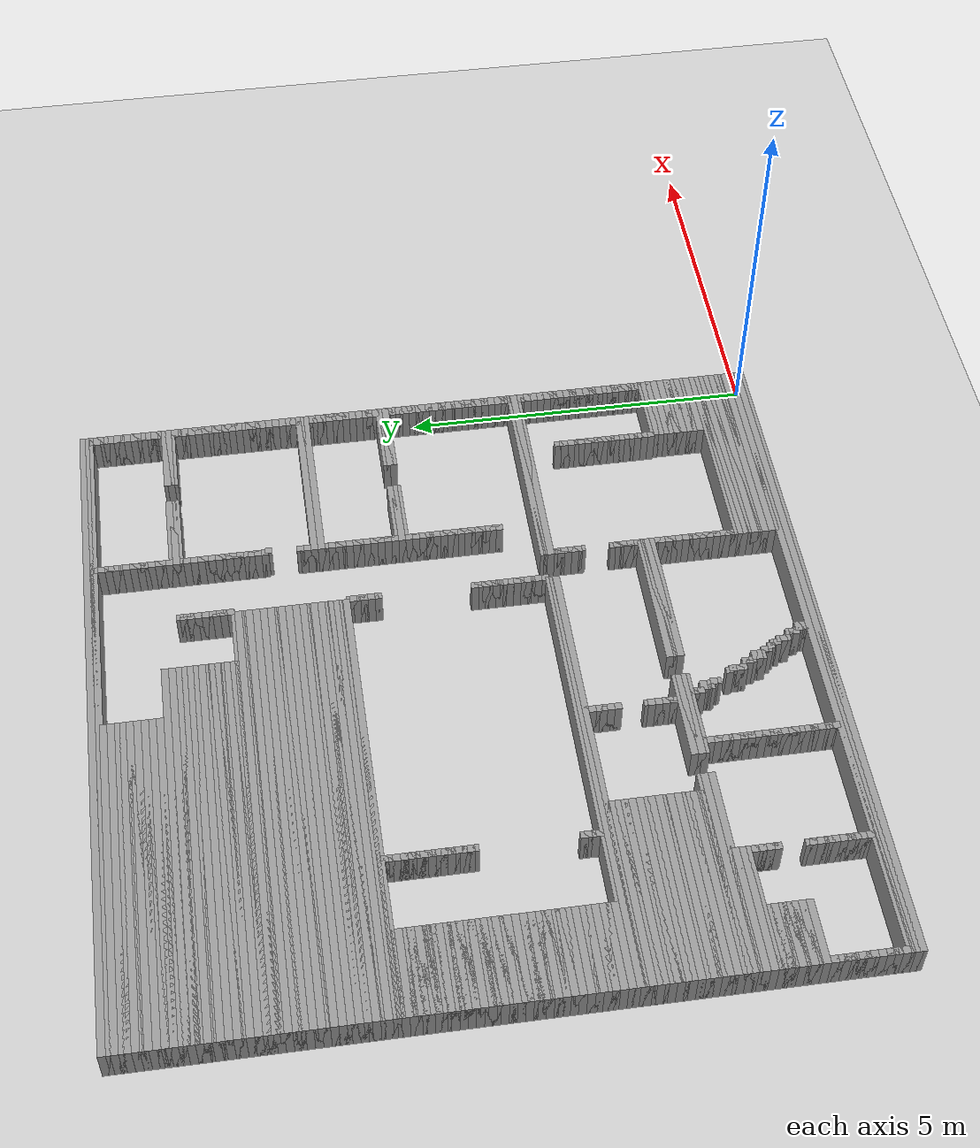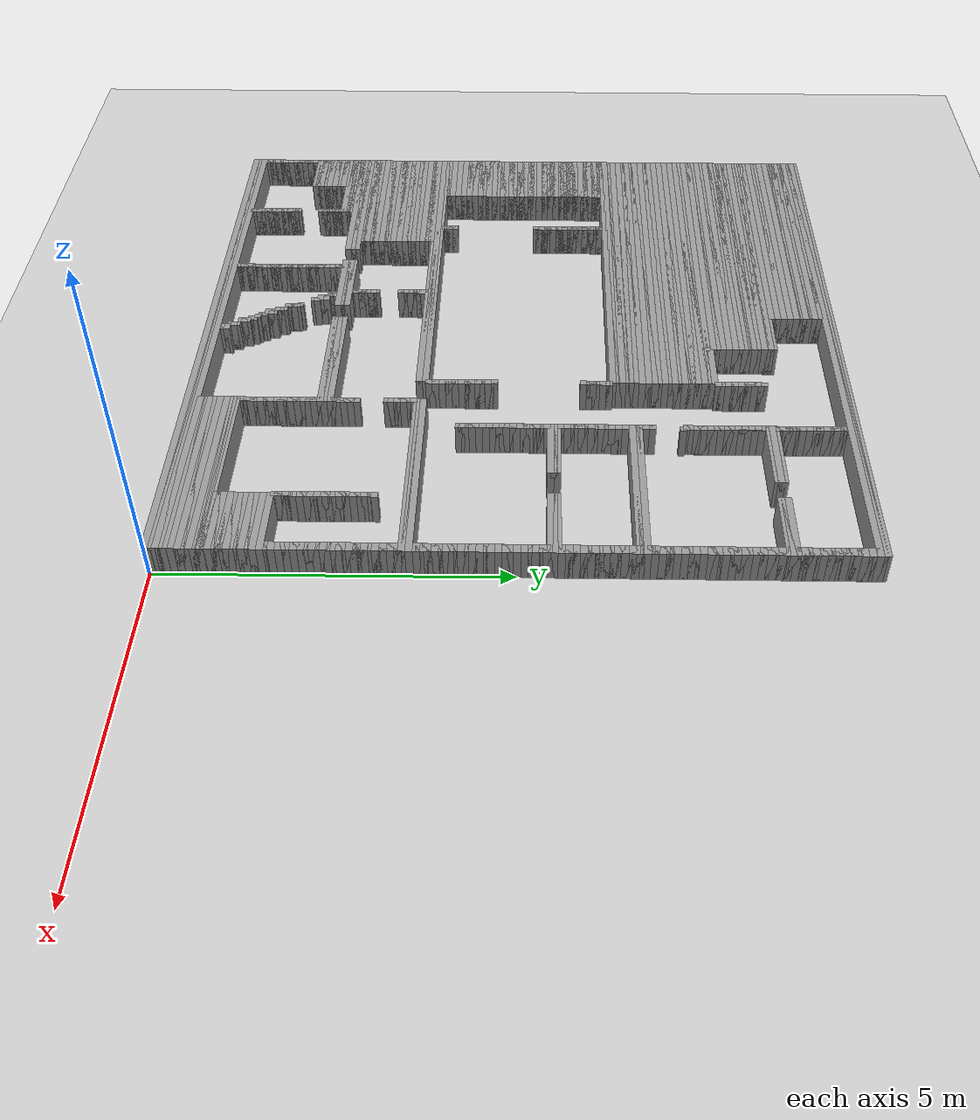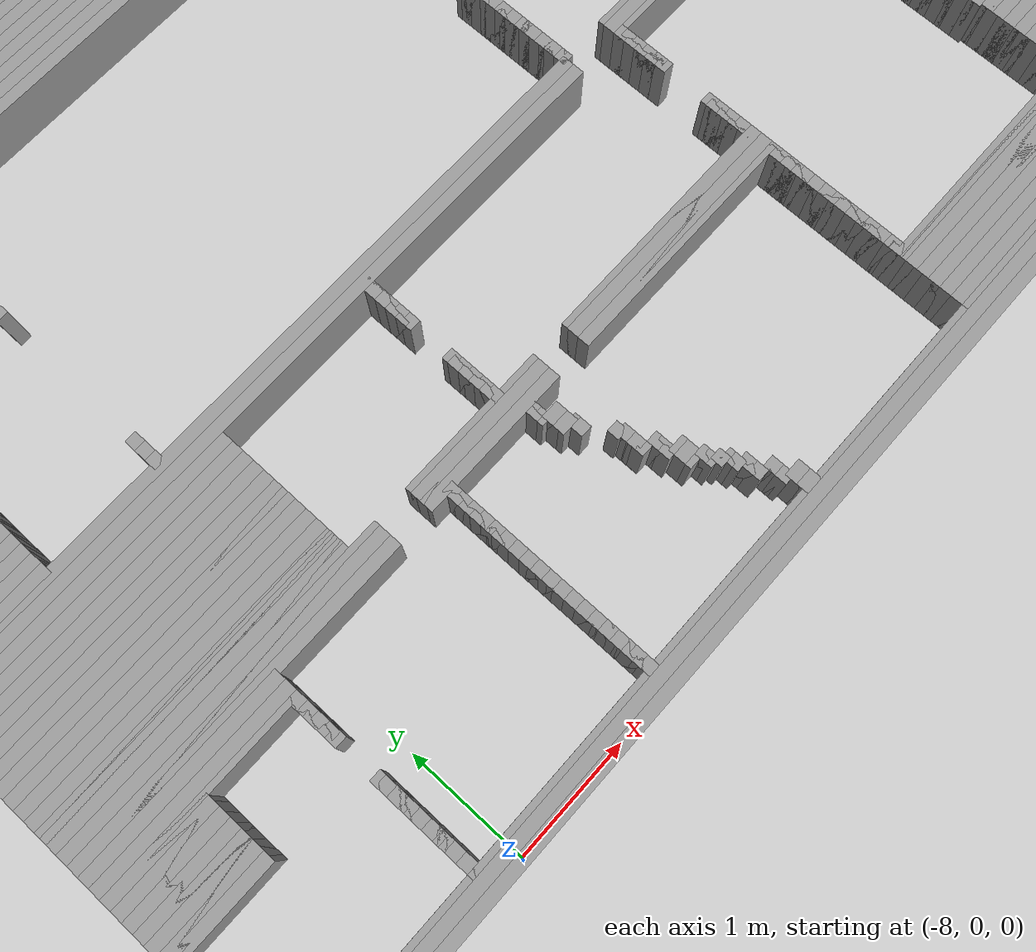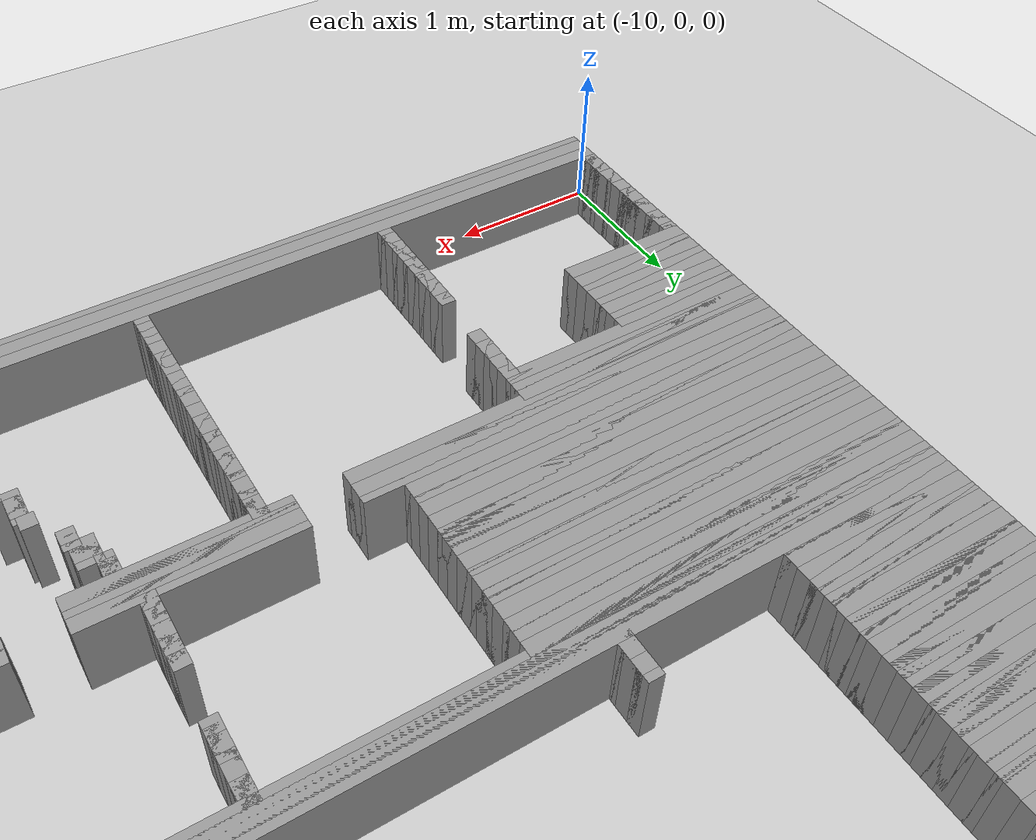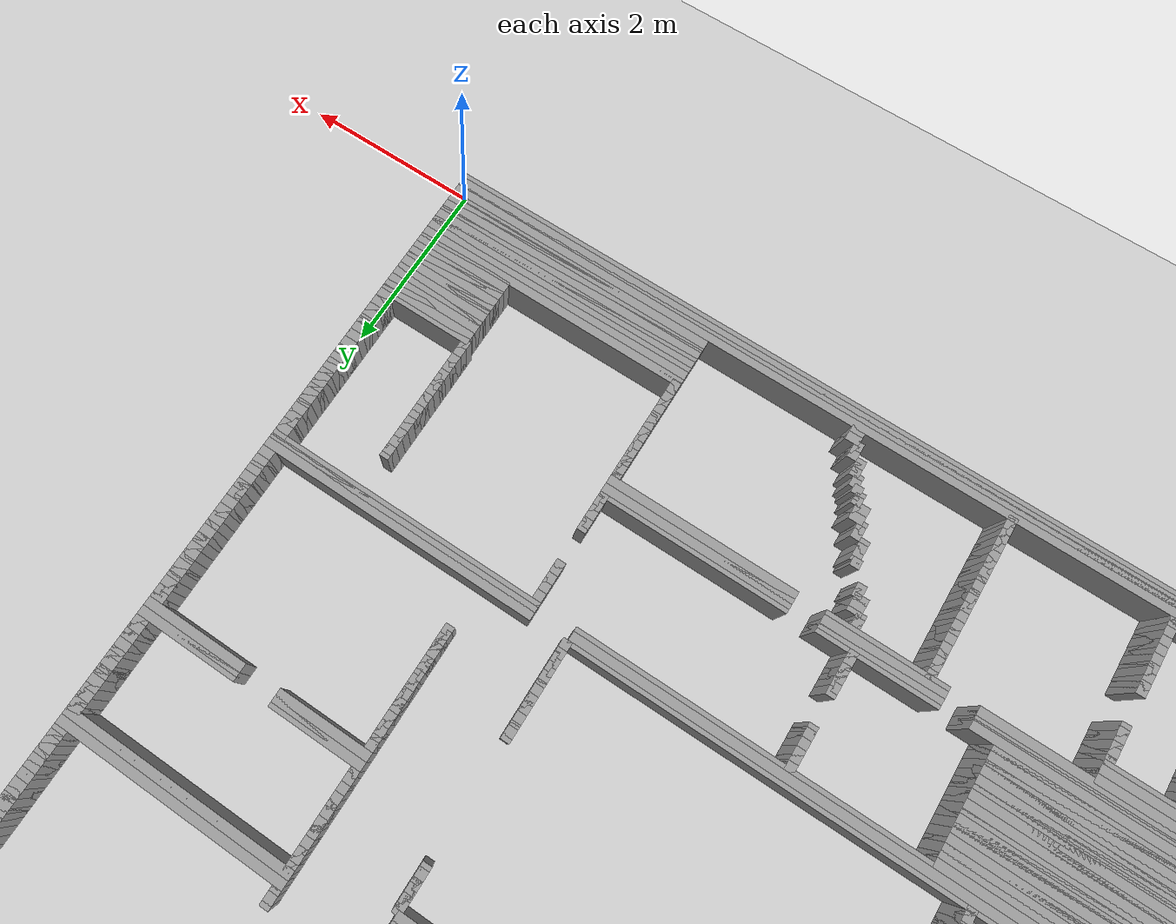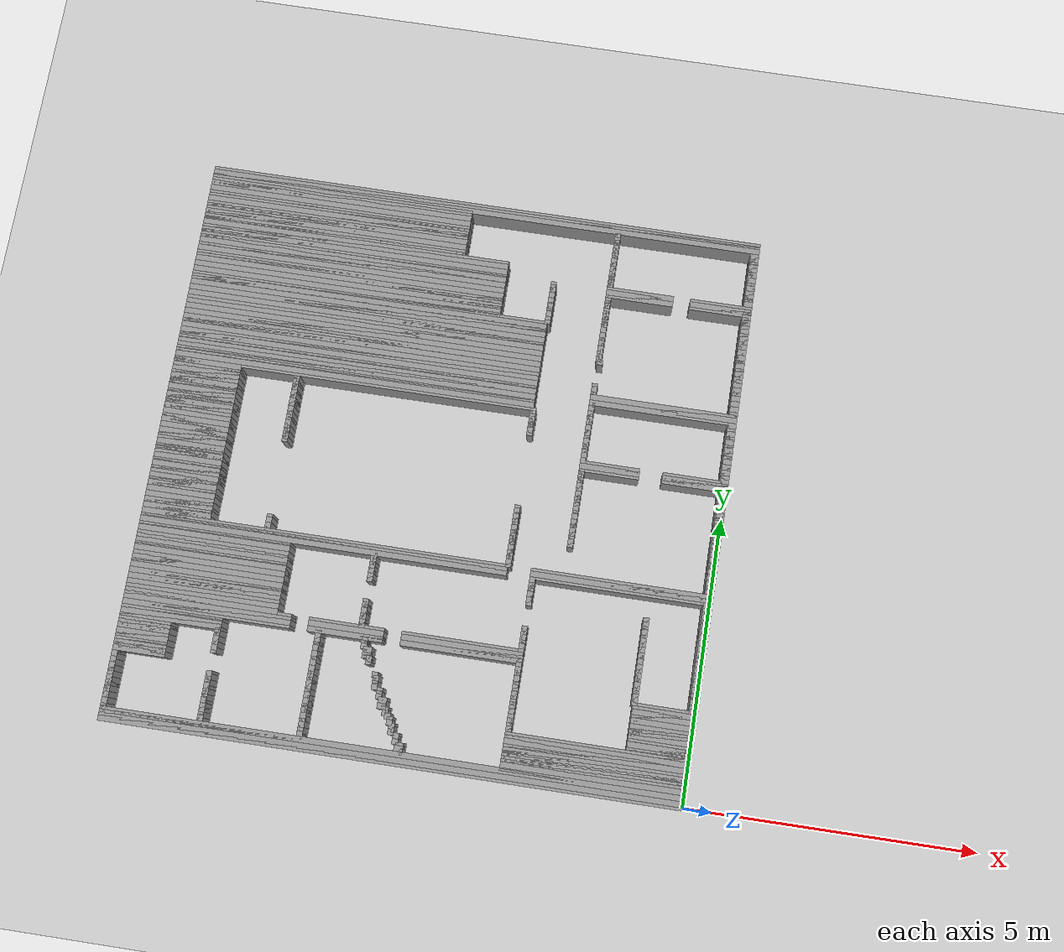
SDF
<?xml version='1.0' encoding='UTF-8'?>
<sdf version="1.6"><world name="GridMap"><include><uri>model://sun</uri></include><include><uri>model://ground_plane</uri></include><physics type="ode"><real_time_update_rate>1000.0</real_time_update_rate><max_step_size>0.001</max_step_size><real_time_factor>1</real_time_factor><ode><solver><type>quick</type><iters>150</iters><precon_iters>0</precon_iters><sor>1.4</sor><use_dynamic_moi_rescaling>1</use_dynamic_moi_rescaling></solver><constraints><cfm>0.00001</cfm><erp>0.2</erp><contact_max_correcting_vel>2000.000000</contact_max_correcting_vel><contact_surface_layer>0.01000</contact_surface_layer></constraints></ode></physics><model name="GridMap"><pose frame="">0 0 0 0 -0 0</pose><link name="Wall_(99.5,0.0)"><collision name="Wall_(99.5,0.0)_Collision"><geometry><box><size>9.950000000000001 0.1 0.5</size></box></geometry><pose frame="">-4.9750000000000005 0.0 0.25 0 -0 0</pose></collision><inertial><mass>0.5</mass><pose>0 0.01 0 0 0 0</pose><inertia><ixx>0.004</ixx><ixy>0.001</ixy><ixz>0</ixz><iyy>0.006</iyy><iyz>0</iyz><izz>0.007</izz></inertia></inertial><visual name="Wall_(99.5,0.0)_Visual"><geometry><box><size>9.950000000000001 0.1 0.5</size></box></geometry><pose frame="">-4.9750000000000005 0.0 0.25 0 -0 0</pose><material><script><uri>file://media/materials/scripts/gazebo.material</uri><name>Gazebo/Grey</name></script><ambient>1 1 1 1</ambient></material><meta><layer>0</layer></meta></visual><pose frame="">0 0 0 0 -0 0</pose></link><link name="Wall_(99.5,1.0)"><collision name="Wall_(99.5,1.0)_Collision"><geometry><box><size>9.950000000000001 0.1 0.5</size></box></geometry><pose frame="">-4.9750000000000005 0.05 0.25 0 -0 0</pose></collision><inertial><mass>0.5</mass><pose>0 0.01 0 0 0 0</pose><inertia><ixx>0.004</ixx><ixy>0.001</ixy><ixz>0</ixz><iyy>0.006</iyy><iyz>0</iyz><izz>0.007</izz></inertia></inertial><visual name="Wall_(99.5,1.0)_Visual"><geometry><box><size>9.950000000000001 0.1 0.5</size></box></geometry><pose frame="">-4.9750000000000005 0.05 0.25 0 -0 0</pose><material><script><uri>file://media/materials/scripts/gazebo.material</uri><name>Gazebo/Grey</name></script><ambient>1 1 1 1</ambient></material><meta><layer>0</layer></meta></visual><pose frame="">0 0 0 0 -0 0</pose></link><link name="Wall_(99.5,2.0)"><collision name="Wall_(99.5,2.0)_Collision"><geometry><box><size>9.950000000000001 0.1 0.5</size></box></geometry><pose frame="">-4.9750000000000005 0.1 0.25 0 -0 0</pose></collision><inertial><mass>0.5</mass><pose>0 0.01 0 0 0 0</pose><inertia><ixx>0.004</ixx><ixy>0.001</ixy><ixz>0</ixz><iyy>0.006</iyy><iyz>0</iyz><izz>0.007</izz></inertia></inertial><visual name="Wall_(99.5,2.0)_Visual"><geometry><box><size>9.950000000000001 0.1 0.5</size></box></geometry><pose frame="">-4.9750000000000005 0.1 0.25 0 -0 0</pose><material><script><uri>file://media/materials/scripts/gazebo.material</uri><name>Gazebo/Grey</name></script><ambient>1 1 1 1</ambient></material><meta><layer>0</layer></meta></visual><pose frame="">0 0 0 0 -0 0</pose></link><link name="Wall_(99.5,3.0)"><collision name="Wall_(99.5,3.0)_Collision"><geometry><box><size>9.950000000000001 0.1 0.5</size></box></geometry><pose frame="">-4.9750000000000005 0.15000000000000002 0.25 0 -0 0</pose></collision><inertial><mass>0.5</mass><pose>0 0.01 0 0 0 0</pose><inertia><ixx>0.004</ixx><ixy>0.001</ixy><ixz>0</ixz><iyy>0.006</iyy><iyz>0</iyz><izz>0.007</izz></inertia></inertial><visual name="Wall_(99.5,3.0)_Visual"><geometry><box><size>9.950000000000001 0.1 0.5</size></box></geometry><pose frame="">-4.9750000000000005 0.15000000000000002 0.25 0 -0 0</pose><material><script><uri>file://media/materials/scripts/gazebo.material</uri><name>Gazebo/Grey</name></script><ambient>1 1 1 1</ambient></material><meta><layer>0</layer></meta></visual><pose frame="">0 0 0 0 -0 0</pose></link><link name="Wall_(31.5,4.0)"><collision name="Wall_(31.5,4.0)_Collision"><geometry><box><size>3.1500000000000004 0.1 0.5</size></box></geometry><pose frame="">-1.5750000000000002 0.2 0.25 0 -0 0</pose></collision><inertial><mass>0.5</mass><pose>0 0.01 0 0 0 0</pose><inertia><ixx>0.004</ixx><ixy>0.001</ixy><ixz>0</ixz><iyy>0.006</iyy><iyz>0</iyz><izz>0.007</izz></inertia></inertial><visual name="Wall_(31.5,4.0)_Visual"><geometry><box><size>3.1500000000000004 0.1 0.5</size></box></geometry><pose frame="">-1.5750000000000002 0.2 0.25 0 -0 0</pose><material><script><uri>file://media/materials/scripts/gazebo.material</uri><name>Gazebo/Grey</name></script><ambient>1 1 1 1</ambient></material><meta><layer>0</layer></meta></visual><pose frame="">0 0 0 0 -0 0</pose></link><link name="Wall_(97.5,4.0)"><collision name="Wall_(97.5,4.0)_Collision"><geometry><box><size>0.15000000000000002 0.1 0.5</size></box></geometry><pose frame="">-4.875 0.2 0.25 0 -0 0</pose></collision><inertial><mass>0.5</mass><pose>0 0.01 0 0 0 0</pose><inertia><ixx>0.004</ixx><ixy>0.001</ixy><ixz>0</ixz><iyy>0.006</iyy><iyz>0</iyz><izz>0.007</izz></inertia></inertial><visual name="Wall_(97.5,4.0)_Visual"><geometry><box><size>0.15000000000000002 0.1 0.5</size></box></geometry><pose frame="">-4.875 0.2 0.25 0 -0 0</pose><material><script><uri>file://media/materials/scripts/gazebo.material</uri><name>Gazebo/Grey</name></script><ambient>1 1 1 1</ambient></material><meta><layer>0</layer></meta></visual><pose frame="">0 0 0 0 -0 0</pose></link><link name="Wall_(131.0,4.0)"><collision name="Wall_(131.0,4.0)_Collision"><geometry><box><size>0.1 0.1 0.5</size></box></geometry><pose frame="">-6.550000000000001 0.2 0.25 0 -0 0</pose></collision><inertial><mass>0.5</mass><pose>0 0.01 0 0 0 0</pose><inertia><ixx>0.004</ixx><ixy>0.001</ixy><ixz>0</ixz><iyy>0.006</iyy><iyz>0</iyz><izz>0.007</izz></inertia></inertial><visual name="Wall_(131.0,4.0)_Visual"><geometry><box><size>0.1 0.1 0.5</size></box></geometry><pose frame="">-6.550000000000001 0.2 0.25 0 -0 0</pose><material><script><uri>file://media/materials/scripts/gazebo.material</uri><name>Gazebo/Grey</name></script><ambient>1 1 1 1</ambient></material><meta><layer>0</layer></meta></visual><pose frame="">0 0 0 0 -0 0</pose></link><link name="Wall_(165.0,4.0)"><collision name="Wall_(165.0,4.0)_Collision"><geometry><box><size>0.1 0.1 0.5</size></box></geometry><pose frame="">-8.25 0.2 0.25 0 -0 0</pose></collision><inertial><mass>0.5</mass><pose>0 0.01 0 0 0 0</pose><inertia><ixx>0.004</ixx><ixy>0.001</ixy><ixz>0</ixz><iyy>0.006</iyy><iyz>0</iyz><izz>0.007</izz></inertia></inertial><visual name="Wall_(165.0,4.0)_Visual"><geometry><box><size>0.1 0.1 0.5</size></box></geometry><pose frame="">-8.25 0.2 0.25 0 -0 0</pose><material><script><uri>file://media/materials/scripts/gazebo.material</uri><name>Gazebo/Grey</name></script><ambient>1 1 1 1</ambient></material><meta><layer>0</layer></meta></visual><pose frame="">0 0 0 0 -0 0</pose></link><link name="Wall_(198.0,4.0)"><collision name="Wall_(198.0,4.0)_Collision"><geometry><box><size>0.1 0.1 0.5</size></box></geometry><pose frame="">-9.9 0.2 0.25 0 -0 0</pose></collision><inertial><mass>0.5</mass><pose>0 0.01 0 0 0 0</pose><inertia><ixx>0.004</ixx><ixy>0.001</ixy><ixz>0</ixz><iyy>0.006</iyy><iyz>0</iyz><izz>0.007</izz></inertia></inertial><visual name="Wall_(198.0,4.0)_Visual"><geometry><box><size>0.1 0.1 0.5</size></box></geometry><pose frame="">-9.9 0.2 0.25 0 -0 0</pose><material><script><uri>file://media/materials/scripts/gazebo.material</uri><name>Gazebo/Grey</name></script><ambient>1 1 1 1</ambient></material><meta><layer>0</layer></meta></visual><pose frame="">0 0 0 0 -0 0</pose></link><link name="Wall_(31.5,5.0)"><collision name="Wall_(31.5,5.0)_Collision"><geometry><box><size>3.1500000000000004 0.1 0.5</size></box></geometry><pose frame="">-1.5750000000000002 0.25 0.25 0 -0 0</pose></collision><inertial><mass>0.5</mass><pose>0 0.01 0 0 0 0</pose><inertia><ixx>0.004</ixx><ixy>0.001</ixy><ixz>0</ixz><iyy>0.006</iyy><iyz>0</iyz><izz>0.007</izz></inertia></inertial><visual name="Wall_(31.5,5.0)_Visual"><geometry><box><size>3.1500000000000004 0.1 0.5</size></box></geometry><pose frame="">-1.5750000000000002 0.25 0.25 0 -0 0</pose><material><script><uri>file://media/materials/scripts/gazebo.material</uri><name>Gazebo/Grey</name></script><ambient>1 1 1 1</ambient></material><meta><layer>0</layer></meta></visual><pose frame="">0 0 0 0 -0 0</pose></link><link name="Wall_(97.5,5.0)"><collision name="Wall_(97.5,5.0)_Collision"><geometry><box><size>0.15000000000000002 0.1 0.5</size></box></geometry><pose frame="">-4.875 0.25 0.25 0 -0 0</pose></collision><inertial><mass>0.5</mass><pose>0 0.01 0 0 0 0</pose><inertia><ixx>0.004</ixx><ixy>0.001</ixy><ixz>0</ixz><iyy>0.006</iyy><iyz>0</iyz><izz>0.007</izz></inertia></inertial><visual name="Wall_(97.5,5.0)_Visual"><geometry><box><size>0.15000000000000002 0.1 0.5</size></box></geometry><pose frame="">-4.875 0.25 0.25 0 -0 0</pose><material><script><uri>file://media/materials/scripts/gazebo.material</uri><name>Gazebo/Grey</name></script><ambient>1 1 1 1</ambient></material><meta><layer>0</layer></meta></visual><pose frame="">0 0 0 0 -0 0</pose></link><link name="Wall_(131.0,5.0)"><collision name="Wall_(131.0,5.0)_Collision"><geometry><box><size>0.1 0.1 0.5</size></box></geometry><pose frame="">-6.550000000000001 0.25 0.25 0 -0 0</pose></collision><inertial><mass>0.5</mass><pose>0 0.01 0 0 0 0</pose><inertia><ixx>0.004</ixx><ixy>0.001</ixy><ixz>0</ixz><iyy>0.006</iyy><iyz>0</iyz><izz>0.007</izz></inertia></inertial><visual name="Wall_(131.0,5.0)_Visual"><geometry><box><size>0.1 0.1 0.5</size></box></geometry><pose frame="">-6.550000000000001 0.25 0.25 0 -0 0</pose><material><script><uri>file://media/materials/scripts/gazebo.material</uri><name>Gazebo/Grey</name></script><ambient>1 1 1 1</ambient></material><meta><layer>0</layer></meta></visual><pose frame="">0 0 0 0 -0 0</pose></link><link name="Wall_(165.0,5.0)"><collision name="Wall_(165.0,5.0)_Collision"><geometry><box><size>0.1 0.1 0.5</size></box></geometry><pose frame="">-8.25 0.25 0.25 0 -0 0</pose></collision><inertial><mass>0.5</mass><pose>0 0.01 0 0 0 0</pose><inertia><ixx>0.004</ixx><ixy>0.001</ixy><ixz>0</ixz><iyy>0.006</iyy><iyz>0</iyz><izz>0.007</izz></inertia></inertial><visual name="Wall_(165.0,5.0)_Visual"><geometry><box><size>0.1 0.1 0.5</size></box></geometry><pose frame="">-8.25 0.25 0.25 0 -0 0</pose><material><script><uri>file://media/materials/scripts/gazebo.material</uri><name>Gazebo/Grey</name></script><ambient>1 1 1 1</ambient></material><meta><layer>0</layer></meta></visual><pose frame="">0 0 0 0 -0 0</pose></link><link name="Wall_(198.0,5.0)"><collision name="Wall_(198.0,5.0)_Collision"><geometry><box><size>0.1 0.1 0.5</size></box></geometry><pose frame="">-9.9 0.25 0.25 0 -0 0</pose></collision><inertial><mass>0.5</mass><pose>0 0.01 0 0 0 0</pose><inertia><ixx>0.004</ixx><ixy>0.001</ixy><ixz>0</ixz><iyy>0.006</iyy><iyz>0</iyz><izz>0.007</izz></inertia></inertial><visual name="Wall_(198.0,5.0)_Visual"><geometry><box><size>0.1 0.1 0.5</size></box></geometry><pose frame="">-9.9 0.25 0.25 0 -0 0</pose><material><script><uri>file://media/materials/scripts/gazebo.material</uri><name>Gazebo/Grey</name></script><ambient>1 1 1 1</ambient></material><meta><layer>0</layer></meta></visual><pose frame="">0 0 0 0 -0 0</pose></link><link name="Wall_(31.5,6.0)"><collision name="Wall_(31.5,6.0)_Collision"><geometry><box><size>3.1500000000000004 0.1 0.5</size></box></geometry><pose frame="">-1.5750000000000002 0.30000000000000004 0.25 0 -0 0</pose></collision><inertial><mass>0.5</mass><pose>0 0.01 0 0 0 0</pose><inertia><ixx>0.004</ixx><ixy>0.001</ixy><ixz>0</ixz><iyy>0.006</iyy><iyz>0</iyz><izz>0.007</izz></inertia></inertial><visual name="Wall_(31.5,6.0)_Visual"><geometry><box><size>3.1500000000000004 0.1 0.5</size></box></geometry><pose frame="">-1.5750000000000002 0.30000000000000004 0.25 0 -0 0</pose><material><script><uri>file://media/materials/scripts/gazebo.material</uri><name>Gazebo/Grey</name></script><ambient>1 1 1 1</ambient></material><meta><layer>0</layer></meta></visual><pose frame="">0 0 0 0 -0 0</pose></link><link name="Wall_(97.5,6.0)"><collision name="Wall_(97.5,6.0)_Collision"><geometry><box><size>0.15000000000000002 0.1 0.5</size></box></geometry><pose frame="">-4.875 0.30000000000000004 0.25 0 -0 0</pose></collision><inertial><mass>0.5</mass><pose>0 0.01 0 0 0 0</pose><inertia><ixx>0.004</ixx><ixy>0.001</ixy><ixz>0</ixz><iyy>0.006</iyy><iyz>0</iyz><izz>0.007</izz></inertia></inertial><visual name="Wall_(97.5,6.0)_Visual"><geometry><box><size>0.15000000000000002 0.1 0.5</size></box></geometry><pose frame="">-4.875 0.30000000000000004 0.25 0 -0 0</pose><material><script><uri>file://media/materials/scripts/gazebo.material</uri><name>Gazebo/Grey</name></script><ambient>1 1 1 1</ambient></material><meta><layer>0</layer></meta></visual><pose frame="">0 0 0 0 -0 0</pose></link><link name="Wall_(131.0,6.0)"><collision name="Wall_(131.0,6.0)_Collision"><geometry><box><size>0.1 0.1 0.5</size></box></geometry><pose frame="">-6.550000000000001 0.30000000000000004 0.25 0 -0 0</pose></collision><inertial><mass>0.5</mass><pose>0 0.01 0 0 0 0</pose><inertia><ixx>0.004</ixx><ixy>0.001</ixy><ixz>0</ixz><iyy>0.006</iyy><iyz>0</iyz><izz>0.007</izz></inertia></inertial><visual name="Wall_(131.0,6.0)_Visual"><geometry><box><size>0.1 0.1 0.5</size></box></geometry><pose frame="">-6.550000000000001 0.30000000000000004 0.25 0 -0 0</pose><material><script><uri>file://media/materials/scripts/gazebo.material</uri><name>Gazebo/Grey</name></script><ambient>1 1 1 1</ambient></material><meta><layer>0</layer></meta></visual><pose frame="">0 0 0 0 -0 0</pose></link><link name="Wall_(165.0,6.0)"><collision name="Wall_(165.0,6.0)_Collision"><geometry><box><size>0.1 0.1 0.5</size></box></geometry><pose frame="">-8.25 0.30000000000000004 0.25 0 -0 0</pose></collision><inertial><mass>0.5</mass><pose>0 0.01 0 0 0 0</pose><inertia><ixx>0.004</ixx><ixy>0.001</ixy><ixz>0</ixz><iyy>0.006</iyy><iyz>0</iyz><izz>0.007</izz></inertia></inertial><visual name="Wall_(165.0,6.0)_Visual"><geometry><box><size>0.1 0.1 0.5</size></box></geometry><pose frame="">-8.25 0.30000000000000004 0.25 0 -0 0</pose><material><script><uri>file://media/materials/scripts/gazebo.material</uri><name>Gazebo/Grey</name></script><ambient>1 1 1 1</ambient></material><meta><layer>0</layer></meta></visual><pose frame="">0 0 0 0 -0 0</pose></link><link name="Wall_(198.0,6.0)"><collision name="Wall_(198.0,6.0)_Collision"><geometry><box><size>0.1 0.1 0.5</size></box></geometry><pose frame="">-9.9 0.30000000000000004 0.25 0 -0 0</pose></collision><inertial><mass>0.5</mass><pose>0 0.01 0 0 0 0</pose><inertia><ixx>0.004</ixx><ixy>0.001</ixy><ixz>0</ixz><iyy>0.006</iyy><iyz>0</iyz><izz>0.007</izz></inertia></inertial><visual name="Wall_(198.0,6.0)_Visual"><geometry><box><size>0.1 0.1 0.5</size></box></geometry><pose frame="">-9.9 0.30000000000000004 0.25 0 -0 0</pose><material><script><uri>file://media/materials/scripts/gazebo.material</uri><name>Gazebo/Grey</name></script><ambient>1 1 1 1</ambient></material><meta><layer>0</layer></meta></visual><pose frame="">0 0 0 0 -0 0</pose></link><link name="Wall_(31.5,7.0)"><collision name="Wall_(31.5,7.0)_Collision"><geometry><box><size>3.1500000000000004 0.1 0.5</size></box></geometry><pose frame="">-1.5750000000000002 0.35000000000000003 0.25 0 -0 0</pose></collision><inertial><mass>0.5</mass><pose>0 0.01 0 0 0 0</pose><inertia><ixx>0.004</ixx><ixy>0.001</ixy><ixz>0</ixz><iyy>0.006</iyy><iyz>0</iyz><izz>0.007</izz></inertia></inertial><visual name="Wall_(31.5,7.0)_Visual"><geometry><box><size>3.1500000000000004 0.1 0.5</size></box></geometry><pose frame="">-1.5750000000000002 0.35000000000000003 0.25 0 -0 0</pose><material><script><uri>file://media/materials/scripts/gazebo.material</uri><name>Gazebo/Grey</name></script><ambient>1 1 1 1</ambient></material><meta><layer>0</layer></meta></visual><pose frame="">0 0 0 0 -0 0</pose></link><link name="Wall_(99.0,7.0)"><collision name="Wall_(99.0,7.0)_Collision"><geometry><box><size>0.1 0.1 0.5</size></box></geometry><pose frame="">-4.95 0.35000000000000003 0.25 0 -0 0</pose></collision><inertial><mass>0.5</mass><pose>0 0.01 0 0 0 0</pose><inertia><ixx>0.004</ixx><ixy>0.001</ixy><ixz>0</ixz><iyy>0.006</iyy><iyz>0</iyz><izz>0.007</izz></inertia></inertial><visual name="Wall_(99.0,7.0)_Visual"><geometry><box><size>0.1 0.1 0.5</size></box></geometry><pose frame="">-4.95 0.35000000000000003 0.25 0 -0 0</pose><material><script><uri>file://media/materials/scripts/gazebo.material</uri><name>Gazebo/Grey</name></script><ambient>1 1 1 1</ambient></material><meta><layer>0</layer></meta></visual><pose frame="">0 0 0 0 -0 0</pose></link><link name="Wall_(131.0,7.0)"><collision name="Wall_(131.0,7.0)_Collision"><geometry><box><size>0.1 0.1 0.5</size></box></geometry><pose frame="">-6.550000000000001 0.35000000000000003 0.25 0 -0 0</pose></collision><inertial><mass>0.5</mass><pose>0 0.01 0 0 0 0</pose><inertia><ixx>0.004</ixx><ixy>0.001</ixy><ixz>0</ixz><iyy>0.006</iyy><iyz>0</iyz><izz>0.007</izz></inertia></inertial><visual name="Wall_(131.0,7.0)_Visual"><geometry><box><size>0.1 0.1 0.5</size></box></geometry><pose frame="">-6.550000000000001 0.35000000000000003 0.25 0 -0 0</pose><material><script><uri>file://media/materials/scripts/gazebo.material</uri><name>Gazebo/Grey</name></script><ambient>1 1 1 1</ambient></material><meta><layer>0</layer></meta></visual><pose frame="">0 0 0 0 -0 0</pose></link><link name="Wall_(165.0,7.0)"><collision name="Wall_(165.0,7.0)_Collision"><geometry><box><size>0.1 0.1 0.5</size></box></geometry><pose frame="">-8.25 0.35000000000000003 0.25 0 -0 0</pose></collision><inertial><mass>0.5</mass><pose>0 0.01 0 0 0 0</pose><inertia><ixx>0.004</ixx><ixy>0.001</ixy><ixz>0</ixz><iyy>0.006</iyy><iyz>0</iyz><izz>0.007</izz></inertia></inertial><visual name="Wall_(165.0,7.0)_Visual"><geometry><box><size>0.1 0.1 0.5</size></box></geometry><pose frame="">-8.25 0.35000000000000003 0.25 0 -0 0</pose><material><script><uri>file://media/materials/scripts/gazebo.material</uri><name>Gazebo/Grey</name></script><ambient>1 1 1 1</ambient></material><meta><layer>0</layer></meta></visual><pose frame="">0 0 0 0 -0 0</pose></link><link name="Wall_(198.0,7.0)"><collision name="Wall_(198.0,7.0)_Collision"><geometry><box><size>0.1 0.1 0.5</size></box></geometry><pose frame="">-9.9 0.35000000000000003 0.25 0 -0 0</pose></collision><inertial><mass>0.5</mass><pose>0 0.01 0 0 0 0</pose><inertia><ixx>0.004</ixx><ixy>0.001</ixy><ixz>0</ixz><iyy>0.006</iyy><iyz>0</iyz><izz>0.007</izz></inertia></inertial><visual name="Wall_(198.0,7.0)_Visual"><geometry><box><size>0.1 0.1 0.5</size></box></geometry><pose frame="">-9.9 0.35000000000000003 0.25 0 -0 0</pose><material><script><uri>file://media/materials/scripts/gazebo.material</uri><name>Gazebo/Grey</name></script><ambient>1 1 1 1</ambient></material><meta><layer>0</layer></meta></visual><pose frame="">0 0 0 0 -0 0</pose></link><link name="Wall_(31.5,8.0)"><collision name="Wall_(31.5,8.0)_Collision"><geometry><box><size>3.1500000000000004 0.1 0.5</size></box></geometry><pose frame="">-1.5750000000000002 0.4 0.25 0 -0 0</pose></collision><inertial><mass>0.5</mass><pose>0 0.01 0 0 0 0</pose><inertia><ixx>0.004</ixx><ixy>0.001</ixy><ixz>0</ixz><iyy>0.006</iyy><iyz>0</iyz><izz>0.007</izz></inertia></inertial><visual name="Wall_(31.5,8.0)_Visual"><geometry><box><size>3.1500000000000004 0.1 0.5</size></box></geometry><pose frame="">-1.5750000000000002 0.4 0.25 0 -0 0</pose><material><script><uri>file://media/materials/scripts/gazebo.material</uri><name>Gazebo/Grey</name></script><ambient>1 1 1 1</ambient></material><meta><layer>0</layer></meta></visual><pose frame="">0 0 0 0 -0 0</pose></link><link name="Wall_(99.0,8.0)"><collision name="Wall_(99.0,8.0)_Collision"><geometry><box><size>0.1 0.1 0.5</size></box></geometry><pose frame="">-4.95 0.4 0.25 0 -0 0</pose></collision><inertial><mass>0.5</mass><pose>0 0.01 0 0 0 0</pose><inertia><ixx>0.004</ixx><ixy>0.001</ixy><ixz>0</ixz><iyy>0.006</iyy><iyz>0</iyz><izz>0.007</izz></inertia></inertial><visual name="Wall_(99.0,8.0)_Visual"><geometry><box><size>0.1 0.1 0.5</size></box></geometry><pose frame="">-4.95 0.4 0.25 0 -0 0</pose><material><script><uri>file://media/materials/scripts/gazebo.material</uri><name>Gazebo/Grey</name></script><ambient>1 1 1 1</ambient></material><meta><layer>0</layer></meta></visual><pose frame="">0 0 0 0 -0 0</pose></link><link name="Wall_(131.0,8.0)"><collision name="Wall_(131.0,8.0)_Collision"><geometry><box><size>0.1 0.1 0.5</size></box></geometry><pose frame="">-6.550000000000001 0.4 0.25 0 -0 0</pose></collision><inertial><mass>0.5</mass><pose>0 0.01 0 0 0 0</pose><inertia><ixx>0.004</ixx><ixy>0.001</ixy><ixz>0</ixz><iyy>0.006</iyy><iyz>0</iyz><izz>0.007</izz></inertia></inertial><visual name="Wall_(131.0,8.0)_Visual"><geometry><box><size>0.1 0.1 0.5</size></box></geometry><pose frame="">-6.550000000000001 0.4 0.25 0 -0 0</pose><material><script><uri>file://media/materials/scripts/gazebo.material</uri><name>Gazebo/Grey</name></script><ambient>1 1 1 1</ambient></material><meta><layer>0</layer></meta></visual><pose frame="">0 0 0 0 -0 0</pose></link><link name="Wall_(165.0,8.0)"><collision name="Wall_(165.0,8.0)_Collision"><geometry><box><size>0.1 0.1 0.5</size></box></geometry><pose frame="">-8.25 0.4 0.25 0 -0 0</pose></collision><inertial><mass>0.5</mass><pose>0 0.01 0 0 0 0</pose><inertia><ixx>0.004</ixx><ixy>0.001</ixy><ixz>0</ixz><iyy>0.006</iyy><iyz>0</iyz><izz>0.007</izz></inertia></inertial><visual name="Wall_(165.0,8.0)_Visual"><geometry><box><size>0.1 0.1 0.5</size></box></geometry><pose frame="">-8.25 0.4 0.25 0 -0 0</pose><material><script><uri>file://media/materials/scripts/gazebo.material</uri><name>Gazebo/Grey</name></script><ambient>1 1 1 1</ambient></material><meta><layer>0</layer></meta></visual><pose frame="">0 0 0 0 -0 0</pose></link><link name="Wall_(198.0,8.0)"><collision name="Wall_(198.0,8.0)_Collision"><geometry><box><size>0.1 0.1 0.5</size></box></geometry><pose frame="">-9.9 0.4 0.25 0 -0 0</pose></collision><inertial><mass>0.5</mass><pose>0 0.01 0 0 0 0</pose><inertia><ixx>0.004</ixx><ixy>0.001</ixy><ixz>0</ixz><iyy>0.006</iyy><iyz>0</iyz><izz>0.007</izz></inertia></inertial><visual name="Wall_(198.0,8.0)_Visual"><geometry><box><size>0.1 0.1 0.5</size></box></geometry><pose frame="">-9.9 0.4 0.25 0 -0 0</pose><material><script><uri>file://media/materials/scripts/gazebo.material</uri><name>Gazebo/Grey</name></script><ambient>1 1 1 1</ambient></material><meta><layer>0</layer></meta></visual><pose frame="">0 0 0 0 -0 0</pose></link><link name="Wall_(31.5,9.0)"><collision name="Wall_(31.5,9.0)_Collision"><geometry><box><size>3.1500000000000004 0.1 0.5</size></box></geometry><pose frame="">-1.5750000000000002 0.45 0.25 0 -0 0</pose></collision><inertial><mass>0.5</mass><pose>0 0.01 0 0 0 0</pose><inertia><ixx>0.004</ixx><ixy>0.001</ixy><ixz>0</ixz><iyy>0.006</iyy><iyz>0</iyz><izz>0.007</izz></inertia></inertial><visual name="Wall_(31.5,9.0)_Visual"><geometry><box><size>3.1500000000000004 0.1 0.5</size></box></geometry><pose frame="">-1.5750000000000002 0.45 0.25 0 -0 0</pose><material><script><uri>file://media/materials/scripts/gazebo.material</uri><name>Gazebo/Grey</name></script><ambient>1 1 1 1</ambient></material><meta><layer>0</layer></meta></visual><pose frame="">0 0 0 0 -0 0</pose></link><link name="Wall_(99.0,9.0)"><collision name="Wall_(99.0,9.0)_Collision"><geometry><box><size>0.1 0.1 0.5</size></box></geometry><pose frame="">-4.95 0.45 0.25 0 -0 0</pose></collision><inertial><mass>0.5</mass><pose>0 0.01 0 0 0 0</pose><inertia><ixx>0.004</ixx><ixy>0.001</ixy><ixz>0</ixz><iyy>0.006</iyy><iyz>0</iyz><izz>0.007</izz></inertia></inertial><visual name="Wall_(99.0,9.0)_Visual"><geometry><box><size>0.1 0.1 0.5</size></box></geometry><pose frame="">-4.95 0.45 0.25 0 -0 0</pose><material><script><uri>file://media/materials/scripts/gazebo.material</uri><name>Gazebo/Grey</name></script><ambient>1 1 1 1</ambient></material><meta><layer>0</layer></meta></visual><pose frame="">0 0 0 0 -0 0</pose></link><link name="Wall_(131.0,9.0)"><collision name="Wall_(131.0,9.0)_Collision"><geometry><box><size>0.1 0.1 0.5</size></box></geometry><pose frame="">-6.550000000000001 0.45 0.25 0 -0 0</pose></collision><inertial><mass>0.5</mass><pose>0 0.01 0 0 0 0</pose><inertia><ixx>0.004</ixx><ixy>0.001</ixy><ixz>0</ixz><iyy>0.006</iyy><iyz>0</iyz><izz>0.007</izz></inertia></inertial><visual name="Wall_(131.0,9.0)_Visual"><geometry><box><size>0.1 0.1 0.5</size></box></geometry><pose frame="">-6.550000000000001 0.45 0.25 0 -0 0</pose><material><script><uri>file://media/materials/scripts/gazebo.material</uri><name>Gazebo/Grey</name></script><ambient>1 1 1 1</ambient></material><meta><layer>0</layer></meta></visual><pose frame="">0 0 0 0 -0 0</pose></link><link name="Wall_(165.0,9.0)"><collision name="Wall_(165.0,9.0)_Collision"><geometry><box><size>0.1 0.1 0.5</size></box></geometry><pose frame="">-8.25 0.45 0.25 0 -0 0</pose></collision><inertial><mass>0.5</mass><pose>0 0.01 0 0 0 0</pose><inertia><ixx>0.004</ixx><ixy>0.001</ixy><ixz>0</ixz><iyy>0.006</iyy><iyz>0</iyz><izz>0.007</izz></inertia></inertial><visual name="Wall_(165.0,9.0)_Visual"><geometry><box><size>0.1 0.1 0.5</size></box></geometry><pose frame="">-8.25 0.45 0.25 0 -0 0</pose><material><script><uri>file://media/materials/scripts/gazebo.material</uri><name>Gazebo/Grey</name></script><ambient>1 1 1 1</ambient></material><meta><layer>0</layer></meta></visual><pose frame="">0 0 0 0 -0 0</pose></link><link name="Wall_(198.0,9.0)"><collision name="Wall_(198.0,9.0)_Collision"><geometry><box><size>0.1 0.1 0.5</size></box></geometry><pose frame="">-9.9 0.45 0.25 0 -0 0</pose></collision><inertial><mass>0.5</mass><pose>0 0.01 0 0 0 0</pose><inertia><ixx>0.004</ixx><ixy>0.001</ixy><ixz>0</ixz><iyy>0.006</iyy><iyz>0</iyz><izz>0.007</izz></inertia></inertial><visual name="Wall_(198.0,9.0)_Visual"><geometry><box><size>0.1 0.1 0.5</size></box></geometry><pose frame="">-9.9 0.45 0.25 0 -0 0</pose><material><script><uri>file://media/materials/scripts/gazebo.material</uri><name>Gazebo/Grey</name></script><ambient>1 1 1 1</ambient></material><meta><layer>0</layer></meta></visual><pose frame="">0 0 0 0 -0 0</pose></link><link name="Wall_(31.5,10.0)"><collision name="Wall_(31.5,10.0)_Collision"><geometry><box><size>3.1500000000000004 0.1 0.5</size></box></geometry><pose frame="">-1.5750000000000002 0.5 0.25 0 -0 0</pose></collision><inertial><mass>0.5</mass><pose>0 0.01 0 0 0 0</pose><inertia><ixx>0.004</ixx><ixy>0.001</ixy><ixz>0</ixz><iyy>0.006</iyy><iyz>0</iyz><izz>0.007</izz></inertia></inertial><visual name="Wall_(31.5,10.0)_Visual"><geometry><box><size>3.1500000000000004 0.1 0.5</size></box></geometry><pose frame="">-1.5750000000000002 0.5 0.25 0 -0 0</pose><material><script><uri>file://media/materials/scripts/gazebo.material</uri><name>Gazebo/Grey</name></script><ambient>1 1 1 1</ambient></material><meta><layer>0</layer></meta></visual><pose frame="">0 0 0 0 -0 0</pose></link><link name="Wall_(101.0,10.0)"><collision name="Wall_(101.0,10.0)_Collision"><geometry><box><size>0.1 0.1 0.5</size></box></geometry><pose frame="">-5.050000000000001 0.5 0.25 0 -0 0</pose></collision><inertial><mass>0.5</mass><pose>0 0.01 0 0 0 0</pose><inertia><ixx>0.004</ixx><ixy>0.001</ixy><ixz>0</ixz><iyy>0.006</iyy><iyz>0</iyz><izz>0.007</izz></inertia></inertial><visual name="Wall_(101.0,10.0)_Visual"><geometry><box><size>0.1 0.1 0.5</size></box></geometry><pose frame="">-5.050000000000001 0.5 0.25 0 -0 0</pose><material><script><uri>file://media/materials/scripts/gazebo.material</uri><name>Gazebo/Grey</name></script><ambient>1 1 1 1</ambient></material><meta><layer>0</layer></meta></visual><pose frame="">0 0 0 0 -0 0</pose></link><link name="Wall_(131.0,10.0)"><collision name="Wall_(131.0,10.0)_Collision"><geometry><box><size>0.1 0.1 0.5</size></box></geometry><pose frame="">-6.550000000000001 0.5 0.25 0 -0 0</pose></collision><inertial><mass>0.5</mass><pose>0 0.01 0 0 0 0</pose><inertia><ixx>0.004</ixx><ixy>0.001</ixy><ixz>0</ixz><iyy>0.006</iyy><iyz>0</iyz><izz>0.007</izz></inertia></inertial><visual name="Wall_(131.0,10.0)_Visual"><geometry><box><size>0.1 0.1 0.5</size></box></geometry><pose frame="">-6.550000000000001 0.5 0.25 0 -0 0</pose><material><script><uri>file://media/materials/scripts/gazebo.material</uri><name>Gazebo/Grey</name></script><ambient>1 1 1 1</ambient></material><meta><layer>0</layer></meta></visual><pose frame="">0 0 0 0 -0 0</pose></link><link name="Wall_(165.0,10.0)"><collision name="Wall_(165.0,10.0)_Collision"><geometry><box><size>0.1 0.1 0.5</size></box></geometry><pose frame="">-8.25 0.5 0.25 0 -0 0</pose></collision><inertial><mass>0.5</mass><pose>0 0.01 0 0 0 0</pose><inertia><ixx>0.004</ixx><ixy>0.001</ixy><ixz>0</ixz><iyy>0.006</iyy><iyz>0</iyz><izz>0.007</izz></inertia></inertial><visual name="Wall_(165.0,10.0)_Visual"><geometry><box><size>0.1 0.1 0.5</size></box></geometry><pose frame="">-8.25 0.5 0.25 0 -0 0</pose><material><script><uri>file://media/materials/scripts/gazebo.material</uri><name>Gazebo/Grey</name></script><ambient>1 1 1 1</ambient></material><meta><layer>0</layer></meta></visual><pose frame="">0 0 0 0 -0 0</pose></link><link name="Wall_(198.0,10.0)"><collision name="Wall_(198.0,10.0)_Collision"><geometry><box><size>0.1 0.1 0.5</size></box></geometry><pose frame="">-9.9 0.5 0.25 0 -0 0</pose></collision><inertial><mass>0.5</mass><pose>0 0.01 0 0 0 0</pose><inertia><ixx>0.004</ixx><ixy>0.001</ixy><ixz>0</ixz><iyy>0.006</iyy><iyz>0</iyz><izz>0.007</izz></inertia></inertial><visual name="Wall_(198.0,10.0)_Visual"><geometry><box><size>0.1 0.1 0.5</size></box></geometry><pose frame="">-9.9 0.5 0.25 0 -0 0</pose><material><script><uri>file://media/materials/scripts/gazebo.material</uri><name>Gazebo/Grey</name></script><ambient>1 1 1 1</ambient></material><meta><layer>0</layer></meta></visual><pose frame="">0 0 0 0 -0 0</pose></link><link name="Wall_(31.5,11.0)"><collision name="Wall_(31.5,11.0)_Collision"><geometry><box><size>3.1500000000000004 0.1 0.5</size></box></geometry><pose frame="">-1.5750000000000002 0.55 0.25 0 -0 0</pose></collision><inertial><mass>0.5</mass><pose>0 0.01 0 0 0 0</pose><inertia><ixx>0.004</ixx><ixy>0.001</ixy><ixz>0</ixz><iyy>0.006</iyy><iyz>0</iyz><izz>0.007</izz></inertia></inertial><visual name="Wall_(31.5,11.0)_Visual"><geometry><box><size>3.1500000000000004 0.1 0.5</size></box></geometry><pose frame="">-1.5750000000000002 0.55 0.25 0 -0 0</pose><material><script><uri>file://media/materials/scripts/gazebo.material</uri><name>Gazebo/Grey</name></script><ambient>1 1 1 1</ambient></material><meta><layer>0</layer></meta></visual><pose frame="">0 0 0 0 -0 0</pose></link><link name="Wall_(101.0,11.0)"><collision name="Wall_(101.0,11.0)_Collision"><geometry><box><size>0.1 0.1 0.5</size></box></geometry><pose frame="">-5.050000000000001 0.55 0.25 0 -0 0</pose></collision><inertial><mass>0.5</mass><pose>0 0.01 0 0 0 0</pose><inertia><ixx>0.004</ixx><ixy>0.001</ixy><ixz>0</ixz><iyy>0.006</iyy><iyz>0</iyz><izz>0.007</izz></inertia></inertial><visual name="Wall_(101.0,11.0)_Visual"><geometry><box><size>0.1 0.1 0.5</size></box></geometry><pose frame="">-5.050000000000001 0.55 0.25 0 -0 0</pose><material><script><uri>file://media/materials/scripts/gazebo.material</uri><name>Gazebo/Grey</name></script><ambient>1 1 1 1</ambient></material><meta><layer>0</layer></meta></visual><pose frame="">0 0 0 0 -0 0</pose></link><link name="Wall_(131.0,11.0)"><collision name="Wall_(131.0,11.0)_Collision"><geometry><box><size>0.1 0.1 0.5</size></box></geometry><pose frame="">-6.550000000000001 0.55 0.25 0 -0 0</pose></collision><inertial><mass>0.5</mass><pose>0 0.01 0 0 0 0</pose><inertia><ixx>0.004</ixx><ixy>0.001</ixy><ixz>0</ixz><iyy>0.006</iyy><iyz>0</iyz><izz>0.007</izz></inertia></inertial><visual name="Wall_(131.0,11.0)_Visual"><geometry><box><size>0.1 0.1 0.5</size></box></geometry><pose frame="">-6.550000000000001 0.55 0.25 0 -0 0</pose><material><script><uri>file://media/materials/scripts/gazebo.material</uri><name>Gazebo/Grey</name></script><ambient>1 1 1 1</ambient></material><meta><layer>0</layer></meta></visual><pose frame="">0 0 0 0 -0 0</pose></link><link name="Wall_(165.0,11.0)"><collision name="Wall_(165.0,11.0)_Collision"><geometry><box><size>0.1 0.1 0.5</size></box></geometry><pose frame="">-8.25 0.55 0.25 0 -0 0</pose></collision><inertial><mass>0.5</mass><pose>0 0.01 0 0 0 0</pose><inertia><ixx>0.004</ixx><ixy>0.001</ixy><ixz>0</ixz><iyy>0.006</iyy><iyz>0</iyz><izz>0.007</izz></inertia></inertial><visual name="Wall_(165.0,11.0)_Visual"><geometry><box><size>0.1 0.1 0.5</size></box></geometry><pose frame="">-8.25 0.55 0.25 0 -0 0</pose><material><script><uri>file://media/materials/scripts/gazebo.material</uri><name>Gazebo/Grey</name></script><ambient>1 1 1 1</ambient></material><meta><layer>0</layer></meta></visual><pose frame="">0 0 0 0 -0 0</pose></link><link name="Wall_(198.0,11.0)"><collision name="Wall_(198.0,11.0)_Collision"><geometry><box><size>0.1 0.1 0.5</size></box></geometry><pose frame="">-9.9 0.55 0.25 0 -0 0</pose></collision><inertial><mass>0.5</mass><pose>0 0.01 0 0 0 0</pose><inertia><ixx>0.004</ixx><ixy>0.001</ixy><ixz>0</ixz><iyy>0.006</iyy><iyz>0</iyz><izz>0.007</izz></inertia></inertial><visual name="Wall_(198.0,11.0)_Visual"><geometry><box><size>0.1 0.1 0.5</size></box></geometry><pose frame="">-9.9 0.55 0.25 0 -0 0</pose><material><script><uri>file://media/materials/scripts/gazebo.material</uri><name>Gazebo/Grey</name></script><ambient>1 1 1 1</ambient></material><meta><layer>0</layer></meta></visual><pose frame="">0 0 0 0 -0 0</pose></link><link name="Wall_(31.5,12.0)"><collision name="Wall_(31.5,12.0)_Collision"><geometry><box><size>3.1500000000000004 0.1 0.5</size></box></geometry><pose frame="">-1.5750000000000002 0.6000000000000001 0.25 0 -0 0</pose></collision><inertial><mass>0.5</mass><pose>0 0.01 0 0 0 0</pose><inertia><ixx>0.004</ixx><ixy>0.001</ixy><ixz>0</ixz><iyy>0.006</iyy><iyz>0</iyz><izz>0.007</izz></inertia></inertial><visual name="Wall_(31.5,12.0)_Visual"><geometry><box><size>3.1500000000000004 0.1 0.5</size></box></geometry><pose frame="">-1.5750000000000002 0.6000000000000001 0.25 0 -0 0</pose><material><script><uri>file://media/materials/scripts/gazebo.material</uri><name>Gazebo/Grey</name></script><ambient>1 1 1 1</ambient></material><meta><layer>0</layer></meta></visual><pose frame="">0 0 0 0 -0 0</pose></link><link name="Wall_(101.0,12.0)"><collision name="Wall_(101.0,12.0)_Collision"><geometry><box><size>0.1 0.1 0.5</size></box></geometry><pose frame="">-5.050000000000001 0.6000000000000001 0.25 0 -0 0</pose></collision><inertial><mass>0.5</mass><pose>0 0.01 0 0 0 0</pose><inertia><ixx>0.004</ixx><ixy>0.001</ixy><ixz>0</ixz><iyy>0.006</iyy><iyz>0</iyz><izz>0.007</izz></inertia></inertial><visual name="Wall_(101.0,12.0)_Visual"><geometry><box><size>0.1 0.1 0.5</size></box></geometry><pose frame="">-5.050000000000001 0.6000000000000001 0.25 0 -0 0</pose><material><script><uri>file://media/materials/scripts/gazebo.material</uri><name>Gazebo/Grey</name></script><ambient>1 1 1 1</ambient></material><meta><layer>0</layer></meta></visual><pose frame="">0 0 0 0 -0 0</pose></link><link name="Wall_(131.0,12.0)"><collision name="Wall_(131.0,12.0)_Collision"><geometry><box><size>0.1 0.1 0.5</size></box></geometry><pose frame="">-6.550000000000001 0.6000000000000001 0.25 0 -0 0</pose></collision><inertial><mass>0.5</mass><pose>0 0.01 0 0 0 0</pose><inertia><ixx>0.004</ixx><ixy>0.001</ixy><ixz>0</ixz><iyy>0.006</iyy><iyz>0</iyz><izz>0.007</izz></inertia></inertial><visual name="Wall_(131.0,12.0)_Visual"><geometry><box><size>0.1 0.1 0.5</size></box></geometry><pose frame="">-6.550000000000001 0.6000000000000001 0.25 0 -0 0</pose><material><script><uri>file://media/materials/scripts/gazebo.material</uri><name>Gazebo/Grey</name></script><ambient>1 1 1 1</ambient></material><meta><layer>0</layer></meta></visual><pose frame="">0 0 0 0 -0 0</pose></link><link name="Wall_(165.0,12.0)"><collision name="Wall_(165.0,12.0)_Collision"><geometry><box><size>0.1 0.1 0.5</size></box></geometry><pose frame="">-8.25 0.6000000000000001 0.25 0 -0 0</pose></collision><inertial><mass>0.5</mass><pose>0 0.01 0 0 0 0</pose><inertia><ixx>0.004</ixx><ixy>0.001</ixy><ixz>0</ixz><iyy>0.006</iyy><iyz>0</iyz><izz>0.007</izz></inertia></inertial><visual name="Wall_(165.0,12.0)_Visual"><geometry><box><size>0.1 0.1 0.5</size></box></geometry><pose frame="">-8.25 0.6000000000000001 0.25 0 -0 0</pose><material><script><uri>file://media/materials/scripts/gazebo.material</uri><name>Gazebo/Grey</name></script><ambient>1 1 1 1</ambient></material><meta><layer>0</layer></meta></visual><pose frame="">0 0 0 0 -0 0</pose></link><link name="Wall_(198.0,12.0)"><collision name="Wall_(198.0,12.0)_Collision"><geometry><box><size>0.1 0.1 0.5</size></box></geometry><pose frame="">-9.9 0.6000000000000001 0.25 0 -0 0</pose></collision><inertial><mass>0.5</mass><pose>0 0.01 0 0 0 0</pose><inertia><ixx>0.004</ixx><ixy>0.001</ixy><ixz>0</ixz><iyy>0.006</iyy><iyz>0</iyz><izz>0.007</izz></inertia></inertial><visual name="Wall_(198.0,12.0)_Visual"><geometry><box><size>0.1 0.1 0.5</size></box></geometry><pose frame="">-9.9 0.6000000000000001 0.25 0 -0 0</pose><material><script><uri>file://media/materials/scripts/gazebo.material</uri><name>Gazebo/Grey</name></script><ambient>1 1 1 1</ambient></material><meta><layer>0</layer></meta></visual><pose frame="">0 0 0 0 -0 0</pose></link><link name="Wall_(31.5,13.0)"><collision name="Wall_(31.5,13.0)_Collision"><geometry><box><size>3.1500000000000004 0.1 0.5</size></box></geometry><pose frame="">-1.5750000000000002 0.65 0.25 0 -0 0</pose></collision><inertial><mass>0.5</mass><pose>0 0.01 0 0 0 0</pose><inertia><ixx>0.004</ixx><ixy>0.001</ixy><ixz>0</ixz><iyy>0.006</iyy><iyz>0</iyz><izz>0.007</izz></inertia></inertial><visual name="Wall_(31.5,13.0)_Visual"><geometry><box><size>3.1500000000000004 0.1 0.5</size></box></geometry><pose frame="">-1.5750000000000002 0.65 0.25 0 -0 0</pose><material><script><uri>file://media/materials/scripts/gazebo.material</uri><name>Gazebo/Grey</name></script><ambient>1 1 1 1</ambient></material><meta><layer>0</layer></meta></visual><pose frame="">0 0 0 0 -0 0</pose></link><link name="Wall_(102.0,13.0)"><collision name="Wall_(102.0,13.0)_Collision"><geometry><box><size>0.1 0.1 0.5</size></box></geometry><pose frame="">-5.1000000000000005 0.65 0.25 0 -0 0</pose></collision><inertial><mass>0.5</mass><pose>0 0.01 0 0 0 0</pose><inertia><ixx>0.004</ixx><ixy>0.001</ixy><ixz>0</ixz><iyy>0.006</iyy><iyz>0</iyz><izz>0.007</izz></inertia></inertial><visual name="Wall_(102.0,13.0)_Visual"><geometry><box><size>0.1 0.1 0.5</size></box></geometry><pose frame="">-5.1000000000000005 0.65 0.25 0 -0 0</pose><material><script><uri>file://media/materials/scripts/gazebo.material</uri><name>Gazebo/Grey</name></script><ambient>1 1 1 1</ambient></material><meta><layer>0</layer></meta></visual><pose frame="">0 0 0 0 -0 0</pose></link><link name="Wall_(131.0,13.0)"><collision name="Wall_(131.0,13.0)_Collision"><geometry><box><size>0.1 0.1 0.5</size></box></geometry><pose frame="">-6.550000000000001 0.65 0.25 0 -0 0</pose></collision><inertial><mass>0.5</mass><pose>0 0.01 0 0 0 0</pose><inertia><ixx>0.004</ixx><ixy>0.001</ixy><ixz>0</ixz><iyy>0.006</iyy><iyz>0</iyz><izz>0.007</izz></inertia></inertial><visual name="Wall_(131.0,13.0)_Visual"><geometry><box><size>0.1 0.1 0.5</size></box></geometry><pose frame="">-6.550000000000001 0.65 0.25 0 -0 0</pose><material><script><uri>file://media/materials/scripts/gazebo.material</uri><name>Gazebo/Grey</name></script><ambient>1 1 1 1</ambient></material><meta><layer>0</layer></meta></visual><pose frame="">0 0 0 0 -0 0</pose></link><link name="Wall_(165.0,13.0)"><collision name="Wall_(165.0,13.0)_Collision"><geometry><box><size>0.1 0.1 0.5</size></box></geometry><pose frame="">-8.25 0.65 0.25 0 -0 0</pose></collision><inertial><mass>0.5</mass><pose>0 0.01 0 0 0 0</pose><inertia><ixx>0.004</ixx><ixy>0.001</ixy><ixz>0</ixz><iyy>0.006</iyy><iyz>0</iyz><izz>0.007</izz></inertia></inertial><visual name="Wall_(165.0,13.0)_Visual"><geometry><box><size>0.1 0.1 0.5</size></box></geometry><pose frame="">-8.25 0.65 0.25 0 -0 0</pose><material><script><uri>file://media/materials/scripts/gazebo.material</uri><name>Gazebo/Grey</name></script><ambient>1 1 1 1</ambient></material><meta><layer>0</layer></meta></visual><pose frame="">0 0 0 0 -0 0</pose></link><link name="Wall_(198.0,13.0)"><collision name="Wall_(198.0,13.0)_Collision"><geometry><box><size>0.1 0.1 0.5</size></box></geometry><pose frame="">-9.9 0.65 0.25 0 -0 0</pose></collision><inertial><mass>0.5</mass><pose>0 0.01 0 0 0 0</pose><inertia><ixx>0.004</ixx><ixy>0.001</ixy><ixz>0</ixz><iyy>0.006</iyy><iyz>0</iyz><izz>0.007</izz></inertia></inertial><visual name="Wall_(198.0,13.0)_Visual"><geometry><box><size>0.1 0.1 0.5</size></box></geometry><pose frame="">-9.9 0.65 0.25 0 -0 0</pose><material><script><uri>file://media/materials/scripts/gazebo.material</uri><name>Gazebo/Grey</name></script><ambient>1 1 1 1</ambient></material><meta><layer>0</layer></meta></visual><pose frame="">0 0 0 0 -0 0</pose></link><link name="Wall_(31.5,14.0)"><collision name="Wall_(31.5,14.0)_Collision"><geometry><box><size>3.1500000000000004 0.1 0.5</size></box></geometry><pose frame="">-1.5750000000000002 0.7000000000000001 0.25 0 -0 0</pose></collision><inertial><mass>0.5</mass><pose>0 0.01 0 0 0 0</pose><inertia><ixx>0.004</ixx><ixy>0.001</ixy><ixz>0</ixz><iyy>0.006</iyy><iyz>0</iyz><izz>0.007</izz></inertia></inertial><visual name="Wall_(31.5,14.0)_Visual"><geometry><box><size>3.1500000000000004 0.1 0.5</size></box></geometry><pose frame="">-1.5750000000000002 0.7000000000000001 0.25 0 -0 0</pose><material><script><uri>file://media/materials/scripts/gazebo.material</uri><name>Gazebo/Grey</name></script><ambient>1 1 1 1</ambient></material><meta><layer>0</layer></meta></visual><pose frame="">0 0 0 0 -0 0</pose></link><link name="Wall_(102.0,14.0)"><collision name="Wall_(102.0,14.0)_Collision"><geometry><box><size>0.1 0.1 0.5</size></box></geometry><pose frame="">-5.1000000000000005 0.7000000000000001 0.25 0 -0 0</pose></collision><inertial><mass>0.5</mass><pose>0 0.01 0 0 0 0</pose><inertia><ixx>0.004</ixx><ixy>0.001</ixy><ixz>0</ixz><iyy>0.006</iyy><iyz>0</iyz><izz>0.007</izz></inertia></inertial><visual name="Wall_(102.0,14.0)_Visual"><geometry><box><size>0.1 0.1 0.5</size></box></geometry><pose frame="">-5.1000000000000005 0.7000000000000001 0.25 0 -0 0</pose><material><script><uri>file://media/materials/scripts/gazebo.material</uri><name>Gazebo/Grey</name></script><ambient>1 1 1 1</ambient></material><meta><layer>0</layer></meta></visual><pose frame="">0 0 0 0 -0 0</pose></link><link name="Wall_(131.0,14.0)"><collision name="Wall_(131.0,14.0)_Collision"><geometry><box><size>0.1 0.1 0.5</size></box></geometry><pose frame="">-6.550000000000001 0.7000000000000001 0.25 0 -0 0</pose></collision><inertial><mass>0.5</mass><pose>0 0.01 0 0 0 0</pose><inertia><ixx>0.004</ixx><ixy>0.001</ixy><ixz>0</ixz><iyy>0.006</iyy><iyz>0</iyz><izz>0.007</izz></inertia></inertial><visual name="Wall_(131.0,14.0)_Visual"><geometry><box><size>0.1 0.1 0.5</size></box></geometry><pose frame="">-6.550000000000001 0.7000000000000001 0.25 0 -0 0</pose><material><script><uri>file://media/materials/scripts/gazebo.material</uri><name>Gazebo/Grey</name></script><ambient>1 1 1 1</ambient></material><meta><layer>0</layer></meta></visual><pose frame="">0 0 0 0 -0 0</pose></link><link name="Wall_(165.0,14.0)"><collision name="Wall_(165.0,14.0)_Collision"><geometry><box><size>0.1 0.1 0.5</size></box></geometry><pose frame="">-8.25 0.7000000000000001 0.25 0 -0 0</pose></collision><inertial><mass>0.5</mass><pose>0 0.01 0 0 0 0</pose><inertia><ixx>0.004</ixx><ixy>0.001</ixy><ixz>0</ixz><iyy>0.006</iyy><iyz>0</iyz><izz>0.007</izz></inertia></inertial><visual name="Wall_(165.0,14.0)_Visual"><geometry><box><size>0.1 0.1 0.5</size></box></geometry><pose frame="">-8.25 0.7000000000000001 0.25 0 -0 0</pose><material><script><uri>file://media/materials/scripts/gazebo.material</uri><name>Gazebo/Grey</name></script><ambient>1 1 1 1</ambient></material><meta><layer>0</layer></meta></visual><pose frame="">0 0 0 0 -0 0</pose></link><link name="Wall_(198.0,14.0)"><collision name="Wall_(198.0,14.0)_Collision"><geometry><box><size>0.1 0.1 0.5</size></box></geometry><pose frame="">-9.9 0.7000000000000001 0.25 0 -0 0</pose></collision><inertial><mass>0.5</mass><pose>0 0.01 0 0 0 0</pose><inertia><ixx>0.004</ixx><ixy>0.001</ixy><ixz>0</ixz><iyy>0.006</iyy><iyz>0</iyz><izz>0.007</izz></inertia></inertial><visual name="Wall_(198.0,14.0)_Visual"><geometry><box><size>0.1 0.1 0.5</size></box></geometry><pose frame="">-9.9 0.7000000000000001 0.25 0 -0 0</pose><material><script><uri>file://media/materials/scripts/gazebo.material</uri><name>Gazebo/Grey</name></script><ambient>1 1 1 1</ambient></material><meta><layer>0</layer></meta></visual><pose frame="">0 0 0 0 -0 0</pose></link><link name="Wall_(31.5,15.0)"><collision name="Wall_(31.5,15.0)_Collision"><geometry><box><size>3.1500000000000004 0.1 0.5</size></box></geometry><pose frame="">-1.5750000000000002 0.75 0.25 0 -0 0</pose></collision><inertial><mass>0.5</mass><pose>0 0.01 0 0 0 0</pose><inertia><ixx>0.004</ixx><ixy>0.001</ixy><ixz>0</ixz><iyy>0.006</iyy><iyz>0</iyz><izz>0.007</izz></inertia></inertial><visual name="Wall_(31.5,15.0)_Visual"><geometry><box><size>3.1500000000000004 0.1 0.5</size></box></geometry><pose frame="">-1.5750000000000002 0.75 0.25 0 -0 0</pose><material><script><uri>file://media/materials/scripts/gazebo.material</uri><name>Gazebo/Grey</name></script><ambient>1 1 1 1</ambient></material><meta><layer>0</layer></meta></visual><pose frame="">0 0 0 0 -0 0</pose></link><link name="Wall_(103.0,15.0)"><collision name="Wall_(103.0,15.0)_Collision"><geometry><box><size>0.1 0.1 0.5</size></box></geometry><pose frame="">-5.15 0.75 0.25 0 -0 0</pose></collision><inertial><mass>0.5</mass><pose>0 0.01 0 0 0 0</pose><inertia><ixx>0.004</ixx><ixy>0.001</ixy><ixz>0</ixz><iyy>0.006</iyy><iyz>0</iyz><izz>0.007</izz></inertia></inertial><visual name="Wall_(103.0,15.0)_Visual"><geometry><box><size>0.1 0.1 0.5</size></box></geometry><pose frame="">-5.15 0.75 0.25 0 -0 0</pose><material><script><uri>file://media/materials/scripts/gazebo.material</uri><name>Gazebo/Grey</name></script><ambient>1 1 1 1</ambient></material><meta><layer>0</layer></meta></visual><pose frame="">0 0 0 0 -0 0</pose></link><link name="Wall_(131.0,15.0)"><collision name="Wall_(131.0,15.0)_Collision"><geometry><box><size>0.1 0.1 0.5</size></box></geometry><pose frame="">-6.550000000000001 0.75 0.25 0 -0 0</pose></collision><inertial><mass>0.5</mass><pose>0 0.01 0 0 0 0</pose><inertia><ixx>0.004</ixx><ixy>0.001</ixy><ixz>0</ixz><iyy>0.006</iyy><iyz>0</iyz><izz>0.007</izz></inertia></inertial><visual name="Wall_(131.0,15.0)_Visual"><geometry><box><size>0.1 0.1 0.5</size></box></geometry><pose frame="">-6.550000000000001 0.75 0.25 0 -0 0</pose><material><script><uri>file://media/materials/scripts/gazebo.material</uri><name>Gazebo/Grey</name></script><ambient>1 1 1 1</ambient></material><meta><layer>0</layer></meta></visual><pose frame="">0 0 0 0 -0 0</pose></link><link name="Wall_(165.0,15.0)"><collision name="Wall_(165.0,15.0)_Collision"><geometry><box><size>0.1 0.1 0.5</size></box></geometry><pose frame="">-8.25 0.75 0.25 0 -0 0</pose></collision><inertial><mass>0.5</mass><pose>0 0.01 0 0 0 0</pose><inertia><ixx>0.004</ixx><ixy>0.001</ixy><ixz>0</ixz><iyy>0.006</iyy><iyz>0</iyz><izz>0.007</izz></inertia></inertial><visual name="Wall_(165.0,15.0)_Visual"><geometry><box><size>0.1 0.1 0.5</size></box></geometry><pose frame="">-8.25 0.75 0.25 0 -0 0</pose><material><script><uri>file://media/materials/scripts/gazebo.material</uri><name>Gazebo/Grey</name></script><ambient>1 1 1 1</ambient></material><meta><layer>0</layer></meta></visual><pose frame="">0 0 0 0 -0 0</pose></link><link name="Wall_(198.0,15.0)"><collision name="Wall_(198.0,15.0)_Collision"><geometry><box><size>0.1 0.1 0.5</size></box></geometry><pose frame="">-9.9 0.75 0.25 0 -0 0</pose></collision><inertial><mass>0.5</mass><pose>0 0.01 0 0 0 0</pose><inertia><ixx>0.004</ixx><ixy>0.001</ixy><ixz>0</ixz><iyy>0.006</iyy><iyz>0</iyz><izz>0.007</izz></inertia></inertial><visual name="Wall_(198.0,15.0)_Visual"><geometry><box><size>0.1 0.1 0.5</size></box></geometry><pose frame="">-9.9 0.75 0.25 0 -0 0</pose><material><script><uri>file://media/materials/scripts/gazebo.material</uri><name>Gazebo/Grey</name></script><ambient>1 1 1 1</ambient></material><meta><layer>0</layer></meta></visual><pose frame="">0 0 0 0 -0 0</pose></link><link name="Wall_(11.0,16.0)"><collision name="Wall_(11.0,16.0)_Collision"><geometry><box><size>1.1 0.1 0.5</size></box></geometry><pose frame="">-0.55 0.8 0.25 0 -0 0</pose></collision><inertial><mass>0.5</mass><pose>0 0.01 0 0 0 0</pose><inertia><ixx>0.004</ixx><ixy>0.001</ixy><ixz>0</ixz><iyy>0.006</iyy><iyz>0</iyz><izz>0.007</izz></inertia></inertial><visual name="Wall_(11.0,16.0)_Visual"><geometry><box><size>1.1 0.1 0.5</size></box></geometry><pose frame="">-0.55 0.8 0.25 0 -0 0</pose><material><script><uri>file://media/materials/scripts/gazebo.material</uri><name>Gazebo/Grey</name></script><ambient>1 1 1 1</ambient></material><meta><layer>0</layer></meta></visual><pose frame="">0 0 0 0 -0 0</pose></link><link name="Wall_(62.0,16.0)"><collision name="Wall_(62.0,16.0)_Collision"><geometry><box><size>0.1 0.1 0.5</size></box></geometry><pose frame="">-3.1 0.8 0.25 0 -0 0</pose></collision><inertial><mass>0.5</mass><pose>0 0.01 0 0 0 0</pose><inertia><ixx>0.004</ixx><ixy>0.001</ixy><ixz>0</ixz><iyy>0.006</iyy><iyz>0</iyz><izz>0.007</izz></inertia></inertial><visual name="Wall_(62.0,16.0)_Visual"><geometry><box><size>0.1 0.1 0.5</size></box></geometry><pose frame="">-3.1 0.8 0.25 0 -0 0</pose><material><script><uri>file://media/materials/scripts/gazebo.material</uri><name>Gazebo/Grey</name></script><ambient>1 1 1 1</ambient></material><meta><layer>0</layer></meta></visual><pose frame="">0 0 0 0 -0 0</pose></link><link name="Wall_(104.0,16.0)"><collision name="Wall_(104.0,16.0)_Collision"><geometry><box><size>0.1 0.1 0.5</size></box></geometry><pose frame="">-5.2 0.8 0.25 0 -0 0</pose></collision><inertial><mass>0.5</mass><pose>0 0.01 0 0 0 0</pose><inertia><ixx>0.004</ixx><ixy>0.001</ixy><ixz>0</ixz><iyy>0.006</iyy><iyz>0</iyz><izz>0.007</izz></inertia></inertial><visual name="Wall_(104.0,16.0)_Visual"><geometry><box><size>0.1 0.1 0.5</size></box></geometry><pose frame="">-5.2 0.8 0.25 0 -0 0</pose><material><script><uri>file://media/materials/scripts/gazebo.material</uri><name>Gazebo/Grey</name></script><ambient>1 1 1 1</ambient></material><meta><layer>0</layer></meta></visual><pose frame="">0 0 0 0 -0 0</pose></link><link name="Wall_(131.0,16.0)"><collision name="Wall_(131.0,16.0)_Collision"><geometry><box><size>0.1 0.1 0.5</size></box></geometry><pose frame="">-6.550000000000001 0.8 0.25 0 -0 0</pose></collision><inertial><mass>0.5</mass><pose>0 0.01 0 0 0 0</pose><inertia><ixx>0.004</ixx><ixy>0.001</ixy><ixz>0</ixz><iyy>0.006</iyy><iyz>0</iyz><izz>0.007</izz></inertia></inertial><visual name="Wall_(131.0,16.0)_Visual"><geometry><box><size>0.1 0.1 0.5</size></box></geometry><pose frame="">-6.550000000000001 0.8 0.25 0 -0 0</pose><material><script><uri>file://media/materials/scripts/gazebo.material</uri><name>Gazebo/Grey</name></script><ambient>1 1 1 1</ambient></material><meta><layer>0</layer></meta></visual><pose frame="">0 0 0 0 -0 0</pose></link><link name="Wall_(165.0,16.0)"><collision name="Wall_(165.0,16.0)_Collision"><geometry><box><size>0.1 0.1 0.5</size></box></geometry><pose frame="">-8.25 0.8 0.25 0 -0 0</pose></collision><inertial><mass>0.5</mass><pose>0 0.01 0 0 0 0</pose><inertia><ixx>0.004</ixx><ixy>0.001</ixy><ixz>0</ixz><iyy>0.006</iyy><iyz>0</iyz><izz>0.007</izz></inertia></inertial><visual name="Wall_(165.0,16.0)_Visual"><geometry><box><size>0.1 0.1 0.5</size></box></geometry><pose frame="">-8.25 0.8 0.25 0 -0 0</pose><material><script><uri>file://media/materials/scripts/gazebo.material</uri><name>Gazebo/Grey</name></script><ambient>1 1 1 1</ambient></material><meta><layer>0</layer></meta></visual><pose frame="">0 0 0 0 -0 0</pose></link><link name="Wall_(198.0,16.0)"><collision name="Wall_(198.0,16.0)_Collision"><geometry><box><size>0.1 0.1 0.5</size></box></geometry><pose frame="">-9.9 0.8 0.25 0 -0 0</pose></collision><inertial><mass>0.5</mass><pose>0 0.01 0 0 0 0</pose><inertia><ixx>0.004</ixx><ixy>0.001</ixy><ixz>0</ixz><iyy>0.006</iyy><iyz>0</iyz><izz>0.007</izz></inertia></inertial><visual name="Wall_(198.0,16.0)_Visual"><geometry><box><size>0.1 0.1 0.5</size></box></geometry><pose frame="">-9.9 0.8 0.25 0 -0 0</pose><material><script><uri>file://media/materials/scripts/gazebo.material</uri><name>Gazebo/Grey</name></script><ambient>1 1 1 1</ambient></material><meta><layer>0</layer></meta></visual><pose frame="">0 0 0 0 -0 0</pose></link><link name="Wall_(11.0,17.0)"><collision name="Wall_(11.0,17.0)_Collision"><geometry><box><size>1.1 0.1 0.5</size></box></geometry><pose frame="">-0.55 0.8500000000000001 0.25 0 -0 0</pose></collision><inertial><mass>0.5</mass><pose>0 0.01 0 0 0 0</pose><inertia><ixx>0.004</ixx><ixy>0.001</ixy><ixz>0</ixz><iyy>0.006</iyy><iyz>0</iyz><izz>0.007</izz></inertia></inertial><visual name="Wall_(11.0,17.0)_Visual"><geometry><box><size>1.1 0.1 0.5</size></box></geometry><pose frame="">-0.55 0.8500000000000001 0.25 0 -0 0</pose><material><script><uri>file://media/materials/scripts/gazebo.material</uri><name>Gazebo/Grey</name></script><ambient>1 1 1 1</ambient></material><meta><layer>0</layer></meta></visual><pose frame="">0 0 0 0 -0 0</pose></link><link name="Wall_(62.0,17.0)"><collision name="Wall_(62.0,17.0)_Collision"><geometry><box><size>0.1 0.1 0.5</size></box></geometry><pose frame="">-3.1 0.8500000000000001 0.25 0 -0 0</pose></collision><inertial><mass>0.5</mass><pose>0 0.01 0 0 0 0</pose><inertia><ixx>0.004</ixx><ixy>0.001</ixy><ixz>0</ixz><iyy>0.006</iyy><iyz>0</iyz><izz>0.007</izz></inertia></inertial><visual name="Wall_(62.0,17.0)_Visual"><geometry><box><size>0.1 0.1 0.5</size></box></geometry><pose frame="">-3.1 0.8500000000000001 0.25 0 -0 0</pose><material><script><uri>file://media/materials/scripts/gazebo.material</uri><name>Gazebo/Grey</name></script><ambient>1 1 1 1</ambient></material><meta><layer>0</layer></meta></visual><pose frame="">0 0 0 0 -0 0</pose></link><link name="Wall_(104.0,17.0)"><collision name="Wall_(104.0,17.0)_Collision"><geometry><box><size>0.1 0.1 0.5</size></box></geometry><pose frame="">-5.2 0.8500000000000001 0.25 0 -0 0</pose></collision><inertial><mass>0.5</mass><pose>0 0.01 0 0 0 0</pose><inertia><ixx>0.004</ixx><ixy>0.001</ixy><ixz>0</ixz><iyy>0.006</iyy><iyz>0</iyz><izz>0.007</izz></inertia></inertial><visual name="Wall_(104.0,17.0)_Visual"><geometry><box><size>0.1 0.1 0.5</size></box></geometry><pose frame="">-5.2 0.8500000000000001 0.25 0 -0 0</pose><material><script><uri>file://media/materials/scripts/gazebo.material</uri><name>Gazebo/Grey</name></script><ambient>1 1 1 1</ambient></material><meta><layer>0</layer></meta></visual><pose frame="">0 0 0 0 -0 0</pose></link><link name="Wall_(131.0,17.0)"><collision name="Wall_(131.0,17.0)_Collision"><geometry><box><size>0.1 0.1 0.5</size></box></geometry><pose frame="">-6.550000000000001 0.8500000000000001 0.25 0 -0 0</pose></collision><inertial><mass>0.5</mass><pose>0 0.01 0 0 0 0</pose><inertia><ixx>0.004</ixx><ixy>0.001</ixy><ixz>0</ixz><iyy>0.006</iyy><iyz>0</iyz><izz>0.007</izz></inertia></inertial><visual name="Wall_(131.0,17.0)_Visual"><geometry><box><size>0.1 0.1 0.5</size></box></geometry><pose frame="">-6.550000000000001 0.8500000000000001 0.25 0 -0 0</pose><material><script><uri>file://media/materials/scripts/gazebo.material</uri><name>Gazebo/Grey</name></script><ambient>1 1 1 1</ambient></material><meta><layer>0</layer></meta></visual><pose frame="">0 0 0 0 -0 0</pose></link><link name="Wall_(165.0,17.0)"><collision name="Wall_(165.0,17.0)_Collision"><geometry><box><size>0.1 0.1 0.5</size></box></geometry><pose frame="">-8.25 0.8500000000000001 0.25 0 -0 0</pose></collision><inertial><mass>0.5</mass><pose>0 0.01 0 0 0 0</pose><inertia><ixx>0.004</ixx><ixy>0.001</ixy><ixz>0</ixz><iyy>0.006</iyy><iyz>0</iyz><izz>0.007</izz></inertia></inertial><visual name="Wall_(165.0,17.0)_Visual"><geometry><box><size>0.1 0.1 0.5</size></box></geometry><pose frame="">-8.25 0.8500000000000001 0.25 0 -0 0</pose><material><script><uri>file://media/materials/scripts/gazebo.material</uri><name>Gazebo/Grey</name></script><ambient>1 1 1 1</ambient></material><meta><layer>0</layer></meta></visual><pose frame="">0 0 0 0 -0 0</pose></link><link name="Wall_(198.0,17.0)"><collision name="Wall_(198.0,17.0)_Collision"><geometry><box><size>0.1 0.1 0.5</size></box></geometry><pose frame="">-9.9 0.8500000000000001 0.25 0 -0 0</pose></collision><inertial><mass>0.5</mass><pose>0 0.01 0 0 0 0</pose><inertia><ixx>0.004</ixx><ixy>0.001</ixy><ixz>0</ixz><iyy>0.006</iyy><iyz>0</iyz><izz>0.007</izz></inertia></inertial><visual name="Wall_(198.0,17.0)_Visual"><geometry><box><size>0.1 0.1 0.5</size></box></geometry><pose frame="">-9.9 0.8500000000000001 0.25 0 -0 0</pose><material><script><uri>file://media/materials/scripts/gazebo.material</uri><name>Gazebo/Grey</name></script><ambient>1 1 1 1</ambient></material><meta><layer>0</layer></meta></visual><pose frame="">0 0 0 0 -0 0</pose></link><link name="Wall_(11.0,18.0)"><collision name="Wall_(11.0,18.0)_Collision"><geometry><box><size>1.1 0.1 0.5</size></box></geometry><pose frame="">-0.55 0.9 0.25 0 -0 0</pose></collision><inertial><mass>0.5</mass><pose>0 0.01 0 0 0 0</pose><inertia><ixx>0.004</ixx><ixy>0.001</ixy><ixz>0</ixz><iyy>0.006</iyy><iyz>0</iyz><izz>0.007</izz></inertia></inertial><visual name="Wall_(11.0,18.0)_Visual"><geometry><box><size>1.1 0.1 0.5</size></box></geometry><pose frame="">-0.55 0.9 0.25 0 -0 0</pose><material><script><uri>file://media/materials/scripts/gazebo.material</uri><name>Gazebo/Grey</name></script><ambient>1 1 1 1</ambient></material><meta><layer>0</layer></meta></visual><pose frame="">0 0 0 0 -0 0</pose></link><link name="Wall_(62.0,18.0)"><collision name="Wall_(62.0,18.0)_Collision"><geometry><box><size>0.1 0.1 0.5</size></box></geometry><pose frame="">-3.1 0.9 0.25 0 -0 0</pose></collision><inertial><mass>0.5</mass><pose>0 0.01 0 0 0 0</pose><inertia><ixx>0.004</ixx><ixy>0.001</ixy><ixz>0</ixz><iyy>0.006</iyy><iyz>0</iyz><izz>0.007</izz></inertia></inertial><visual name="Wall_(62.0,18.0)_Visual"><geometry><box><size>0.1 0.1 0.5</size></box></geometry><pose frame="">-3.1 0.9 0.25 0 -0 0</pose><material><script><uri>file://media/materials/scripts/gazebo.material</uri><name>Gazebo/Grey</name></script><ambient>1 1 1 1</ambient></material><meta><layer>0</layer></meta></visual><pose frame="">0 0 0 0 -0 0</pose></link><link name="Wall_(105.5,18.0)"><collision name="Wall_(105.5,18.0)_Collision"><geometry><box><size>0.15000000000000002 0.1 0.5</size></box></geometry><pose frame="">-5.275 0.9 0.25 0 -0 0</pose></collision><inertial><mass>0.5</mass><pose>0 0.01 0 0 0 0</pose><inertia><ixx>0.004</ixx><ixy>0.001</ixy><ixz>0</ixz><iyy>0.006</iyy><iyz>0</iyz><izz>0.007</izz></inertia></inertial><visual name="Wall_(105.5,18.0)_Visual"><geometry><box><size>0.15000000000000002 0.1 0.5</size></box></geometry><pose frame="">-5.275 0.9 0.25 0 -0 0</pose><material><script><uri>file://media/materials/scripts/gazebo.material</uri><name>Gazebo/Grey</name></script><ambient>1 1 1 1</ambient></material><meta><layer>0</layer></meta></visual><pose frame="">0 0 0 0 -0 0</pose></link><link name="Wall_(131.0,18.0)"><collision name="Wall_(131.0,18.0)_Collision"><geometry><box><size>0.1 0.1 0.5</size></box></geometry><pose frame="">-6.550000000000001 0.9 0.25 0 -0 0</pose></collision><inertial><mass>0.5</mass><pose>0 0.01 0 0 0 0</pose><inertia><ixx>0.004</ixx><ixy>0.001</ixy><ixz>0</ixz><iyy>0.006</iyy><iyz>0</iyz><izz>0.007</izz></inertia></inertial><visual name="Wall_(131.0,18.0)_Visual"><geometry><box><size>0.1 0.1 0.5</size></box></geometry><pose frame="">-6.550000000000001 0.9 0.25 0 -0 0</pose><material><script><uri>file://media/materials/scripts/gazebo.material</uri><name>Gazebo/Grey</name></script><ambient>1 1 1 1</ambient></material><meta><layer>0</layer></meta></visual><pose frame="">0 0 0 0 -0 0</pose></link><link name="Wall_(165.0,18.0)"><collision name="Wall_(165.0,18.0)_Collision"><geometry><box><size>0.1 0.1 0.5</size></box></geometry><pose frame="">-8.25 0.9 0.25 0 -0 0</pose></collision><inertial><mass>0.5</mass><pose>0 0.01 0 0 0 0</pose><inertia><ixx>0.004</ixx><ixy>0.001</ixy><ixz>0</ixz><iyy>0.006</iyy><iyz>0</iyz><izz>0.007</izz></inertia></inertial><visual name="Wall_(165.0,18.0)_Visual"><geometry><box><size>0.1 0.1 0.5</size></box></geometry><pose frame="">-8.25 0.9 0.25 0 -0 0</pose><material><script><uri>file://media/materials/scripts/gazebo.material</uri><name>Gazebo/Grey</name></script><ambient>1 1 1 1</ambient></material><meta><layer>0</layer></meta></visual><pose frame="">0 0 0 0 -0 0</pose></link><link name="Wall_(198.0,18.0)"><collision name="Wall_(198.0,18.0)_Collision"><geometry><box><size>0.1 0.1 0.5</size></box></geometry><pose frame="">-9.9 0.9 0.25 0 -0 0</pose></collision><inertial><mass>0.5</mass><pose>0 0.01 0 0 0 0</pose><inertia><ixx>0.004</ixx><ixy>0.001</ixy><ixz>0</ixz><iyy>0.006</iyy><iyz>0</iyz><izz>0.007</izz></inertia></inertial><visual name="Wall_(198.0,18.0)_Visual"><geometry><box><size>0.1 0.1 0.5</size></box></geometry><pose frame="">-9.9 0.9 0.25 0 -0 0</pose><material><script><uri>file://media/materials/scripts/gazebo.material</uri><name>Gazebo/Grey</name></script><ambient>1 1 1 1</ambient></material><meta><layer>0</layer></meta></visual><pose frame="">0 0 0 0 -0 0</pose></link><link name="Wall_(11.0,19.0)"><collision name="Wall_(11.0,19.0)_Collision"><geometry><box><size>1.1 0.1 0.5</size></box></geometry><pose frame="">-0.55 0.9500000000000001 0.25 0 -0 0</pose></collision><inertial><mass>0.5</mass><pose>0 0.01 0 0 0 0</pose><inertia><ixx>0.004</ixx><ixy>0.001</ixy><ixz>0</ixz><iyy>0.006</iyy><iyz>0</iyz><izz>0.007</izz></inertia></inertial><visual name="Wall_(11.0,19.0)_Visual"><geometry><box><size>1.1 0.1 0.5</size></box></geometry><pose frame="">-0.55 0.9500000000000001 0.25 0 -0 0</pose><material><script><uri>file://media/materials/scripts/gazebo.material</uri><name>Gazebo/Grey</name></script><ambient>1 1 1 1</ambient></material><meta><layer>0</layer></meta></visual><pose frame="">0 0 0 0 -0 0</pose></link><link name="Wall_(62.0,19.0)"><collision name="Wall_(62.0,19.0)_Collision"><geometry><box><size>0.1 0.1 0.5</size></box></geometry><pose frame="">-3.1 0.9500000000000001 0.25 0 -0 0</pose></collision><inertial><mass>0.5</mass><pose>0 0.01 0 0 0 0</pose><inertia><ixx>0.004</ixx><ixy>0.001</ixy><ixz>0</ixz><iyy>0.006</iyy><iyz>0</iyz><izz>0.007</izz></inertia></inertial><visual name="Wall_(62.0,19.0)_Visual"><geometry><box><size>0.1 0.1 0.5</size></box></geometry><pose frame="">-3.1 0.9500000000000001 0.25 0 -0 0</pose><material><script><uri>file://media/materials/scripts/gazebo.material</uri><name>Gazebo/Grey</name></script><ambient>1 1 1 1</ambient></material><meta><layer>0</layer></meta></visual><pose frame="">0 0 0 0 -0 0</pose></link><link name="Wall_(105.5,19.0)"><collision name="Wall_(105.5,19.0)_Collision"><geometry><box><size>0.15000000000000002 0.1 0.5</size></box></geometry><pose frame="">-5.275 0.9500000000000001 0.25 0 -0 0</pose></collision><inertial><mass>0.5</mass><pose>0 0.01 0 0 0 0</pose><inertia><ixx>0.004</ixx><ixy>0.001</ixy><ixz>0</ixz><iyy>0.006</iyy><iyz>0</iyz><izz>0.007</izz></inertia></inertial><visual name="Wall_(105.5,19.0)_Visual"><geometry><box><size>0.15000000000000002 0.1 0.5</size></box></geometry><pose frame="">-5.275 0.9500000000000001 0.25 0 -0 0</pose><material><script><uri>file://media/materials/scripts/gazebo.material</uri><name>Gazebo/Grey</name></script><ambient>1 1 1 1</ambient></material><meta><layer>0</layer></meta></visual><pose frame="">0 0 0 0 -0 0</pose></link><link name="Wall_(131.0,19.0)"><collision name="Wall_(131.0,19.0)_Collision"><geometry><box><size>0.1 0.1 0.5</size></box></geometry><pose frame="">-6.550000000000001 0.9500000000000001 0.25 0 -0 0</pose></collision><inertial><mass>0.5</mass><pose>0 0.01 0 0 0 0</pose><inertia><ixx>0.004</ixx><ixy>0.001</ixy><ixz>0</ixz><iyy>0.006</iyy><iyz>0</iyz><izz>0.007</izz></inertia></inertial><visual name="Wall_(131.0,19.0)_Visual"><geometry><box><size>0.1 0.1 0.5</size></box></geometry><pose frame="">-6.550000000000001 0.9500000000000001 0.25 0 -0 0</pose><material><script><uri>file://media/materials/scripts/gazebo.material</uri><name>Gazebo/Grey</name></script><ambient>1 1 1 1</ambient></material><meta><layer>0</layer></meta></visual><pose frame="">0 0 0 0 -0 0</pose></link><link name="Wall_(165.0,19.0)"><collision name="Wall_(165.0,19.0)_Collision"><geometry><box><size>0.1 0.1 0.5</size></box></geometry><pose frame="">-8.25 0.9500000000000001 0.25 0 -0 0</pose></collision><inertial><mass>0.5</mass><pose>0 0.01 0 0 0 0</pose><inertia><ixx>0.004</ixx><ixy>0.001</ixy><ixz>0</ixz><iyy>0.006</iyy><iyz>0</iyz><izz>0.007</izz></inertia></inertial><visual name="Wall_(165.0,19.0)_Visual"><geometry><box><size>0.1 0.1 0.5</size></box></geometry><pose frame="">-8.25 0.9500000000000001 0.25 0 -0 0</pose><material><script><uri>file://media/materials/scripts/gazebo.material</uri><name>Gazebo/Grey</name></script><ambient>1 1 1 1</ambient></material><meta><layer>0</layer></meta></visual><pose frame="">0 0 0 0 -0 0</pose></link><link name="Wall_(198.0,19.0)"><collision name="Wall_(198.0,19.0)_Collision"><geometry><box><size>0.1 0.1 0.5</size></box></geometry><pose frame="">-9.9 0.9500000000000001 0.25 0 -0 0</pose></collision><inertial><mass>0.5</mass><pose>0 0.01 0 0 0 0</pose><inertia><ixx>0.004</ixx><ixy>0.001</ixy><ixz>0</ixz><iyy>0.006</iyy><iyz>0</iyz><izz>0.007</izz></inertia></inertial><visual name="Wall_(198.0,19.0)_Visual"><geometry><box><size>0.1 0.1 0.5</size></box></geometry><pose frame="">-9.9 0.9500000000000001 0.25 0 -0 0</pose><material><script><uri>file://media/materials/scripts/gazebo.material</uri><name>Gazebo/Grey</name></script><ambient>1 1 1 1</ambient></material><meta><layer>0</layer></meta></visual><pose frame="">0 0 0 0 -0 0</pose></link><link name="Wall_(11.0,20.0)"><collision name="Wall_(11.0,20.0)_Collision"><geometry><box><size>1.1 0.1 0.5</size></box></geometry><pose frame="">-0.55 1.0 0.25 0 -0 0</pose></collision><inertial><mass>0.5</mass><pose>0 0.01 0 0 0 0</pose><inertia><ixx>0.004</ixx><ixy>0.001</ixy><ixz>0</ixz><iyy>0.006</iyy><iyz>0</iyz><izz>0.007</izz></inertia></inertial><visual name="Wall_(11.0,20.0)_Visual"><geometry><box><size>1.1 0.1 0.5</size></box></geometry><pose frame="">-0.55 1.0 0.25 0 -0 0</pose><material><script><uri>file://media/materials/scripts/gazebo.material</uri><name>Gazebo/Grey</name></script><ambient>1 1 1 1</ambient></material><meta><layer>0</layer></meta></visual><pose frame="">0 0 0 0 -0 0</pose></link><link name="Wall_(62.0,20.0)"><collision name="Wall_(62.0,20.0)_Collision"><geometry><box><size>0.1 0.1 0.5</size></box></geometry><pose frame="">-3.1 1.0 0.25 0 -0 0</pose></collision><inertial><mass>0.5</mass><pose>0 0.01 0 0 0 0</pose><inertia><ixx>0.004</ixx><ixy>0.001</ixy><ixz>0</ixz><iyy>0.006</iyy><iyz>0</iyz><izz>0.007</izz></inertia></inertial><visual name="Wall_(62.0,20.0)_Visual"><geometry><box><size>0.1 0.1 0.5</size></box></geometry><pose frame="">-3.1 1.0 0.25 0 -0 0</pose><material><script><uri>file://media/materials/scripts/gazebo.material</uri><name>Gazebo/Grey</name></script><ambient>1 1 1 1</ambient></material><meta><layer>0</layer></meta></visual><pose frame="">0 0 0 0 -0 0</pose></link><link name="Wall_(105.5,20.0)"><collision name="Wall_(105.5,20.0)_Collision"><geometry><box><size>0.15000000000000002 0.1 0.5</size></box></geometry><pose frame="">-5.275 1.0 0.25 0 -0 0</pose></collision><inertial><mass>0.5</mass><pose>0 0.01 0 0 0 0</pose><inertia><ixx>0.004</ixx><ixy>0.001</ixy><ixz>0</ixz><iyy>0.006</iyy><iyz>0</iyz><izz>0.007</izz></inertia></inertial><visual name="Wall_(105.5,20.0)_Visual"><geometry><box><size>0.15000000000000002 0.1 0.5</size></box></geometry><pose frame="">-5.275 1.0 0.25 0 -0 0</pose><material><script><uri>file://media/materials/scripts/gazebo.material</uri><name>Gazebo/Grey</name></script><ambient>1 1 1 1</ambient></material><meta><layer>0</layer></meta></visual><pose frame="">0 0 0 0 -0 0</pose></link><link name="Wall_(131.0,20.0)"><collision name="Wall_(131.0,20.0)_Collision"><geometry><box><size>0.1 0.1 0.5</size></box></geometry><pose frame="">-6.550000000000001 1.0 0.25 0 -0 0</pose></collision><inertial><mass>0.5</mass><pose>0 0.01 0 0 0 0</pose><inertia><ixx>0.004</ixx><ixy>0.001</ixy><ixz>0</ixz><iyy>0.006</iyy><iyz>0</iyz><izz>0.007</izz></inertia></inertial><visual name="Wall_(131.0,20.0)_Visual"><geometry><box><size>0.1 0.1 0.5</size></box></geometry><pose frame="">-6.550000000000001 1.0 0.25 0 -0 0</pose><material><script><uri>file://media/materials/scripts/gazebo.material</uri><name>Gazebo/Grey</name></script><ambient>1 1 1 1</ambient></material><meta><layer>0</layer></meta></visual><pose frame="">0 0 0 0 -0 0</pose></link><link name="Wall_(165.0,20.0)"><collision name="Wall_(165.0,20.0)_Collision"><geometry><box><size>0.1 0.1 0.5</size></box></geometry><pose frame="">-8.25 1.0 0.25 0 -0 0</pose></collision><inertial><mass>0.5</mass><pose>0 0.01 0 0 0 0</pose><inertia><ixx>0.004</ixx><ixy>0.001</ixy><ixz>0</ixz><iyy>0.006</iyy><iyz>0</iyz><izz>0.007</izz></inertia></inertial><visual name="Wall_(165.0,20.0)_Visual"><geometry><box><size>0.1 0.1 0.5</size></box></geometry><pose frame="">-8.25 1.0 0.25 0 -0 0</pose><material><script><uri>file://media/materials/scripts/gazebo.material</uri><name>Gazebo/Grey</name></script><ambient>1 1 1 1</ambient></material><meta><layer>0</layer></meta></visual><pose frame="">0 0 0 0 -0 0</pose></link><link name="Wall_(198.0,20.0)"><collision name="Wall_(198.0,20.0)_Collision"><geometry><box><size>0.1 0.1 0.5</size></box></geometry><pose frame="">-9.9 1.0 0.25 0 -0 0</pose></collision><inertial><mass>0.5</mass><pose>0 0.01 0 0 0 0</pose><inertia><ixx>0.004</ixx><ixy>0.001</ixy><ixz>0</ixz><iyy>0.006</iyy><iyz>0</iyz><izz>0.007</izz></inertia></inertial><visual name="Wall_(198.0,20.0)_Visual"><geometry><box><size>0.1 0.1 0.5</size></box></geometry><pose frame="">-9.9 1.0 0.25 0 -0 0</pose><material><script><uri>file://media/materials/scripts/gazebo.material</uri><name>Gazebo/Grey</name></script><ambient>1 1 1 1</ambient></material><meta><layer>0</layer></meta></visual><pose frame="">0 0 0 0 -0 0</pose></link><link name="Wall_(11.0,21.0)"><collision name="Wall_(11.0,21.0)_Collision"><geometry><box><size>1.1 0.1 0.5</size></box></geometry><pose frame="">-0.55 1.05 0.25 0 -0 0</pose></collision><inertial><mass>0.5</mass><pose>0 0.01 0 0 0 0</pose><inertia><ixx>0.004</ixx><ixy>0.001</ixy><ixz>0</ixz><iyy>0.006</iyy><iyz>0</iyz><izz>0.007</izz></inertia></inertial><visual name="Wall_(11.0,21.0)_Visual"><geometry><box><size>1.1 0.1 0.5</size></box></geometry><pose frame="">-0.55 1.05 0.25 0 -0 0</pose><material><script><uri>file://media/materials/scripts/gazebo.material</uri><name>Gazebo/Grey</name></script><ambient>1 1 1 1</ambient></material><meta><layer>0</layer></meta></visual><pose frame="">0 0 0 0 -0 0</pose></link><link name="Wall_(62.0,21.0)"><collision name="Wall_(62.0,21.0)_Collision"><geometry><box><size>0.1 0.1 0.5</size></box></geometry><pose frame="">-3.1 1.05 0.25 0 -0 0</pose></collision><inertial><mass>0.5</mass><pose>0 0.01 0 0 0 0</pose><inertia><ixx>0.004</ixx><ixy>0.001</ixy><ixz>0</ixz><iyy>0.006</iyy><iyz>0</iyz><izz>0.007</izz></inertia></inertial><visual name="Wall_(62.0,21.0)_Visual"><geometry><box><size>0.1 0.1 0.5</size></box></geometry><pose frame="">-3.1 1.05 0.25 0 -0 0</pose><material><script><uri>file://media/materials/scripts/gazebo.material</uri><name>Gazebo/Grey</name></script><ambient>1 1 1 1</ambient></material><meta><layer>0</layer></meta></visual><pose frame="">0 0 0 0 -0 0</pose></link><link name="Wall_(107.0,21.0)"><collision name="Wall_(107.0,21.0)_Collision"><geometry><box><size>0.1 0.1 0.5</size></box></geometry><pose frame="">-5.3500000000000005 1.05 0.25 0 -0 0</pose></collision><inertial><mass>0.5</mass><pose>0 0.01 0 0 0 0</pose><inertia><ixx>0.004</ixx><ixy>0.001</ixy><ixz>0</ixz><iyy>0.006</iyy><iyz>0</iyz><izz>0.007</izz></inertia></inertial><visual name="Wall_(107.0,21.0)_Visual"><geometry><box><size>0.1 0.1 0.5</size></box></geometry><pose frame="">-5.3500000000000005 1.05 0.25 0 -0 0</pose><material><script><uri>file://media/materials/scripts/gazebo.material</uri><name>Gazebo/Grey</name></script><ambient>1 1 1 1</ambient></material><meta><layer>0</layer></meta></visual><pose frame="">0 0 0 0 -0 0</pose></link><link name="Wall_(131.0,21.0)"><collision name="Wall_(131.0,21.0)_Collision"><geometry><box><size>0.1 0.1 0.5</size></box></geometry><pose frame="">-6.550000000000001 1.05 0.25 0 -0 0</pose></collision><inertial><mass>0.5</mass><pose>0 0.01 0 0 0 0</pose><inertia><ixx>0.004</ixx><ixy>0.001</ixy><ixz>0</ixz><iyy>0.006</iyy><iyz>0</iyz><izz>0.007</izz></inertia></inertial><visual name="Wall_(131.0,21.0)_Visual"><geometry><box><size>0.1 0.1 0.5</size></box></geometry><pose frame="">-6.550000000000001 1.05 0.25 0 -0 0</pose><material><script><uri>file://media/materials/scripts/gazebo.material</uri><name>Gazebo/Grey</name></script><ambient>1 1 1 1</ambient></material><meta><layer>0</layer></meta></visual><pose frame="">0 0 0 0 -0 0</pose></link><link name="Wall_(198.0,21.0)"><collision name="Wall_(198.0,21.0)_Collision"><geometry><box><size>0.1 0.1 0.5</size></box></geometry><pose frame="">-9.9 1.05 0.25 0 -0 0</pose></collision><inertial><mass>0.5</mass><pose>0 0.01 0 0 0 0</pose><inertia><ixx>0.004</ixx><ixy>0.001</ixy><ixz>0</ixz><iyy>0.006</iyy><iyz>0</iyz><izz>0.007</izz></inertia></inertial><visual name="Wall_(198.0,21.0)_Visual"><geometry><box><size>0.1 0.1 0.5</size></box></geometry><pose frame="">-9.9 1.05 0.25 0 -0 0</pose><material><script><uri>file://media/materials/scripts/gazebo.material</uri><name>Gazebo/Grey</name></script><ambient>1 1 1 1</ambient></material><meta><layer>0</layer></meta></visual><pose frame="">0 0 0 0 -0 0</pose></link><link name="Wall_(11.0,22.0)"><collision name="Wall_(11.0,22.0)_Collision"><geometry><box><size>1.1 0.1 0.5</size></box></geometry><pose frame="">-0.55 1.1 0.25 0 -0 0</pose></collision><inertial><mass>0.5</mass><pose>0 0.01 0 0 0 0</pose><inertia><ixx>0.004</ixx><ixy>0.001</ixy><ixz>0</ixz><iyy>0.006</iyy><iyz>0</iyz><izz>0.007</izz></inertia></inertial><visual name="Wall_(11.0,22.0)_Visual"><geometry><box><size>1.1 0.1 0.5</size></box></geometry><pose frame="">-0.55 1.1 0.25 0 -0 0</pose><material><script><uri>file://media/materials/scripts/gazebo.material</uri><name>Gazebo/Grey</name></script><ambient>1 1 1 1</ambient></material><meta><layer>0</layer></meta></visual><pose frame="">0 0 0 0 -0 0</pose></link><link name="Wall_(62.0,22.0)"><collision name="Wall_(62.0,22.0)_Collision"><geometry><box><size>0.1 0.1 0.5</size></box></geometry><pose frame="">-3.1 1.1 0.25 0 -0 0</pose></collision><inertial><mass>0.5</mass><pose>0 0.01 0 0 0 0</pose><inertia><ixx>0.004</ixx><ixy>0.001</ixy><ixz>0</ixz><iyy>0.006</iyy><iyz>0</iyz><izz>0.007</izz></inertia></inertial><visual name="Wall_(62.0,22.0)_Visual"><geometry><box><size>0.1 0.1 0.5</size></box></geometry><pose frame="">-3.1 1.1 0.25 0 -0 0</pose><material><script><uri>file://media/materials/scripts/gazebo.material</uri><name>Gazebo/Grey</name></script><ambient>1 1 1 1</ambient></material><meta><layer>0</layer></meta></visual><pose frame="">0 0 0 0 -0 0</pose></link><link name="Wall_(107.0,22.0)"><collision name="Wall_(107.0,22.0)_Collision"><geometry><box><size>0.1 0.1 0.5</size></box></geometry><pose frame="">-5.3500000000000005 1.1 0.25 0 -0 0</pose></collision><inertial><mass>0.5</mass><pose>0 0.01 0 0 0 0</pose><inertia><ixx>0.004</ixx><ixy>0.001</ixy><ixz>0</ixz><iyy>0.006</iyy><iyz>0</iyz><izz>0.007</izz></inertia></inertial><visual name="Wall_(107.0,22.0)_Visual"><geometry><box><size>0.1 0.1 0.5</size></box></geometry><pose frame="">-5.3500000000000005 1.1 0.25 0 -0 0</pose><material><script><uri>file://media/materials/scripts/gazebo.material</uri><name>Gazebo/Grey</name></script><ambient>1 1 1 1</ambient></material><meta><layer>0</layer></meta></visual><pose frame="">0 0 0 0 -0 0</pose></link><link name="Wall_(131.0,22.0)"><collision name="Wall_(131.0,22.0)_Collision"><geometry><box><size>0.1 0.1 0.5</size></box></geometry><pose frame="">-6.550000000000001 1.1 0.25 0 -0 0</pose></collision><inertial><mass>0.5</mass><pose>0 0.01 0 0 0 0</pose><inertia><ixx>0.004</ixx><ixy>0.001</ixy><ixz>0</ixz><iyy>0.006</iyy><iyz>0</iyz><izz>0.007</izz></inertia></inertial><visual name="Wall_(131.0,22.0)_Visual"><geometry><box><size>0.1 0.1 0.5</size></box></geometry><pose frame="">-6.550000000000001 1.1 0.25 0 -0 0</pose><material><script><uri>file://media/materials/scripts/gazebo.material</uri><name>Gazebo/Grey</name></script><ambient>1 1 1 1</ambient></material><meta><layer>0</layer></meta></visual><pose frame="">0 0 0 0 -0 0</pose></link><link name="Wall_(198.0,22.0)"><collision name="Wall_(198.0,22.0)_Collision"><geometry><box><size>0.1 0.1 0.5</size></box></geometry><pose frame="">-9.9 1.1 0.25 0 -0 0</pose></collision><inertial><mass>0.5</mass><pose>0 0.01 0 0 0 0</pose><inertia><ixx>0.004</ixx><ixy>0.001</ixy><ixz>0</ixz><iyy>0.006</iyy><iyz>0</iyz><izz>0.007</izz></inertia></inertial><visual name="Wall_(198.0,22.0)_Visual"><geometry><box><size>0.1 0.1 0.5</size></box></geometry><pose frame="">-9.9 1.1 0.25 0 -0 0</pose><material><script><uri>file://media/materials/scripts/gazebo.material</uri><name>Gazebo/Grey</name></script><ambient>1 1 1 1</ambient></material><meta><layer>0</layer></meta></visual><pose frame="">0 0 0 0 -0 0</pose></link><link name="Wall_(11.0,23.0)"><collision name="Wall_(11.0,23.0)_Collision"><geometry><box><size>1.1 0.1 0.5</size></box></geometry><pose frame="">-0.55 1.1500000000000001 0.25 0 -0 0</pose></collision><inertial><mass>0.5</mass><pose>0 0.01 0 0 0 0</pose><inertia><ixx>0.004</ixx><ixy>0.001</ixy><ixz>0</ixz><iyy>0.006</iyy><iyz>0</iyz><izz>0.007</izz></inertia></inertial><visual name="Wall_(11.0,23.0)_Visual"><geometry><box><size>1.1 0.1 0.5</size></box></geometry><pose frame="">-0.55 1.1500000000000001 0.25 0 -0 0</pose><material><script><uri>file://media/materials/scripts/gazebo.material</uri><name>Gazebo/Grey</name></script><ambient>1 1 1 1</ambient></material><meta><layer>0</layer></meta></visual><pose frame="">0 0 0 0 -0 0</pose></link><link name="Wall_(62.0,23.0)"><collision name="Wall_(62.0,23.0)_Collision"><geometry><box><size>0.1 0.1 0.5</size></box></geometry><pose frame="">-3.1 1.1500000000000001 0.25 0 -0 0</pose></collision><inertial><mass>0.5</mass><pose>0 0.01 0 0 0 0</pose><inertia><ixx>0.004</ixx><ixy>0.001</ixy><ixz>0</ixz><iyy>0.006</iyy><iyz>0</iyz><izz>0.007</izz></inertia></inertial><visual name="Wall_(62.0,23.0)_Visual"><geometry><box><size>0.1 0.1 0.5</size></box></geometry><pose frame="">-3.1 1.1500000000000001 0.25 0 -0 0</pose><material><script><uri>file://media/materials/scripts/gazebo.material</uri><name>Gazebo/Grey</name></script><ambient>1 1 1 1</ambient></material><meta><layer>0</layer></meta></visual><pose frame="">0 0 0 0 -0 0</pose></link><link name="Wall_(107.0,23.0)"><collision name="Wall_(107.0,23.0)_Collision"><geometry><box><size>0.1 0.1 0.5</size></box></geometry><pose frame="">-5.3500000000000005 1.1500000000000001 0.25 0 -0 0</pose></collision><inertial><mass>0.5</mass><pose>0 0.01 0 0 0 0</pose><inertia><ixx>0.004</ixx><ixy>0.001</ixy><ixz>0</ixz><iyy>0.006</iyy><iyz>0</iyz><izz>0.007</izz></inertia></inertial><visual name="Wall_(107.0,23.0)_Visual"><geometry><box><size>0.1 0.1 0.5</size></box></geometry><pose frame="">-5.3500000000000005 1.1500000000000001 0.25 0 -0 0</pose><material><script><uri>file://media/materials/scripts/gazebo.material</uri><name>Gazebo/Grey</name></script><ambient>1 1 1 1</ambient></material><meta><layer>0</layer></meta></visual><pose frame="">0 0 0 0 -0 0</pose></link><link name="Wall_(131.0,23.0)"><collision name="Wall_(131.0,23.0)_Collision"><geometry><box><size>0.1 0.1 0.5</size></box></geometry><pose frame="">-6.550000000000001 1.1500000000000001 0.25 0 -0 0</pose></collision><inertial><mass>0.5</mass><pose>0 0.01 0 0 0 0</pose><inertia><ixx>0.004</ixx><ixy>0.001</ixy><ixz>0</ixz><iyy>0.006</iyy><iyz>0</iyz><izz>0.007</izz></inertia></inertial><visual name="Wall_(131.0,23.0)_Visual"><geometry><box><size>0.1 0.1 0.5</size></box></geometry><pose frame="">-6.550000000000001 1.1500000000000001 0.25 0 -0 0</pose><material><script><uri>file://media/materials/scripts/gazebo.material</uri><name>Gazebo/Grey</name></script><ambient>1 1 1 1</ambient></material><meta><layer>0</layer></meta></visual><pose frame="">0 0 0 0 -0 0</pose></link><link name="Wall_(198.0,23.0)"><collision name="Wall_(198.0,23.0)_Collision"><geometry><box><size>0.1 0.1 0.5</size></box></geometry><pose frame="">-9.9 1.1500000000000001 0.25 0 -0 0</pose></collision><inertial><mass>0.5</mass><pose>0 0.01 0 0 0 0</pose><inertia><ixx>0.004</ixx><ixy>0.001</ixy><ixz>0</ixz><iyy>0.006</iyy><iyz>0</iyz><izz>0.007</izz></inertia></inertial><visual name="Wall_(198.0,23.0)_Visual"><geometry><box><size>0.1 0.1 0.5</size></box></geometry><pose frame="">-9.9 1.1500000000000001 0.25 0 -0 0</pose><material><script><uri>file://media/materials/scripts/gazebo.material</uri><name>Gazebo/Grey</name></script><ambient>1 1 1 1</ambient></material><meta><layer>0</layer></meta></visual><pose frame="">0 0 0 0 -0 0</pose></link><link name="Wall_(11.0,24.0)"><collision name="Wall_(11.0,24.0)_Collision"><geometry><box><size>1.1 0.1 0.5</size></box></geometry><pose frame="">-0.55 1.2000000000000002 0.25 0 -0 0</pose></collision><inertial><mass>0.5</mass><pose>0 0.01 0 0 0 0</pose><inertia><ixx>0.004</ixx><ixy>0.001</ixy><ixz>0</ixz><iyy>0.006</iyy><iyz>0</iyz><izz>0.007</izz></inertia></inertial><visual name="Wall_(11.0,24.0)_Visual"><geometry><box><size>1.1 0.1 0.5</size></box></geometry><pose frame="">-0.55 1.2000000000000002 0.25 0 -0 0</pose><material><script><uri>file://media/materials/scripts/gazebo.material</uri><name>Gazebo/Grey</name></script><ambient>1 1 1 1</ambient></material><meta><layer>0</layer></meta></visual><pose frame="">0 0 0 0 -0 0</pose></link><link name="Wall_(62.0,24.0)"><collision name="Wall_(62.0,24.0)_Collision"><geometry><box><size>0.1 0.1 0.5</size></box></geometry><pose frame="">-3.1 1.2000000000000002 0.25 0 -0 0</pose></collision><inertial><mass>0.5</mass><pose>0 0.01 0 0 0 0</pose><inertia><ixx>0.004</ixx><ixy>0.001</ixy><ixz>0</ixz><iyy>0.006</iyy><iyz>0</iyz><izz>0.007</izz></inertia></inertial><visual name="Wall_(62.0,24.0)_Visual"><geometry><box><size>0.1 0.1 0.5</size></box></geometry><pose frame="">-3.1 1.2000000000000002 0.25 0 -0 0</pose><material><script><uri>file://media/materials/scripts/gazebo.material</uri><name>Gazebo/Grey</name></script><ambient>1 1 1 1</ambient></material><meta><layer>0</layer></meta></visual><pose frame="">0 0 0 0 -0 0</pose></link><link name="Wall_(109.0,24.0)"><collision name="Wall_(109.0,24.0)_Collision"><geometry><box><size>0.1 0.1 0.5</size></box></geometry><pose frame="">-5.45 1.2000000000000002 0.25 0 -0 0</pose></collision><inertial><mass>0.5</mass><pose>0 0.01 0 0 0 0</pose><inertia><ixx>0.004</ixx><ixy>0.001</ixy><ixz>0</ixz><iyy>0.006</iyy><iyz>0</iyz><izz>0.007</izz></inertia></inertial><visual name="Wall_(109.0,24.0)_Visual"><geometry><box><size>0.1 0.1 0.5</size></box></geometry><pose frame="">-5.45 1.2000000000000002 0.25 0 -0 0</pose><material><script><uri>file://media/materials/scripts/gazebo.material</uri><name>Gazebo/Grey</name></script><ambient>1 1 1 1</ambient></material><meta><layer>0</layer></meta></visual><pose frame="">0 0 0 0 -0 0</pose></link><link name="Wall_(131.0,24.0)"><collision name="Wall_(131.0,24.0)_Collision"><geometry><box><size>0.1 0.1 0.5</size></box></geometry><pose frame="">-6.550000000000001 1.2000000000000002 0.25 0 -0 0</pose></collision><inertial><mass>0.5</mass><pose>0 0.01 0 0 0 0</pose><inertia><ixx>0.004</ixx><ixy>0.001</ixy><ixz>0</ixz><iyy>0.006</iyy><iyz>0</iyz><izz>0.007</izz></inertia></inertial><visual name="Wall_(131.0,24.0)_Visual"><geometry><box><size>0.1 0.1 0.5</size></box></geometry><pose frame="">-6.550000000000001 1.2000000000000002 0.25 0 -0 0</pose><material><script><uri>file://media/materials/scripts/gazebo.material</uri><name>Gazebo/Grey</name></script><ambient>1 1 1 1</ambient></material><meta><layer>0</layer></meta></visual><pose frame="">0 0 0 0 -0 0</pose></link><link name="Wall_(190.0,24.0)"><collision name="Wall_(190.0,24.0)_Collision"><geometry><box><size>0.9 0.1 0.5</size></box></geometry><pose frame="">-9.5 1.2000000000000002 0.25 0 -0 0</pose></collision><inertial><mass>0.5</mass><pose>0 0.01 0 0 0 0</pose><inertia><ixx>0.004</ixx><ixy>0.001</ixy><ixz>0</ixz><iyy>0.006</iyy><iyz>0</iyz><izz>0.007</izz></inertia></inertial><visual name="Wall_(190.0,24.0)_Visual"><geometry><box><size>0.9 0.1 0.5</size></box></geometry><pose frame="">-9.5 1.2000000000000002 0.25 0 -0 0</pose><material><script><uri>file://media/materials/scripts/gazebo.material</uri><name>Gazebo/Grey</name></script><ambient>1 1 1 1</ambient></material><meta><layer>0</layer></meta></visual><pose frame="">0 0 0 0 -0 0</pose></link><link name="Wall_(11.0,25.0)"><collision name="Wall_(11.0,25.0)_Collision"><geometry><box><size>1.1 0.1 0.5</size></box></geometry><pose frame="">-0.55 1.25 0.25 0 -0 0</pose></collision><inertial><mass>0.5</mass><pose>0 0.01 0 0 0 0</pose><inertia><ixx>0.004</ixx><ixy>0.001</ixy><ixz>0</ixz><iyy>0.006</iyy><iyz>0</iyz><izz>0.007</izz></inertia></inertial><visual name="Wall_(11.0,25.0)_Visual"><geometry><box><size>1.1 0.1 0.5</size></box></geometry><pose frame="">-0.55 1.25 0.25 0 -0 0</pose><material><script><uri>file://media/materials/scripts/gazebo.material</uri><name>Gazebo/Grey</name></script><ambient>1 1 1 1</ambient></material><meta><layer>0</layer></meta></visual><pose frame="">0 0 0 0 -0 0</pose></link><link name="Wall_(62.0,25.0)"><collision name="Wall_(62.0,25.0)_Collision"><geometry><box><size>0.1 0.1 0.5</size></box></geometry><pose frame="">-3.1 1.25 0.25 0 -0 0</pose></collision><inertial><mass>0.5</mass><pose>0 0.01 0 0 0 0</pose><inertia><ixx>0.004</ixx><ixy>0.001</ixy><ixz>0</ixz><iyy>0.006</iyy><iyz>0</iyz><izz>0.007</izz></inertia></inertial><visual name="Wall_(62.0,25.0)_Visual"><geometry><box><size>0.1 0.1 0.5</size></box></geometry><pose frame="">-3.1 1.25 0.25 0 -0 0</pose><material><script><uri>file://media/materials/scripts/gazebo.material</uri><name>Gazebo/Grey</name></script><ambient>1 1 1 1</ambient></material><meta><layer>0</layer></meta></visual><pose frame="">0 0 0 0 -0 0</pose></link><link name="Wall_(109.0,25.0)"><collision name="Wall_(109.0,25.0)_Collision"><geometry><box><size>0.1 0.1 0.5</size></box></geometry><pose frame="">-5.45 1.25 0.25 0 -0 0</pose></collision><inertial><mass>0.5</mass><pose>0 0.01 0 0 0 0</pose><inertia><ixx>0.004</ixx><ixy>0.001</ixy><ixz>0</ixz><iyy>0.006</iyy><iyz>0</iyz><izz>0.007</izz></inertia></inertial><visual name="Wall_(109.0,25.0)_Visual"><geometry><box><size>0.1 0.1 0.5</size></box></geometry><pose frame="">-5.45 1.25 0.25 0 -0 0</pose><material><script><uri>file://media/materials/scripts/gazebo.material</uri><name>Gazebo/Grey</name></script><ambient>1 1 1 1</ambient></material><meta><layer>0</layer></meta></visual><pose frame="">0 0 0 0 -0 0</pose></link><link name="Wall_(131.0,25.0)"><collision name="Wall_(131.0,25.0)_Collision"><geometry><box><size>0.1 0.1 0.5</size></box></geometry><pose frame="">-6.550000000000001 1.25 0.25 0 -0 0</pose></collision><inertial><mass>0.5</mass><pose>0 0.01 0 0 0 0</pose><inertia><ixx>0.004</ixx><ixy>0.001</ixy><ixz>0</ixz><iyy>0.006</iyy><iyz>0</iyz><izz>0.007</izz></inertia></inertial><visual name="Wall_(131.0,25.0)_Visual"><geometry><box><size>0.1 0.1 0.5</size></box></geometry><pose frame="">-6.550000000000001 1.25 0.25 0 -0 0</pose><material><script><uri>file://media/materials/scripts/gazebo.material</uri><name>Gazebo/Grey</name></script><ambient>1 1 1 1</ambient></material><meta><layer>0</layer></meta></visual><pose frame="">0 0 0 0 -0 0</pose></link><link name="Wall_(190.0,25.0)"><collision name="Wall_(190.0,25.0)_Collision"><geometry><box><size>0.9 0.1 0.5</size></box></geometry><pose frame="">-9.5 1.25 0.25 0 -0 0</pose></collision><inertial><mass>0.5</mass><pose>0 0.01 0 0 0 0</pose><inertia><ixx>0.004</ixx><ixy>0.001</ixy><ixz>0</ixz><iyy>0.006</iyy><iyz>0</iyz><izz>0.007</izz></inertia></inertial><visual name="Wall_(190.0,25.0)_Visual"><geometry><box><size>0.9 0.1 0.5</size></box></geometry><pose frame="">-9.5 1.25 0.25 0 -0 0</pose><material><script><uri>file://media/materials/scripts/gazebo.material</uri><name>Gazebo/Grey</name></script><ambient>1 1 1 1</ambient></material><meta><layer>0</layer></meta></visual><pose frame="">0 0 0 0 -0 0</pose></link><link name="Wall_(11.0,26.0)"><collision name="Wall_(11.0,26.0)_Collision"><geometry><box><size>1.1 0.1 0.5</size></box></geometry><pose frame="">-0.55 1.3 0.25 0 -0 0</pose></collision><inertial><mass>0.5</mass><pose>0 0.01 0 0 0 0</pose><inertia><ixx>0.004</ixx><ixy>0.001</ixy><ixz>0</ixz><iyy>0.006</iyy><iyz>0</iyz><izz>0.007</izz></inertia></inertial><visual name="Wall_(11.0,26.0)_Visual"><geometry><box><size>1.1 0.1 0.5</size></box></geometry><pose frame="">-0.55 1.3 0.25 0 -0 0</pose><material><script><uri>file://media/materials/scripts/gazebo.material</uri><name>Gazebo/Grey</name></script><ambient>1 1 1 1</ambient></material><meta><layer>0</layer></meta></visual><pose frame="">0 0 0 0 -0 0</pose></link><link name="Wall_(62.0,26.0)"><collision name="Wall_(62.0,26.0)_Collision"><geometry><box><size>0.1 0.1 0.5</size></box></geometry><pose frame="">-3.1 1.3 0.25 0 -0 0</pose></collision><inertial><mass>0.5</mass><pose>0 0.01 0 0 0 0</pose><inertia><ixx>0.004</ixx><ixy>0.001</ixy><ixz>0</ixz><iyy>0.006</iyy><iyz>0</iyz><izz>0.007</izz></inertia></inertial><visual name="Wall_(62.0,26.0)_Visual"><geometry><box><size>0.1 0.1 0.5</size></box></geometry><pose frame="">-3.1 1.3 0.25 0 -0 0</pose><material><script><uri>file://media/materials/scripts/gazebo.material</uri><name>Gazebo/Grey</name></script><ambient>1 1 1 1</ambient></material><meta><layer>0</layer></meta></visual><pose frame="">0 0 0 0 -0 0</pose></link><link name="Wall_(109.0,26.0)"><collision name="Wall_(109.0,26.0)_Collision"><geometry><box><size>0.1 0.1 0.5</size></box></geometry><pose frame="">-5.45 1.3 0.25 0 -0 0</pose></collision><inertial><mass>0.5</mass><pose>0 0.01 0 0 0 0</pose><inertia><ixx>0.004</ixx><ixy>0.001</ixy><ixz>0</ixz><iyy>0.006</iyy><iyz>0</iyz><izz>0.007</izz></inertia></inertial><visual name="Wall_(109.0,26.0)_Visual"><geometry><box><size>0.1 0.1 0.5</size></box></geometry><pose frame="">-5.45 1.3 0.25 0 -0 0</pose><material><script><uri>file://media/materials/scripts/gazebo.material</uri><name>Gazebo/Grey</name></script><ambient>1 1 1 1</ambient></material><meta><layer>0</layer></meta></visual><pose frame="">0 0 0 0 -0 0</pose></link><link name="Wall_(131.0,26.0)"><collision name="Wall_(131.0,26.0)_Collision"><geometry><box><size>0.1 0.1 0.5</size></box></geometry><pose frame="">-6.550000000000001 1.3 0.25 0 -0 0</pose></collision><inertial><mass>0.5</mass><pose>0 0.01 0 0 0 0</pose><inertia><ixx>0.004</ixx><ixy>0.001</ixy><ixz>0</ixz><iyy>0.006</iyy><iyz>0</iyz><izz>0.007</izz></inertia></inertial><visual name="Wall_(131.0,26.0)_Visual"><geometry><box><size>0.1 0.1 0.5</size></box></geometry><pose frame="">-6.550000000000001 1.3 0.25 0 -0 0</pose><material><script><uri>file://media/materials/scripts/gazebo.material</uri><name>Gazebo/Grey</name></script><ambient>1 1 1 1</ambient></material><meta><layer>0</layer></meta></visual><pose frame="">0 0 0 0 -0 0</pose></link><link name="Wall_(190.0,26.0)"><collision name="Wall_(190.0,26.0)_Collision"><geometry><box><size>0.9 0.1 0.5</size></box></geometry><pose frame="">-9.5 1.3 0.25 0 -0 0</pose></collision><inertial><mass>0.5</mass><pose>0 0.01 0 0 0 0</pose><inertia><ixx>0.004</ixx><ixy>0.001</ixy><ixz>0</ixz><iyy>0.006</iyy><iyz>0</iyz><izz>0.007</izz></inertia></inertial><visual name="Wall_(190.0,26.0)_Visual"><geometry><box><size>0.9 0.1 0.5</size></box></geometry><pose frame="">-9.5 1.3 0.25 0 -0 0</pose><material><script><uri>file://media/materials/scripts/gazebo.material</uri><name>Gazebo/Grey</name></script><ambient>1 1 1 1</ambient></material><meta><layer>0</layer></meta></visual><pose frame="">0 0 0 0 -0 0</pose></link><link name="Wall_(11.0,27.0)"><collision name="Wall_(11.0,27.0)_Collision"><geometry><box><size>1.1 0.1 0.5</size></box></geometry><pose frame="">-0.55 1.35 0.25 0 -0 0</pose></collision><inertial><mass>0.5</mass><pose>0 0.01 0 0 0 0</pose><inertia><ixx>0.004</ixx><ixy>0.001</ixy><ixz>0</ixz><iyy>0.006</iyy><iyz>0</iyz><izz>0.007</izz></inertia></inertial><visual name="Wall_(11.0,27.0)_Visual"><geometry><box><size>1.1 0.1 0.5</size></box></geometry><pose frame="">-0.55 1.35 0.25 0 -0 0</pose><material><script><uri>file://media/materials/scripts/gazebo.material</uri><name>Gazebo/Grey</name></script><ambient>1 1 1 1</ambient></material><meta><layer>0</layer></meta></visual><pose frame="">0 0 0 0 -0 0</pose></link><link name="Wall_(62.0,27.0)"><collision name="Wall_(62.0,27.0)_Collision"><geometry><box><size>0.1 0.1 0.5</size></box></geometry><pose frame="">-3.1 1.35 0.25 0 -0 0</pose></collision><inertial><mass>0.5</mass><pose>0 0.01 0 0 0 0</pose><inertia><ixx>0.004</ixx><ixy>0.001</ixy><ixz>0</ixz><iyy>0.006</iyy><iyz>0</iyz><izz>0.007</izz></inertia></inertial><visual name="Wall_(62.0,27.0)_Visual"><geometry><box><size>0.1 0.1 0.5</size></box></geometry><pose frame="">-3.1 1.35 0.25 0 -0 0</pose><material><script><uri>file://media/materials/scripts/gazebo.material</uri><name>Gazebo/Grey</name></script><ambient>1 1 1 1</ambient></material><meta><layer>0</layer></meta></visual><pose frame="">0 0 0 0 -0 0</pose></link><link name="Wall_(109.0,27.0)"><collision name="Wall_(109.0,27.0)_Collision"><geometry><box><size>0.1 0.1 0.5</size></box></geometry><pose frame="">-5.45 1.35 0.25 0 -0 0</pose></collision><inertial><mass>0.5</mass><pose>0 0.01 0 0 0 0</pose><inertia><ixx>0.004</ixx><ixy>0.001</ixy><ixz>0</ixz><iyy>0.006</iyy><iyz>0</iyz><izz>0.007</izz></inertia></inertial><visual name="Wall_(109.0,27.0)_Visual"><geometry><box><size>0.1 0.1 0.5</size></box></geometry><pose frame="">-5.45 1.35 0.25 0 -0 0</pose><material><script><uri>file://media/materials/scripts/gazebo.material</uri><name>Gazebo/Grey</name></script><ambient>1 1 1 1</ambient></material><meta><layer>0</layer></meta></visual><pose frame="">0 0 0 0 -0 0</pose></link><link name="Wall_(131.0,27.0)"><collision name="Wall_(131.0,27.0)_Collision"><geometry><box><size>0.1 0.1 0.5</size></box></geometry><pose frame="">-6.550000000000001 1.35 0.25 0 -0 0</pose></collision><inertial><mass>0.5</mass><pose>0 0.01 0 0 0 0</pose><inertia><ixx>0.004</ixx><ixy>0.001</ixy><ixz>0</ixz><iyy>0.006</iyy><iyz>0</iyz><izz>0.007</izz></inertia></inertial><visual name="Wall_(131.0,27.0)_Visual"><geometry><box><size>0.1 0.1 0.5</size></box></geometry><pose frame="">-6.550000000000001 1.35 0.25 0 -0 0</pose><material><script><uri>file://media/materials/scripts/gazebo.material</uri><name>Gazebo/Grey</name></script><ambient>1 1 1 1</ambient></material><meta><layer>0</layer></meta></visual><pose frame="">0 0 0 0 -0 0</pose></link><link name="Wall_(190.0,27.0)"><collision name="Wall_(190.0,27.0)_Collision"><geometry><box><size>0.9 0.1 0.5</size></box></geometry><pose frame="">-9.5 1.35 0.25 0 -0 0</pose></collision><inertial><mass>0.5</mass><pose>0 0.01 0 0 0 0</pose><inertia><ixx>0.004</ixx><ixy>0.001</ixy><ixz>0</ixz><iyy>0.006</iyy><iyz>0</iyz><izz>0.007</izz></inertia></inertial><visual name="Wall_(190.0,27.0)_Visual"><geometry><box><size>0.9 0.1 0.5</size></box></geometry><pose frame="">-9.5 1.35 0.25 0 -0 0</pose><material><script><uri>file://media/materials/scripts/gazebo.material</uri><name>Gazebo/Grey</name></script><ambient>1 1 1 1</ambient></material><meta><layer>0</layer></meta></visual><pose frame="">0 0 0 0 -0 0</pose></link><link name="Wall_(11.0,28.0)"><collision name="Wall_(11.0,28.0)_Collision"><geometry><box><size>1.1 0.1 0.5</size></box></geometry><pose frame="">-0.55 1.4000000000000001 0.25 0 -0 0</pose></collision><inertial><mass>0.5</mass><pose>0 0.01 0 0 0 0</pose><inertia><ixx>0.004</ixx><ixy>0.001</ixy><ixz>0</ixz><iyy>0.006</iyy><iyz>0</iyz><izz>0.007</izz></inertia></inertial><visual name="Wall_(11.0,28.0)_Visual"><geometry><box><size>1.1 0.1 0.5</size></box></geometry><pose frame="">-0.55 1.4000000000000001 0.25 0 -0 0</pose><material><script><uri>file://media/materials/scripts/gazebo.material</uri><name>Gazebo/Grey</name></script><ambient>1 1 1 1</ambient></material><meta><layer>0</layer></meta></visual><pose frame="">0 0 0 0 -0 0</pose></link><link name="Wall_(62.0,28.0)"><collision name="Wall_(62.0,28.0)_Collision"><geometry><box><size>0.1 0.1 0.5</size></box></geometry><pose frame="">-3.1 1.4000000000000001 0.25 0 -0 0</pose></collision><inertial><mass>0.5</mass><pose>0 0.01 0 0 0 0</pose><inertia><ixx>0.004</ixx><ixy>0.001</ixy><ixz>0</ixz><iyy>0.006</iyy><iyz>0</iyz><izz>0.007</izz></inertia></inertial><visual name="Wall_(62.0,28.0)_Visual"><geometry><box><size>0.1 0.1 0.5</size></box></geometry><pose frame="">-3.1 1.4000000000000001 0.25 0 -0 0</pose><material><script><uri>file://media/materials/scripts/gazebo.material</uri><name>Gazebo/Grey</name></script><ambient>1 1 1 1</ambient></material><meta><layer>0</layer></meta></visual><pose frame="">0 0 0 0 -0 0</pose></link><link name="Wall_(109.5,28.0)"><collision name="Wall_(109.5,28.0)_Collision"><geometry><box><size>0.1 0.1 0.5</size></box></geometry><pose frame="">-5.4750000000000005 1.4000000000000001 0.25 0 -0 0</pose></collision><inertial><mass>0.5</mass><pose>0 0.01 0 0 0 0</pose><inertia><ixx>0.004</ixx><ixy>0.001</ixy><ixz>0</ixz><iyy>0.006</iyy><iyz>0</iyz><izz>0.007</izz></inertia></inertial><visual name="Wall_(109.5,28.0)_Visual"><geometry><box><size>0.1 0.1 0.5</size></box></geometry><pose frame="">-5.4750000000000005 1.4000000000000001 0.25 0 -0 0</pose><material><script><uri>file://media/materials/scripts/gazebo.material</uri><name>Gazebo/Grey</name></script><ambient>1 1 1 1</ambient></material><meta><layer>0</layer></meta></visual><pose frame="">0 0 0 0 -0 0</pose></link><link name="Wall_(131.0,28.0)"><collision name="Wall_(131.0,28.0)_Collision"><geometry><box><size>0.1 0.1 0.5</size></box></geometry><pose frame="">-6.550000000000001 1.4000000000000001 0.25 0 -0 0</pose></collision><inertial><mass>0.5</mass><pose>0 0.01 0 0 0 0</pose><inertia><ixx>0.004</ixx><ixy>0.001</ixy><ixz>0</ixz><iyy>0.006</iyy><iyz>0</iyz><izz>0.007</izz></inertia></inertial><visual name="Wall_(131.0,28.0)_Visual"><geometry><box><size>0.1 0.1 0.5</size></box></geometry><pose frame="">-6.550000000000001 1.4000000000000001 0.25 0 -0 0</pose><material><script><uri>file://media/materials/scripts/gazebo.material</uri><name>Gazebo/Grey</name></script><ambient>1 1 1 1</ambient></material><meta><layer>0</layer></meta></visual><pose frame="">0 0 0 0 -0 0</pose></link><link name="Wall_(165.0,28.0)"><collision name="Wall_(165.0,28.0)_Collision"><geometry><box><size>0.1 0.1 0.5</size></box></geometry><pose frame="">-8.25 1.4000000000000001 0.25 0 -0 0</pose></collision><inertial><mass>0.5</mass><pose>0 0.01 0 0 0 0</pose><inertia><ixx>0.004</ixx><ixy>0.001</ixy><ixz>0</ixz><iyy>0.006</iyy><iyz>0</iyz><izz>0.007</izz></inertia></inertial><visual name="Wall_(165.0,28.0)_Visual"><geometry><box><size>0.1 0.1 0.5</size></box></geometry><pose frame="">-8.25 1.4000000000000001 0.25 0 -0 0</pose><material><script><uri>file://media/materials/scripts/gazebo.material</uri><name>Gazebo/Grey</name></script><ambient>1 1 1 1</ambient></material><meta><layer>0</layer></meta></visual><pose frame="">0 0 0 0 -0 0</pose></link><link name="Wall_(190.0,28.0)"><collision name="Wall_(190.0,28.0)_Collision"><geometry><box><size>0.9 0.1 0.5</size></box></geometry><pose frame="">-9.5 1.4000000000000001 0.25 0 -0 0</pose></collision><inertial><mass>0.5</mass><pose>0 0.01 0 0 0 0</pose><inertia><ixx>0.004</ixx><ixy>0.001</ixy><ixz>0</ixz><iyy>0.006</iyy><iyz>0</iyz><izz>0.007</izz></inertia></inertial><visual name="Wall_(190.0,28.0)_Visual"><geometry><box><size>0.9 0.1 0.5</size></box></geometry><pose frame="">-9.5 1.4000000000000001 0.25 0 -0 0</pose><material><script><uri>file://media/materials/scripts/gazebo.material</uri><name>Gazebo/Grey</name></script><ambient>1 1 1 1</ambient></material><meta><layer>0</layer></meta></visual><pose frame="">0 0 0 0 -0 0</pose></link><link name="Wall_(11.0,29.0)"><collision name="Wall_(11.0,29.0)_Collision"><geometry><box><size>1.1 0.1 0.5</size></box></geometry><pose frame="">-0.55 1.4500000000000002 0.25 0 -0 0</pose></collision><inertial><mass>0.5</mass><pose>0 0.01 0 0 0 0</pose><inertia><ixx>0.004</ixx><ixy>0.001</ixy><ixz>0</ixz><iyy>0.006</iyy><iyz>0</iyz><izz>0.007</izz></inertia></inertial><visual name="Wall_(11.0,29.0)_Visual"><geometry><box><size>1.1 0.1 0.5</size></box></geometry><pose frame="">-0.55 1.4500000000000002 0.25 0 -0 0</pose><material><script><uri>file://media/materials/scripts/gazebo.material</uri><name>Gazebo/Grey</name></script><ambient>1 1 1 1</ambient></material><meta><layer>0</layer></meta></visual><pose frame="">0 0 0 0 -0 0</pose></link><link name="Wall_(62.0,29.0)"><collision name="Wall_(62.0,29.0)_Collision"><geometry><box><size>0.1 0.1 0.5</size></box></geometry><pose frame="">-3.1 1.4500000000000002 0.25 0 -0 0</pose></collision><inertial><mass>0.5</mass><pose>0 0.01 0 0 0 0</pose><inertia><ixx>0.004</ixx><ixy>0.001</ixy><ixz>0</ixz><iyy>0.006</iyy><iyz>0</iyz><izz>0.007</izz></inertia></inertial><visual name="Wall_(62.0,29.0)_Visual"><geometry><box><size>0.1 0.1 0.5</size></box></geometry><pose frame="">-3.1 1.4500000000000002 0.25 0 -0 0</pose><material><script><uri>file://media/materials/scripts/gazebo.material</uri><name>Gazebo/Grey</name></script><ambient>1 1 1 1</ambient></material><meta><layer>0</layer></meta></visual><pose frame="">0 0 0 0 -0 0</pose></link><link name="Wall_(131.0,29.0)"><collision name="Wall_(131.0,29.0)_Collision"><geometry><box><size>0.1 0.1 0.5</size></box></geometry><pose frame="">-6.550000000000001 1.4500000000000002 0.25 0 -0 0</pose></collision><inertial><mass>0.5</mass><pose>0 0.01 0 0 0 0</pose><inertia><ixx>0.004</ixx><ixy>0.001</ixy><ixz>0</ixz><iyy>0.006</iyy><iyz>0</iyz><izz>0.007</izz></inertia></inertial><visual name="Wall_(131.0,29.0)_Visual"><geometry><box><size>0.1 0.1 0.5</size></box></geometry><pose frame="">-6.550000000000001 1.4500000000000002 0.25 0 -0 0</pose><material><script><uri>file://media/materials/scripts/gazebo.material</uri><name>Gazebo/Grey</name></script><ambient>1 1 1 1</ambient></material><meta><layer>0</layer></meta></visual><pose frame="">0 0 0 0 -0 0</pose></link><link name="Wall_(165.0,29.0)"><collision name="Wall_(165.0,29.0)_Collision"><geometry><box><size>0.1 0.1 0.5</size></box></geometry><pose frame="">-8.25 1.4500000000000002 0.25 0 -0 0</pose></collision><inertial><mass>0.5</mass><pose>0 0.01 0 0 0 0</pose><inertia><ixx>0.004</ixx><ixy>0.001</ixy><ixz>0</ixz><iyy>0.006</iyy><iyz>0</iyz><izz>0.007</izz></inertia></inertial><visual name="Wall_(165.0,29.0)_Visual"><geometry><box><size>0.1 0.1 0.5</size></box></geometry><pose frame="">-8.25 1.4500000000000002 0.25 0 -0 0</pose><material><script><uri>file://media/materials/scripts/gazebo.material</uri><name>Gazebo/Grey</name></script><ambient>1 1 1 1</ambient></material><meta><layer>0</layer></meta></visual><pose frame="">0 0 0 0 -0 0</pose></link><link name="Wall_(190.0,29.0)"><collision name="Wall_(190.0,29.0)_Collision"><geometry><box><size>0.9 0.1 0.5</size></box></geometry><pose frame="">-9.5 1.4500000000000002 0.25 0 -0 0</pose></collision><inertial><mass>0.5</mass><pose>0 0.01 0 0 0 0</pose><inertia><ixx>0.004</ixx><ixy>0.001</ixy><ixz>0</ixz><iyy>0.006</iyy><iyz>0</iyz><izz>0.007</izz></inertia></inertial><visual name="Wall_(190.0,29.0)_Visual"><geometry><box><size>0.9 0.1 0.5</size></box></geometry><pose frame="">-9.5 1.4500000000000002 0.25 0 -0 0</pose><material><script><uri>file://media/materials/scripts/gazebo.material</uri><name>Gazebo/Grey</name></script><ambient>1 1 1 1</ambient></material><meta><layer>0</layer></meta></visual><pose frame="">0 0 0 0 -0 0</pose></link><link name="Wall_(11.0,30.0)"><collision name="Wall_(11.0,30.0)_Collision"><geometry><box><size>1.1 0.1 0.5</size></box></geometry><pose frame="">-0.55 1.5 0.25 0 -0 0</pose></collision><inertial><mass>0.5</mass><pose>0 0.01 0 0 0 0</pose><inertia><ixx>0.004</ixx><ixy>0.001</ixy><ixz>0</ixz><iyy>0.006</iyy><iyz>0</iyz><izz>0.007</izz></inertia></inertial><visual name="Wall_(11.0,30.0)_Visual"><geometry><box><size>1.1 0.1 0.5</size></box></geometry><pose frame="">-0.55 1.5 0.25 0 -0 0</pose><material><script><uri>file://media/materials/scripts/gazebo.material</uri><name>Gazebo/Grey</name></script><ambient>1 1 1 1</ambient></material><meta><layer>0</layer></meta></visual><pose frame="">0 0 0 0 -0 0</pose></link><link name="Wall_(62.0,30.0)"><collision name="Wall_(62.0,30.0)_Collision"><geometry><box><size>0.1 0.1 0.5</size></box></geometry><pose frame="">-3.1 1.5 0.25 0 -0 0</pose></collision><inertial><mass>0.5</mass><pose>0 0.01 0 0 0 0</pose><inertia><ixx>0.004</ixx><ixy>0.001</ixy><ixz>0</ixz><iyy>0.006</iyy><iyz>0</iyz><izz>0.007</izz></inertia></inertial><visual name="Wall_(62.0,30.0)_Visual"><geometry><box><size>0.1 0.1 0.5</size></box></geometry><pose frame="">-3.1 1.5 0.25 0 -0 0</pose><material><script><uri>file://media/materials/scripts/gazebo.material</uri><name>Gazebo/Grey</name></script><ambient>1 1 1 1</ambient></material><meta><layer>0</layer></meta></visual><pose frame="">0 0 0 0 -0 0</pose></link><link name="Wall_(131.0,30.0)"><collision name="Wall_(131.0,30.0)_Collision"><geometry><box><size>0.1 0.1 0.5</size></box></geometry><pose frame="">-6.550000000000001 1.5 0.25 0 -0 0</pose></collision><inertial><mass>0.5</mass><pose>0 0.01 0 0 0 0</pose><inertia><ixx>0.004</ixx><ixy>0.001</ixy><ixz>0</ixz><iyy>0.006</iyy><iyz>0</iyz><izz>0.007</izz></inertia></inertial><visual name="Wall_(131.0,30.0)_Visual"><geometry><box><size>0.1 0.1 0.5</size></box></geometry><pose frame="">-6.550000000000001 1.5 0.25 0 -0 0</pose><material><script><uri>file://media/materials/scripts/gazebo.material</uri><name>Gazebo/Grey</name></script><ambient>1 1 1 1</ambient></material><meta><layer>0</layer></meta></visual><pose frame="">0 0 0 0 -0 0</pose></link><link name="Wall_(165.0,30.0)"><collision name="Wall_(165.0,30.0)_Collision"><geometry><box><size>0.1 0.1 0.5</size></box></geometry><pose frame="">-8.25 1.5 0.25 0 -0 0</pose></collision><inertial><mass>0.5</mass><pose>0 0.01 0 0 0 0</pose><inertia><ixx>0.004</ixx><ixy>0.001</ixy><ixz>0</ixz><iyy>0.006</iyy><iyz>0</iyz><izz>0.007</izz></inertia></inertial><visual name="Wall_(165.0,30.0)_Visual"><geometry><box><size>0.1 0.1 0.5</size></box></geometry><pose frame="">-8.25 1.5 0.25 0 -0 0</pose><material><script><uri>file://media/materials/scripts/gazebo.material</uri><name>Gazebo/Grey</name></script><ambient>1 1 1 1</ambient></material><meta><layer>0</layer></meta></visual><pose frame="">0 0 0 0 -0 0</pose></link><link name="Wall_(190.0,30.0)"><collision name="Wall_(190.0,30.0)_Collision"><geometry><box><size>0.9 0.1 0.5</size></box></geometry><pose frame="">-9.5 1.5 0.25 0 -0 0</pose></collision><inertial><mass>0.5</mass><pose>0 0.01 0 0 0 0</pose><inertia><ixx>0.004</ixx><ixy>0.001</ixy><ixz>0</ixz><iyy>0.006</iyy><iyz>0</iyz><izz>0.007</izz></inertia></inertial><visual name="Wall_(190.0,30.0)_Visual"><geometry><box><size>0.9 0.1 0.5</size></box></geometry><pose frame="">-9.5 1.5 0.25 0 -0 0</pose><material><script><uri>file://media/materials/scripts/gazebo.material</uri><name>Gazebo/Grey</name></script><ambient>1 1 1 1</ambient></material><meta><layer>0</layer></meta></visual><pose frame="">0 0 0 0 -0 0</pose></link><link name="Wall_(11.0,31.0)"><collision name="Wall_(11.0,31.0)_Collision"><geometry><box><size>1.1 0.1 0.5</size></box></geometry><pose frame="">-0.55 1.55 0.25 0 -0 0</pose></collision><inertial><mass>0.5</mass><pose>0 0.01 0 0 0 0</pose><inertia><ixx>0.004</ixx><ixy>0.001</ixy><ixz>0</ixz><iyy>0.006</iyy><iyz>0</iyz><izz>0.007</izz></inertia></inertial><visual name="Wall_(11.0,31.0)_Visual"><geometry><box><size>1.1 0.1 0.5</size></box></geometry><pose frame="">-0.55 1.55 0.25 0 -0 0</pose><material><script><uri>file://media/materials/scripts/gazebo.material</uri><name>Gazebo/Grey</name></script><ambient>1 1 1 1</ambient></material><meta><layer>0</layer></meta></visual><pose frame="">0 0 0 0 -0 0</pose></link><link name="Wall_(62.0,31.0)"><collision name="Wall_(62.0,31.0)_Collision"><geometry><box><size>0.1 0.1 0.5</size></box></geometry><pose frame="">-3.1 1.55 0.25 0 -0 0</pose></collision><inertial><mass>0.5</mass><pose>0 0.01 0 0 0 0</pose><inertia><ixx>0.004</ixx><ixy>0.001</ixy><ixz>0</ixz><iyy>0.006</iyy><iyz>0</iyz><izz>0.007</izz></inertia></inertial><visual name="Wall_(62.0,31.0)_Visual"><geometry><box><size>0.1 0.1 0.5</size></box></geometry><pose frame="">-3.1 1.55 0.25 0 -0 0</pose><material><script><uri>file://media/materials/scripts/gazebo.material</uri><name>Gazebo/Grey</name></script><ambient>1 1 1 1</ambient></material><meta><layer>0</layer></meta></visual><pose frame="">0 0 0 0 -0 0</pose></link><link name="Wall_(131.0,31.0)"><collision name="Wall_(131.0,31.0)_Collision"><geometry><box><size>0.1 0.1 0.5</size></box></geometry><pose frame="">-6.550000000000001 1.55 0.25 0 -0 0</pose></collision><inertial><mass>0.5</mass><pose>0 0.01 0 0 0 0</pose><inertia><ixx>0.004</ixx><ixy>0.001</ixy><ixz>0</ixz><iyy>0.006</iyy><iyz>0</iyz><izz>0.007</izz></inertia></inertial><visual name="Wall_(131.0,31.0)_Visual"><geometry><box><size>0.1 0.1 0.5</size></box></geometry><pose frame="">-6.550000000000001 1.55 0.25 0 -0 0</pose><material><script><uri>file://media/materials/scripts/gazebo.material</uri><name>Gazebo/Grey</name></script><ambient>1 1 1 1</ambient></material><meta><layer>0</layer></meta></visual><pose frame="">0 0 0 0 -0 0</pose></link><link name="Wall_(165.0,31.0)"><collision name="Wall_(165.0,31.0)_Collision"><geometry><box><size>0.1 0.1 0.5</size></box></geometry><pose frame="">-8.25 1.55 0.25 0 -0 0</pose></collision><inertial><mass>0.5</mass><pose>0 0.01 0 0 0 0</pose><inertia><ixx>0.004</ixx><ixy>0.001</ixy><ixz>0</ixz><iyy>0.006</iyy><iyz>0</iyz><izz>0.007</izz></inertia></inertial><visual name="Wall_(165.0,31.0)_Visual"><geometry><box><size>0.1 0.1 0.5</size></box></geometry><pose frame="">-8.25 1.55 0.25 0 -0 0</pose><material><script><uri>file://media/materials/scripts/gazebo.material</uri><name>Gazebo/Grey</name></script><ambient>1 1 1 1</ambient></material><meta><layer>0</layer></meta></visual><pose frame="">0 0 0 0 -0 0</pose></link><link name="Wall_(190.0,31.0)"><collision name="Wall_(190.0,31.0)_Collision"><geometry><box><size>0.9 0.1 0.5</size></box></geometry><pose frame="">-9.5 1.55 0.25 0 -0 0</pose></collision><inertial><mass>0.5</mass><pose>0 0.01 0 0 0 0</pose><inertia><ixx>0.004</ixx><ixy>0.001</ixy><ixz>0</ixz><iyy>0.006</iyy><iyz>0</iyz><izz>0.007</izz></inertia></inertial><visual name="Wall_(190.0,31.0)_Visual"><geometry><box><size>0.9 0.1 0.5</size></box></geometry><pose frame="">-9.5 1.55 0.25 0 -0 0</pose><material><script><uri>file://media/materials/scripts/gazebo.material</uri><name>Gazebo/Grey</name></script><ambient>1 1 1 1</ambient></material><meta><layer>0</layer></meta></visual><pose frame="">0 0 0 0 -0 0</pose></link><link name="Wall_(1.5,32.0)"><collision name="Wall_(1.5,32.0)_Collision"><geometry><box><size>0.15000000000000002 0.1 0.5</size></box></geometry><pose frame="">-0.07500000000000001 1.6 0.25 0 -0 0</pose></collision><inertial><mass>0.5</mass><pose>0 0.01 0 0 0 0</pose><inertia><ixx>0.004</ixx><ixy>0.001</ixy><ixz>0</ixz><iyy>0.006</iyy><iyz>0</iyz><izz>0.007</izz></inertia></inertial><visual name="Wall_(1.5,32.0)_Visual"><geometry><box><size>0.15000000000000002 0.1 0.5</size></box></geometry><pose frame="">-0.07500000000000001 1.6 0.25 0 -0 0</pose><material><script><uri>file://media/materials/scripts/gazebo.material</uri><name>Gazebo/Grey</name></script><ambient>1 1 1 1</ambient></material><meta><layer>0</layer></meta></visual><pose frame="">0 0 0 0 -0 0</pose></link><link name="Wall_(21.5,32.0)"><collision name="Wall_(21.5,32.0)_Collision"><geometry><box><size>0.1 0.1 0.5</size></box></geometry><pose frame="">-1.075 1.6 0.25 0 -0 0</pose></collision><inertial><mass>0.5</mass><pose>0 0.01 0 0 0 0</pose><inertia><ixx>0.004</ixx><ixy>0.001</ixy><ixz>0</ixz><iyy>0.006</iyy><iyz>0</iyz><izz>0.007</izz></inertia></inertial><visual name="Wall_(21.5,32.0)_Visual"><geometry><box><size>0.1 0.1 0.5</size></box></geometry><pose frame="">-1.075 1.6 0.25 0 -0 0</pose><material><script><uri>file://media/materials/scripts/gazebo.material</uri><name>Gazebo/Grey</name></script><ambient>1 1 1 1</ambient></material><meta><layer>0</layer></meta></visual><pose frame="">0 0 0 0 -0 0</pose></link><link name="Wall_(62.0,32.0)"><collision name="Wall_(62.0,32.0)_Collision"><geometry><box><size>0.1 0.1 0.5</size></box></geometry><pose frame="">-3.1 1.6 0.25 0 -0 0</pose></collision><inertial><mass>0.5</mass><pose>0 0.01 0 0 0 0</pose><inertia><ixx>0.004</ixx><ixy>0.001</ixy><ixz>0</ixz><iyy>0.006</iyy><iyz>0</iyz><izz>0.007</izz></inertia></inertial><visual name="Wall_(62.0,32.0)_Visual"><geometry><box><size>0.1 0.1 0.5</size></box></geometry><pose frame="">-3.1 1.6 0.25 0 -0 0</pose><material><script><uri>file://media/materials/scripts/gazebo.material</uri><name>Gazebo/Grey</name></script><ambient>1 1 1 1</ambient></material><meta><layer>0</layer></meta></visual><pose frame="">0 0 0 0 -0 0</pose></link><link name="Wall_(112.5,32.0)"><collision name="Wall_(112.5,32.0)_Collision"><geometry><box><size>0.1 0.1 0.5</size></box></geometry><pose frame="">-5.625 1.6 0.25 0 -0 0</pose></collision><inertial><mass>0.5</mass><pose>0 0.01 0 0 0 0</pose><inertia><ixx>0.004</ixx><ixy>0.001</ixy><ixz>0</ixz><iyy>0.006</iyy><iyz>0</iyz><izz>0.007</izz></inertia></inertial><visual name="Wall_(112.5,32.0)_Visual"><geometry><box><size>0.1 0.1 0.5</size></box></geometry><pose frame="">-5.625 1.6 0.25 0 -0 0</pose><material><script><uri>file://media/materials/scripts/gazebo.material</uri><name>Gazebo/Grey</name></script><ambient>1 1 1 1</ambient></material><meta><layer>0</layer></meta></visual><pose frame="">0 0 0 0 -0 0</pose></link><link name="Wall_(131.0,32.0)"><collision name="Wall_(131.0,32.0)_Collision"><geometry><box><size>0.1 0.1 0.5</size></box></geometry><pose frame="">-6.550000000000001 1.6 0.25 0 -0 0</pose></collision><inertial><mass>0.5</mass><pose>0 0.01 0 0 0 0</pose><inertia><ixx>0.004</ixx><ixy>0.001</ixy><ixz>0</ixz><iyy>0.006</iyy><iyz>0</iyz><izz>0.007</izz></inertia></inertial><visual name="Wall_(131.0,32.0)_Visual"><geometry><box><size>0.1 0.1 0.5</size></box></geometry><pose frame="">-6.550000000000001 1.6 0.25 0 -0 0</pose><material><script><uri>file://media/materials/scripts/gazebo.material</uri><name>Gazebo/Grey</name></script><ambient>1 1 1 1</ambient></material><meta><layer>0</layer></meta></visual><pose frame="">0 0 0 0 -0 0</pose></link><link name="Wall_(165.0,32.0)"><collision name="Wall_(165.0,32.0)_Collision"><geometry><box><size>0.1 0.1 0.5</size></box></geometry><pose frame="">-8.25 1.6 0.25 0 -0 0</pose></collision><inertial><mass>0.5</mass><pose>0 0.01 0 0 0 0</pose><inertia><ixx>0.004</ixx><ixy>0.001</ixy><ixz>0</ixz><iyy>0.006</iyy><iyz>0</iyz><izz>0.007</izz></inertia></inertial><visual name="Wall_(165.0,32.0)_Visual"><geometry><box><size>0.1 0.1 0.5</size></box></geometry><pose frame="">-8.25 1.6 0.25 0 -0 0</pose><material><script><uri>file://media/materials/scripts/gazebo.material</uri><name>Gazebo/Grey</name></script><ambient>1 1 1 1</ambient></material><meta><layer>0</layer></meta></visual><pose frame="">0 0 0 0 -0 0</pose></link><link name="Wall_(190.0,32.0)"><collision name="Wall_(190.0,32.0)_Collision"><geometry><box><size>0.9 0.1 0.5</size></box></geometry><pose frame="">-9.5 1.6 0.25 0 -0 0</pose></collision><inertial><mass>0.5</mass><pose>0 0.01 0 0 0 0</pose><inertia><ixx>0.004</ixx><ixy>0.001</ixy><ixz>0</ixz><iyy>0.006</iyy><iyz>0</iyz><izz>0.007</izz></inertia></inertial><visual name="Wall_(190.0,32.0)_Visual"><geometry><box><size>0.9 0.1 0.5</size></box></geometry><pose frame="">-9.5 1.6 0.25 0 -0 0</pose><material><script><uri>file://media/materials/scripts/gazebo.material</uri><name>Gazebo/Grey</name></script><ambient>1 1 1 1</ambient></material><meta><layer>0</layer></meta></visual><pose frame="">0 0 0 0 -0 0</pose></link><link name="Wall_(1.5,33.0)"><collision name="Wall_(1.5,33.0)_Collision"><geometry><box><size>0.15000000000000002 0.1 0.5</size></box></geometry><pose frame="">-0.07500000000000001 1.6500000000000001 0.25 0 -0 0</pose></collision><inertial><mass>0.5</mass><pose>0 0.01 0 0 0 0</pose><inertia><ixx>0.004</ixx><ixy>0.001</ixy><ixz>0</ixz><iyy>0.006</iyy><iyz>0</iyz><izz>0.007</izz></inertia></inertial><visual name="Wall_(1.5,33.0)_Visual"><geometry><box><size>0.15000000000000002 0.1 0.5</size></box></geometry><pose frame="">-0.07500000000000001 1.6500000000000001 0.25 0 -0 0</pose><material><script><uri>file://media/materials/scripts/gazebo.material</uri><name>Gazebo/Grey</name></script><ambient>1 1 1 1</ambient></material><meta><layer>0</layer></meta></visual><pose frame="">0 0 0 0 -0 0</pose></link><link name="Wall_(21.5,33.0)"><collision name="Wall_(21.5,33.0)_Collision"><geometry><box><size>0.1 0.1 0.5</size></box></geometry><pose frame="">-1.075 1.6500000000000001 0.25 0 -0 0</pose></collision><inertial><mass>0.5</mass><pose>0 0.01 0 0 0 0</pose><inertia><ixx>0.004</ixx><ixy>0.001</ixy><ixz>0</ixz><iyy>0.006</iyy><iyz>0</iyz><izz>0.007</izz></inertia></inertial><visual name="Wall_(21.5,33.0)_Visual"><geometry><box><size>0.1 0.1 0.5</size></box></geometry><pose frame="">-1.075 1.6500000000000001 0.25 0 -0 0</pose><material><script><uri>file://media/materials/scripts/gazebo.material</uri><name>Gazebo/Grey</name></script><ambient>1 1 1 1</ambient></material><meta><layer>0</layer></meta></visual><pose frame="">0 0 0 0 -0 0</pose></link><link name="Wall_(62.0,33.0)"><collision name="Wall_(62.0,33.0)_Collision"><geometry><box><size>0.1 0.1 0.5</size></box></geometry><pose frame="">-3.1 1.6500000000000001 0.25 0 -0 0</pose></collision><inertial><mass>0.5</mass><pose>0 0.01 0 0 0 0</pose><inertia><ixx>0.004</ixx><ixy>0.001</ixy><ixz>0</ixz><iyy>0.006</iyy><iyz>0</iyz><izz>0.007</izz></inertia></inertial><visual name="Wall_(62.0,33.0)_Visual"><geometry><box><size>0.1 0.1 0.5</size></box></geometry><pose frame="">-3.1 1.6500000000000001 0.25 0 -0 0</pose><material><script><uri>file://media/materials/scripts/gazebo.material</uri><name>Gazebo/Grey</name></script><ambient>1 1 1 1</ambient></material><meta><layer>0</layer></meta></visual><pose frame="">0 0 0 0 -0 0</pose></link><link name="Wall_(112.5,33.0)"><collision name="Wall_(112.5,33.0)_Collision"><geometry><box><size>0.1 0.1 0.5</size></box></geometry><pose frame="">-5.625 1.6500000000000001 0.25 0 -0 0</pose></collision><inertial><mass>0.5</mass><pose>0 0.01 0 0 0 0</pose><inertia><ixx>0.004</ixx><ixy>0.001</ixy><ixz>0</ixz><iyy>0.006</iyy><iyz>0</iyz><izz>0.007</izz></inertia></inertial><visual name="Wall_(112.5,33.0)_Visual"><geometry><box><size>0.1 0.1 0.5</size></box></geometry><pose frame="">-5.625 1.6500000000000001 0.25 0 -0 0</pose><material><script><uri>file://media/materials/scripts/gazebo.material</uri><name>Gazebo/Grey</name></script><ambient>1 1 1 1</ambient></material><meta><layer>0</layer></meta></visual><pose frame="">0 0 0 0 -0 0</pose></link><link name="Wall_(131.0,33.0)"><collision name="Wall_(131.0,33.0)_Collision"><geometry><box><size>0.1 0.1 0.5</size></box></geometry><pose frame="">-6.550000000000001 1.6500000000000001 0.25 0 -0 0</pose></collision><inertial><mass>0.5</mass><pose>0 0.01 0 0 0 0</pose><inertia><ixx>0.004</ixx><ixy>0.001</ixy><ixz>0</ixz><iyy>0.006</iyy><iyz>0</iyz><izz>0.007</izz></inertia></inertial><visual name="Wall_(131.0,33.0)_Visual"><geometry><box><size>0.1 0.1 0.5</size></box></geometry><pose frame="">-6.550000000000001 1.6500000000000001 0.25 0 -0 0</pose><material><script><uri>file://media/materials/scripts/gazebo.material</uri><name>Gazebo/Grey</name></script><ambient>1 1 1 1</ambient></material><meta><layer>0</layer></meta></visual><pose frame="">0 0 0 0 -0 0</pose></link><link name="Wall_(165.0,33.0)"><collision name="Wall_(165.0,33.0)_Collision"><geometry><box><size>0.1 0.1 0.5</size></box></geometry><pose frame="">-8.25 1.6500000000000001 0.25 0 -0 0</pose></collision><inertial><mass>0.5</mass><pose>0 0.01 0 0 0 0</pose><inertia><ixx>0.004</ixx><ixy>0.001</ixy><ixz>0</ixz><iyy>0.006</iyy><iyz>0</iyz><izz>0.007</izz></inertia></inertial><visual name="Wall_(165.0,33.0)_Visual"><geometry><box><size>0.1 0.1 0.5</size></box></geometry><pose frame="">-8.25 1.6500000000000001 0.25 0 -0 0</pose><material><script><uri>file://media/materials/scripts/gazebo.material</uri><name>Gazebo/Grey</name></script><ambient>1 1 1 1</ambient></material><meta><layer>0</layer></meta></visual><pose frame="">0 0 0 0 -0 0</pose></link><link name="Wall_(190.0,33.0)"><collision name="Wall_(190.0,33.0)_Collision"><geometry><box><size>0.9 0.1 0.5</size></box></geometry><pose frame="">-9.5 1.6500000000000001 0.25 0 -0 0</pose></collision><inertial><mass>0.5</mass><pose>0 0.01 0 0 0 0</pose><inertia><ixx>0.004</ixx><ixy>0.001</ixy><ixz>0</ixz><iyy>0.006</iyy><iyz>0</iyz><izz>0.007</izz></inertia></inertial><visual name="Wall_(190.0,33.0)_Visual"><geometry><box><size>0.9 0.1 0.5</size></box></geometry><pose frame="">-9.5 1.6500000000000001 0.25 0 -0 0</pose><material><script><uri>file://media/materials/scripts/gazebo.material</uri><name>Gazebo/Grey</name></script><ambient>1 1 1 1</ambient></material><meta><layer>0</layer></meta></visual><pose frame="">0 0 0 0 -0 0</pose></link><link name="Wall_(1.5,34.0)"><collision name="Wall_(1.5,34.0)_Collision"><geometry><box><size>0.15000000000000002 0.1 0.5</size></box></geometry><pose frame="">-0.07500000000000001 1.7000000000000002 0.25 0 -0 0</pose></collision><inertial><mass>0.5</mass><pose>0 0.01 0 0 0 0</pose><inertia><ixx>0.004</ixx><ixy>0.001</ixy><ixz>0</ixz><iyy>0.006</iyy><iyz>0</iyz><izz>0.007</izz></inertia></inertial><visual name="Wall_(1.5,34.0)_Visual"><geometry><box><size>0.15000000000000002 0.1 0.5</size></box></geometry><pose frame="">-0.07500000000000001 1.7000000000000002 0.25 0 -0 0</pose><material><script><uri>file://media/materials/scripts/gazebo.material</uri><name>Gazebo/Grey</name></script><ambient>1 1 1 1</ambient></material><meta><layer>0</layer></meta></visual><pose frame="">0 0 0 0 -0 0</pose></link><link name="Wall_(21.5,34.0)"><collision name="Wall_(21.5,34.0)_Collision"><geometry><box><size>0.1 0.1 0.5</size></box></geometry><pose frame="">-1.075 1.7000000000000002 0.25 0 -0 0</pose></collision><inertial><mass>0.5</mass><pose>0 0.01 0 0 0 0</pose><inertia><ixx>0.004</ixx><ixy>0.001</ixy><ixz>0</ixz><iyy>0.006</iyy><iyz>0</iyz><izz>0.007</izz></inertia></inertial><visual name="Wall_(21.5,34.0)_Visual"><geometry><box><size>0.1 0.1 0.5</size></box></geometry><pose frame="">-1.075 1.7000000000000002 0.25 0 -0 0</pose><material><script><uri>file://media/materials/scripts/gazebo.material</uri><name>Gazebo/Grey</name></script><ambient>1 1 1 1</ambient></material><meta><layer>0</layer></meta></visual><pose frame="">0 0 0 0 -0 0</pose></link><link name="Wall_(62.0,34.0)"><collision name="Wall_(62.0,34.0)_Collision"><geometry><box><size>0.1 0.1 0.5</size></box></geometry><pose frame="">-3.1 1.7000000000000002 0.25 0 -0 0</pose></collision><inertial><mass>0.5</mass><pose>0 0.01 0 0 0 0</pose><inertia><ixx>0.004</ixx><ixy>0.001</ixy><ixz>0</ixz><iyy>0.006</iyy><iyz>0</iyz><izz>0.007</izz></inertia></inertial><visual name="Wall_(62.0,34.0)_Visual"><geometry><box><size>0.1 0.1 0.5</size></box></geometry><pose frame="">-3.1 1.7000000000000002 0.25 0 -0 0</pose><material><script><uri>file://media/materials/scripts/gazebo.material</uri><name>Gazebo/Grey</name></script><ambient>1 1 1 1</ambient></material><meta><layer>0</layer></meta></visual><pose frame="">0 0 0 0 -0 0</pose></link><link name="Wall_(113.5,34.0)"><collision name="Wall_(113.5,34.0)_Collision"><geometry><box><size>0.15000000000000002 0.1 0.5</size></box></geometry><pose frame="">-5.675000000000001 1.7000000000000002 0.25 0 -0 0</pose></collision><inertial><mass>0.5</mass><pose>0 0.01 0 0 0 0</pose><inertia><ixx>0.004</ixx><ixy>0.001</ixy><ixz>0</ixz><iyy>0.006</iyy><iyz>0</iyz><izz>0.007</izz></inertia></inertial><visual name="Wall_(113.5,34.0)_Visual"><geometry><box><size>0.15000000000000002 0.1 0.5</size></box></geometry><pose frame="">-5.675000000000001 1.7000000000000002 0.25 0 -0 0</pose><material><script><uri>file://media/materials/scripts/gazebo.material</uri><name>Gazebo/Grey</name></script><ambient>1 1 1 1</ambient></material><meta><layer>0</layer></meta></visual><pose frame="">0 0 0 0 -0 0</pose></link><link name="Wall_(131.0,34.0)"><collision name="Wall_(131.0,34.0)_Collision"><geometry><box><size>0.1 0.1 0.5</size></box></geometry><pose frame="">-6.550000000000001 1.7000000000000002 0.25 0 -0 0</pose></collision><inertial><mass>0.5</mass><pose>0 0.01 0 0 0 0</pose><inertia><ixx>0.004</ixx><ixy>0.001</ixy><ixz>0</ixz><iyy>0.006</iyy><iyz>0</iyz><izz>0.007</izz></inertia></inertial><visual name="Wall_(131.0,34.0)_Visual"><geometry><box><size>0.1 0.1 0.5</size></box></geometry><pose frame="">-6.550000000000001 1.7000000000000002 0.25 0 -0 0</pose><material><script><uri>file://media/materials/scripts/gazebo.material</uri><name>Gazebo/Grey</name></script><ambient>1 1 1 1</ambient></material><meta><layer>0</layer></meta></visual><pose frame="">0 0 0 0 -0 0</pose></link><link name="Wall_(165.0,34.0)"><collision name="Wall_(165.0,34.0)_Collision"><geometry><box><size>0.1 0.1 0.5</size></box></geometry><pose frame="">-8.25 1.7000000000000002 0.25 0 -0 0</pose></collision><inertial><mass>0.5</mass><pose>0 0.01 0 0 0 0</pose><inertia><ixx>0.004</ixx><ixy>0.001</ixy><ixz>0</ixz><iyy>0.006</iyy><iyz>0</iyz><izz>0.007</izz></inertia></inertial><visual name="Wall_(165.0,34.0)_Visual"><geometry><box><size>0.1 0.1 0.5</size></box></geometry><pose frame="">-8.25 1.7000000000000002 0.25 0 -0 0</pose><material><script><uri>file://media/materials/scripts/gazebo.material</uri><name>Gazebo/Grey</name></script><ambient>1 1 1 1</ambient></material><meta><layer>0</layer></meta></visual><pose frame="">0 0 0 0 -0 0</pose></link><link name="Wall_(190.0,34.0)"><collision name="Wall_(190.0,34.0)_Collision"><geometry><box><size>0.9 0.1 0.5</size></box></geometry><pose frame="">-9.5 1.7000000000000002 0.25 0 -0 0</pose></collision><inertial><mass>0.5</mass><pose>0 0.01 0 0 0 0</pose><inertia><ixx>0.004</ixx><ixy>0.001</ixy><ixz>0</ixz><iyy>0.006</iyy><iyz>0</iyz><izz>0.007</izz></inertia></inertial><visual name="Wall_(190.0,34.0)_Visual"><geometry><box><size>0.9 0.1 0.5</size></box></geometry><pose frame="">-9.5 1.7000000000000002 0.25 0 -0 0</pose><material><script><uri>file://media/materials/scripts/gazebo.material</uri><name>Gazebo/Grey</name></script><ambient>1 1 1 1</ambient></material><meta><layer>0</layer></meta></visual><pose frame="">0 0 0 0 -0 0</pose></link><link name="Wall_(1.5,35.0)"><collision name="Wall_(1.5,35.0)_Collision"><geometry><box><size>0.15000000000000002 0.1 0.5</size></box></geometry><pose frame="">-0.07500000000000001 1.75 0.25 0 -0 0</pose></collision><inertial><mass>0.5</mass><pose>0 0.01 0 0 0 0</pose><inertia><ixx>0.004</ixx><ixy>0.001</ixy><ixz>0</ixz><iyy>0.006</iyy><iyz>0</iyz><izz>0.007</izz></inertia></inertial><visual name="Wall_(1.5,35.0)_Visual"><geometry><box><size>0.15000000000000002 0.1 0.5</size></box></geometry><pose frame="">-0.07500000000000001 1.75 0.25 0 -0 0</pose><material><script><uri>file://media/materials/scripts/gazebo.material</uri><name>Gazebo/Grey</name></script><ambient>1 1 1 1</ambient></material><meta><layer>0</layer></meta></visual><pose frame="">0 0 0 0 -0 0</pose></link><link name="Wall_(21.5,35.0)"><collision name="Wall_(21.5,35.0)_Collision"><geometry><box><size>0.1 0.1 0.5</size></box></geometry><pose frame="">-1.075 1.75 0.25 0 -0 0</pose></collision><inertial><mass>0.5</mass><pose>0 0.01 0 0 0 0</pose><inertia><ixx>0.004</ixx><ixy>0.001</ixy><ixz>0</ixz><iyy>0.006</iyy><iyz>0</iyz><izz>0.007</izz></inertia></inertial><visual name="Wall_(21.5,35.0)_Visual"><geometry><box><size>0.1 0.1 0.5</size></box></geometry><pose frame="">-1.075 1.75 0.25 0 -0 0</pose><material><script><uri>file://media/materials/scripts/gazebo.material</uri><name>Gazebo/Grey</name></script><ambient>1 1 1 1</ambient></material><meta><layer>0</layer></meta></visual><pose frame="">0 0 0 0 -0 0</pose></link><link name="Wall_(62.0,35.0)"><collision name="Wall_(62.0,35.0)_Collision"><geometry><box><size>0.1 0.1 0.5</size></box></geometry><pose frame="">-3.1 1.75 0.25 0 -0 0</pose></collision><inertial><mass>0.5</mass><pose>0 0.01 0 0 0 0</pose><inertia><ixx>0.004</ixx><ixy>0.001</ixy><ixz>0</ixz><iyy>0.006</iyy><iyz>0</iyz><izz>0.007</izz></inertia></inertial><visual name="Wall_(62.0,35.0)_Visual"><geometry><box><size>0.1 0.1 0.5</size></box></geometry><pose frame="">-3.1 1.75 0.25 0 -0 0</pose><material><script><uri>file://media/materials/scripts/gazebo.material</uri><name>Gazebo/Grey</name></script><ambient>1 1 1 1</ambient></material><meta><layer>0</layer></meta></visual><pose frame="">0 0 0 0 -0 0</pose></link><link name="Wall_(113.5,35.0)"><collision name="Wall_(113.5,35.0)_Collision"><geometry><box><size>0.15000000000000002 0.1 0.5</size></box></geometry><pose frame="">-5.675000000000001 1.75 0.25 0 -0 0</pose></collision><inertial><mass>0.5</mass><pose>0 0.01 0 0 0 0</pose><inertia><ixx>0.004</ixx><ixy>0.001</ixy><ixz>0</ixz><iyy>0.006</iyy><iyz>0</iyz><izz>0.007</izz></inertia></inertial><visual name="Wall_(113.5,35.0)_Visual"><geometry><box><size>0.15000000000000002 0.1 0.5</size></box></geometry><pose frame="">-5.675000000000001 1.75 0.25 0 -0 0</pose><material><script><uri>file://media/materials/scripts/gazebo.material</uri><name>Gazebo/Grey</name></script><ambient>1 1 1 1</ambient></material><meta><layer>0</layer></meta></visual><pose frame="">0 0 0 0 -0 0</pose></link><link name="Wall_(131.0,35.0)"><collision name="Wall_(131.0,35.0)_Collision"><geometry><box><size>0.1 0.1 0.5</size></box></geometry><pose frame="">-6.550000000000001 1.75 0.25 0 -0 0</pose></collision><inertial><mass>0.5</mass><pose>0 0.01 0 0 0 0</pose><inertia><ixx>0.004</ixx><ixy>0.001</ixy><ixz>0</ixz><iyy>0.006</iyy><iyz>0</iyz><izz>0.007</izz></inertia></inertial><visual name="Wall_(131.0,35.0)_Visual"><geometry><box><size>0.1 0.1 0.5</size></box></geometry><pose frame="">-6.550000000000001 1.75 0.25 0 -0 0</pose><material><script><uri>file://media/materials/scripts/gazebo.material</uri><name>Gazebo/Grey</name></script><ambient>1 1 1 1</ambient></material><meta><layer>0</layer></meta></visual><pose frame="">0 0 0 0 -0 0</pose></link><link name="Wall_(165.0,35.0)"><collision name="Wall_(165.0,35.0)_Collision"><geometry><box><size>0.1 0.1 0.5</size></box></geometry><pose frame="">-8.25 1.75 0.25 0 -0 0</pose></collision><inertial><mass>0.5</mass><pose>0 0.01 0 0 0 0</pose><inertia><ixx>0.004</ixx><ixy>0.001</ixy><ixz>0</ixz><iyy>0.006</iyy><iyz>0</iyz><izz>0.007</izz></inertia></inertial><visual name="Wall_(165.0,35.0)_Visual"><geometry><box><size>0.1 0.1 0.5</size></box></geometry><pose frame="">-8.25 1.75 0.25 0 -0 0</pose><material><script><uri>file://media/materials/scripts/gazebo.material</uri><name>Gazebo/Grey</name></script><ambient>1 1 1 1</ambient></material><meta><layer>0</layer></meta></visual><pose frame="">0 0 0 0 -0 0</pose></link><link name="Wall_(190.0,35.0)"><collision name="Wall_(190.0,35.0)_Collision"><geometry><box><size>0.9 0.1 0.5</size></box></geometry><pose frame="">-9.5 1.75 0.25 0 -0 0</pose></collision><inertial><mass>0.5</mass><pose>0 0.01 0 0 0 0</pose><inertia><ixx>0.004</ixx><ixy>0.001</ixy><ixz>0</ixz><iyy>0.006</iyy><iyz>0</iyz><izz>0.007</izz></inertia></inertial><visual name="Wall_(190.0,35.0)_Visual"><geometry><box><size>0.9 0.1 0.5</size></box></geometry><pose frame="">-9.5 1.75 0.25 0 -0 0</pose><material><script><uri>file://media/materials/scripts/gazebo.material</uri><name>Gazebo/Grey</name></script><ambient>1 1 1 1</ambient></material><meta><layer>0</layer></meta></visual><pose frame="">0 0 0 0 -0 0</pose></link><link name="Wall_(1.5,36.0)"><collision name="Wall_(1.5,36.0)_Collision"><geometry><box><size>0.15000000000000002 0.1 0.5</size></box></geometry><pose frame="">-0.07500000000000001 1.8 0.25 0 -0 0</pose></collision><inertial><mass>0.5</mass><pose>0 0.01 0 0 0 0</pose><inertia><ixx>0.004</ixx><ixy>0.001</ixy><ixz>0</ixz><iyy>0.006</iyy><iyz>0</iyz><izz>0.007</izz></inertia></inertial><visual name="Wall_(1.5,36.0)_Visual"><geometry><box><size>0.15000000000000002 0.1 0.5</size></box></geometry><pose frame="">-0.07500000000000001 1.8 0.25 0 -0 0</pose><material><script><uri>file://media/materials/scripts/gazebo.material</uri><name>Gazebo/Grey</name></script><ambient>1 1 1 1</ambient></material><meta><layer>0</layer></meta></visual><pose frame="">0 0 0 0 -0 0</pose></link><link name="Wall_(21.5,36.0)"><collision name="Wall_(21.5,36.0)_Collision"><geometry><box><size>0.1 0.1 0.5</size></box></geometry><pose frame="">-1.075 1.8 0.25 0 -0 0</pose></collision><inertial><mass>0.5</mass><pose>0 0.01 0 0 0 0</pose><inertia><ixx>0.004</ixx><ixy>0.001</ixy><ixz>0</ixz><iyy>0.006</iyy><iyz>0</iyz><izz>0.007</izz></inertia></inertial><visual name="Wall_(21.5,36.0)_Visual"><geometry><box><size>0.1 0.1 0.5</size></box></geometry><pose frame="">-1.075 1.8 0.25 0 -0 0</pose><material><script><uri>file://media/materials/scripts/gazebo.material</uri><name>Gazebo/Grey</name></script><ambient>1 1 1 1</ambient></material><meta><layer>0</layer></meta></visual><pose frame="">0 0 0 0 -0 0</pose></link><link name="Wall_(62.0,36.0)"><collision name="Wall_(62.0,36.0)_Collision"><geometry><box><size>0.1 0.1 0.5</size></box></geometry><pose frame="">-3.1 1.8 0.25 0 -0 0</pose></collision><inertial><mass>0.5</mass><pose>0 0.01 0 0 0 0</pose><inertia><ixx>0.004</ixx><ixy>0.001</ixy><ixz>0</ixz><iyy>0.006</iyy><iyz>0</iyz><izz>0.007</izz></inertia></inertial><visual name="Wall_(62.0,36.0)_Visual"><geometry><box><size>0.1 0.1 0.5</size></box></geometry><pose frame="">-3.1 1.8 0.25 0 -0 0</pose><material><script><uri>file://media/materials/scripts/gazebo.material</uri><name>Gazebo/Grey</name></script><ambient>1 1 1 1</ambient></material><meta><layer>0</layer></meta></visual><pose frame="">0 0 0 0 -0 0</pose></link><link name="Wall_(113.5,36.0)"><collision name="Wall_(113.5,36.0)_Collision"><geometry><box><size>0.15000000000000002 0.1 0.5</size></box></geometry><pose frame="">-5.675000000000001 1.8 0.25 0 -0 0</pose></collision><inertial><mass>0.5</mass><pose>0 0.01 0 0 0 0</pose><inertia><ixx>0.004</ixx><ixy>0.001</ixy><ixz>0</ixz><iyy>0.006</iyy><iyz>0</iyz><izz>0.007</izz></inertia></inertial><visual name="Wall_(113.5,36.0)_Visual"><geometry><box><size>0.15000000000000002 0.1 0.5</size></box></geometry><pose frame="">-5.675000000000001 1.8 0.25 0 -0 0</pose><material><script><uri>file://media/materials/scripts/gazebo.material</uri><name>Gazebo/Grey</name></script><ambient>1 1 1 1</ambient></material><meta><layer>0</layer></meta></visual><pose frame="">0 0 0 0 -0 0</pose></link><link name="Wall_(131.0,36.0)"><collision name="Wall_(131.0,36.0)_Collision"><geometry><box><size>0.1 0.1 0.5</size></box></geometry><pose frame="">-6.550000000000001 1.8 0.25 0 -0 0</pose></collision><inertial><mass>0.5</mass><pose>0 0.01 0 0 0 0</pose><inertia><ixx>0.004</ixx><ixy>0.001</ixy><ixz>0</ixz><iyy>0.006</iyy><iyz>0</iyz><izz>0.007</izz></inertia></inertial><visual name="Wall_(131.0,36.0)_Visual"><geometry><box><size>0.1 0.1 0.5</size></box></geometry><pose frame="">-6.550000000000001 1.8 0.25 0 -0 0</pose><material><script><uri>file://media/materials/scripts/gazebo.material</uri><name>Gazebo/Grey</name></script><ambient>1 1 1 1</ambient></material><meta><layer>0</layer></meta></visual><pose frame="">0 0 0 0 -0 0</pose></link><link name="Wall_(181.5,36.0)"><collision name="Wall_(181.5,36.0)_Collision"><geometry><box><size>1.75 0.1 0.5</size></box></geometry><pose frame="">-9.075000000000001 1.8 0.25 0 -0 0</pose></collision><inertial><mass>0.5</mass><pose>0 0.01 0 0 0 0</pose><inertia><ixx>0.004</ixx><ixy>0.001</ixy><ixz>0</ixz><iyy>0.006</iyy><iyz>0</iyz><izz>0.007</izz></inertia></inertial><visual name="Wall_(181.5,36.0)_Visual"><geometry><box><size>1.75 0.1 0.5</size></box></geometry><pose frame="">-9.075000000000001 1.8 0.25 0 -0 0</pose><material><script><uri>file://media/materials/scripts/gazebo.material</uri><name>Gazebo/Grey</name></script><ambient>1 1 1 1</ambient></material><meta><layer>0</layer></meta></visual><pose frame="">0 0 0 0 -0 0</pose></link><link name="Wall_(1.5,37.0)"><collision name="Wall_(1.5,37.0)_Collision"><geometry><box><size>0.15000000000000002 0.1 0.5</size></box></geometry><pose frame="">-0.07500000000000001 1.85 0.25 0 -0 0</pose></collision><inertial><mass>0.5</mass><pose>0 0.01 0 0 0 0</pose><inertia><ixx>0.004</ixx><ixy>0.001</ixy><ixz>0</ixz><iyy>0.006</iyy><iyz>0</iyz><izz>0.007</izz></inertia></inertial><visual name="Wall_(1.5,37.0)_Visual"><geometry><box><size>0.15000000000000002 0.1 0.5</size></box></geometry><pose frame="">-0.07500000000000001 1.85 0.25 0 -0 0</pose><material><script><uri>file://media/materials/scripts/gazebo.material</uri><name>Gazebo/Grey</name></script><ambient>1 1 1 1</ambient></material><meta><layer>0</layer></meta></visual><pose frame="">0 0 0 0 -0 0</pose></link><link name="Wall_(21.5,37.0)"><collision name="Wall_(21.5,37.0)_Collision"><geometry><box><size>0.1 0.1 0.5</size></box></geometry><pose frame="">-1.075 1.85 0.25 0 -0 0</pose></collision><inertial><mass>0.5</mass><pose>0 0.01 0 0 0 0</pose><inertia><ixx>0.004</ixx><ixy>0.001</ixy><ixz>0</ixz><iyy>0.006</iyy><iyz>0</iyz><izz>0.007</izz></inertia></inertial><visual name="Wall_(21.5,37.0)_Visual"><geometry><box><size>0.1 0.1 0.5</size></box></geometry><pose frame="">-1.075 1.85 0.25 0 -0 0</pose><material><script><uri>file://media/materials/scripts/gazebo.material</uri><name>Gazebo/Grey</name></script><ambient>1 1 1 1</ambient></material><meta><layer>0</layer></meta></visual><pose frame="">0 0 0 0 -0 0</pose></link><link name="Wall_(62.0,37.0)"><collision name="Wall_(62.0,37.0)_Collision"><geometry><box><size>0.1 0.1 0.5</size></box></geometry><pose frame="">-3.1 1.85 0.25 0 -0 0</pose></collision><inertial><mass>0.5</mass><pose>0 0.01 0 0 0 0</pose><inertia><ixx>0.004</ixx><ixy>0.001</ixy><ixz>0</ixz><iyy>0.006</iyy><iyz>0</iyz><izz>0.007</izz></inertia></inertial><visual name="Wall_(62.0,37.0)_Visual"><geometry><box><size>0.1 0.1 0.5</size></box></geometry><pose frame="">-3.1 1.85 0.25 0 -0 0</pose><material><script><uri>file://media/materials/scripts/gazebo.material</uri><name>Gazebo/Grey</name></script><ambient>1 1 1 1</ambient></material><meta><layer>0</layer></meta></visual><pose frame="">0 0 0 0 -0 0</pose></link><link name="Wall_(115.0,37.0)"><collision name="Wall_(115.0,37.0)_Collision"><geometry><box><size>0.1 0.1 0.5</size></box></geometry><pose frame="">-5.75 1.85 0.25 0 -0 0</pose></collision><inertial><mass>0.5</mass><pose>0 0.01 0 0 0 0</pose><inertia><ixx>0.004</ixx><ixy>0.001</ixy><ixz>0</ixz><iyy>0.006</iyy><iyz>0</iyz><izz>0.007</izz></inertia></inertial><visual name="Wall_(115.0,37.0)_Visual"><geometry><box><size>0.1 0.1 0.5</size></box></geometry><pose frame="">-5.75 1.85 0.25 0 -0 0</pose><material><script><uri>file://media/materials/scripts/gazebo.material</uri><name>Gazebo/Grey</name></script><ambient>1 1 1 1</ambient></material><meta><layer>0</layer></meta></visual><pose frame="">0 0 0 0 -0 0</pose></link><link name="Wall_(131.0,37.0)"><collision name="Wall_(131.0,37.0)_Collision"><geometry><box><size>0.1 0.1 0.5</size></box></geometry><pose frame="">-6.550000000000001 1.85 0.25 0 -0 0</pose></collision><inertial><mass>0.5</mass><pose>0 0.01 0 0 0 0</pose><inertia><ixx>0.004</ixx><ixy>0.001</ixy><ixz>0</ixz><iyy>0.006</iyy><iyz>0</iyz><izz>0.007</izz></inertia></inertial><visual name="Wall_(131.0,37.0)_Visual"><geometry><box><size>0.1 0.1 0.5</size></box></geometry><pose frame="">-6.550000000000001 1.85 0.25 0 -0 0</pose><material><script><uri>file://media/materials/scripts/gazebo.material</uri><name>Gazebo/Grey</name></script><ambient>1 1 1 1</ambient></material><meta><layer>0</layer></meta></visual><pose frame="">0 0 0 0 -0 0</pose></link><link name="Wall_(181.5,37.0)"><collision name="Wall_(181.5,37.0)_Collision"><geometry><box><size>1.75 0.1 0.5</size></box></geometry><pose frame="">-9.075000000000001 1.85 0.25 0 -0 0</pose></collision><inertial><mass>0.5</mass><pose>0 0.01 0 0 0 0</pose><inertia><ixx>0.004</ixx><ixy>0.001</ixy><ixz>0</ixz><iyy>0.006</iyy><iyz>0</iyz><izz>0.007</izz></inertia></inertial><visual name="Wall_(181.5,37.0)_Visual"><geometry><box><size>1.75 0.1 0.5</size></box></geometry><pose frame="">-9.075000000000001 1.85 0.25 0 -0 0</pose><material><script><uri>file://media/materials/scripts/gazebo.material</uri><name>Gazebo/Grey</name></script><ambient>1 1 1 1</ambient></material><meta><layer>0</layer></meta></visual><pose frame="">0 0 0 0 -0 0</pose></link><link name="Wall_(1.5,38.0)"><collision name="Wall_(1.5,38.0)_Collision"><geometry><box><size>0.15000000000000002 0.1 0.5</size></box></geometry><pose frame="">-0.07500000000000001 1.9000000000000001 0.25 0 -0 0</pose></collision><inertial><mass>0.5</mass><pose>0 0.01 0 0 0 0</pose><inertia><ixx>0.004</ixx><ixy>0.001</ixy><ixz>0</ixz><iyy>0.006</iyy><iyz>0</iyz><izz>0.007</izz></inertia></inertial><visual name="Wall_(1.5,38.0)_Visual"><geometry><box><size>0.15000000000000002 0.1 0.5</size></box></geometry><pose frame="">-0.07500000000000001 1.9000000000000001 0.25 0 -0 0</pose><material><script><uri>file://media/materials/scripts/gazebo.material</uri><name>Gazebo/Grey</name></script><ambient>1 1 1 1</ambient></material><meta><layer>0</layer></meta></visual><pose frame="">0 0 0 0 -0 0</pose></link><link name="Wall_(21.5,38.0)"><collision name="Wall_(21.5,38.0)_Collision"><geometry><box><size>0.1 0.1 0.5</size></box></geometry><pose frame="">-1.075 1.9000000000000001 0.25 0 -0 0</pose></collision><inertial><mass>0.5</mass><pose>0 0.01 0 0 0 0</pose><inertia><ixx>0.004</ixx><ixy>0.001</ixy><ixz>0</ixz><iyy>0.006</iyy><iyz>0</iyz><izz>0.007</izz></inertia></inertial><visual name="Wall_(21.5,38.0)_Visual"><geometry><box><size>0.1 0.1 0.5</size></box></geometry><pose frame="">-1.075 1.9000000000000001 0.25 0 -0 0</pose><material><script><uri>file://media/materials/scripts/gazebo.material</uri><name>Gazebo/Grey</name></script><ambient>1 1 1 1</ambient></material><meta><layer>0</layer></meta></visual><pose frame="">0 0 0 0 -0 0</pose></link><link name="Wall_(62.0,38.0)"><collision name="Wall_(62.0,38.0)_Collision"><geometry><box><size>0.1 0.1 0.5</size></box></geometry><pose frame="">-3.1 1.9000000000000001 0.25 0 -0 0</pose></collision><inertial><mass>0.5</mass><pose>0 0.01 0 0 0 0</pose><inertia><ixx>0.004</ixx><ixy>0.001</ixy><ixz>0</ixz><iyy>0.006</iyy><iyz>0</iyz><izz>0.007</izz></inertia></inertial><visual name="Wall_(62.0,38.0)_Visual"><geometry><box><size>0.1 0.1 0.5</size></box></geometry><pose frame="">-3.1 1.9000000000000001 0.25 0 -0 0</pose><material><script><uri>file://media/materials/scripts/gazebo.material</uri><name>Gazebo/Grey</name></script><ambient>1 1 1 1</ambient></material><meta><layer>0</layer></meta></visual><pose frame="">0 0 0 0 -0 0</pose></link><link name="Wall_(115.0,38.0)"><collision name="Wall_(115.0,38.0)_Collision"><geometry><box><size>0.1 0.1 0.5</size></box></geometry><pose frame="">-5.75 1.9000000000000001 0.25 0 -0 0</pose></collision><inertial><mass>0.5</mass><pose>0 0.01 0 0 0 0</pose><inertia><ixx>0.004</ixx><ixy>0.001</ixy><ixz>0</ixz><iyy>0.006</iyy><iyz>0</iyz><izz>0.007</izz></inertia></inertial><visual name="Wall_(115.0,38.0)_Visual"><geometry><box><size>0.1 0.1 0.5</size></box></geometry><pose frame="">-5.75 1.9000000000000001 0.25 0 -0 0</pose><material><script><uri>file://media/materials/scripts/gazebo.material</uri><name>Gazebo/Grey</name></script><ambient>1 1 1 1</ambient></material><meta><layer>0</layer></meta></visual><pose frame="">0 0 0 0 -0 0</pose></link><link name="Wall_(131.0,38.0)"><collision name="Wall_(131.0,38.0)_Collision"><geometry><box><size>0.1 0.1 0.5</size></box></geometry><pose frame="">-6.550000000000001 1.9000000000000001 0.25 0 -0 0</pose></collision><inertial><mass>0.5</mass><pose>0 0.01 0 0 0 0</pose><inertia><ixx>0.004</ixx><ixy>0.001</ixy><ixz>0</ixz><iyy>0.006</iyy><iyz>0</iyz><izz>0.007</izz></inertia></inertial><visual name="Wall_(131.0,38.0)_Visual"><geometry><box><size>0.1 0.1 0.5</size></box></geometry><pose frame="">-6.550000000000001 1.9000000000000001 0.25 0 -0 0</pose><material><script><uri>file://media/materials/scripts/gazebo.material</uri><name>Gazebo/Grey</name></script><ambient>1 1 1 1</ambient></material><meta><layer>0</layer></meta></visual><pose frame="">0 0 0 0 -0 0</pose></link><link name="Wall_(181.5,38.0)"><collision name="Wall_(181.5,38.0)_Collision"><geometry><box><size>1.75 0.1 0.5</size></box></geometry><pose frame="">-9.075000000000001 1.9000000000000001 0.25 0 -0 0</pose></collision><inertial><mass>0.5</mass><pose>0 0.01 0 0 0 0</pose><inertia><ixx>0.004</ixx><ixy>0.001</ixy><ixz>0</ixz><iyy>0.006</iyy><iyz>0</iyz><izz>0.007</izz></inertia></inertial><visual name="Wall_(181.5,38.0)_Visual"><geometry><box><size>1.75 0.1 0.5</size></box></geometry><pose frame="">-9.075000000000001 1.9000000000000001 0.25 0 -0 0</pose><material><script><uri>file://media/materials/scripts/gazebo.material</uri><name>Gazebo/Grey</name></script><ambient>1 1 1 1</ambient></material><meta><layer>0</layer></meta></visual><pose frame="">0 0 0 0 -0 0</pose></link><link name="Wall_(1.5,39.0)"><collision name="Wall_(1.5,39.0)_Collision"><geometry><box><size>0.15000000000000002 0.1 0.5</size></box></geometry><pose frame="">-0.07500000000000001 1.9500000000000002 0.25 0 -0 0</pose></collision><inertial><mass>0.5</mass><pose>0 0.01 0 0 0 0</pose><inertia><ixx>0.004</ixx><ixy>0.001</ixy><ixz>0</ixz><iyy>0.006</iyy><iyz>0</iyz><izz>0.007</izz></inertia></inertial><visual name="Wall_(1.5,39.0)_Visual"><geometry><box><size>0.15000000000000002 0.1 0.5</size></box></geometry><pose frame="">-0.07500000000000001 1.9500000000000002 0.25 0 -0 0</pose><material><script><uri>file://media/materials/scripts/gazebo.material</uri><name>Gazebo/Grey</name></script><ambient>1 1 1 1</ambient></material><meta><layer>0</layer></meta></visual><pose frame="">0 0 0 0 -0 0</pose></link><link name="Wall_(21.5,39.0)"><collision name="Wall_(21.5,39.0)_Collision"><geometry><box><size>0.1 0.1 0.5</size></box></geometry><pose frame="">-1.075 1.9500000000000002 0.25 0 -0 0</pose></collision><inertial><mass>0.5</mass><pose>0 0.01 0 0 0 0</pose><inertia><ixx>0.004</ixx><ixy>0.001</ixy><ixz>0</ixz><iyy>0.006</iyy><iyz>0</iyz><izz>0.007</izz></inertia></inertial><visual name="Wall_(21.5,39.0)_Visual"><geometry><box><size>0.1 0.1 0.5</size></box></geometry><pose frame="">-1.075 1.9500000000000002 0.25 0 -0 0</pose><material><script><uri>file://media/materials/scripts/gazebo.material</uri><name>Gazebo/Grey</name></script><ambient>1 1 1 1</ambient></material><meta><layer>0</layer></meta></visual><pose frame="">0 0 0 0 -0 0</pose></link><link name="Wall_(62.0,39.0)"><collision name="Wall_(62.0,39.0)_Collision"><geometry><box><size>0.1 0.1 0.5</size></box></geometry><pose frame="">-3.1 1.9500000000000002 0.25 0 -0 0</pose></collision><inertial><mass>0.5</mass><pose>0 0.01 0 0 0 0</pose><inertia><ixx>0.004</ixx><ixy>0.001</ixy><ixz>0</ixz><iyy>0.006</iyy><iyz>0</iyz><izz>0.007</izz></inertia></inertial><visual name="Wall_(62.0,39.0)_Visual"><geometry><box><size>0.1 0.1 0.5</size></box></geometry><pose frame="">-3.1 1.9500000000000002 0.25 0 -0 0</pose><material><script><uri>file://media/materials/scripts/gazebo.material</uri><name>Gazebo/Grey</name></script><ambient>1 1 1 1</ambient></material><meta><layer>0</layer></meta></visual><pose frame="">0 0 0 0 -0 0</pose></link><link name="Wall_(115.0,39.0)"><collision name="Wall_(115.0,39.0)_Collision"><geometry><box><size>0.1 0.1 0.5</size></box></geometry><pose frame="">-5.75 1.9500000000000002 0.25 0 -0 0</pose></collision><inertial><mass>0.5</mass><pose>0 0.01 0 0 0 0</pose><inertia><ixx>0.004</ixx><ixy>0.001</ixy><ixz>0</ixz><iyy>0.006</iyy><iyz>0</iyz><izz>0.007</izz></inertia></inertial><visual name="Wall_(115.0,39.0)_Visual"><geometry><box><size>0.1 0.1 0.5</size></box></geometry><pose frame="">-5.75 1.9500000000000002 0.25 0 -0 0</pose><material><script><uri>file://media/materials/scripts/gazebo.material</uri><name>Gazebo/Grey</name></script><ambient>1 1 1 1</ambient></material><meta><layer>0</layer></meta></visual><pose frame="">0 0 0 0 -0 0</pose></link><link name="Wall_(131.0,39.0)"><collision name="Wall_(131.0,39.0)_Collision"><geometry><box><size>0.1 0.1 0.5</size></box></geometry><pose frame="">-6.550000000000001 1.9500000000000002 0.25 0 -0 0</pose></collision><inertial><mass>0.5</mass><pose>0 0.01 0 0 0 0</pose><inertia><ixx>0.004</ixx><ixy>0.001</ixy><ixz>0</ixz><iyy>0.006</iyy><iyz>0</iyz><izz>0.007</izz></inertia></inertial><visual name="Wall_(131.0,39.0)_Visual"><geometry><box><size>0.1 0.1 0.5</size></box></geometry><pose frame="">-6.550000000000001 1.9500000000000002 0.25 0 -0 0</pose><material><script><uri>file://media/materials/scripts/gazebo.material</uri><name>Gazebo/Grey</name></script><ambient>1 1 1 1</ambient></material><meta><layer>0</layer></meta></visual><pose frame="">0 0 0 0 -0 0</pose></link><link name="Wall_(181.5,39.0)"><collision name="Wall_(181.5,39.0)_Collision"><geometry><box><size>1.75 0.1 0.5</size></box></geometry><pose frame="">-9.075000000000001 1.9500000000000002 0.25 0 -0 0</pose></collision><inertial><mass>0.5</mass><pose>0 0.01 0 0 0 0</pose><inertia><ixx>0.004</ixx><ixy>0.001</ixy><ixz>0</ixz><iyy>0.006</iyy><iyz>0</iyz><izz>0.007</izz></inertia></inertial><visual name="Wall_(181.5,39.0)_Visual"><geometry><box><size>1.75 0.1 0.5</size></box></geometry><pose frame="">-9.075000000000001 1.9500000000000002 0.25 0 -0 0</pose><material><script><uri>file://media/materials/scripts/gazebo.material</uri><name>Gazebo/Grey</name></script><ambient>1 1 1 1</ambient></material><meta><layer>0</layer></meta></visual><pose frame="">0 0 0 0 -0 0</pose></link><link name="Wall_(1.5,40.0)"><collision name="Wall_(1.5,40.0)_Collision"><geometry><box><size>0.15000000000000002 0.1 0.5</size></box></geometry><pose frame="">-0.07500000000000001 2.0 0.25 0 -0 0</pose></collision><inertial><mass>0.5</mass><pose>0 0.01 0 0 0 0</pose><inertia><ixx>0.004</ixx><ixy>0.001</ixy><ixz>0</ixz><iyy>0.006</iyy><iyz>0</iyz><izz>0.007</izz></inertia></inertial><visual name="Wall_(1.5,40.0)_Visual"><geometry><box><size>0.15000000000000002 0.1 0.5</size></box></geometry><pose frame="">-0.07500000000000001 2.0 0.25 0 -0 0</pose><material><script><uri>file://media/materials/scripts/gazebo.material</uri><name>Gazebo/Grey</name></script><ambient>1 1 1 1</ambient></material><meta><layer>0</layer></meta></visual><pose frame="">0 0 0 0 -0 0</pose></link><link name="Wall_(21.5,40.0)"><collision name="Wall_(21.5,40.0)_Collision"><geometry><box><size>0.1 0.1 0.5</size></box></geometry><pose frame="">-1.075 2.0 0.25 0 -0 0</pose></collision><inertial><mass>0.5</mass><pose>0 0.01 0 0 0 0</pose><inertia><ixx>0.004</ixx><ixy>0.001</ixy><ixz>0</ixz><iyy>0.006</iyy><iyz>0</iyz><izz>0.007</izz></inertia></inertial><visual name="Wall_(21.5,40.0)_Visual"><geometry><box><size>0.1 0.1 0.5</size></box></geometry><pose frame="">-1.075 2.0 0.25 0 -0 0</pose><material><script><uri>file://media/materials/scripts/gazebo.material</uri><name>Gazebo/Grey</name></script><ambient>1 1 1 1</ambient></material><meta><layer>0</layer></meta></visual><pose frame="">0 0 0 0 -0 0</pose></link><link name="Wall_(82.0,40.0)"><collision name="Wall_(82.0,40.0)_Collision"><geometry><box><size>2.1 0.1 0.5</size></box></geometry><pose frame="">-4.1000000000000005 2.0 0.25 0 -0 0</pose></collision><inertial><mass>0.5</mass><pose>0 0.01 0 0 0 0</pose><inertia><ixx>0.004</ixx><ixy>0.001</ixy><ixz>0</ixz><iyy>0.006</iyy><iyz>0</iyz><izz>0.007</izz></inertia></inertial><visual name="Wall_(82.0,40.0)_Visual"><geometry><box><size>2.1 0.1 0.5</size></box></geometry><pose frame="">-4.1000000000000005 2.0 0.25 0 -0 0</pose><material><script><uri>file://media/materials/scripts/gazebo.material</uri><name>Gazebo/Grey</name></script><ambient>1 1 1 1</ambient></material><meta><layer>0</layer></meta></visual><pose frame="">0 0 0 0 -0 0</pose></link><link name="Wall_(122.0,40.0)"><collision name="Wall_(122.0,40.0)_Collision"><geometry><box><size>1.3 0.1 0.5</size></box></geometry><pose frame="">-6.1000000000000005 2.0 0.25 0 -0 0</pose></collision><inertial><mass>0.5</mass><pose>0 0.01 0 0 0 0</pose><inertia><ixx>0.004</ixx><ixy>0.001</ixy><ixz>0</ixz><iyy>0.006</iyy><iyz>0</iyz><izz>0.007</izz></inertia></inertial><visual name="Wall_(122.0,40.0)_Visual"><geometry><box><size>1.3 0.1 0.5</size></box></geometry><pose frame="">-6.1000000000000005 2.0 0.25 0 -0 0</pose><material><script><uri>file://media/materials/scripts/gazebo.material</uri><name>Gazebo/Grey</name></script><ambient>1 1 1 1</ambient></material><meta><layer>0</layer></meta></visual><pose frame="">0 0 0 0 -0 0</pose></link><link name="Wall_(170.0,40.0)"><collision name="Wall_(170.0,40.0)_Collision"><geometry><box><size>2.9000000000000004 0.1 0.5</size></box></geometry><pose frame="">-8.5 2.0 0.25 0 -0 0</pose></collision><inertial><mass>0.5</mass><pose>0 0.01 0 0 0 0</pose><inertia><ixx>0.004</ixx><ixy>0.001</ixy><ixz>0</ixz><iyy>0.006</iyy><iyz>0</iyz><izz>0.007</izz></inertia></inertial><visual name="Wall_(170.0,40.0)_Visual"><geometry><box><size>2.9000000000000004 0.1 0.5</size></box></geometry><pose frame="">-8.5 2.0 0.25 0 -0 0</pose><material><script><uri>file://media/materials/scripts/gazebo.material</uri><name>Gazebo/Grey</name></script><ambient>1 1 1 1</ambient></material><meta><layer>0</layer></meta></visual><pose frame="">0 0 0 0 -0 0</pose></link><link name="Wall_(1.5,41.0)"><collision name="Wall_(1.5,41.0)_Collision"><geometry><box><size>0.15000000000000002 0.1 0.5</size></box></geometry><pose frame="">-0.07500000000000001 2.0500000000000003 0.25 0 -0 0</pose></collision><inertial><mass>0.5</mass><pose>0 0.01 0 0 0 0</pose><inertia><ixx>0.004</ixx><ixy>0.001</ixy><ixz>0</ixz><iyy>0.006</iyy><iyz>0</iyz><izz>0.007</izz></inertia></inertial><visual name="Wall_(1.5,41.0)_Visual"><geometry><box><size>0.15000000000000002 0.1 0.5</size></box></geometry><pose frame="">-0.07500000000000001 2.0500000000000003 0.25 0 -0 0</pose><material><script><uri>file://media/materials/scripts/gazebo.material</uri><name>Gazebo/Grey</name></script><ambient>1 1 1 1</ambient></material><meta><layer>0</layer></meta></visual><pose frame="">0 0 0 0 -0 0</pose></link><link name="Wall_(21.5,41.0)"><collision name="Wall_(21.5,41.0)_Collision"><geometry><box><size>0.1 0.1 0.5</size></box></geometry><pose frame="">-1.075 2.0500000000000003 0.25 0 -0 0</pose></collision><inertial><mass>0.5</mass><pose>0 0.01 0 0 0 0</pose><inertia><ixx>0.004</ixx><ixy>0.001</ixy><ixz>0</ixz><iyy>0.006</iyy><iyz>0</iyz><izz>0.007</izz></inertia></inertial><visual name="Wall_(21.5,41.0)_Visual"><geometry><box><size>0.1 0.1 0.5</size></box></geometry><pose frame="">-1.075 2.0500000000000003 0.25 0 -0 0</pose><material><script><uri>file://media/materials/scripts/gazebo.material</uri><name>Gazebo/Grey</name></script><ambient>1 1 1 1</ambient></material><meta><layer>0</layer></meta></visual><pose frame="">0 0 0 0 -0 0</pose></link><link name="Wall_(82.0,41.0)"><collision name="Wall_(82.0,41.0)_Collision"><geometry><box><size>2.1 0.1 0.5</size></box></geometry><pose frame="">-4.1000000000000005 2.0500000000000003 0.25 0 -0 0</pose></collision><inertial><mass>0.5</mass><pose>0 0.01 0 0 0 0</pose><inertia><ixx>0.004</ixx><ixy>0.001</ixy><ixz>0</ixz><iyy>0.006</iyy><iyz>0</iyz><izz>0.007</izz></inertia></inertial><visual name="Wall_(82.0,41.0)_Visual"><geometry><box><size>2.1 0.1 0.5</size></box></geometry><pose frame="">-4.1000000000000005 2.0500000000000003 0.25 0 -0 0</pose><material><script><uri>file://media/materials/scripts/gazebo.material</uri><name>Gazebo/Grey</name></script><ambient>1 1 1 1</ambient></material><meta><layer>0</layer></meta></visual><pose frame="">0 0 0 0 -0 0</pose></link><link name="Wall_(122.0,41.0)"><collision name="Wall_(122.0,41.0)_Collision"><geometry><box><size>1.3 0.1 0.5</size></box></geometry><pose frame="">-6.1000000000000005 2.0500000000000003 0.25 0 -0 0</pose></collision><inertial><mass>0.5</mass><pose>0 0.01 0 0 0 0</pose><inertia><ixx>0.004</ixx><ixy>0.001</ixy><ixz>0</ixz><iyy>0.006</iyy><iyz>0</iyz><izz>0.007</izz></inertia></inertial><visual name="Wall_(122.0,41.0)_Visual"><geometry><box><size>1.3 0.1 0.5</size></box></geometry><pose frame="">-6.1000000000000005 2.0500000000000003 0.25 0 -0 0</pose><material><script><uri>file://media/materials/scripts/gazebo.material</uri><name>Gazebo/Grey</name></script><ambient>1 1 1 1</ambient></material><meta><layer>0</layer></meta></visual><pose frame="">0 0 0 0 -0 0</pose></link><link name="Wall_(170.0,41.0)"><collision name="Wall_(170.0,41.0)_Collision"><geometry><box><size>2.9000000000000004 0.1 0.5</size></box></geometry><pose frame="">-8.5 2.0500000000000003 0.25 0 -0 0</pose></collision><inertial><mass>0.5</mass><pose>0 0.01 0 0 0 0</pose><inertia><ixx>0.004</ixx><ixy>0.001</ixy><ixz>0</ixz><iyy>0.006</iyy><iyz>0</iyz><izz>0.007</izz></inertia></inertial><visual name="Wall_(170.0,41.0)_Visual"><geometry><box><size>2.9000000000000004 0.1 0.5</size></box></geometry><pose frame="">-8.5 2.0500000000000003 0.25 0 -0 0</pose><material><script><uri>file://media/materials/scripts/gazebo.material</uri><name>Gazebo/Grey</name></script><ambient>1 1 1 1</ambient></material><meta><layer>0</layer></meta></visual><pose frame="">0 0 0 0 -0 0</pose></link><link name="Wall_(1.5,42.0)"><collision name="Wall_(1.5,42.0)_Collision"><geometry><box><size>0.15000000000000002 0.1 0.5</size></box></geometry><pose frame="">-0.07500000000000001 2.1 0.25 0 -0 0</pose></collision><inertial><mass>0.5</mass><pose>0 0.01 0 0 0 0</pose><inertia><ixx>0.004</ixx><ixy>0.001</ixy><ixz>0</ixz><iyy>0.006</iyy><iyz>0</iyz><izz>0.007</izz></inertia></inertial><visual name="Wall_(1.5,42.0)_Visual"><geometry><box><size>0.15000000000000002 0.1 0.5</size></box></geometry><pose frame="">-0.07500000000000001 2.1 0.25 0 -0 0</pose><material><script><uri>file://media/materials/scripts/gazebo.material</uri><name>Gazebo/Grey</name></script><ambient>1 1 1 1</ambient></material><meta><layer>0</layer></meta></visual><pose frame="">0 0 0 0 -0 0</pose></link><link name="Wall_(21.5,42.0)"><collision name="Wall_(21.5,42.0)_Collision"><geometry><box><size>0.1 0.1 0.5</size></box></geometry><pose frame="">-1.075 2.1 0.25 0 -0 0</pose></collision><inertial><mass>0.5</mass><pose>0 0.01 0 0 0 0</pose><inertia><ixx>0.004</ixx><ixy>0.001</ixy><ixz>0</ixz><iyy>0.006</iyy><iyz>0</iyz><izz>0.007</izz></inertia></inertial><visual name="Wall_(21.5,42.0)_Visual"><geometry><box><size>0.1 0.1 0.5</size></box></geometry><pose frame="">-1.075 2.1 0.25 0 -0 0</pose><material><script><uri>file://media/materials/scripts/gazebo.material</uri><name>Gazebo/Grey</name></script><ambient>1 1 1 1</ambient></material><meta><layer>0</layer></meta></visual><pose frame="">0 0 0 0 -0 0</pose></link><link name="Wall_(82.0,42.0)"><collision name="Wall_(82.0,42.0)_Collision"><geometry><box><size>2.1 0.1 0.5</size></box></geometry><pose frame="">-4.1000000000000005 2.1 0.25 0 -0 0</pose></collision><inertial><mass>0.5</mass><pose>0 0.01 0 0 0 0</pose><inertia><ixx>0.004</ixx><ixy>0.001</ixy><ixz>0</ixz><iyy>0.006</iyy><iyz>0</iyz><izz>0.007</izz></inertia></inertial><visual name="Wall_(82.0,42.0)_Visual"><geometry><box><size>2.1 0.1 0.5</size></box></geometry><pose frame="">-4.1000000000000005 2.1 0.25 0 -0 0</pose><material><script><uri>file://media/materials/scripts/gazebo.material</uri><name>Gazebo/Grey</name></script><ambient>1 1 1 1</ambient></material><meta><layer>0</layer></meta></visual><pose frame="">0 0 0 0 -0 0</pose></link><link name="Wall_(122.0,42.0)"><collision name="Wall_(122.0,42.0)_Collision"><geometry><box><size>1.3 0.1 0.5</size></box></geometry><pose frame="">-6.1000000000000005 2.1 0.25 0 -0 0</pose></collision><inertial><mass>0.5</mass><pose>0 0.01 0 0 0 0</pose><inertia><ixx>0.004</ixx><ixy>0.001</ixy><ixz>0</ixz><iyy>0.006</iyy><iyz>0</iyz><izz>0.007</izz></inertia></inertial><visual name="Wall_(122.0,42.0)_Visual"><geometry><box><size>1.3 0.1 0.5</size></box></geometry><pose frame="">-6.1000000000000005 2.1 0.25 0 -0 0</pose><material><script><uri>file://media/materials/scripts/gazebo.material</uri><name>Gazebo/Grey</name></script><ambient>1 1 1 1</ambient></material><meta><layer>0</layer></meta></visual><pose frame="">0 0 0 0 -0 0</pose></link><link name="Wall_(170.0,42.0)"><collision name="Wall_(170.0,42.0)_Collision"><geometry><box><size>2.9000000000000004 0.1 0.5</size></box></geometry><pose frame="">-8.5 2.1 0.25 0 -0 0</pose></collision><inertial><mass>0.5</mass><pose>0 0.01 0 0 0 0</pose><inertia><ixx>0.004</ixx><ixy>0.001</ixy><ixz>0</ixz><iyy>0.006</iyy><iyz>0</iyz><izz>0.007</izz></inertia></inertial><visual name="Wall_(170.0,42.0)_Visual"><geometry><box><size>2.9000000000000004 0.1 0.5</size></box></geometry><pose frame="">-8.5 2.1 0.25 0 -0 0</pose><material><script><uri>file://media/materials/scripts/gazebo.material</uri><name>Gazebo/Grey</name></script><ambient>1 1 1 1</ambient></material><meta><layer>0</layer></meta></visual><pose frame="">0 0 0 0 -0 0</pose></link><link name="Wall_(1.5,43.0)"><collision name="Wall_(1.5,43.0)_Collision"><geometry><box><size>0.15000000000000002 0.1 0.5</size></box></geometry><pose frame="">-0.07500000000000001 2.15 0.25 0 -0 0</pose></collision><inertial><mass>0.5</mass><pose>0 0.01 0 0 0 0</pose><inertia><ixx>0.004</ixx><ixy>0.001</ixy><ixz>0</ixz><iyy>0.006</iyy><iyz>0</iyz><izz>0.007</izz></inertia></inertial><visual name="Wall_(1.5,43.0)_Visual"><geometry><box><size>0.15000000000000002 0.1 0.5</size></box></geometry><pose frame="">-0.07500000000000001 2.15 0.25 0 -0 0</pose><material><script><uri>file://media/materials/scripts/gazebo.material</uri><name>Gazebo/Grey</name></script><ambient>1 1 1 1</ambient></material><meta><layer>0</layer></meta></visual><pose frame="">0 0 0 0 -0 0</pose></link><link name="Wall_(21.5,43.0)"><collision name="Wall_(21.5,43.0)_Collision"><geometry><box><size>0.1 0.1 0.5</size></box></geometry><pose frame="">-1.075 2.15 0.25 0 -0 0</pose></collision><inertial><mass>0.5</mass><pose>0 0.01 0 0 0 0</pose><inertia><ixx>0.004</ixx><ixy>0.001</ixy><ixz>0</ixz><iyy>0.006</iyy><iyz>0</iyz><izz>0.007</izz></inertia></inertial><visual name="Wall_(21.5,43.0)_Visual"><geometry><box><size>0.1 0.1 0.5</size></box></geometry><pose frame="">-1.075 2.15 0.25 0 -0 0</pose><material><script><uri>file://media/materials/scripts/gazebo.material</uri><name>Gazebo/Grey</name></script><ambient>1 1 1 1</ambient></material><meta><layer>0</layer></meta></visual><pose frame="">0 0 0 0 -0 0</pose></link><link name="Wall_(82.0,43.0)"><collision name="Wall_(82.0,43.0)_Collision"><geometry><box><size>2.1 0.1 0.5</size></box></geometry><pose frame="">-4.1000000000000005 2.15 0.25 0 -0 0</pose></collision><inertial><mass>0.5</mass><pose>0 0.01 0 0 0 0</pose><inertia><ixx>0.004</ixx><ixy>0.001</ixy><ixz>0</ixz><iyy>0.006</iyy><iyz>0</iyz><izz>0.007</izz></inertia></inertial><visual name="Wall_(82.0,43.0)_Visual"><geometry><box><size>2.1 0.1 0.5</size></box></geometry><pose frame="">-4.1000000000000005 2.15 0.25 0 -0 0</pose><material><script><uri>file://media/materials/scripts/gazebo.material</uri><name>Gazebo/Grey</name></script><ambient>1 1 1 1</ambient></material><meta><layer>0</layer></meta></visual><pose frame="">0 0 0 0 -0 0</pose></link><link name="Wall_(122.0,43.0)"><collision name="Wall_(122.0,43.0)_Collision"><geometry><box><size>1.3 0.1 0.5</size></box></geometry><pose frame="">-6.1000000000000005 2.15 0.25 0 -0 0</pose></collision><inertial><mass>0.5</mass><pose>0 0.01 0 0 0 0</pose><inertia><ixx>0.004</ixx><ixy>0.001</ixy><ixz>0</ixz><iyy>0.006</iyy><iyz>0</iyz><izz>0.007</izz></inertia></inertial><visual name="Wall_(122.0,43.0)_Visual"><geometry><box><size>1.3 0.1 0.5</size></box></geometry><pose frame="">-6.1000000000000005 2.15 0.25 0 -0 0</pose><material><script><uri>file://media/materials/scripts/gazebo.material</uri><name>Gazebo/Grey</name></script><ambient>1 1 1 1</ambient></material><meta><layer>0</layer></meta></visual><pose frame="">0 0 0 0 -0 0</pose></link><link name="Wall_(170.0,43.0)"><collision name="Wall_(170.0,43.0)_Collision"><geometry><box><size>2.9000000000000004 0.1 0.5</size></box></geometry><pose frame="">-8.5 2.15 0.25 0 -0 0</pose></collision><inertial><mass>0.5</mass><pose>0 0.01 0 0 0 0</pose><inertia><ixx>0.004</ixx><ixy>0.001</ixy><ixz>0</ixz><iyy>0.006</iyy><iyz>0</iyz><izz>0.007</izz></inertia></inertial><visual name="Wall_(170.0,43.0)_Visual"><geometry><box><size>2.9000000000000004 0.1 0.5</size></box></geometry><pose frame="">-8.5 2.15 0.25 0 -0 0</pose><material><script><uri>file://media/materials/scripts/gazebo.material</uri><name>Gazebo/Grey</name></script><ambient>1 1 1 1</ambient></material><meta><layer>0</layer></meta></visual><pose frame="">0 0 0 0 -0 0</pose></link><link name="Wall_(1.5,44.0)"><collision name="Wall_(1.5,44.0)_Collision"><geometry><box><size>0.15000000000000002 0.1 0.5</size></box></geometry><pose frame="">-0.07500000000000001 2.2 0.25 0 -0 0</pose></collision><inertial><mass>0.5</mass><pose>0 0.01 0 0 0 0</pose><inertia><ixx>0.004</ixx><ixy>0.001</ixy><ixz>0</ixz><iyy>0.006</iyy><iyz>0</iyz><izz>0.007</izz></inertia></inertial><visual name="Wall_(1.5,44.0)_Visual"><geometry><box><size>0.15000000000000002 0.1 0.5</size></box></geometry><pose frame="">-0.07500000000000001 2.2 0.25 0 -0 0</pose><material><script><uri>file://media/materials/scripts/gazebo.material</uri><name>Gazebo/Grey</name></script><ambient>1 1 1 1</ambient></material><meta><layer>0</layer></meta></visual><pose frame="">0 0 0 0 -0 0</pose></link><link name="Wall_(21.5,44.0)"><collision name="Wall_(21.5,44.0)_Collision"><geometry><box><size>0.1 0.1 0.5</size></box></geometry><pose frame="">-1.075 2.2 0.25 0 -0 0</pose></collision><inertial><mass>0.5</mass><pose>0 0.01 0 0 0 0</pose><inertia><ixx>0.004</ixx><ixy>0.001</ixy><ixz>0</ixz><iyy>0.006</iyy><iyz>0</iyz><izz>0.007</izz></inertia></inertial><visual name="Wall_(21.5,44.0)_Visual"><geometry><box><size>0.1 0.1 0.5</size></box></geometry><pose frame="">-1.075 2.2 0.25 0 -0 0</pose><material><script><uri>file://media/materials/scripts/gazebo.material</uri><name>Gazebo/Grey</name></script><ambient>1 1 1 1</ambient></material><meta><layer>0</layer></meta></visual><pose frame="">0 0 0 0 -0 0</pose></link><link name="Wall_(62.0,44.0)"><collision name="Wall_(62.0,44.0)_Collision"><geometry><box><size>0.1 0.1 0.5</size></box></geometry><pose frame="">-3.1 2.2 0.25 0 -0 0</pose></collision><inertial><mass>0.5</mass><pose>0 0.01 0 0 0 0</pose><inertia><ixx>0.004</ixx><ixy>0.001</ixy><ixz>0</ixz><iyy>0.006</iyy><iyz>0</iyz><izz>0.007</izz></inertia></inertial><visual name="Wall_(62.0,44.0)_Visual"><geometry><box><size>0.1 0.1 0.5</size></box></geometry><pose frame="">-3.1 2.2 0.25 0 -0 0</pose><material><script><uri>file://media/materials/scripts/gazebo.material</uri><name>Gazebo/Grey</name></script><ambient>1 1 1 1</ambient></material><meta><layer>0</layer></meta></visual><pose frame="">0 0 0 0 -0 0</pose></link><link name="Wall_(117.0,44.0)"><collision name="Wall_(117.0,44.0)_Collision"><geometry><box><size>0.1 0.1 0.5</size></box></geometry><pose frame="">-5.8500000000000005 2.2 0.25 0 -0 0</pose></collision><inertial><mass>0.5</mass><pose>0 0.01 0 0 0 0</pose><inertia><ixx>0.004</ixx><ixy>0.001</ixy><ixz>0</ixz><iyy>0.006</iyy><iyz>0</iyz><izz>0.007</izz></inertia></inertial><visual name="Wall_(117.0,44.0)_Visual"><geometry><box><size>0.1 0.1 0.5</size></box></geometry><pose frame="">-5.8500000000000005 2.2 0.25 0 -0 0</pose><material><script><uri>file://media/materials/scripts/gazebo.material</uri><name>Gazebo/Grey</name></script><ambient>1 1 1 1</ambient></material><meta><layer>0</layer></meta></visual><pose frame="">0 0 0 0 -0 0</pose></link><link name="Wall_(172.5,44.0)"><collision name="Wall_(172.5,44.0)_Collision"><geometry><box><size>2.6500000000000004 0.1 0.5</size></box></geometry><pose frame="">-8.625 2.2 0.25 0 -0 0</pose></collision><inertial><mass>0.5</mass><pose>0 0.01 0 0 0 0</pose><inertia><ixx>0.004</ixx><ixy>0.001</ixy><ixz>0</ixz><iyy>0.006</iyy><iyz>0</iyz><izz>0.007</izz></inertia></inertial><visual name="Wall_(172.5,44.0)_Visual"><geometry><box><size>2.6500000000000004 0.1 0.5</size></box></geometry><pose frame="">-8.625 2.2 0.25 0 -0 0</pose><material><script><uri>file://media/materials/scripts/gazebo.material</uri><name>Gazebo/Grey</name></script><ambient>1 1 1 1</ambient></material><meta><layer>0</layer></meta></visual><pose frame="">0 0 0 0 -0 0</pose></link><link name="Wall_(1.5,45.0)"><collision name="Wall_(1.5,45.0)_Collision"><geometry><box><size>0.15000000000000002 0.1 0.5</size></box></geometry><pose frame="">-0.07500000000000001 2.25 0.25 0 -0 0</pose></collision><inertial><mass>0.5</mass><pose>0 0.01 0 0 0 0</pose><inertia><ixx>0.004</ixx><ixy>0.001</ixy><ixz>0</ixz><iyy>0.006</iyy><iyz>0</iyz><izz>0.007</izz></inertia></inertial><visual name="Wall_(1.5,45.0)_Visual"><geometry><box><size>0.15000000000000002 0.1 0.5</size></box></geometry><pose frame="">-0.07500000000000001 2.25 0.25 0 -0 0</pose><material><script><uri>file://media/materials/scripts/gazebo.material</uri><name>Gazebo/Grey</name></script><ambient>1 1 1 1</ambient></material><meta><layer>0</layer></meta></visual><pose frame="">0 0 0 0 -0 0</pose></link><link name="Wall_(21.5,45.0)"><collision name="Wall_(21.5,45.0)_Collision"><geometry><box><size>0.1 0.1 0.5</size></box></geometry><pose frame="">-1.075 2.25 0.25 0 -0 0</pose></collision><inertial><mass>0.5</mass><pose>0 0.01 0 0 0 0</pose><inertia><ixx>0.004</ixx><ixy>0.001</ixy><ixz>0</ixz><iyy>0.006</iyy><iyz>0</iyz><izz>0.007</izz></inertia></inertial><visual name="Wall_(21.5,45.0)_Visual"><geometry><box><size>0.1 0.1 0.5</size></box></geometry><pose frame="">-1.075 2.25 0.25 0 -0 0</pose><material><script><uri>file://media/materials/scripts/gazebo.material</uri><name>Gazebo/Grey</name></script><ambient>1 1 1 1</ambient></material><meta><layer>0</layer></meta></visual><pose frame="">0 0 0 0 -0 0</pose></link><link name="Wall_(62.0,45.0)"><collision name="Wall_(62.0,45.0)_Collision"><geometry><box><size>0.1 0.1 0.5</size></box></geometry><pose frame="">-3.1 2.25 0.25 0 -0 0</pose></collision><inertial><mass>0.5</mass><pose>0 0.01 0 0 0 0</pose><inertia><ixx>0.004</ixx><ixy>0.001</ixy><ixz>0</ixz><iyy>0.006</iyy><iyz>0</iyz><izz>0.007</izz></inertia></inertial><visual name="Wall_(62.0,45.0)_Visual"><geometry><box><size>0.1 0.1 0.5</size></box></geometry><pose frame="">-3.1 2.25 0.25 0 -0 0</pose><material><script><uri>file://media/materials/scripts/gazebo.material</uri><name>Gazebo/Grey</name></script><ambient>1 1 1 1</ambient></material><meta><layer>0</layer></meta></visual><pose frame="">0 0 0 0 -0 0</pose></link><link name="Wall_(117.0,45.0)"><collision name="Wall_(117.0,45.0)_Collision"><geometry><box><size>0.1 0.1 0.5</size></box></geometry><pose frame="">-5.8500000000000005 2.25 0.25 0 -0 0</pose></collision><inertial><mass>0.5</mass><pose>0 0.01 0 0 0 0</pose><inertia><ixx>0.004</ixx><ixy>0.001</ixy><ixz>0</ixz><iyy>0.006</iyy><iyz>0</iyz><izz>0.007</izz></inertia></inertial><visual name="Wall_(117.0,45.0)_Visual"><geometry><box><size>0.1 0.1 0.5</size></box></geometry><pose frame="">-5.8500000000000005 2.25 0.25 0 -0 0</pose><material><script><uri>file://media/materials/scripts/gazebo.material</uri><name>Gazebo/Grey</name></script><ambient>1 1 1 1</ambient></material><meta><layer>0</layer></meta></visual><pose frame="">0 0 0 0 -0 0</pose></link><link name="Wall_(172.5,45.0)"><collision name="Wall_(172.5,45.0)_Collision"><geometry><box><size>2.6500000000000004 0.1 0.5</size></box></geometry><pose frame="">-8.625 2.25 0.25 0 -0 0</pose></collision><inertial><mass>0.5</mass><pose>0 0.01 0 0 0 0</pose><inertia><ixx>0.004</ixx><ixy>0.001</ixy><ixz>0</ixz><iyy>0.006</iyy><iyz>0</iyz><izz>0.007</izz></inertia></inertial><visual name="Wall_(172.5,45.0)_Visual"><geometry><box><size>2.6500000000000004 0.1 0.5</size></box></geometry><pose frame="">-8.625 2.25 0.25 0 -0 0</pose><material><script><uri>file://media/materials/scripts/gazebo.material</uri><name>Gazebo/Grey</name></script><ambient>1 1 1 1</ambient></material><meta><layer>0</layer></meta></visual><pose frame="">0 0 0 0 -0 0</pose></link><link name="Wall_(1.5,46.0)"><collision name="Wall_(1.5,46.0)_Collision"><geometry><box><size>0.15000000000000002 0.1 0.5</size></box></geometry><pose frame="">-0.07500000000000001 2.3000000000000003 0.25 0 -0 0</pose></collision><inertial><mass>0.5</mass><pose>0 0.01 0 0 0 0</pose><inertia><ixx>0.004</ixx><ixy>0.001</ixy><ixz>0</ixz><iyy>0.006</iyy><iyz>0</iyz><izz>0.007</izz></inertia></inertial><visual name="Wall_(1.5,46.0)_Visual"><geometry><box><size>0.15000000000000002 0.1 0.5</size></box></geometry><pose frame="">-0.07500000000000001 2.3000000000000003 0.25 0 -0 0</pose><material><script><uri>file://media/materials/scripts/gazebo.material</uri><name>Gazebo/Grey</name></script><ambient>1 1 1 1</ambient></material><meta><layer>0</layer></meta></visual><pose frame="">0 0 0 0 -0 0</pose></link><link name="Wall_(21.5,46.0)"><collision name="Wall_(21.5,46.0)_Collision"><geometry><box><size>0.1 0.1 0.5</size></box></geometry><pose frame="">-1.075 2.3000000000000003 0.25 0 -0 0</pose></collision><inertial><mass>0.5</mass><pose>0 0.01 0 0 0 0</pose><inertia><ixx>0.004</ixx><ixy>0.001</ixy><ixz>0</ixz><iyy>0.006</iyy><iyz>0</iyz><izz>0.007</izz></inertia></inertial><visual name="Wall_(21.5,46.0)_Visual"><geometry><box><size>0.1 0.1 0.5</size></box></geometry><pose frame="">-1.075 2.3000000000000003 0.25 0 -0 0</pose><material><script><uri>file://media/materials/scripts/gazebo.material</uri><name>Gazebo/Grey</name></script><ambient>1 1 1 1</ambient></material><meta><layer>0</layer></meta></visual><pose frame="">0 0 0 0 -0 0</pose></link><link name="Wall_(62.0,46.0)"><collision name="Wall_(62.0,46.0)_Collision"><geometry><box><size>0.1 0.1 0.5</size></box></geometry><pose frame="">-3.1 2.3000000000000003 0.25 0 -0 0</pose></collision><inertial><mass>0.5</mass><pose>0 0.01 0 0 0 0</pose><inertia><ixx>0.004</ixx><ixy>0.001</ixy><ixz>0</ixz><iyy>0.006</iyy><iyz>0</iyz><izz>0.007</izz></inertia></inertial><visual name="Wall_(62.0,46.0)_Visual"><geometry><box><size>0.1 0.1 0.5</size></box></geometry><pose frame="">-3.1 2.3000000000000003 0.25 0 -0 0</pose><material><script><uri>file://media/materials/scripts/gazebo.material</uri><name>Gazebo/Grey</name></script><ambient>1 1 1 1</ambient></material><meta><layer>0</layer></meta></visual><pose frame="">0 0 0 0 -0 0</pose></link><link name="Wall_(117.0,46.0)"><collision name="Wall_(117.0,46.0)_Collision"><geometry><box><size>0.1 0.1 0.5</size></box></geometry><pose frame="">-5.8500000000000005 2.3000000000000003 0.25 0 -0 0</pose></collision><inertial><mass>0.5</mass><pose>0 0.01 0 0 0 0</pose><inertia><ixx>0.004</ixx><ixy>0.001</ixy><ixz>0</ixz><iyy>0.006</iyy><iyz>0</iyz><izz>0.007</izz></inertia></inertial><visual name="Wall_(117.0,46.0)_Visual"><geometry><box><size>0.1 0.1 0.5</size></box></geometry><pose frame="">-5.8500000000000005 2.3000000000000003 0.25 0 -0 0</pose><material><script><uri>file://media/materials/scripts/gazebo.material</uri><name>Gazebo/Grey</name></script><ambient>1 1 1 1</ambient></material><meta><layer>0</layer></meta></visual><pose frame="">0 0 0 0 -0 0</pose></link><link name="Wall_(172.5,46.0)"><collision name="Wall_(172.5,46.0)_Collision"><geometry><box><size>2.6500000000000004 0.1 0.5</size></box></geometry><pose frame="">-8.625 2.3000000000000003 0.25 0 -0 0</pose></collision><inertial><mass>0.5</mass><pose>0 0.01 0 0 0 0</pose><inertia><ixx>0.004</ixx><ixy>0.001</ixy><ixz>0</ixz><iyy>0.006</iyy><iyz>0</iyz><izz>0.007</izz></inertia></inertial><visual name="Wall_(172.5,46.0)_Visual"><geometry><box><size>2.6500000000000004 0.1 0.5</size></box></geometry><pose frame="">-8.625 2.3000000000000003 0.25 0 -0 0</pose><material><script><uri>file://media/materials/scripts/gazebo.material</uri><name>Gazebo/Grey</name></script><ambient>1 1 1 1</ambient></material><meta><layer>0</layer></meta></visual><pose frame="">0 0 0 0 -0 0</pose></link><link name="Wall_(1.5,47.0)"><collision name="Wall_(1.5,47.0)_Collision"><geometry><box><size>0.15000000000000002 0.1 0.5</size></box></geometry><pose frame="">-0.07500000000000001 2.35 0.25 0 -0 0</pose></collision><inertial><mass>0.5</mass><pose>0 0.01 0 0 0 0</pose><inertia><ixx>0.004</ixx><ixy>0.001</ixy><ixz>0</ixz><iyy>0.006</iyy><iyz>0</iyz><izz>0.007</izz></inertia></inertial><visual name="Wall_(1.5,47.0)_Visual"><geometry><box><size>0.15000000000000002 0.1 0.5</size></box></geometry><pose frame="">-0.07500000000000001 2.35 0.25 0 -0 0</pose><material><script><uri>file://media/materials/scripts/gazebo.material</uri><name>Gazebo/Grey</name></script><ambient>1 1 1 1</ambient></material><meta><layer>0</layer></meta></visual><pose frame="">0 0 0 0 -0 0</pose></link><link name="Wall_(21.5,47.0)"><collision name="Wall_(21.5,47.0)_Collision"><geometry><box><size>0.1 0.1 0.5</size></box></geometry><pose frame="">-1.075 2.35 0.25 0 -0 0</pose></collision><inertial><mass>0.5</mass><pose>0 0.01 0 0 0 0</pose><inertia><ixx>0.004</ixx><ixy>0.001</ixy><ixz>0</ixz><iyy>0.006</iyy><iyz>0</iyz><izz>0.007</izz></inertia></inertial><visual name="Wall_(21.5,47.0)_Visual"><geometry><box><size>0.1 0.1 0.5</size></box></geometry><pose frame="">-1.075 2.35 0.25 0 -0 0</pose><material><script><uri>file://media/materials/scripts/gazebo.material</uri><name>Gazebo/Grey</name></script><ambient>1 1 1 1</ambient></material><meta><layer>0</layer></meta></visual><pose frame="">0 0 0 0 -0 0</pose></link><link name="Wall_(62.0,47.0)"><collision name="Wall_(62.0,47.0)_Collision"><geometry><box><size>0.1 0.1 0.5</size></box></geometry><pose frame="">-3.1 2.35 0.25 0 -0 0</pose></collision><inertial><mass>0.5</mass><pose>0 0.01 0 0 0 0</pose><inertia><ixx>0.004</ixx><ixy>0.001</ixy><ixz>0</ixz><iyy>0.006</iyy><iyz>0</iyz><izz>0.007</izz></inertia></inertial><visual name="Wall_(62.0,47.0)_Visual"><geometry><box><size>0.1 0.1 0.5</size></box></geometry><pose frame="">-3.1 2.35 0.25 0 -0 0</pose><material><script><uri>file://media/materials/scripts/gazebo.material</uri><name>Gazebo/Grey</name></script><ambient>1 1 1 1</ambient></material><meta><layer>0</layer></meta></visual><pose frame="">0 0 0 0 -0 0</pose></link><link name="Wall_(117.0,47.0)"><collision name="Wall_(117.0,47.0)_Collision"><geometry><box><size>0.1 0.1 0.5</size></box></geometry><pose frame="">-5.8500000000000005 2.35 0.25 0 -0 0</pose></collision><inertial><mass>0.5</mass><pose>0 0.01 0 0 0 0</pose><inertia><ixx>0.004</ixx><ixy>0.001</ixy><ixz>0</ixz><iyy>0.006</iyy><iyz>0</iyz><izz>0.007</izz></inertia></inertial><visual name="Wall_(117.0,47.0)_Visual"><geometry><box><size>0.1 0.1 0.5</size></box></geometry><pose frame="">-5.8500000000000005 2.35 0.25 0 -0 0</pose><material><script><uri>file://media/materials/scripts/gazebo.material</uri><name>Gazebo/Grey</name></script><ambient>1 1 1 1</ambient></material><meta><layer>0</layer></meta></visual><pose frame="">0 0 0 0 -0 0</pose></link><link name="Wall_(172.5,47.0)"><collision name="Wall_(172.5,47.0)_Collision"><geometry><box><size>2.6500000000000004 0.1 0.5</size></box></geometry><pose frame="">-8.625 2.35 0.25 0 -0 0</pose></collision><inertial><mass>0.5</mass><pose>0 0.01 0 0 0 0</pose><inertia><ixx>0.004</ixx><ixy>0.001</ixy><ixz>0</ixz><iyy>0.006</iyy><iyz>0</iyz><izz>0.007</izz></inertia></inertial><visual name="Wall_(172.5,47.0)_Visual"><geometry><box><size>2.6500000000000004 0.1 0.5</size></box></geometry><pose frame="">-8.625 2.35 0.25 0 -0 0</pose><material><script><uri>file://media/materials/scripts/gazebo.material</uri><name>Gazebo/Grey</name></script><ambient>1 1 1 1</ambient></material><meta><layer>0</layer></meta></visual><pose frame="">0 0 0 0 -0 0</pose></link><link name="Wall_(1.5,48.0)"><collision name="Wall_(1.5,48.0)_Collision"><geometry><box><size>0.15000000000000002 0.1 0.5</size></box></geometry><pose frame="">-0.07500000000000001 2.4000000000000004 0.25 0 -0 0</pose></collision><inertial><mass>0.5</mass><pose>0 0.01 0 0 0 0</pose><inertia><ixx>0.004</ixx><ixy>0.001</ixy><ixz>0</ixz><iyy>0.006</iyy><iyz>0</iyz><izz>0.007</izz></inertia></inertial><visual name="Wall_(1.5,48.0)_Visual"><geometry><box><size>0.15000000000000002 0.1 0.5</size></box></geometry><pose frame="">-0.07500000000000001 2.4000000000000004 0.25 0 -0 0</pose><material><script><uri>file://media/materials/scripts/gazebo.material</uri><name>Gazebo/Grey</name></script><ambient>1 1 1 1</ambient></material><meta><layer>0</layer></meta></visual><pose frame="">0 0 0 0 -0 0</pose></link><link name="Wall_(21.5,48.0)"><collision name="Wall_(21.5,48.0)_Collision"><geometry><box><size>0.1 0.1 0.5</size></box></geometry><pose frame="">-1.075 2.4000000000000004 0.25 0 -0 0</pose></collision><inertial><mass>0.5</mass><pose>0 0.01 0 0 0 0</pose><inertia><ixx>0.004</ixx><ixy>0.001</ixy><ixz>0</ixz><iyy>0.006</iyy><iyz>0</iyz><izz>0.007</izz></inertia></inertial><visual name="Wall_(21.5,48.0)_Visual"><geometry><box><size>0.1 0.1 0.5</size></box></geometry><pose frame="">-1.075 2.4000000000000004 0.25 0 -0 0</pose><material><script><uri>file://media/materials/scripts/gazebo.material</uri><name>Gazebo/Grey</name></script><ambient>1 1 1 1</ambient></material><meta><layer>0</layer></meta></visual><pose frame="">0 0 0 0 -0 0</pose></link><link name="Wall_(62.0,48.0)"><collision name="Wall_(62.0,48.0)_Collision"><geometry><box><size>0.1 0.1 0.5</size></box></geometry><pose frame="">-3.1 2.4000000000000004 0.25 0 -0 0</pose></collision><inertial><mass>0.5</mass><pose>0 0.01 0 0 0 0</pose><inertia><ixx>0.004</ixx><ixy>0.001</ixy><ixz>0</ixz><iyy>0.006</iyy><iyz>0</iyz><izz>0.007</izz></inertia></inertial><visual name="Wall_(62.0,48.0)_Visual"><geometry><box><size>0.1 0.1 0.5</size></box></geometry><pose frame="">-3.1 2.4000000000000004 0.25 0 -0 0</pose><material><script><uri>file://media/materials/scripts/gazebo.material</uri><name>Gazebo/Grey</name></script><ambient>1 1 1 1</ambient></material><meta><layer>0</layer></meta></visual><pose frame="">0 0 0 0 -0 0</pose></link><link name="Wall_(117.0,48.0)"><collision name="Wall_(117.0,48.0)_Collision"><geometry><box><size>0.1 0.1 0.5</size></box></geometry><pose frame="">-5.8500000000000005 2.4000000000000004 0.25 0 -0 0</pose></collision><inertial><mass>0.5</mass><pose>0 0.01 0 0 0 0</pose><inertia><ixx>0.004</ixx><ixy>0.001</ixy><ixz>0</ixz><iyy>0.006</iyy><iyz>0</iyz><izz>0.007</izz></inertia></inertial><visual name="Wall_(117.0,48.0)_Visual"><geometry><box><size>0.1 0.1 0.5</size></box></geometry><pose frame="">-5.8500000000000005 2.4000000000000004 0.25 0 -0 0</pose><material><script><uri>file://media/materials/scripts/gazebo.material</uri><name>Gazebo/Grey</name></script><ambient>1 1 1 1</ambient></material><meta><layer>0</layer></meta></visual><pose frame="">0 0 0 0 -0 0</pose></link><link name="Wall_(172.5,48.0)"><collision name="Wall_(172.5,48.0)_Collision"><geometry><box><size>2.6500000000000004 0.1 0.5</size></box></geometry><pose frame="">-8.625 2.4000000000000004 0.25 0 -0 0</pose></collision><inertial><mass>0.5</mass><pose>0 0.01 0 0 0 0</pose><inertia><ixx>0.004</ixx><ixy>0.001</ixy><ixz>0</ixz><iyy>0.006</iyy><iyz>0</iyz><izz>0.007</izz></inertia></inertial><visual name="Wall_(172.5,48.0)_Visual"><geometry><box><size>2.6500000000000004 0.1 0.5</size></box></geometry><pose frame="">-8.625 2.4000000000000004 0.25 0 -0 0</pose><material><script><uri>file://media/materials/scripts/gazebo.material</uri><name>Gazebo/Grey</name></script><ambient>1 1 1 1</ambient></material><meta><layer>0</layer></meta></visual><pose frame="">0 0 0 0 -0 0</pose></link><link name="Wall_(1.5,49.0)"><collision name="Wall_(1.5,49.0)_Collision"><geometry><box><size>0.15000000000000002 0.1 0.5</size></box></geometry><pose frame="">-0.07500000000000001 2.45 0.25 0 -0 0</pose></collision><inertial><mass>0.5</mass><pose>0 0.01 0 0 0 0</pose><inertia><ixx>0.004</ixx><ixy>0.001</ixy><ixz>0</ixz><iyy>0.006</iyy><iyz>0</iyz><izz>0.007</izz></inertia></inertial><visual name="Wall_(1.5,49.0)_Visual"><geometry><box><size>0.15000000000000002 0.1 0.5</size></box></geometry><pose frame="">-0.07500000000000001 2.45 0.25 0 -0 0</pose><material><script><uri>file://media/materials/scripts/gazebo.material</uri><name>Gazebo/Grey</name></script><ambient>1 1 1 1</ambient></material><meta><layer>0</layer></meta></visual><pose frame="">0 0 0 0 -0 0</pose></link><link name="Wall_(21.5,49.0)"><collision name="Wall_(21.5,49.0)_Collision"><geometry><box><size>0.1 0.1 0.5</size></box></geometry><pose frame="">-1.075 2.45 0.25 0 -0 0</pose></collision><inertial><mass>0.5</mass><pose>0 0.01 0 0 0 0</pose><inertia><ixx>0.004</ixx><ixy>0.001</ixy><ixz>0</ixz><iyy>0.006</iyy><iyz>0</iyz><izz>0.007</izz></inertia></inertial><visual name="Wall_(21.5,49.0)_Visual"><geometry><box><size>0.1 0.1 0.5</size></box></geometry><pose frame="">-1.075 2.45 0.25 0 -0 0</pose><material><script><uri>file://media/materials/scripts/gazebo.material</uri><name>Gazebo/Grey</name></script><ambient>1 1 1 1</ambient></material><meta><layer>0</layer></meta></visual><pose frame="">0 0 0 0 -0 0</pose></link><link name="Wall_(62.0,49.0)"><collision name="Wall_(62.0,49.0)_Collision"><geometry><box><size>0.1 0.1 0.5</size></box></geometry><pose frame="">-3.1 2.45 0.25 0 -0 0</pose></collision><inertial><mass>0.5</mass><pose>0 0.01 0 0 0 0</pose><inertia><ixx>0.004</ixx><ixy>0.001</ixy><ixz>0</ixz><iyy>0.006</iyy><iyz>0</iyz><izz>0.007</izz></inertia></inertial><visual name="Wall_(62.0,49.0)_Visual"><geometry><box><size>0.1 0.1 0.5</size></box></geometry><pose frame="">-3.1 2.45 0.25 0 -0 0</pose><material><script><uri>file://media/materials/scripts/gazebo.material</uri><name>Gazebo/Grey</name></script><ambient>1 1 1 1</ambient></material><meta><layer>0</layer></meta></visual><pose frame="">0 0 0 0 -0 0</pose></link><link name="Wall_(117.0,49.0)"><collision name="Wall_(117.0,49.0)_Collision"><geometry><box><size>0.1 0.1 0.5</size></box></geometry><pose frame="">-5.8500000000000005 2.45 0.25 0 -0 0</pose></collision><inertial><mass>0.5</mass><pose>0 0.01 0 0 0 0</pose><inertia><ixx>0.004</ixx><ixy>0.001</ixy><ixz>0</ixz><iyy>0.006</iyy><iyz>0</iyz><izz>0.007</izz></inertia></inertial><visual name="Wall_(117.0,49.0)_Visual"><geometry><box><size>0.1 0.1 0.5</size></box></geometry><pose frame="">-5.8500000000000005 2.45 0.25 0 -0 0</pose><material><script><uri>file://media/materials/scripts/gazebo.material</uri><name>Gazebo/Grey</name></script><ambient>1 1 1 1</ambient></material><meta><layer>0</layer></meta></visual><pose frame="">0 0 0 0 -0 0</pose></link><link name="Wall_(172.5,49.0)"><collision name="Wall_(172.5,49.0)_Collision"><geometry><box><size>2.6500000000000004 0.1 0.5</size></box></geometry><pose frame="">-8.625 2.45 0.25 0 -0 0</pose></collision><inertial><mass>0.5</mass><pose>0 0.01 0 0 0 0</pose><inertia><ixx>0.004</ixx><ixy>0.001</ixy><ixz>0</ixz><iyy>0.006</iyy><iyz>0</iyz><izz>0.007</izz></inertia></inertial><visual name="Wall_(172.5,49.0)_Visual"><geometry><box><size>2.6500000000000004 0.1 0.5</size></box></geometry><pose frame="">-8.625 2.45 0.25 0 -0 0</pose><material><script><uri>file://media/materials/scripts/gazebo.material</uri><name>Gazebo/Grey</name></script><ambient>1 1 1 1</ambient></material><meta><layer>0</layer></meta></visual><pose frame="">0 0 0 0 -0 0</pose></link><link name="Wall_(1.5,50.0)"><collision name="Wall_(1.5,50.0)_Collision"><geometry><box><size>0.15000000000000002 0.1 0.5</size></box></geometry><pose frame="">-0.07500000000000001 2.5 0.25 0 -0 0</pose></collision><inertial><mass>0.5</mass><pose>0 0.01 0 0 0 0</pose><inertia><ixx>0.004</ixx><ixy>0.001</ixy><ixz>0</ixz><iyy>0.006</iyy><iyz>0</iyz><izz>0.007</izz></inertia></inertial><visual name="Wall_(1.5,50.0)_Visual"><geometry><box><size>0.15000000000000002 0.1 0.5</size></box></geometry><pose frame="">-0.07500000000000001 2.5 0.25 0 -0 0</pose><material><script><uri>file://media/materials/scripts/gazebo.material</uri><name>Gazebo/Grey</name></script><ambient>1 1 1 1</ambient></material><meta><layer>0</layer></meta></visual><pose frame="">0 0 0 0 -0 0</pose></link><link name="Wall_(21.5,50.0)"><collision name="Wall_(21.5,50.0)_Collision"><geometry><box><size>0.1 0.1 0.5</size></box></geometry><pose frame="">-1.075 2.5 0.25 0 -0 0</pose></collision><inertial><mass>0.5</mass><pose>0 0.01 0 0 0 0</pose><inertia><ixx>0.004</ixx><ixy>0.001</ixy><ixz>0</ixz><iyy>0.006</iyy><iyz>0</iyz><izz>0.007</izz></inertia></inertial><visual name="Wall_(21.5,50.0)_Visual"><geometry><box><size>0.1 0.1 0.5</size></box></geometry><pose frame="">-1.075 2.5 0.25 0 -0 0</pose><material><script><uri>file://media/materials/scripts/gazebo.material</uri><name>Gazebo/Grey</name></script><ambient>1 1 1 1</ambient></material><meta><layer>0</layer></meta></visual><pose frame="">0 0 0 0 -0 0</pose></link><link name="Wall_(62.0,50.0)"><collision name="Wall_(62.0,50.0)_Collision"><geometry><box><size>0.1 0.1 0.5</size></box></geometry><pose frame="">-3.1 2.5 0.25 0 -0 0</pose></collision><inertial><mass>0.5</mass><pose>0 0.01 0 0 0 0</pose><inertia><ixx>0.004</ixx><ixy>0.001</ixy><ixz>0</ixz><iyy>0.006</iyy><iyz>0</iyz><izz>0.007</izz></inertia></inertial><visual name="Wall_(62.0,50.0)_Visual"><geometry><box><size>0.1 0.1 0.5</size></box></geometry><pose frame="">-3.1 2.5 0.25 0 -0 0</pose><material><script><uri>file://media/materials/scripts/gazebo.material</uri><name>Gazebo/Grey</name></script><ambient>1 1 1 1</ambient></material><meta><layer>0</layer></meta></visual><pose frame="">0 0 0 0 -0 0</pose></link><link name="Wall_(117.0,50.0)"><collision name="Wall_(117.0,50.0)_Collision"><geometry><box><size>0.1 0.1 0.5</size></box></geometry><pose frame="">-5.8500000000000005 2.5 0.25 0 -0 0</pose></collision><inertial><mass>0.5</mass><pose>0 0.01 0 0 0 0</pose><inertia><ixx>0.004</ixx><ixy>0.001</ixy><ixz>0</ixz><iyy>0.006</iyy><iyz>0</iyz><izz>0.007</izz></inertia></inertial><visual name="Wall_(117.0,50.0)_Visual"><geometry><box><size>0.1 0.1 0.5</size></box></geometry><pose frame="">-5.8500000000000005 2.5 0.25 0 -0 0</pose><material><script><uri>file://media/materials/scripts/gazebo.material</uri><name>Gazebo/Grey</name></script><ambient>1 1 1 1</ambient></material><meta><layer>0</layer></meta></visual><pose frame="">0 0 0 0 -0 0</pose></link><link name="Wall_(172.5,50.0)"><collision name="Wall_(172.5,50.0)_Collision"><geometry><box><size>2.6500000000000004 0.1 0.5</size></box></geometry><pose frame="">-8.625 2.5 0.25 0 -0 0</pose></collision><inertial><mass>0.5</mass><pose>0 0.01 0 0 0 0</pose><inertia><ixx>0.004</ixx><ixy>0.001</ixy><ixz>0</ixz><iyy>0.006</iyy><iyz>0</iyz><izz>0.007</izz></inertia></inertial><visual name="Wall_(172.5,50.0)_Visual"><geometry><box><size>2.6500000000000004 0.1 0.5</size></box></geometry><pose frame="">-8.625 2.5 0.25 0 -0 0</pose><material><script><uri>file://media/materials/scripts/gazebo.material</uri><name>Gazebo/Grey</name></script><ambient>1 1 1 1</ambient></material><meta><layer>0</layer></meta></visual><pose frame="">0 0 0 0 -0 0</pose></link><link name="Wall_(1.5,51.0)"><collision name="Wall_(1.5,51.0)_Collision"><geometry><box><size>0.15000000000000002 0.1 0.5</size></box></geometry><pose frame="">-0.07500000000000001 2.5500000000000003 0.25 0 -0 0</pose></collision><inertial><mass>0.5</mass><pose>0 0.01 0 0 0 0</pose><inertia><ixx>0.004</ixx><ixy>0.001</ixy><ixz>0</ixz><iyy>0.006</iyy><iyz>0</iyz><izz>0.007</izz></inertia></inertial><visual name="Wall_(1.5,51.0)_Visual"><geometry><box><size>0.15000000000000002 0.1 0.5</size></box></geometry><pose frame="">-0.07500000000000001 2.5500000000000003 0.25 0 -0 0</pose><material><script><uri>file://media/materials/scripts/gazebo.material</uri><name>Gazebo/Grey</name></script><ambient>1 1 1 1</ambient></material><meta><layer>0</layer></meta></visual><pose frame="">0 0 0 0 -0 0</pose></link><link name="Wall_(21.5,51.0)"><collision name="Wall_(21.5,51.0)_Collision"><geometry><box><size>0.1 0.1 0.5</size></box></geometry><pose frame="">-1.075 2.5500000000000003 0.25 0 -0 0</pose></collision><inertial><mass>0.5</mass><pose>0 0.01 0 0 0 0</pose><inertia><ixx>0.004</ixx><ixy>0.001</ixy><ixz>0</ixz><iyy>0.006</iyy><iyz>0</iyz><izz>0.007</izz></inertia></inertial><visual name="Wall_(21.5,51.0)_Visual"><geometry><box><size>0.1 0.1 0.5</size></box></geometry><pose frame="">-1.075 2.5500000000000003 0.25 0 -0 0</pose><material><script><uri>file://media/materials/scripts/gazebo.material</uri><name>Gazebo/Grey</name></script><ambient>1 1 1 1</ambient></material><meta><layer>0</layer></meta></visual><pose frame="">0 0 0 0 -0 0</pose></link><link name="Wall_(62.0,51.0)"><collision name="Wall_(62.0,51.0)_Collision"><geometry><box><size>0.1 0.1 0.5</size></box></geometry><pose frame="">-3.1 2.5500000000000003 0.25 0 -0 0</pose></collision><inertial><mass>0.5</mass><pose>0 0.01 0 0 0 0</pose><inertia><ixx>0.004</ixx><ixy>0.001</ixy><ixz>0</ixz><iyy>0.006</iyy><iyz>0</iyz><izz>0.007</izz></inertia></inertial><visual name="Wall_(62.0,51.0)_Visual"><geometry><box><size>0.1 0.1 0.5</size></box></geometry><pose frame="">-3.1 2.5500000000000003 0.25 0 -0 0</pose><material><script><uri>file://media/materials/scripts/gazebo.material</uri><name>Gazebo/Grey</name></script><ambient>1 1 1 1</ambient></material><meta><layer>0</layer></meta></visual><pose frame="">0 0 0 0 -0 0</pose></link><link name="Wall_(117.0,51.0)"><collision name="Wall_(117.0,51.0)_Collision"><geometry><box><size>0.1 0.1 0.5</size></box></geometry><pose frame="">-5.8500000000000005 2.5500000000000003 0.25 0 -0 0</pose></collision><inertial><mass>0.5</mass><pose>0 0.01 0 0 0 0</pose><inertia><ixx>0.004</ixx><ixy>0.001</ixy><ixz>0</ixz><iyy>0.006</iyy><iyz>0</iyz><izz>0.007</izz></inertia></inertial><visual name="Wall_(117.0,51.0)_Visual"><geometry><box><size>0.1 0.1 0.5</size></box></geometry><pose frame="">-5.8500000000000005 2.5500000000000003 0.25 0 -0 0</pose><material><script><uri>file://media/materials/scripts/gazebo.material</uri><name>Gazebo/Grey</name></script><ambient>1 1 1 1</ambient></material><meta><layer>0</layer></meta></visual><pose frame="">0 0 0 0 -0 0</pose></link><link name="Wall_(172.5,51.0)"><collision name="Wall_(172.5,51.0)_Collision"><geometry><box><size>2.6500000000000004 0.1 0.5</size></box></geometry><pose frame="">-8.625 2.5500000000000003 0.25 0 -0 0</pose></collision><inertial><mass>0.5</mass><pose>0 0.01 0 0 0 0</pose><inertia><ixx>0.004</ixx><ixy>0.001</ixy><ixz>0</ixz><iyy>0.006</iyy><iyz>0</iyz><izz>0.007</izz></inertia></inertial><visual name="Wall_(172.5,51.0)_Visual"><geometry><box><size>2.6500000000000004 0.1 0.5</size></box></geometry><pose frame="">-8.625 2.5500000000000003 0.25 0 -0 0</pose><material><script><uri>file://media/materials/scripts/gazebo.material</uri><name>Gazebo/Grey</name></script><ambient>1 1 1 1</ambient></material><meta><layer>0</layer></meta></visual><pose frame="">0 0 0 0 -0 0</pose></link><link name="Wall_(1.5,52.0)"><collision name="Wall_(1.5,52.0)_Collision"><geometry><box><size>0.15000000000000002 0.1 0.5</size></box></geometry><pose frame="">-0.07500000000000001 2.6 0.25 0 -0 0</pose></collision><inertial><mass>0.5</mass><pose>0 0.01 0 0 0 0</pose><inertia><ixx>0.004</ixx><ixy>0.001</ixy><ixz>0</ixz><iyy>0.006</iyy><iyz>0</iyz><izz>0.007</izz></inertia></inertial><visual name="Wall_(1.5,52.0)_Visual"><geometry><box><size>0.15000000000000002 0.1 0.5</size></box></geometry><pose frame="">-0.07500000000000001 2.6 0.25 0 -0 0</pose><material><script><uri>file://media/materials/scripts/gazebo.material</uri><name>Gazebo/Grey</name></script><ambient>1 1 1 1</ambient></material><meta><layer>0</layer></meta></visual><pose frame="">0 0 0 0 -0 0</pose></link><link name="Wall_(21.5,52.0)"><collision name="Wall_(21.5,52.0)_Collision"><geometry><box><size>0.1 0.1 0.5</size></box></geometry><pose frame="">-1.075 2.6 0.25 0 -0 0</pose></collision><inertial><mass>0.5</mass><pose>0 0.01 0 0 0 0</pose><inertia><ixx>0.004</ixx><ixy>0.001</ixy><ixz>0</ixz><iyy>0.006</iyy><iyz>0</iyz><izz>0.007</izz></inertia></inertial><visual name="Wall_(21.5,52.0)_Visual"><geometry><box><size>0.1 0.1 0.5</size></box></geometry><pose frame="">-1.075 2.6 0.25 0 -0 0</pose><material><script><uri>file://media/materials/scripts/gazebo.material</uri><name>Gazebo/Grey</name></script><ambient>1 1 1 1</ambient></material><meta><layer>0</layer></meta></visual><pose frame="">0 0 0 0 -0 0</pose></link><link name="Wall_(117.0,52.0)"><collision name="Wall_(117.0,52.0)_Collision"><geometry><box><size>0.1 0.1 0.5</size></box></geometry><pose frame="">-5.8500000000000005 2.6 0.25 0 -0 0</pose></collision><inertial><mass>0.5</mass><pose>0 0.01 0 0 0 0</pose><inertia><ixx>0.004</ixx><ixy>0.001</ixy><ixz>0</ixz><iyy>0.006</iyy><iyz>0</iyz><izz>0.007</izz></inertia></inertial><visual name="Wall_(117.0,52.0)_Visual"><geometry><box><size>0.1 0.1 0.5</size></box></geometry><pose frame="">-5.8500000000000005 2.6 0.25 0 -0 0</pose><material><script><uri>file://media/materials/scripts/gazebo.material</uri><name>Gazebo/Grey</name></script><ambient>1 1 1 1</ambient></material><meta><layer>0</layer></meta></visual><pose frame="">0 0 0 0 -0 0</pose></link><link name="Wall_(172.5,52.0)"><collision name="Wall_(172.5,52.0)_Collision"><geometry><box><size>2.6500000000000004 0.1 0.5</size></box></geometry><pose frame="">-8.625 2.6 0.25 0 -0 0</pose></collision><inertial><mass>0.5</mass><pose>0 0.01 0 0 0 0</pose><inertia><ixx>0.004</ixx><ixy>0.001</ixy><ixz>0</ixz><iyy>0.006</iyy><iyz>0</iyz><izz>0.007</izz></inertia></inertial><visual name="Wall_(172.5,52.0)_Visual"><geometry><box><size>2.6500000000000004 0.1 0.5</size></box></geometry><pose frame="">-8.625 2.6 0.25 0 -0 0</pose><material><script><uri>file://media/materials/scripts/gazebo.material</uri><name>Gazebo/Grey</name></script><ambient>1 1 1 1</ambient></material><meta><layer>0</layer></meta></visual><pose frame="">0 0 0 0 -0 0</pose></link><link name="Wall_(1.5,53.0)"><collision name="Wall_(1.5,53.0)_Collision"><geometry><box><size>0.15000000000000002 0.1 0.5</size></box></geometry><pose frame="">-0.07500000000000001 2.6500000000000004 0.25 0 -0 0</pose></collision><inertial><mass>0.5</mass><pose>0 0.01 0 0 0 0</pose><inertia><ixx>0.004</ixx><ixy>0.001</ixy><ixz>0</ixz><iyy>0.006</iyy><iyz>0</iyz><izz>0.007</izz></inertia></inertial><visual name="Wall_(1.5,53.0)_Visual"><geometry><box><size>0.15000000000000002 0.1 0.5</size></box></geometry><pose frame="">-0.07500000000000001 2.6500000000000004 0.25 0 -0 0</pose><material><script><uri>file://media/materials/scripts/gazebo.material</uri><name>Gazebo/Grey</name></script><ambient>1 1 1 1</ambient></material><meta><layer>0</layer></meta></visual><pose frame="">0 0 0 0 -0 0</pose></link><link name="Wall_(21.5,53.0)"><collision name="Wall_(21.5,53.0)_Collision"><geometry><box><size>0.1 0.1 0.5</size></box></geometry><pose frame="">-1.075 2.6500000000000004 0.25 0 -0 0</pose></collision><inertial><mass>0.5</mass><pose>0 0.01 0 0 0 0</pose><inertia><ixx>0.004</ixx><ixy>0.001</ixy><ixz>0</ixz><iyy>0.006</iyy><iyz>0</iyz><izz>0.007</izz></inertia></inertial><visual name="Wall_(21.5,53.0)_Visual"><geometry><box><size>0.1 0.1 0.5</size></box></geometry><pose frame="">-1.075 2.6500000000000004 0.25 0 -0 0</pose><material><script><uri>file://media/materials/scripts/gazebo.material</uri><name>Gazebo/Grey</name></script><ambient>1 1 1 1</ambient></material><meta><layer>0</layer></meta></visual><pose frame="">0 0 0 0 -0 0</pose></link><link name="Wall_(172.5,53.0)"><collision name="Wall_(172.5,53.0)_Collision"><geometry><box><size>2.6500000000000004 0.1 0.5</size></box></geometry><pose frame="">-8.625 2.6500000000000004 0.25 0 -0 0</pose></collision><inertial><mass>0.5</mass><pose>0 0.01 0 0 0 0</pose><inertia><ixx>0.004</ixx><ixy>0.001</ixy><ixz>0</ixz><iyy>0.006</iyy><iyz>0</iyz><izz>0.007</izz></inertia></inertial><visual name="Wall_(172.5,53.0)_Visual"><geometry><box><size>2.6500000000000004 0.1 0.5</size></box></geometry><pose frame="">-8.625 2.6500000000000004 0.25 0 -0 0</pose><material><script><uri>file://media/materials/scripts/gazebo.material</uri><name>Gazebo/Grey</name></script><ambient>1 1 1 1</ambient></material><meta><layer>0</layer></meta></visual><pose frame="">0 0 0 0 -0 0</pose></link><link name="Wall_(1.5,54.0)"><collision name="Wall_(1.5,54.0)_Collision"><geometry><box><size>0.15000000000000002 0.1 0.5</size></box></geometry><pose frame="">-0.07500000000000001 2.7 0.25 0 -0 0</pose></collision><inertial><mass>0.5</mass><pose>0 0.01 0 0 0 0</pose><inertia><ixx>0.004</ixx><ixy>0.001</ixy><ixz>0</ixz><iyy>0.006</iyy><iyz>0</iyz><izz>0.007</izz></inertia></inertial><visual name="Wall_(1.5,54.0)_Visual"><geometry><box><size>0.15000000000000002 0.1 0.5</size></box></geometry><pose frame="">-0.07500000000000001 2.7 0.25 0 -0 0</pose><material><script><uri>file://media/materials/scripts/gazebo.material</uri><name>Gazebo/Grey</name></script><ambient>1 1 1 1</ambient></material><meta><layer>0</layer></meta></visual><pose frame="">0 0 0 0 -0 0</pose></link><link name="Wall_(21.5,54.0)"><collision name="Wall_(21.5,54.0)_Collision"><geometry><box><size>0.1 0.1 0.5</size></box></geometry><pose frame="">-1.075 2.7 0.25 0 -0 0</pose></collision><inertial><mass>0.5</mass><pose>0 0.01 0 0 0 0</pose><inertia><ixx>0.004</ixx><ixy>0.001</ixy><ixz>0</ixz><iyy>0.006</iyy><iyz>0</iyz><izz>0.007</izz></inertia></inertial><visual name="Wall_(21.5,54.0)_Visual"><geometry><box><size>0.1 0.1 0.5</size></box></geometry><pose frame="">-1.075 2.7 0.25 0 -0 0</pose><material><script><uri>file://media/materials/scripts/gazebo.material</uri><name>Gazebo/Grey</name></script><ambient>1 1 1 1</ambient></material><meta><layer>0</layer></meta></visual><pose frame="">0 0 0 0 -0 0</pose></link><link name="Wall_(172.5,54.0)"><collision name="Wall_(172.5,54.0)_Collision"><geometry><box><size>2.6500000000000004 0.1 0.5</size></box></geometry><pose frame="">-8.625 2.7 0.25 0 -0 0</pose></collision><inertial><mass>0.5</mass><pose>0 0.01 0 0 0 0</pose><inertia><ixx>0.004</ixx><ixy>0.001</ixy><ixz>0</ixz><iyy>0.006</iyy><iyz>0</iyz><izz>0.007</izz></inertia></inertial><visual name="Wall_(172.5,54.0)_Visual"><geometry><box><size>2.6500000000000004 0.1 0.5</size></box></geometry><pose frame="">-8.625 2.7 0.25 0 -0 0</pose><material><script><uri>file://media/materials/scripts/gazebo.material</uri><name>Gazebo/Grey</name></script><ambient>1 1 1 1</ambient></material><meta><layer>0</layer></meta></visual><pose frame="">0 0 0 0 -0 0</pose></link><link name="Wall_(1.5,55.0)"><collision name="Wall_(1.5,55.0)_Collision"><geometry><box><size>0.15000000000000002 0.1 0.5</size></box></geometry><pose frame="">-0.07500000000000001 2.75 0.25 0 -0 0</pose></collision><inertial><mass>0.5</mass><pose>0 0.01 0 0 0 0</pose><inertia><ixx>0.004</ixx><ixy>0.001</ixy><ixz>0</ixz><iyy>0.006</iyy><iyz>0</iyz><izz>0.007</izz></inertia></inertial><visual name="Wall_(1.5,55.0)_Visual"><geometry><box><size>0.15000000000000002 0.1 0.5</size></box></geometry><pose frame="">-0.07500000000000001 2.75 0.25 0 -0 0</pose><material><script><uri>file://media/materials/scripts/gazebo.material</uri><name>Gazebo/Grey</name></script><ambient>1 1 1 1</ambient></material><meta><layer>0</layer></meta></visual><pose frame="">0 0 0 0 -0 0</pose></link><link name="Wall_(21.5,55.0)"><collision name="Wall_(21.5,55.0)_Collision"><geometry><box><size>0.1 0.1 0.5</size></box></geometry><pose frame="">-1.075 2.75 0.25 0 -0 0</pose></collision><inertial><mass>0.5</mass><pose>0 0.01 0 0 0 0</pose><inertia><ixx>0.004</ixx><ixy>0.001</ixy><ixz>0</ixz><iyy>0.006</iyy><iyz>0</iyz><izz>0.007</izz></inertia></inertial><visual name="Wall_(21.5,55.0)_Visual"><geometry><box><size>0.1 0.1 0.5</size></box></geometry><pose frame="">-1.075 2.75 0.25 0 -0 0</pose><material><script><uri>file://media/materials/scripts/gazebo.material</uri><name>Gazebo/Grey</name></script><ambient>1 1 1 1</ambient></material><meta><layer>0</layer></meta></visual><pose frame="">0 0 0 0 -0 0</pose></link><link name="Wall_(172.5,55.0)"><collision name="Wall_(172.5,55.0)_Collision"><geometry><box><size>2.6500000000000004 0.1 0.5</size></box></geometry><pose frame="">-8.625 2.75 0.25 0 -0 0</pose></collision><inertial><mass>0.5</mass><pose>0 0.01 0 0 0 0</pose><inertia><ixx>0.004</ixx><ixy>0.001</ixy><ixz>0</ixz><iyy>0.006</iyy><iyz>0</iyz><izz>0.007</izz></inertia></inertial><visual name="Wall_(172.5,55.0)_Visual"><geometry><box><size>2.6500000000000004 0.1 0.5</size></box></geometry><pose frame="">-8.625 2.75 0.25 0 -0 0</pose><material><script><uri>file://media/materials/scripts/gazebo.material</uri><name>Gazebo/Grey</name></script><ambient>1 1 1 1</ambient></material><meta><layer>0</layer></meta></visual><pose frame="">0 0 0 0 -0 0</pose></link><link name="Wall_(1.5,56.0)"><collision name="Wall_(1.5,56.0)_Collision"><geometry><box><size>0.15000000000000002 0.1 0.5</size></box></geometry><pose frame="">-0.07500000000000001 2.8000000000000003 0.25 0 -0 0</pose></collision><inertial><mass>0.5</mass><pose>0 0.01 0 0 0 0</pose><inertia><ixx>0.004</ixx><ixy>0.001</ixy><ixz>0</ixz><iyy>0.006</iyy><iyz>0</iyz><izz>0.007</izz></inertia></inertial><visual name="Wall_(1.5,56.0)_Visual"><geometry><box><size>0.15000000000000002 0.1 0.5</size></box></geometry><pose frame="">-0.07500000000000001 2.8000000000000003 0.25 0 -0 0</pose><material><script><uri>file://media/materials/scripts/gazebo.material</uri><name>Gazebo/Grey</name></script><ambient>1 1 1 1</ambient></material><meta><layer>0</layer></meta></visual><pose frame="">0 0 0 0 -0 0</pose></link><link name="Wall_(21.5,56.0)"><collision name="Wall_(21.5,56.0)_Collision"><geometry><box><size>0.1 0.1 0.5</size></box></geometry><pose frame="">-1.075 2.8000000000000003 0.25 0 -0 0</pose></collision><inertial><mass>0.5</mass><pose>0 0.01 0 0 0 0</pose><inertia><ixx>0.004</ixx><ixy>0.001</ixy><ixz>0</ixz><iyy>0.006</iyy><iyz>0</iyz><izz>0.007</izz></inertia></inertial><visual name="Wall_(21.5,56.0)_Visual"><geometry><box><size>0.1 0.1 0.5</size></box></geometry><pose frame="">-1.075 2.8000000000000003 0.25 0 -0 0</pose><material><script><uri>file://media/materials/scripts/gazebo.material</uri><name>Gazebo/Grey</name></script><ambient>1 1 1 1</ambient></material><meta><layer>0</layer></meta></visual><pose frame="">0 0 0 0 -0 0</pose></link><link name="Wall_(172.5,56.0)"><collision name="Wall_(172.5,56.0)_Collision"><geometry><box><size>2.6500000000000004 0.1 0.5</size></box></geometry><pose frame="">-8.625 2.8000000000000003 0.25 0 -0 0</pose></collision><inertial><mass>0.5</mass><pose>0 0.01 0 0 0 0</pose><inertia><ixx>0.004</ixx><ixy>0.001</ixy><ixz>0</ixz><iyy>0.006</iyy><iyz>0</iyz><izz>0.007</izz></inertia></inertial><visual name="Wall_(172.5,56.0)_Visual"><geometry><box><size>2.6500000000000004 0.1 0.5</size></box></geometry><pose frame="">-8.625 2.8000000000000003 0.25 0 -0 0</pose><material><script><uri>file://media/materials/scripts/gazebo.material</uri><name>Gazebo/Grey</name></script><ambient>1 1 1 1</ambient></material><meta><layer>0</layer></meta></visual><pose frame="">0 0 0 0 -0 0</pose></link><link name="Wall_(1.5,57.0)"><collision name="Wall_(1.5,57.0)_Collision"><geometry><box><size>0.15000000000000002 0.1 0.5</size></box></geometry><pose frame="">-0.07500000000000001 2.85 0.25 0 -0 0</pose></collision><inertial><mass>0.5</mass><pose>0 0.01 0 0 0 0</pose><inertia><ixx>0.004</ixx><ixy>0.001</ixy><ixz>0</ixz><iyy>0.006</iyy><iyz>0</iyz><izz>0.007</izz></inertia></inertial><visual name="Wall_(1.5,57.0)_Visual"><geometry><box><size>0.15000000000000002 0.1 0.5</size></box></geometry><pose frame="">-0.07500000000000001 2.85 0.25 0 -0 0</pose><material><script><uri>file://media/materials/scripts/gazebo.material</uri><name>Gazebo/Grey</name></script><ambient>1 1 1 1</ambient></material><meta><layer>0</layer></meta></visual><pose frame="">0 0 0 0 -0 0</pose></link><link name="Wall_(21.5,57.0)"><collision name="Wall_(21.5,57.0)_Collision"><geometry><box><size>0.1 0.1 0.5</size></box></geometry><pose frame="">-1.075 2.85 0.25 0 -0 0</pose></collision><inertial><mass>0.5</mass><pose>0 0.01 0 0 0 0</pose><inertia><ixx>0.004</ixx><ixy>0.001</ixy><ixz>0</ixz><iyy>0.006</iyy><iyz>0</iyz><izz>0.007</izz></inertia></inertial><visual name="Wall_(21.5,57.0)_Visual"><geometry><box><size>0.1 0.1 0.5</size></box></geometry><pose frame="">-1.075 2.85 0.25 0 -0 0</pose><material><script><uri>file://media/materials/scripts/gazebo.material</uri><name>Gazebo/Grey</name></script><ambient>1 1 1 1</ambient></material><meta><layer>0</layer></meta></visual><pose frame="">0 0 0 0 -0 0</pose></link><link name="Wall_(172.5,57.0)"><collision name="Wall_(172.5,57.0)_Collision"><geometry><box><size>2.6500000000000004 0.1 0.5</size></box></geometry><pose frame="">-8.625 2.85 0.25 0 -0 0</pose></collision><inertial><mass>0.5</mass><pose>0 0.01 0 0 0 0</pose><inertia><ixx>0.004</ixx><ixy>0.001</ixy><ixz>0</ixz><iyy>0.006</iyy><iyz>0</iyz><izz>0.007</izz></inertia></inertial><visual name="Wall_(172.5,57.0)_Visual"><geometry><box><size>2.6500000000000004 0.1 0.5</size></box></geometry><pose frame="">-8.625 2.85 0.25 0 -0 0</pose><material><script><uri>file://media/materials/scripts/gazebo.material</uri><name>Gazebo/Grey</name></script><ambient>1 1 1 1</ambient></material><meta><layer>0</layer></meta></visual><pose frame="">0 0 0 0 -0 0</pose></link><link name="Wall_(1.5,58.0)"><collision name="Wall_(1.5,58.0)_Collision"><geometry><box><size>0.15000000000000002 0.1 0.5</size></box></geometry><pose frame="">-0.07500000000000001 2.9000000000000004 0.25 0 -0 0</pose></collision><inertial><mass>0.5</mass><pose>0 0.01 0 0 0 0</pose><inertia><ixx>0.004</ixx><ixy>0.001</ixy><ixz>0</ixz><iyy>0.006</iyy><iyz>0</iyz><izz>0.007</izz></inertia></inertial><visual name="Wall_(1.5,58.0)_Visual"><geometry><box><size>0.15000000000000002 0.1 0.5</size></box></geometry><pose frame="">-0.07500000000000001 2.9000000000000004 0.25 0 -0 0</pose><material><script><uri>file://media/materials/scripts/gazebo.material</uri><name>Gazebo/Grey</name></script><ambient>1 1 1 1</ambient></material><meta><layer>0</layer></meta></visual><pose frame="">0 0 0 0 -0 0</pose></link><link name="Wall_(21.5,58.0)"><collision name="Wall_(21.5,58.0)_Collision"><geometry><box><size>0.1 0.1 0.5</size></box></geometry><pose frame="">-1.075 2.9000000000000004 0.25 0 -0 0</pose></collision><inertial><mass>0.5</mass><pose>0 0.01 0 0 0 0</pose><inertia><ixx>0.004</ixx><ixy>0.001</ixy><ixz>0</ixz><iyy>0.006</iyy><iyz>0</iyz><izz>0.007</izz></inertia></inertial><visual name="Wall_(21.5,58.0)_Visual"><geometry><box><size>0.1 0.1 0.5</size></box></geometry><pose frame="">-1.075 2.9000000000000004 0.25 0 -0 0</pose><material><script><uri>file://media/materials/scripts/gazebo.material</uri><name>Gazebo/Grey</name></script><ambient>1 1 1 1</ambient></material><meta><layer>0</layer></meta></visual><pose frame="">0 0 0 0 -0 0</pose></link><link name="Wall_(172.5,58.0)"><collision name="Wall_(172.5,58.0)_Collision"><geometry><box><size>2.6500000000000004 0.1 0.5</size></box></geometry><pose frame="">-8.625 2.9000000000000004 0.25 0 -0 0</pose></collision><inertial><mass>0.5</mass><pose>0 0.01 0 0 0 0</pose><inertia><ixx>0.004</ixx><ixy>0.001</ixy><ixz>0</ixz><iyy>0.006</iyy><iyz>0</iyz><izz>0.007</izz></inertia></inertial><visual name="Wall_(172.5,58.0)_Visual"><geometry><box><size>2.6500000000000004 0.1 0.5</size></box></geometry><pose frame="">-8.625 2.9000000000000004 0.25 0 -0 0</pose><material><script><uri>file://media/materials/scripts/gazebo.material</uri><name>Gazebo/Grey</name></script><ambient>1 1 1 1</ambient></material><meta><layer>0</layer></meta></visual><pose frame="">0 0 0 0 -0 0</pose></link><link name="Wall_(1.5,59.0)"><collision name="Wall_(1.5,59.0)_Collision"><geometry><box><size>0.15000000000000002 0.1 0.5</size></box></geometry><pose frame="">-0.07500000000000001 2.95 0.25 0 -0 0</pose></collision><inertial><mass>0.5</mass><pose>0 0.01 0 0 0 0</pose><inertia><ixx>0.004</ixx><ixy>0.001</ixy><ixz>0</ixz><iyy>0.006</iyy><iyz>0</iyz><izz>0.007</izz></inertia></inertial><visual name="Wall_(1.5,59.0)_Visual"><geometry><box><size>0.15000000000000002 0.1 0.5</size></box></geometry><pose frame="">-0.07500000000000001 2.95 0.25 0 -0 0</pose><material><script><uri>file://media/materials/scripts/gazebo.material</uri><name>Gazebo/Grey</name></script><ambient>1 1 1 1</ambient></material><meta><layer>0</layer></meta></visual><pose frame="">0 0 0 0 -0 0</pose></link><link name="Wall_(21.5,59.0)"><collision name="Wall_(21.5,59.0)_Collision"><geometry><box><size>0.1 0.1 0.5</size></box></geometry><pose frame="">-1.075 2.95 0.25 0 -0 0</pose></collision><inertial><mass>0.5</mass><pose>0 0.01 0 0 0 0</pose><inertia><ixx>0.004</ixx><ixy>0.001</ixy><ixz>0</ixz><iyy>0.006</iyy><iyz>0</iyz><izz>0.007</izz></inertia></inertial><visual name="Wall_(21.5,59.0)_Visual"><geometry><box><size>0.1 0.1 0.5</size></box></geometry><pose frame="">-1.075 2.95 0.25 0 -0 0</pose><material><script><uri>file://media/materials/scripts/gazebo.material</uri><name>Gazebo/Grey</name></script><ambient>1 1 1 1</ambient></material><meta><layer>0</layer></meta></visual><pose frame="">0 0 0 0 -0 0</pose></link><link name="Wall_(172.5,59.0)"><collision name="Wall_(172.5,59.0)_Collision"><geometry><box><size>2.6500000000000004 0.1 0.5</size></box></geometry><pose frame="">-8.625 2.95 0.25 0 -0 0</pose></collision><inertial><mass>0.5</mass><pose>0 0.01 0 0 0 0</pose><inertia><ixx>0.004</ixx><ixy>0.001</ixy><ixz>0</ixz><iyy>0.006</iyy><iyz>0</iyz><izz>0.007</izz></inertia></inertial><visual name="Wall_(172.5,59.0)_Visual"><geometry><box><size>2.6500000000000004 0.1 0.5</size></box></geometry><pose frame="">-8.625 2.95 0.25 0 -0 0</pose><material><script><uri>file://media/materials/scripts/gazebo.material</uri><name>Gazebo/Grey</name></script><ambient>1 1 1 1</ambient></material><meta><layer>0</layer></meta></visual><pose frame="">0 0 0 0 -0 0</pose></link><link name="Wall_(1.5,60.0)"><collision name="Wall_(1.5,60.0)_Collision"><geometry><box><size>0.15000000000000002 0.1 0.5</size></box></geometry><pose frame="">-0.07500000000000001 3.0 0.25 0 -0 0</pose></collision><inertial><mass>0.5</mass><pose>0 0.01 0 0 0 0</pose><inertia><ixx>0.004</ixx><ixy>0.001</ixy><ixz>0</ixz><iyy>0.006</iyy><iyz>0</iyz><izz>0.007</izz></inertia></inertial><visual name="Wall_(1.5,60.0)_Visual"><geometry><box><size>0.15000000000000002 0.1 0.5</size></box></geometry><pose frame="">-0.07500000000000001 3.0 0.25 0 -0 0</pose><material><script><uri>file://media/materials/scripts/gazebo.material</uri><name>Gazebo/Grey</name></script><ambient>1 1 1 1</ambient></material><meta><layer>0</layer></meta></visual><pose frame="">0 0 0 0 -0 0</pose></link><link name="Wall_(21.5,60.0)"><collision name="Wall_(21.5,60.0)_Collision"><geometry><box><size>0.1 0.1 0.5</size></box></geometry><pose frame="">-1.075 3.0 0.25 0 -0 0</pose></collision><inertial><mass>0.5</mass><pose>0 0.01 0 0 0 0</pose><inertia><ixx>0.004</ixx><ixy>0.001</ixy><ixz>0</ixz><iyy>0.006</iyy><iyz>0</iyz><izz>0.007</izz></inertia></inertial><visual name="Wall_(21.5,60.0)_Visual"><geometry><box><size>0.1 0.1 0.5</size></box></geometry><pose frame="">-1.075 3.0 0.25 0 -0 0</pose><material><script><uri>file://media/materials/scripts/gazebo.material</uri><name>Gazebo/Grey</name></script><ambient>1 1 1 1</ambient></material><meta><layer>0</layer></meta></visual><pose frame="">0 0 0 0 -0 0</pose></link><link name="Wall_(62.0,60.0)"><collision name="Wall_(62.0,60.0)_Collision"><geometry><box><size>0.1 0.1 0.5</size></box></geometry><pose frame="">-3.1 3.0 0.25 0 -0 0</pose></collision><inertial><mass>0.5</mass><pose>0 0.01 0 0 0 0</pose><inertia><ixx>0.004</ixx><ixy>0.001</ixy><ixz>0</ixz><iyy>0.006</iyy><iyz>0</iyz><izz>0.007</izz></inertia></inertial><visual name="Wall_(62.0,60.0)_Visual"><geometry><box><size>0.1 0.1 0.5</size></box></geometry><pose frame="">-3.1 3.0 0.25 0 -0 0</pose><material><script><uri>file://media/materials/scripts/gazebo.material</uri><name>Gazebo/Grey</name></script><ambient>1 1 1 1</ambient></material><meta><layer>0</layer></meta></visual><pose frame="">0 0 0 0 -0 0</pose></link><link name="Wall_(117.0,60.0)"><collision name="Wall_(117.0,60.0)_Collision"><geometry><box><size>0.1 0.1 0.5</size></box></geometry><pose frame="">-5.8500000000000005 3.0 0.25 0 -0 0</pose></collision><inertial><mass>0.5</mass><pose>0 0.01 0 0 0 0</pose><inertia><ixx>0.004</ixx><ixy>0.001</ixy><ixz>0</ixz><iyy>0.006</iyy><iyz>0</iyz><izz>0.007</izz></inertia></inertial><visual name="Wall_(117.0,60.0)_Visual"><geometry><box><size>0.1 0.1 0.5</size></box></geometry><pose frame="">-5.8500000000000005 3.0 0.25 0 -0 0</pose><material><script><uri>file://media/materials/scripts/gazebo.material</uri><name>Gazebo/Grey</name></script><ambient>1 1 1 1</ambient></material><meta><layer>0</layer></meta></visual><pose frame="">0 0 0 0 -0 0</pose></link><link name="Wall_(172.5,60.0)"><collision name="Wall_(172.5,60.0)_Collision"><geometry><box><size>2.6500000000000004 0.1 0.5</size></box></geometry><pose frame="">-8.625 3.0 0.25 0 -0 0</pose></collision><inertial><mass>0.5</mass><pose>0 0.01 0 0 0 0</pose><inertia><ixx>0.004</ixx><ixy>0.001</ixy><ixz>0</ixz><iyy>0.006</iyy><iyz>0</iyz><izz>0.007</izz></inertia></inertial><visual name="Wall_(172.5,60.0)_Visual"><geometry><box><size>2.6500000000000004 0.1 0.5</size></box></geometry><pose frame="">-8.625 3.0 0.25 0 -0 0</pose><material><script><uri>file://media/materials/scripts/gazebo.material</uri><name>Gazebo/Grey</name></script><ambient>1 1 1 1</ambient></material><meta><layer>0</layer></meta></visual><pose frame="">0 0 0 0 -0 0</pose></link><link name="Wall_(1.5,61.0)"><collision name="Wall_(1.5,61.0)_Collision"><geometry><box><size>0.15000000000000002 0.1 0.5</size></box></geometry><pose frame="">-0.07500000000000001 3.0500000000000003 0.25 0 -0 0</pose></collision><inertial><mass>0.5</mass><pose>0 0.01 0 0 0 0</pose><inertia><ixx>0.004</ixx><ixy>0.001</ixy><ixz>0</ixz><iyy>0.006</iyy><iyz>0</iyz><izz>0.007</izz></inertia></inertial><visual name="Wall_(1.5,61.0)_Visual"><geometry><box><size>0.15000000000000002 0.1 0.5</size></box></geometry><pose frame="">-0.07500000000000001 3.0500000000000003 0.25 0 -0 0</pose><material><script><uri>file://media/materials/scripts/gazebo.material</uri><name>Gazebo/Grey</name></script><ambient>1 1 1 1</ambient></material><meta><layer>0</layer></meta></visual><pose frame="">0 0 0 0 -0 0</pose></link><link name="Wall_(62.0,61.0)"><collision name="Wall_(62.0,61.0)_Collision"><geometry><box><size>0.1 0.1 0.5</size></box></geometry><pose frame="">-3.1 3.0500000000000003 0.25 0 -0 0</pose></collision><inertial><mass>0.5</mass><pose>0 0.01 0 0 0 0</pose><inertia><ixx>0.004</ixx><ixy>0.001</ixy><ixz>0</ixz><iyy>0.006</iyy><iyz>0</iyz><izz>0.007</izz></inertia></inertial><visual name="Wall_(62.0,61.0)_Visual"><geometry><box><size>0.1 0.1 0.5</size></box></geometry><pose frame="">-3.1 3.0500000000000003 0.25 0 -0 0</pose><material><script><uri>file://media/materials/scripts/gazebo.material</uri><name>Gazebo/Grey</name></script><ambient>1 1 1 1</ambient></material><meta><layer>0</layer></meta></visual><pose frame="">0 0 0 0 -0 0</pose></link><link name="Wall_(117.0,61.0)"><collision name="Wall_(117.0,61.0)_Collision"><geometry><box><size>0.1 0.1 0.5</size></box></geometry><pose frame="">-5.8500000000000005 3.0500000000000003 0.25 0 -0 0</pose></collision><inertial><mass>0.5</mass><pose>0 0.01 0 0 0 0</pose><inertia><ixx>0.004</ixx><ixy>0.001</ixy><ixz>0</ixz><iyy>0.006</iyy><iyz>0</iyz><izz>0.007</izz></inertia></inertial><visual name="Wall_(117.0,61.0)_Visual"><geometry><box><size>0.1 0.1 0.5</size></box></geometry><pose frame="">-5.8500000000000005 3.0500000000000003 0.25 0 -0 0</pose><material><script><uri>file://media/materials/scripts/gazebo.material</uri><name>Gazebo/Grey</name></script><ambient>1 1 1 1</ambient></material><meta><layer>0</layer></meta></visual><pose frame="">0 0 0 0 -0 0</pose></link><link name="Wall_(172.5,61.0)"><collision name="Wall_(172.5,61.0)_Collision"><geometry><box><size>2.6500000000000004 0.1 0.5</size></box></geometry><pose frame="">-8.625 3.0500000000000003 0.25 0 -0 0</pose></collision><inertial><mass>0.5</mass><pose>0 0.01 0 0 0 0</pose><inertia><ixx>0.004</ixx><ixy>0.001</ixy><ixz>0</ixz><iyy>0.006</iyy><iyz>0</iyz><izz>0.007</izz></inertia></inertial><visual name="Wall_(172.5,61.0)_Visual"><geometry><box><size>2.6500000000000004 0.1 0.5</size></box></geometry><pose frame="">-8.625 3.0500000000000003 0.25 0 -0 0</pose><material><script><uri>file://media/materials/scripts/gazebo.material</uri><name>Gazebo/Grey</name></script><ambient>1 1 1 1</ambient></material><meta><layer>0</layer></meta></visual><pose frame="">0 0 0 0 -0 0</pose></link><link name="Wall_(1.5,62.0)"><collision name="Wall_(1.5,62.0)_Collision"><geometry><box><size>0.15000000000000002 0.1 0.5</size></box></geometry><pose frame="">-0.07500000000000001 3.1 0.25 0 -0 0</pose></collision><inertial><mass>0.5</mass><pose>0 0.01 0 0 0 0</pose><inertia><ixx>0.004</ixx><ixy>0.001</ixy><ixz>0</ixz><iyy>0.006</iyy><iyz>0</iyz><izz>0.007</izz></inertia></inertial><visual name="Wall_(1.5,62.0)_Visual"><geometry><box><size>0.15000000000000002 0.1 0.5</size></box></geometry><pose frame="">-0.07500000000000001 3.1 0.25 0 -0 0</pose><material><script><uri>file://media/materials/scripts/gazebo.material</uri><name>Gazebo/Grey</name></script><ambient>1 1 1 1</ambient></material><meta><layer>0</layer></meta></visual><pose frame="">0 0 0 0 -0 0</pose></link><link name="Wall_(62.0,62.0)"><collision name="Wall_(62.0,62.0)_Collision"><geometry><box><size>0.1 0.1 0.5</size></box></geometry><pose frame="">-3.1 3.1 0.25 0 -0 0</pose></collision><inertial><mass>0.5</mass><pose>0 0.01 0 0 0 0</pose><inertia><ixx>0.004</ixx><ixy>0.001</ixy><ixz>0</ixz><iyy>0.006</iyy><iyz>0</iyz><izz>0.007</izz></inertia></inertial><visual name="Wall_(62.0,62.0)_Visual"><geometry><box><size>0.1 0.1 0.5</size></box></geometry><pose frame="">-3.1 3.1 0.25 0 -0 0</pose><material><script><uri>file://media/materials/scripts/gazebo.material</uri><name>Gazebo/Grey</name></script><ambient>1 1 1 1</ambient></material><meta><layer>0</layer></meta></visual><pose frame="">0 0 0 0 -0 0</pose></link><link name="Wall_(117.0,62.0)"><collision name="Wall_(117.0,62.0)_Collision"><geometry><box><size>0.1 0.1 0.5</size></box></geometry><pose frame="">-5.8500000000000005 3.1 0.25 0 -0 0</pose></collision><inertial><mass>0.5</mass><pose>0 0.01 0 0 0 0</pose><inertia><ixx>0.004</ixx><ixy>0.001</ixy><ixz>0</ixz><iyy>0.006</iyy><iyz>0</iyz><izz>0.007</izz></inertia></inertial><visual name="Wall_(117.0,62.0)_Visual"><geometry><box><size>0.1 0.1 0.5</size></box></geometry><pose frame="">-5.8500000000000005 3.1 0.25 0 -0 0</pose><material><script><uri>file://media/materials/scripts/gazebo.material</uri><name>Gazebo/Grey</name></script><ambient>1 1 1 1</ambient></material><meta><layer>0</layer></meta></visual><pose frame="">0 0 0 0 -0 0</pose></link><link name="Wall_(172.5,62.0)"><collision name="Wall_(172.5,62.0)_Collision"><geometry><box><size>2.6500000000000004 0.1 0.5</size></box></geometry><pose frame="">-8.625 3.1 0.25 0 -0 0</pose></collision><inertial><mass>0.5</mass><pose>0 0.01 0 0 0 0</pose><inertia><ixx>0.004</ixx><ixy>0.001</ixy><ixz>0</ixz><iyy>0.006</iyy><iyz>0</iyz><izz>0.007</izz></inertia></inertial><visual name="Wall_(172.5,62.0)_Visual"><geometry><box><size>2.6500000000000004 0.1 0.5</size></box></geometry><pose frame="">-8.625 3.1 0.25 0 -0 0</pose><material><script><uri>file://media/materials/scripts/gazebo.material</uri><name>Gazebo/Grey</name></script><ambient>1 1 1 1</ambient></material><meta><layer>0</layer></meta></visual><pose frame="">0 0 0 0 -0 0</pose></link><link name="Wall_(1.5,63.0)"><collision name="Wall_(1.5,63.0)_Collision"><geometry><box><size>0.15000000000000002 0.1 0.5</size></box></geometry><pose frame="">-0.07500000000000001 3.1500000000000004 0.25 0 -0 0</pose></collision><inertial><mass>0.5</mass><pose>0 0.01 0 0 0 0</pose><inertia><ixx>0.004</ixx><ixy>0.001</ixy><ixz>0</ixz><iyy>0.006</iyy><iyz>0</iyz><izz>0.007</izz></inertia></inertial><visual name="Wall_(1.5,63.0)_Visual"><geometry><box><size>0.15000000000000002 0.1 0.5</size></box></geometry><pose frame="">-0.07500000000000001 3.1500000000000004 0.25 0 -0 0</pose><material><script><uri>file://media/materials/scripts/gazebo.material</uri><name>Gazebo/Grey</name></script><ambient>1 1 1 1</ambient></material><meta><layer>0</layer></meta></visual><pose frame="">0 0 0 0 -0 0</pose></link><link name="Wall_(62.0,63.0)"><collision name="Wall_(62.0,63.0)_Collision"><geometry><box><size>0.1 0.1 0.5</size></box></geometry><pose frame="">-3.1 3.1500000000000004 0.25 0 -0 0</pose></collision><inertial><mass>0.5</mass><pose>0 0.01 0 0 0 0</pose><inertia><ixx>0.004</ixx><ixy>0.001</ixy><ixz>0</ixz><iyy>0.006</iyy><iyz>0</iyz><izz>0.007</izz></inertia></inertial><visual name="Wall_(62.0,63.0)_Visual"><geometry><box><size>0.1 0.1 0.5</size></box></geometry><pose frame="">-3.1 3.1500000000000004 0.25 0 -0 0</pose><material><script><uri>file://media/materials/scripts/gazebo.material</uri><name>Gazebo/Grey</name></script><ambient>1 1 1 1</ambient></material><meta><layer>0</layer></meta></visual><pose frame="">0 0 0 0 -0 0</pose></link><link name="Wall_(117.0,63.0)"><collision name="Wall_(117.0,63.0)_Collision"><geometry><box><size>0.1 0.1 0.5</size></box></geometry><pose frame="">-5.8500000000000005 3.1500000000000004 0.25 0 -0 0</pose></collision><inertial><mass>0.5</mass><pose>0 0.01 0 0 0 0</pose><inertia><ixx>0.004</ixx><ixy>0.001</ixy><ixz>0</ixz><iyy>0.006</iyy><iyz>0</iyz><izz>0.007</izz></inertia></inertial><visual name="Wall_(117.0,63.0)_Visual"><geometry><box><size>0.1 0.1 0.5</size></box></geometry><pose frame="">-5.8500000000000005 3.1500000000000004 0.25 0 -0 0</pose><material><script><uri>file://media/materials/scripts/gazebo.material</uri><name>Gazebo/Grey</name></script><ambient>1 1 1 1</ambient></material><meta><layer>0</layer></meta></visual><pose frame="">0 0 0 0 -0 0</pose></link><link name="Wall_(172.5,63.0)"><collision name="Wall_(172.5,63.0)_Collision"><geometry><box><size>2.6500000000000004 0.1 0.5</size></box></geometry><pose frame="">-8.625 3.1500000000000004 0.25 0 -0 0</pose></collision><inertial><mass>0.5</mass><pose>0 0.01 0 0 0 0</pose><inertia><ixx>0.004</ixx><ixy>0.001</ixy><ixz>0</ixz><iyy>0.006</iyy><iyz>0</iyz><izz>0.007</izz></inertia></inertial><visual name="Wall_(172.5,63.0)_Visual"><geometry><box><size>2.6500000000000004 0.1 0.5</size></box></geometry><pose frame="">-8.625 3.1500000000000004 0.25 0 -0 0</pose><material><script><uri>file://media/materials/scripts/gazebo.material</uri><name>Gazebo/Grey</name></script><ambient>1 1 1 1</ambient></material><meta><layer>0</layer></meta></visual><pose frame="">0 0 0 0 -0 0</pose></link><link name="Wall_(1.5,64.0)"><collision name="Wall_(1.5,64.0)_Collision"><geometry><box><size>0.15000000000000002 0.1 0.5</size></box></geometry><pose frame="">-0.07500000000000001 3.2 0.25 0 -0 0</pose></collision><inertial><mass>0.5</mass><pose>0 0.01 0 0 0 0</pose><inertia><ixx>0.004</ixx><ixy>0.001</ixy><ixz>0</ixz><iyy>0.006</iyy><iyz>0</iyz><izz>0.007</izz></inertia></inertial><visual name="Wall_(1.5,64.0)_Visual"><geometry><box><size>0.15000000000000002 0.1 0.5</size></box></geometry><pose frame="">-0.07500000000000001 3.2 0.25 0 -0 0</pose><material><script><uri>file://media/materials/scripts/gazebo.material</uri><name>Gazebo/Grey</name></script><ambient>1 1 1 1</ambient></material><meta><layer>0</layer></meta></visual><pose frame="">0 0 0 0 -0 0</pose></link><link name="Wall_(62.0,64.0)"><collision name="Wall_(62.0,64.0)_Collision"><geometry><box><size>0.1 0.1 0.5</size></box></geometry><pose frame="">-3.1 3.2 0.25 0 -0 0</pose></collision><inertial><mass>0.5</mass><pose>0 0.01 0 0 0 0</pose><inertia><ixx>0.004</ixx><ixy>0.001</ixy><ixz>0</ixz><iyy>0.006</iyy><iyz>0</iyz><izz>0.007</izz></inertia></inertial><visual name="Wall_(62.0,64.0)_Visual"><geometry><box><size>0.1 0.1 0.5</size></box></geometry><pose frame="">-3.1 3.2 0.25 0 -0 0</pose><material><script><uri>file://media/materials/scripts/gazebo.material</uri><name>Gazebo/Grey</name></script><ambient>1 1 1 1</ambient></material><meta><layer>0</layer></meta></visual><pose frame="">0 0 0 0 -0 0</pose></link><link name="Wall_(117.0,64.0)"><collision name="Wall_(117.0,64.0)_Collision"><geometry><box><size>0.1 0.1 0.5</size></box></geometry><pose frame="">-5.8500000000000005 3.2 0.25 0 -0 0</pose></collision><inertial><mass>0.5</mass><pose>0 0.01 0 0 0 0</pose><inertia><ixx>0.004</ixx><ixy>0.001</ixy><ixz>0</ixz><iyy>0.006</iyy><iyz>0</iyz><izz>0.007</izz></inertia></inertial><visual name="Wall_(117.0,64.0)_Visual"><geometry><box><size>0.1 0.1 0.5</size></box></geometry><pose frame="">-5.8500000000000005 3.2 0.25 0 -0 0</pose><material><script><uri>file://media/materials/scripts/gazebo.material</uri><name>Gazebo/Grey</name></script><ambient>1 1 1 1</ambient></material><meta><layer>0</layer></meta></visual><pose frame="">0 0 0 0 -0 0</pose></link><link name="Wall_(172.5,64.0)"><collision name="Wall_(172.5,64.0)_Collision"><geometry><box><size>2.6500000000000004 0.1 0.5</size></box></geometry><pose frame="">-8.625 3.2 0.25 0 -0 0</pose></collision><inertial><mass>0.5</mass><pose>0 0.01 0 0 0 0</pose><inertia><ixx>0.004</ixx><ixy>0.001</ixy><ixz>0</ixz><iyy>0.006</iyy><iyz>0</iyz><izz>0.007</izz></inertia></inertial><visual name="Wall_(172.5,64.0)_Visual"><geometry><box><size>2.6500000000000004 0.1 0.5</size></box></geometry><pose frame="">-8.625 3.2 0.25 0 -0 0</pose><material><script><uri>file://media/materials/scripts/gazebo.material</uri><name>Gazebo/Grey</name></script><ambient>1 1 1 1</ambient></material><meta><layer>0</layer></meta></visual><pose frame="">0 0 0 0 -0 0</pose></link><link name="Wall_(1.5,65.0)"><collision name="Wall_(1.5,65.0)_Collision"><geometry><box><size>0.15000000000000002 0.1 0.5</size></box></geometry><pose frame="">-0.07500000000000001 3.25 0.25 0 -0 0</pose></collision><inertial><mass>0.5</mass><pose>0 0.01 0 0 0 0</pose><inertia><ixx>0.004</ixx><ixy>0.001</ixy><ixz>0</ixz><iyy>0.006</iyy><iyz>0</iyz><izz>0.007</izz></inertia></inertial><visual name="Wall_(1.5,65.0)_Visual"><geometry><box><size>0.15000000000000002 0.1 0.5</size></box></geometry><pose frame="">-0.07500000000000001 3.25 0.25 0 -0 0</pose><material><script><uri>file://media/materials/scripts/gazebo.material</uri><name>Gazebo/Grey</name></script><ambient>1 1 1 1</ambient></material><meta><layer>0</layer></meta></visual><pose frame="">0 0 0 0 -0 0</pose></link><link name="Wall_(62.0,65.0)"><collision name="Wall_(62.0,65.0)_Collision"><geometry><box><size>0.1 0.1 0.5</size></box></geometry><pose frame="">-3.1 3.25 0.25 0 -0 0</pose></collision><inertial><mass>0.5</mass><pose>0 0.01 0 0 0 0</pose><inertia><ixx>0.004</ixx><ixy>0.001</ixy><ixz>0</ixz><iyy>0.006</iyy><iyz>0</iyz><izz>0.007</izz></inertia></inertial><visual name="Wall_(62.0,65.0)_Visual"><geometry><box><size>0.1 0.1 0.5</size></box></geometry><pose frame="">-3.1 3.25 0.25 0 -0 0</pose><material><script><uri>file://media/materials/scripts/gazebo.material</uri><name>Gazebo/Grey</name></script><ambient>1 1 1 1</ambient></material><meta><layer>0</layer></meta></visual><pose frame="">0 0 0 0 -0 0</pose></link><link name="Wall_(117.0,65.0)"><collision name="Wall_(117.0,65.0)_Collision"><geometry><box><size>0.1 0.1 0.5</size></box></geometry><pose frame="">-5.8500000000000005 3.25 0.25 0 -0 0</pose></collision><inertial><mass>0.5</mass><pose>0 0.01 0 0 0 0</pose><inertia><ixx>0.004</ixx><ixy>0.001</ixy><ixz>0</ixz><iyy>0.006</iyy><iyz>0</iyz><izz>0.007</izz></inertia></inertial><visual name="Wall_(117.0,65.0)_Visual"><geometry><box><size>0.1 0.1 0.5</size></box></geometry><pose frame="">-5.8500000000000005 3.25 0.25 0 -0 0</pose><material><script><uri>file://media/materials/scripts/gazebo.material</uri><name>Gazebo/Grey</name></script><ambient>1 1 1 1</ambient></material><meta><layer>0</layer></meta></visual><pose frame="">0 0 0 0 -0 0</pose></link><link name="Wall_(172.5,65.0)"><collision name="Wall_(172.5,65.0)_Collision"><geometry><box><size>2.6500000000000004 0.1 0.5</size></box></geometry><pose frame="">-8.625 3.25 0.25 0 -0 0</pose></collision><inertial><mass>0.5</mass><pose>0 0.01 0 0 0 0</pose><inertia><ixx>0.004</ixx><ixy>0.001</ixy><ixz>0</ixz><iyy>0.006</iyy><iyz>0</iyz><izz>0.007</izz></inertia></inertial><visual name="Wall_(172.5,65.0)_Visual"><geometry><box><size>2.6500000000000004 0.1 0.5</size></box></geometry><pose frame="">-8.625 3.25 0.25 0 -0 0</pose><material><script><uri>file://media/materials/scripts/gazebo.material</uri><name>Gazebo/Grey</name></script><ambient>1 1 1 1</ambient></material><meta><layer>0</layer></meta></visual><pose frame="">0 0 0 0 -0 0</pose></link><link name="Wall_(1.5,66.0)"><collision name="Wall_(1.5,66.0)_Collision"><geometry><box><size>0.15000000000000002 0.1 0.5</size></box></geometry><pose frame="">-0.07500000000000001 3.3000000000000003 0.25 0 -0 0</pose></collision><inertial><mass>0.5</mass><pose>0 0.01 0 0 0 0</pose><inertia><ixx>0.004</ixx><ixy>0.001</ixy><ixz>0</ixz><iyy>0.006</iyy><iyz>0</iyz><izz>0.007</izz></inertia></inertial><visual name="Wall_(1.5,66.0)_Visual"><geometry><box><size>0.15000000000000002 0.1 0.5</size></box></geometry><pose frame="">-0.07500000000000001 3.3000000000000003 0.25 0 -0 0</pose><material><script><uri>file://media/materials/scripts/gazebo.material</uri><name>Gazebo/Grey</name></script><ambient>1 1 1 1</ambient></material><meta><layer>0</layer></meta></visual><pose frame="">0 0 0 0 -0 0</pose></link><link name="Wall_(62.0,66.0)"><collision name="Wall_(62.0,66.0)_Collision"><geometry><box><size>0.1 0.1 0.5</size></box></geometry><pose frame="">-3.1 3.3000000000000003 0.25 0 -0 0</pose></collision><inertial><mass>0.5</mass><pose>0 0.01 0 0 0 0</pose><inertia><ixx>0.004</ixx><ixy>0.001</ixy><ixz>0</ixz><iyy>0.006</iyy><iyz>0</iyz><izz>0.007</izz></inertia></inertial><visual name="Wall_(62.0,66.0)_Visual"><geometry><box><size>0.1 0.1 0.5</size></box></geometry><pose frame="">-3.1 3.3000000000000003 0.25 0 -0 0</pose><material><script><uri>file://media/materials/scripts/gazebo.material</uri><name>Gazebo/Grey</name></script><ambient>1 1 1 1</ambient></material><meta><layer>0</layer></meta></visual><pose frame="">0 0 0 0 -0 0</pose></link><link name="Wall_(117.0,66.0)"><collision name="Wall_(117.0,66.0)_Collision"><geometry><box><size>0.1 0.1 0.5</size></box></geometry><pose frame="">-5.8500000000000005 3.3000000000000003 0.25 0 -0 0</pose></collision><inertial><mass>0.5</mass><pose>0 0.01 0 0 0 0</pose><inertia><ixx>0.004</ixx><ixy>0.001</ixy><ixz>0</ixz><iyy>0.006</iyy><iyz>0</iyz><izz>0.007</izz></inertia></inertial><visual name="Wall_(117.0,66.0)_Visual"><geometry><box><size>0.1 0.1 0.5</size></box></geometry><pose frame="">-5.8500000000000005 3.3000000000000003 0.25 0 -0 0</pose><material><script><uri>file://media/materials/scripts/gazebo.material</uri><name>Gazebo/Grey</name></script><ambient>1 1 1 1</ambient></material><meta><layer>0</layer></meta></visual><pose frame="">0 0 0 0 -0 0</pose></link><link name="Wall_(172.5,66.0)"><collision name="Wall_(172.5,66.0)_Collision"><geometry><box><size>2.6500000000000004 0.1 0.5</size></box></geometry><pose frame="">-8.625 3.3000000000000003 0.25 0 -0 0</pose></collision><inertial><mass>0.5</mass><pose>0 0.01 0 0 0 0</pose><inertia><ixx>0.004</ixx><ixy>0.001</ixy><ixz>0</ixz><iyy>0.006</iyy><iyz>0</iyz><izz>0.007</izz></inertia></inertial><visual name="Wall_(172.5,66.0)_Visual"><geometry><box><size>2.6500000000000004 0.1 0.5</size></box></geometry><pose frame="">-8.625 3.3000000000000003 0.25 0 -0 0</pose><material><script><uri>file://media/materials/scripts/gazebo.material</uri><name>Gazebo/Grey</name></script><ambient>1 1 1 1</ambient></material><meta><layer>0</layer></meta></visual><pose frame="">0 0 0 0 -0 0</pose></link><link name="Wall_(1.5,67.0)"><collision name="Wall_(1.5,67.0)_Collision"><geometry><box><size>0.15000000000000002 0.1 0.5</size></box></geometry><pose frame="">-0.07500000000000001 3.35 0.25 0 -0 0</pose></collision><inertial><mass>0.5</mass><pose>0 0.01 0 0 0 0</pose><inertia><ixx>0.004</ixx><ixy>0.001</ixy><ixz>0</ixz><iyy>0.006</iyy><iyz>0</iyz><izz>0.007</izz></inertia></inertial><visual name="Wall_(1.5,67.0)_Visual"><geometry><box><size>0.15000000000000002 0.1 0.5</size></box></geometry><pose frame="">-0.07500000000000001 3.35 0.25 0 -0 0</pose><material><script><uri>file://media/materials/scripts/gazebo.material</uri><name>Gazebo/Grey</name></script><ambient>1 1 1 1</ambient></material><meta><layer>0</layer></meta></visual><pose frame="">0 0 0 0 -0 0</pose></link><link name="Wall_(62.0,67.0)"><collision name="Wall_(62.0,67.0)_Collision"><geometry><box><size>0.1 0.1 0.5</size></box></geometry><pose frame="">-3.1 3.35 0.25 0 -0 0</pose></collision><inertial><mass>0.5</mass><pose>0 0.01 0 0 0 0</pose><inertia><ixx>0.004</ixx><ixy>0.001</ixy><ixz>0</ixz><iyy>0.006</iyy><iyz>0</iyz><izz>0.007</izz></inertia></inertial><visual name="Wall_(62.0,67.0)_Visual"><geometry><box><size>0.1 0.1 0.5</size></box></geometry><pose frame="">-3.1 3.35 0.25 0 -0 0</pose><material><script><uri>file://media/materials/scripts/gazebo.material</uri><name>Gazebo/Grey</name></script><ambient>1 1 1 1</ambient></material><meta><layer>0</layer></meta></visual><pose frame="">0 0 0 0 -0 0</pose></link><link name="Wall_(117.0,67.0)"><collision name="Wall_(117.0,67.0)_Collision"><geometry><box><size>0.1 0.1 0.5</size></box></geometry><pose frame="">-5.8500000000000005 3.35 0.25 0 -0 0</pose></collision><inertial><mass>0.5</mass><pose>0 0.01 0 0 0 0</pose><inertia><ixx>0.004</ixx><ixy>0.001</ixy><ixz>0</ixz><iyy>0.006</iyy><iyz>0</iyz><izz>0.007</izz></inertia></inertial><visual name="Wall_(117.0,67.0)_Visual"><geometry><box><size>0.1 0.1 0.5</size></box></geometry><pose frame="">-5.8500000000000005 3.35 0.25 0 -0 0</pose><material><script><uri>file://media/materials/scripts/gazebo.material</uri><name>Gazebo/Grey</name></script><ambient>1 1 1 1</ambient></material><meta><layer>0</layer></meta></visual><pose frame="">0 0 0 0 -0 0</pose></link><link name="Wall_(172.5,67.0)"><collision name="Wall_(172.5,67.0)_Collision"><geometry><box><size>2.6500000000000004 0.1 0.5</size></box></geometry><pose frame="">-8.625 3.35 0.25 0 -0 0</pose></collision><inertial><mass>0.5</mass><pose>0 0.01 0 0 0 0</pose><inertia><ixx>0.004</ixx><ixy>0.001</ixy><ixz>0</ixz><iyy>0.006</iyy><iyz>0</iyz><izz>0.007</izz></inertia></inertial><visual name="Wall_(172.5,67.0)_Visual"><geometry><box><size>2.6500000000000004 0.1 0.5</size></box></geometry><pose frame="">-8.625 3.35 0.25 0 -0 0</pose><material><script><uri>file://media/materials/scripts/gazebo.material</uri><name>Gazebo/Grey</name></script><ambient>1 1 1 1</ambient></material><meta><layer>0</layer></meta></visual><pose frame="">0 0 0 0 -0 0</pose></link><link name="Wall_(1.5,68.0)"><collision name="Wall_(1.5,68.0)_Collision"><geometry><box><size>0.15000000000000002 0.1 0.5</size></box></geometry><pose frame="">-0.07500000000000001 3.4000000000000004 0.25 0 -0 0</pose></collision><inertial><mass>0.5</mass><pose>0 0.01 0 0 0 0</pose><inertia><ixx>0.004</ixx><ixy>0.001</ixy><ixz>0</ixz><iyy>0.006</iyy><iyz>0</iyz><izz>0.007</izz></inertia></inertial><visual name="Wall_(1.5,68.0)_Visual"><geometry><box><size>0.15000000000000002 0.1 0.5</size></box></geometry><pose frame="">-0.07500000000000001 3.4000000000000004 0.25 0 -0 0</pose><material><script><uri>file://media/materials/scripts/gazebo.material</uri><name>Gazebo/Grey</name></script><ambient>1 1 1 1</ambient></material><meta><layer>0</layer></meta></visual><pose frame="">0 0 0 0 -0 0</pose></link><link name="Wall_(62.0,68.0)"><collision name="Wall_(62.0,68.0)_Collision"><geometry><box><size>0.1 0.1 0.5</size></box></geometry><pose frame="">-3.1 3.4000000000000004 0.25 0 -0 0</pose></collision><inertial><mass>0.5</mass><pose>0 0.01 0 0 0 0</pose><inertia><ixx>0.004</ixx><ixy>0.001</ixy><ixz>0</ixz><iyy>0.006</iyy><iyz>0</iyz><izz>0.007</izz></inertia></inertial><visual name="Wall_(62.0,68.0)_Visual"><geometry><box><size>0.1 0.1 0.5</size></box></geometry><pose frame="">-3.1 3.4000000000000004 0.25 0 -0 0</pose><material><script><uri>file://media/materials/scripts/gazebo.material</uri><name>Gazebo/Grey</name></script><ambient>1 1 1 1</ambient></material><meta><layer>0</layer></meta></visual><pose frame="">0 0 0 0 -0 0</pose></link><link name="Wall_(117.0,68.0)"><collision name="Wall_(117.0,68.0)_Collision"><geometry><box><size>0.1 0.1 0.5</size></box></geometry><pose frame="">-5.8500000000000005 3.4000000000000004 0.25 0 -0 0</pose></collision><inertial><mass>0.5</mass><pose>0 0.01 0 0 0 0</pose><inertia><ixx>0.004</ixx><ixy>0.001</ixy><ixz>0</ixz><iyy>0.006</iyy><iyz>0</iyz><izz>0.007</izz></inertia></inertial><visual name="Wall_(117.0,68.0)_Visual"><geometry><box><size>0.1 0.1 0.5</size></box></geometry><pose frame="">-5.8500000000000005 3.4000000000000004 0.25 0 -0 0</pose><material><script><uri>file://media/materials/scripts/gazebo.material</uri><name>Gazebo/Grey</name></script><ambient>1 1 1 1</ambient></material><meta><layer>0</layer></meta></visual><pose frame="">0 0 0 0 -0 0</pose></link><link name="Wall_(172.5,68.0)"><collision name="Wall_(172.5,68.0)_Collision"><geometry><box><size>2.6500000000000004 0.1 0.5</size></box></geometry><pose frame="">-8.625 3.4000000000000004 0.25 0 -0 0</pose></collision><inertial><mass>0.5</mass><pose>0 0.01 0 0 0 0</pose><inertia><ixx>0.004</ixx><ixy>0.001</ixy><ixz>0</ixz><iyy>0.006</iyy><iyz>0</iyz><izz>0.007</izz></inertia></inertial><visual name="Wall_(172.5,68.0)_Visual"><geometry><box><size>2.6500000000000004 0.1 0.5</size></box></geometry><pose frame="">-8.625 3.4000000000000004 0.25 0 -0 0</pose><material><script><uri>file://media/materials/scripts/gazebo.material</uri><name>Gazebo/Grey</name></script><ambient>1 1 1 1</ambient></material><meta><layer>0</layer></meta></visual><pose frame="">0 0 0 0 -0 0</pose></link><link name="Wall_(31.5,69.0)"><collision name="Wall_(31.5,69.0)_Collision"><geometry><box><size>3.1500000000000004 0.1 0.5</size></box></geometry><pose frame="">-1.5750000000000002 3.45 0.25 0 -0 0</pose></collision><inertial><mass>0.5</mass><pose>0 0.01 0 0 0 0</pose><inertia><ixx>0.004</ixx><ixy>0.001</ixy><ixz>0</ixz><iyy>0.006</iyy><iyz>0</iyz><izz>0.007</izz></inertia></inertial><visual name="Wall_(31.5,69.0)_Visual"><geometry><box><size>3.1500000000000004 0.1 0.5</size></box></geometry><pose frame="">-1.5750000000000002 3.45 0.25 0 -0 0</pose><material><script><uri>file://media/materials/scripts/gazebo.material</uri><name>Gazebo/Grey</name></script><ambient>1 1 1 1</ambient></material><meta><layer>0</layer></meta></visual><pose frame="">0 0 0 0 -0 0</pose></link><link name="Wall_(135.0,69.0)"><collision name="Wall_(135.0,69.0)_Collision"><geometry><box><size>6.4 0.1 0.5</size></box></geometry><pose frame="">-6.75 3.45 0.25 0 -0 0</pose></collision><inertial><mass>0.5</mass><pose>0 0.01 0 0 0 0</pose><inertia><ixx>0.004</ixx><ixy>0.001</ixy><ixz>0</ixz><iyy>0.006</iyy><iyz>0</iyz><izz>0.007</izz></inertia></inertial><visual name="Wall_(135.0,69.0)_Visual"><geometry><box><size>6.4 0.1 0.5</size></box></geometry><pose frame="">-6.75 3.45 0.25 0 -0 0</pose><material><script><uri>file://media/materials/scripts/gazebo.material</uri><name>Gazebo/Grey</name></script><ambient>1 1 1 1</ambient></material><meta><layer>0</layer></meta></visual><pose frame="">0 0 0 0 -0 0</pose></link><link name="Wall_(31.5,70.0)"><collision name="Wall_(31.5,70.0)_Collision"><geometry><box><size>3.1500000000000004 0.1 0.5</size></box></geometry><pose frame="">-1.5750000000000002 3.5 0.25 0 -0 0</pose></collision><inertial><mass>0.5</mass><pose>0 0.01 0 0 0 0</pose><inertia><ixx>0.004</ixx><ixy>0.001</ixy><ixz>0</ixz><iyy>0.006</iyy><iyz>0</iyz><izz>0.007</izz></inertia></inertial><visual name="Wall_(31.5,70.0)_Visual"><geometry><box><size>3.1500000000000004 0.1 0.5</size></box></geometry><pose frame="">-1.5750000000000002 3.5 0.25 0 -0 0</pose><material><script><uri>file://media/materials/scripts/gazebo.material</uri><name>Gazebo/Grey</name></script><ambient>1 1 1 1</ambient></material><meta><layer>0</layer></meta></visual><pose frame="">0 0 0 0 -0 0</pose></link><link name="Wall_(135.0,70.0)"><collision name="Wall_(135.0,70.0)_Collision"><geometry><box><size>6.4 0.1 0.5</size></box></geometry><pose frame="">-6.75 3.5 0.25 0 -0 0</pose></collision><inertial><mass>0.5</mass><pose>0 0.01 0 0 0 0</pose><inertia><ixx>0.004</ixx><ixy>0.001</ixy><ixz>0</ixz><iyy>0.006</iyy><iyz>0</iyz><izz>0.007</izz></inertia></inertial><visual name="Wall_(135.0,70.0)_Visual"><geometry><box><size>6.4 0.1 0.5</size></box></geometry><pose frame="">-6.75 3.5 0.25 0 -0 0</pose><material><script><uri>file://media/materials/scripts/gazebo.material</uri><name>Gazebo/Grey</name></script><ambient>1 1 1 1</ambient></material><meta><layer>0</layer></meta></visual><pose frame="">0 0 0 0 -0 0</pose></link><link name="Wall_(31.5,71.0)"><collision name="Wall_(31.5,71.0)_Collision"><geometry><box><size>3.1500000000000004 0.1 0.5</size></box></geometry><pose frame="">-1.5750000000000002 3.5500000000000003 0.25 0 -0 0</pose></collision><inertial><mass>0.5</mass><pose>0 0.01 0 0 0 0</pose><inertia><ixx>0.004</ixx><ixy>0.001</ixy><ixz>0</ixz><iyy>0.006</iyy><iyz>0</iyz><izz>0.007</izz></inertia></inertial><visual name="Wall_(31.5,71.0)_Visual"><geometry><box><size>3.1500000000000004 0.1 0.5</size></box></geometry><pose frame="">-1.5750000000000002 3.5500000000000003 0.25 0 -0 0</pose><material><script><uri>file://media/materials/scripts/gazebo.material</uri><name>Gazebo/Grey</name></script><ambient>1 1 1 1</ambient></material><meta><layer>0</layer></meta></visual><pose frame="">0 0 0 0 -0 0</pose></link><link name="Wall_(135.0,71.0)"><collision name="Wall_(135.0,71.0)_Collision"><geometry><box><size>6.4 0.1 0.5</size></box></geometry><pose frame="">-6.75 3.5500000000000003 0.25 0 -0 0</pose></collision><inertial><mass>0.5</mass><pose>0 0.01 0 0 0 0</pose><inertia><ixx>0.004</ixx><ixy>0.001</ixy><ixz>0</ixz><iyy>0.006</iyy><iyz>0</iyz><izz>0.007</izz></inertia></inertial><visual name="Wall_(135.0,71.0)_Visual"><geometry><box><size>6.4 0.1 0.5</size></box></geometry><pose frame="">-6.75 3.5500000000000003 0.25 0 -0 0</pose><material><script><uri>file://media/materials/scripts/gazebo.material</uri><name>Gazebo/Grey</name></script><ambient>1 1 1 1</ambient></material><meta><layer>0</layer></meta></visual><pose frame="">0 0 0 0 -0 0</pose></link><link name="Wall_(1.5,72.0)"><collision name="Wall_(1.5,72.0)_Collision"><geometry><box><size>0.15000000000000002 0.1 0.5</size></box></geometry><pose frame="">-0.07500000000000001 3.6 0.25 0 -0 0</pose></collision><inertial><mass>0.5</mass><pose>0 0.01 0 0 0 0</pose><inertia><ixx>0.004</ixx><ixy>0.001</ixy><ixz>0</ixz><iyy>0.006</iyy><iyz>0</iyz><izz>0.007</izz></inertia></inertial><visual name="Wall_(1.5,72.0)_Visual"><geometry><box><size>0.15000000000000002 0.1 0.5</size></box></geometry><pose frame="">-0.07500000000000001 3.6 0.25 0 -0 0</pose><material><script><uri>file://media/materials/scripts/gazebo.material</uri><name>Gazebo/Grey</name></script><ambient>1 1 1 1</ambient></material><meta><layer>0</layer></meta></visual><pose frame="">0 0 0 0 -0 0</pose></link><link name="Wall_(71.0,72.0)"><collision name="Wall_(71.0,72.0)_Collision"><geometry><box><size>0.1 0.1 0.5</size></box></geometry><pose frame="">-3.5500000000000003 3.6 0.25 0 -0 0</pose></collision><inertial><mass>0.5</mass><pose>0 0.01 0 0 0 0</pose><inertia><ixx>0.004</ixx><ixy>0.001</ixy><ixz>0</ixz><iyy>0.006</iyy><iyz>0</iyz><izz>0.007</izz></inertia></inertial><visual name="Wall_(71.0,72.0)_Visual"><geometry><box><size>0.1 0.1 0.5</size></box></geometry><pose frame="">-3.5500000000000003 3.6 0.25 0 -0 0</pose><material><script><uri>file://media/materials/scripts/gazebo.material</uri><name>Gazebo/Grey</name></script><ambient>1 1 1 1</ambient></material><meta><layer>0</layer></meta></visual><pose frame="">0 0 0 0 -0 0</pose></link><link name="Wall_(155.0,72.0)"><collision name="Wall_(155.0,72.0)_Collision"><geometry><box><size>0.1 0.1 0.5</size></box></geometry><pose frame="">-7.75 3.6 0.25 0 -0 0</pose></collision><inertial><mass>0.5</mass><pose>0 0.01 0 0 0 0</pose><inertia><ixx>0.004</ixx><ixy>0.001</ixy><ixz>0</ixz><iyy>0.006</iyy><iyz>0</iyz><izz>0.007</izz></inertia></inertial><visual name="Wall_(155.0,72.0)_Visual"><geometry><box><size>0.1 0.1 0.5</size></box></geometry><pose frame="">-7.75 3.6 0.25 0 -0 0</pose><material><script><uri>file://media/materials/scripts/gazebo.material</uri><name>Gazebo/Grey</name></script><ambient>1 1 1 1</ambient></material><meta><layer>0</layer></meta></visual><pose frame="">0 0 0 0 -0 0</pose></link><link name="Wall_(187.0,72.0)"><collision name="Wall_(187.0,72.0)_Collision"><geometry><box><size>1.2000000000000002 0.1 0.5</size></box></geometry><pose frame="">-9.35 3.6 0.25 0 -0 0</pose></collision><inertial><mass>0.5</mass><pose>0 0.01 0 0 0 0</pose><inertia><ixx>0.004</ixx><ixy>0.001</ixy><ixz>0</ixz><iyy>0.006</iyy><iyz>0</iyz><izz>0.007</izz></inertia></inertial><visual name="Wall_(187.0,72.0)_Visual"><geometry><box><size>1.2000000000000002 0.1 0.5</size></box></geometry><pose frame="">-9.35 3.6 0.25 0 -0 0</pose><material><script><uri>file://media/materials/scripts/gazebo.material</uri><name>Gazebo/Grey</name></script><ambient>1 1 1 1</ambient></material><meta><layer>0</layer></meta></visual><pose frame="">0 0 0 0 -0 0</pose></link><link name="Wall_(1.5,73.0)"><collision name="Wall_(1.5,73.0)_Collision"><geometry><box><size>0.15000000000000002 0.1 0.5</size></box></geometry><pose frame="">-0.07500000000000001 3.6500000000000004 0.25 0 -0 0</pose></collision><inertial><mass>0.5</mass><pose>0 0.01 0 0 0 0</pose><inertia><ixx>0.004</ixx><ixy>0.001</ixy><ixz>0</ixz><iyy>0.006</iyy><iyz>0</iyz><izz>0.007</izz></inertia></inertial><visual name="Wall_(1.5,73.0)_Visual"><geometry><box><size>0.15000000000000002 0.1 0.5</size></box></geometry><pose frame="">-0.07500000000000001 3.6500000000000004 0.25 0 -0 0</pose><material><script><uri>file://media/materials/scripts/gazebo.material</uri><name>Gazebo/Grey</name></script><ambient>1 1 1 1</ambient></material><meta><layer>0</layer></meta></visual><pose frame="">0 0 0 0 -0 0</pose></link><link name="Wall_(71.0,73.0)"><collision name="Wall_(71.0,73.0)_Collision"><geometry><box><size>0.1 0.1 0.5</size></box></geometry><pose frame="">-3.5500000000000003 3.6500000000000004 0.25 0 -0 0</pose></collision><inertial><mass>0.5</mass><pose>0 0.01 0 0 0 0</pose><inertia><ixx>0.004</ixx><ixy>0.001</ixy><ixz>0</ixz><iyy>0.006</iyy><iyz>0</iyz><izz>0.007</izz></inertia></inertial><visual name="Wall_(71.0,73.0)_Visual"><geometry><box><size>0.1 0.1 0.5</size></box></geometry><pose frame="">-3.5500000000000003 3.6500000000000004 0.25 0 -0 0</pose><material><script><uri>file://media/materials/scripts/gazebo.material</uri><name>Gazebo/Grey</name></script><ambient>1 1 1 1</ambient></material><meta><layer>0</layer></meta></visual><pose frame="">0 0 0 0 -0 0</pose></link><link name="Wall_(155.0,73.0)"><collision name="Wall_(155.0,73.0)_Collision"><geometry><box><size>0.1 0.1 0.5</size></box></geometry><pose frame="">-7.75 3.6500000000000004 0.25 0 -0 0</pose></collision><inertial><mass>0.5</mass><pose>0 0.01 0 0 0 0</pose><inertia><ixx>0.004</ixx><ixy>0.001</ixy><ixz>0</ixz><iyy>0.006</iyy><iyz>0</iyz><izz>0.007</izz></inertia></inertial><visual name="Wall_(155.0,73.0)_Visual"><geometry><box><size>0.1 0.1 0.5</size></box></geometry><pose frame="">-7.75 3.6500000000000004 0.25 0 -0 0</pose><material><script><uri>file://media/materials/scripts/gazebo.material</uri><name>Gazebo/Grey</name></script><ambient>1 1 1 1</ambient></material><meta><layer>0</layer></meta></visual><pose frame="">0 0 0 0 -0 0</pose></link><link name="Wall_(187.0,73.0)"><collision name="Wall_(187.0,73.0)_Collision"><geometry><box><size>1.2000000000000002 0.1 0.5</size></box></geometry><pose frame="">-9.35 3.6500000000000004 0.25 0 -0 0</pose></collision><inertial><mass>0.5</mass><pose>0 0.01 0 0 0 0</pose><inertia><ixx>0.004</ixx><ixy>0.001</ixy><ixz>0</ixz><iyy>0.006</iyy><iyz>0</iyz><izz>0.007</izz></inertia></inertial><visual name="Wall_(187.0,73.0)_Visual"><geometry><box><size>1.2000000000000002 0.1 0.5</size></box></geometry><pose frame="">-9.35 3.6500000000000004 0.25 0 -0 0</pose><material><script><uri>file://media/materials/scripts/gazebo.material</uri><name>Gazebo/Grey</name></script><ambient>1 1 1 1</ambient></material><meta><layer>0</layer></meta></visual><pose frame="">0 0 0 0 -0 0</pose></link><link name="Wall_(1.5,74.0)"><collision name="Wall_(1.5,74.0)_Collision"><geometry><box><size>0.15000000000000002 0.1 0.5</size></box></geometry><pose frame="">-0.07500000000000001 3.7 0.25 0 -0 0</pose></collision><inertial><mass>0.5</mass><pose>0 0.01 0 0 0 0</pose><inertia><ixx>0.004</ixx><ixy>0.001</ixy><ixz>0</ixz><iyy>0.006</iyy><iyz>0</iyz><izz>0.007</izz></inertia></inertial><visual name="Wall_(1.5,74.0)_Visual"><geometry><box><size>0.15000000000000002 0.1 0.5</size></box></geometry><pose frame="">-0.07500000000000001 3.7 0.25 0 -0 0</pose><material><script><uri>file://media/materials/scripts/gazebo.material</uri><name>Gazebo/Grey</name></script><ambient>1 1 1 1</ambient></material><meta><layer>0</layer></meta></visual><pose frame="">0 0 0 0 -0 0</pose></link><link name="Wall_(71.0,74.0)"><collision name="Wall_(71.0,74.0)_Collision"><geometry><box><size>0.1 0.1 0.5</size></box></geometry><pose frame="">-3.5500000000000003 3.7 0.25 0 -0 0</pose></collision><inertial><mass>0.5</mass><pose>0 0.01 0 0 0 0</pose><inertia><ixx>0.004</ixx><ixy>0.001</ixy><ixz>0</ixz><iyy>0.006</iyy><iyz>0</iyz><izz>0.007</izz></inertia></inertial><visual name="Wall_(71.0,74.0)_Visual"><geometry><box><size>0.1 0.1 0.5</size></box></geometry><pose frame="">-3.5500000000000003 3.7 0.25 0 -0 0</pose><material><script><uri>file://media/materials/scripts/gazebo.material</uri><name>Gazebo/Grey</name></script><ambient>1 1 1 1</ambient></material><meta><layer>0</layer></meta></visual><pose frame="">0 0 0 0 -0 0</pose></link><link name="Wall_(155.0,74.0)"><collision name="Wall_(155.0,74.0)_Collision"><geometry><box><size>0.1 0.1 0.5</size></box></geometry><pose frame="">-7.75 3.7 0.25 0 -0 0</pose></collision><inertial><mass>0.5</mass><pose>0 0.01 0 0 0 0</pose><inertia><ixx>0.004</ixx><ixy>0.001</ixy><ixz>0</ixz><iyy>0.006</iyy><iyz>0</iyz><izz>0.007</izz></inertia></inertial><visual name="Wall_(155.0,74.0)_Visual"><geometry><box><size>0.1 0.1 0.5</size></box></geometry><pose frame="">-7.75 3.7 0.25 0 -0 0</pose><material><script><uri>file://media/materials/scripts/gazebo.material</uri><name>Gazebo/Grey</name></script><ambient>1 1 1 1</ambient></material><meta><layer>0</layer></meta></visual><pose frame="">0 0 0 0 -0 0</pose></link><link name="Wall_(187.0,74.0)"><collision name="Wall_(187.0,74.0)_Collision"><geometry><box><size>1.2000000000000002 0.1 0.5</size></box></geometry><pose frame="">-9.35 3.7 0.25 0 -0 0</pose></collision><inertial><mass>0.5</mass><pose>0 0.01 0 0 0 0</pose><inertia><ixx>0.004</ixx><ixy>0.001</ixy><ixz>0</ixz><iyy>0.006</iyy><iyz>0</iyz><izz>0.007</izz></inertia></inertial><visual name="Wall_(187.0,74.0)_Visual"><geometry><box><size>1.2000000000000002 0.1 0.5</size></box></geometry><pose frame="">-9.35 3.7 0.25 0 -0 0</pose><material><script><uri>file://media/materials/scripts/gazebo.material</uri><name>Gazebo/Grey</name></script><ambient>1 1 1 1</ambient></material><meta><layer>0</layer></meta></visual><pose frame="">0 0 0 0 -0 0</pose></link><link name="Wall_(1.5,75.0)"><collision name="Wall_(1.5,75.0)_Collision"><geometry><box><size>0.15000000000000002 0.1 0.5</size></box></geometry><pose frame="">-0.07500000000000001 3.75 0.25 0 -0 0</pose></collision><inertial><mass>0.5</mass><pose>0 0.01 0 0 0 0</pose><inertia><ixx>0.004</ixx><ixy>0.001</ixy><ixz>0</ixz><iyy>0.006</iyy><iyz>0</iyz><izz>0.007</izz></inertia></inertial><visual name="Wall_(1.5,75.0)_Visual"><geometry><box><size>0.15000000000000002 0.1 0.5</size></box></geometry><pose frame="">-0.07500000000000001 3.75 0.25 0 -0 0</pose><material><script><uri>file://media/materials/scripts/gazebo.material</uri><name>Gazebo/Grey</name></script><ambient>1 1 1 1</ambient></material><meta><layer>0</layer></meta></visual><pose frame="">0 0 0 0 -0 0</pose></link><link name="Wall_(71.0,75.0)"><collision name="Wall_(71.0,75.0)_Collision"><geometry><box><size>0.1 0.1 0.5</size></box></geometry><pose frame="">-3.5500000000000003 3.75 0.25 0 -0 0</pose></collision><inertial><mass>0.5</mass><pose>0 0.01 0 0 0 0</pose><inertia><ixx>0.004</ixx><ixy>0.001</ixy><ixz>0</ixz><iyy>0.006</iyy><iyz>0</iyz><izz>0.007</izz></inertia></inertial><visual name="Wall_(71.0,75.0)_Visual"><geometry><box><size>0.1 0.1 0.5</size></box></geometry><pose frame="">-3.5500000000000003 3.75 0.25 0 -0 0</pose><material><script><uri>file://media/materials/scripts/gazebo.material</uri><name>Gazebo/Grey</name></script><ambient>1 1 1 1</ambient></material><meta><layer>0</layer></meta></visual><pose frame="">0 0 0 0 -0 0</pose></link><link name="Wall_(155.0,75.0)"><collision name="Wall_(155.0,75.0)_Collision"><geometry><box><size>0.1 0.1 0.5</size></box></geometry><pose frame="">-7.75 3.75 0.25 0 -0 0</pose></collision><inertial><mass>0.5</mass><pose>0 0.01 0 0 0 0</pose><inertia><ixx>0.004</ixx><ixy>0.001</ixy><ixz>0</ixz><iyy>0.006</iyy><iyz>0</iyz><izz>0.007</izz></inertia></inertial><visual name="Wall_(155.0,75.0)_Visual"><geometry><box><size>0.1 0.1 0.5</size></box></geometry><pose frame="">-7.75 3.75 0.25 0 -0 0</pose><material><script><uri>file://media/materials/scripts/gazebo.material</uri><name>Gazebo/Grey</name></script><ambient>1 1 1 1</ambient></material><meta><layer>0</layer></meta></visual><pose frame="">0 0 0 0 -0 0</pose></link><link name="Wall_(187.0,75.0)"><collision name="Wall_(187.0,75.0)_Collision"><geometry><box><size>1.2000000000000002 0.1 0.5</size></box></geometry><pose frame="">-9.35 3.75 0.25 0 -0 0</pose></collision><inertial><mass>0.5</mass><pose>0 0.01 0 0 0 0</pose><inertia><ixx>0.004</ixx><ixy>0.001</ixy><ixz>0</ixz><iyy>0.006</iyy><iyz>0</iyz><izz>0.007</izz></inertia></inertial><visual name="Wall_(187.0,75.0)_Visual"><geometry><box><size>1.2000000000000002 0.1 0.5</size></box></geometry><pose frame="">-9.35 3.75 0.25 0 -0 0</pose><material><script><uri>file://media/materials/scripts/gazebo.material</uri><name>Gazebo/Grey</name></script><ambient>1 1 1 1</ambient></material><meta><layer>0</layer></meta></visual><pose frame="">0 0 0 0 -0 0</pose></link><link name="Wall_(1.5,76.0)"><collision name="Wall_(1.5,76.0)_Collision"><geometry><box><size>0.15000000000000002 0.1 0.5</size></box></geometry><pose frame="">-0.07500000000000001 3.8000000000000003 0.25 0 -0 0</pose></collision><inertial><mass>0.5</mass><pose>0 0.01 0 0 0 0</pose><inertia><ixx>0.004</ixx><ixy>0.001</ixy><ixz>0</ixz><iyy>0.006</iyy><iyz>0</iyz><izz>0.007</izz></inertia></inertial><visual name="Wall_(1.5,76.0)_Visual"><geometry><box><size>0.15000000000000002 0.1 0.5</size></box></geometry><pose frame="">-0.07500000000000001 3.8000000000000003 0.25 0 -0 0</pose><material><script><uri>file://media/materials/scripts/gazebo.material</uri><name>Gazebo/Grey</name></script><ambient>1 1 1 1</ambient></material><meta><layer>0</layer></meta></visual><pose frame="">0 0 0 0 -0 0</pose></link><link name="Wall_(71.0,76.0)"><collision name="Wall_(71.0,76.0)_Collision"><geometry><box><size>0.1 0.1 0.5</size></box></geometry><pose frame="">-3.5500000000000003 3.8000000000000003 0.25 0 -0 0</pose></collision><inertial><mass>0.5</mass><pose>0 0.01 0 0 0 0</pose><inertia><ixx>0.004</ixx><ixy>0.001</ixy><ixz>0</ixz><iyy>0.006</iyy><iyz>0</iyz><izz>0.007</izz></inertia></inertial><visual name="Wall_(71.0,76.0)_Visual"><geometry><box><size>0.1 0.1 0.5</size></box></geometry><pose frame="">-3.5500000000000003 3.8000000000000003 0.25 0 -0 0</pose><material><script><uri>file://media/materials/scripts/gazebo.material</uri><name>Gazebo/Grey</name></script><ambient>1 1 1 1</ambient></material><meta><layer>0</layer></meta></visual><pose frame="">0 0 0 0 -0 0</pose></link><link name="Wall_(155.0,76.0)"><collision name="Wall_(155.0,76.0)_Collision"><geometry><box><size>0.1 0.1 0.5</size></box></geometry><pose frame="">-7.75 3.8000000000000003 0.25 0 -0 0</pose></collision><inertial><mass>0.5</mass><pose>0 0.01 0 0 0 0</pose><inertia><ixx>0.004</ixx><ixy>0.001</ixy><ixz>0</ixz><iyy>0.006</iyy><iyz>0</iyz><izz>0.007</izz></inertia></inertial><visual name="Wall_(155.0,76.0)_Visual"><geometry><box><size>0.1 0.1 0.5</size></box></geometry><pose frame="">-7.75 3.8000000000000003 0.25 0 -0 0</pose><material><script><uri>file://media/materials/scripts/gazebo.material</uri><name>Gazebo/Grey</name></script><ambient>1 1 1 1</ambient></material><meta><layer>0</layer></meta></visual><pose frame="">0 0 0 0 -0 0</pose></link><link name="Wall_(187.0,76.0)"><collision name="Wall_(187.0,76.0)_Collision"><geometry><box><size>1.2000000000000002 0.1 0.5</size></box></geometry><pose frame="">-9.35 3.8000000000000003 0.25 0 -0 0</pose></collision><inertial><mass>0.5</mass><pose>0 0.01 0 0 0 0</pose><inertia><ixx>0.004</ixx><ixy>0.001</ixy><ixz>0</ixz><iyy>0.006</iyy><iyz>0</iyz><izz>0.007</izz></inertia></inertial><visual name="Wall_(187.0,76.0)_Visual"><geometry><box><size>1.2000000000000002 0.1 0.5</size></box></geometry><pose frame="">-9.35 3.8000000000000003 0.25 0 -0 0</pose><material><script><uri>file://media/materials/scripts/gazebo.material</uri><name>Gazebo/Grey</name></script><ambient>1 1 1 1</ambient></material><meta><layer>0</layer></meta></visual><pose frame="">0 0 0 0 -0 0</pose></link><link name="Wall_(1.5,77.0)"><collision name="Wall_(1.5,77.0)_Collision"><geometry><box><size>0.15000000000000002 0.1 0.5</size></box></geometry><pose frame="">-0.07500000000000001 3.85 0.25 0 -0 0</pose></collision><inertial><mass>0.5</mass><pose>0 0.01 0 0 0 0</pose><inertia><ixx>0.004</ixx><ixy>0.001</ixy><ixz>0</ixz><iyy>0.006</iyy><iyz>0</iyz><izz>0.007</izz></inertia></inertial><visual name="Wall_(1.5,77.0)_Visual"><geometry><box><size>0.15000000000000002 0.1 0.5</size></box></geometry><pose frame="">-0.07500000000000001 3.85 0.25 0 -0 0</pose><material><script><uri>file://media/materials/scripts/gazebo.material</uri><name>Gazebo/Grey</name></script><ambient>1 1 1 1</ambient></material><meta><layer>0</layer></meta></visual><pose frame="">0 0 0 0 -0 0</pose></link><link name="Wall_(71.0,77.0)"><collision name="Wall_(71.0,77.0)_Collision"><geometry><box><size>0.1 0.1 0.5</size></box></geometry><pose frame="">-3.5500000000000003 3.85 0.25 0 -0 0</pose></collision><inertial><mass>0.5</mass><pose>0 0.01 0 0 0 0</pose><inertia><ixx>0.004</ixx><ixy>0.001</ixy><ixz>0</ixz><iyy>0.006</iyy><iyz>0</iyz><izz>0.007</izz></inertia></inertial><visual name="Wall_(71.0,77.0)_Visual"><geometry><box><size>0.1 0.1 0.5</size></box></geometry><pose frame="">-3.5500000000000003 3.85 0.25 0 -0 0</pose><material><script><uri>file://media/materials/scripts/gazebo.material</uri><name>Gazebo/Grey</name></script><ambient>1 1 1 1</ambient></material><meta><layer>0</layer></meta></visual><pose frame="">0 0 0 0 -0 0</pose></link><link name="Wall_(187.0,77.0)"><collision name="Wall_(187.0,77.0)_Collision"><geometry><box><size>1.2000000000000002 0.1 0.5</size></box></geometry><pose frame="">-9.35 3.85 0.25 0 -0 0</pose></collision><inertial><mass>0.5</mass><pose>0 0.01 0 0 0 0</pose><inertia><ixx>0.004</ixx><ixy>0.001</ixy><ixz>0</ixz><iyy>0.006</iyy><iyz>0</iyz><izz>0.007</izz></inertia></inertial><visual name="Wall_(187.0,77.0)_Visual"><geometry><box><size>1.2000000000000002 0.1 0.5</size></box></geometry><pose frame="">-9.35 3.85 0.25 0 -0 0</pose><material><script><uri>file://media/materials/scripts/gazebo.material</uri><name>Gazebo/Grey</name></script><ambient>1 1 1 1</ambient></material><meta><layer>0</layer></meta></visual><pose frame="">0 0 0 0 -0 0</pose></link><link name="Wall_(1.5,78.0)"><collision name="Wall_(1.5,78.0)_Collision"><geometry><box><size>0.15000000000000002 0.1 0.5</size></box></geometry><pose frame="">-0.07500000000000001 3.9000000000000004 0.25 0 -0 0</pose></collision><inertial><mass>0.5</mass><pose>0 0.01 0 0 0 0</pose><inertia><ixx>0.004</ixx><ixy>0.001</ixy><ixz>0</ixz><iyy>0.006</iyy><iyz>0</iyz><izz>0.007</izz></inertia></inertial><visual name="Wall_(1.5,78.0)_Visual"><geometry><box><size>0.15000000000000002 0.1 0.5</size></box></geometry><pose frame="">-0.07500000000000001 3.9000000000000004 0.25 0 -0 0</pose><material><script><uri>file://media/materials/scripts/gazebo.material</uri><name>Gazebo/Grey</name></script><ambient>1 1 1 1</ambient></material><meta><layer>0</layer></meta></visual><pose frame="">0 0 0 0 -0 0</pose></link><link name="Wall_(71.0,78.0)"><collision name="Wall_(71.0,78.0)_Collision"><geometry><box><size>0.1 0.1 0.5</size></box></geometry><pose frame="">-3.5500000000000003 3.9000000000000004 0.25 0 -0 0</pose></collision><inertial><mass>0.5</mass><pose>0 0.01 0 0 0 0</pose><inertia><ixx>0.004</ixx><ixy>0.001</ixy><ixz>0</ixz><iyy>0.006</iyy><iyz>0</iyz><izz>0.007</izz></inertia></inertial><visual name="Wall_(71.0,78.0)_Visual"><geometry><box><size>0.1 0.1 0.5</size></box></geometry><pose frame="">-3.5500000000000003 3.9000000000000004 0.25 0 -0 0</pose><material><script><uri>file://media/materials/scripts/gazebo.material</uri><name>Gazebo/Grey</name></script><ambient>1 1 1 1</ambient></material><meta><layer>0</layer></meta></visual><pose frame="">0 0 0 0 -0 0</pose></link><link name="Wall_(187.0,78.0)"><collision name="Wall_(187.0,78.0)_Collision"><geometry><box><size>1.2000000000000002 0.1 0.5</size></box></geometry><pose frame="">-9.35 3.9000000000000004 0.25 0 -0 0</pose></collision><inertial><mass>0.5</mass><pose>0 0.01 0 0 0 0</pose><inertia><ixx>0.004</ixx><ixy>0.001</ixy><ixz>0</ixz><iyy>0.006</iyy><iyz>0</iyz><izz>0.007</izz></inertia></inertial><visual name="Wall_(187.0,78.0)_Visual"><geometry><box><size>1.2000000000000002 0.1 0.5</size></box></geometry><pose frame="">-9.35 3.9000000000000004 0.25 0 -0 0</pose><material><script><uri>file://media/materials/scripts/gazebo.material</uri><name>Gazebo/Grey</name></script><ambient>1 1 1 1</ambient></material><meta><layer>0</layer></meta></visual><pose frame="">0 0 0 0 -0 0</pose></link><link name="Wall_(1.5,79.0)"><collision name="Wall_(1.5,79.0)_Collision"><geometry><box><size>0.15000000000000002 0.1 0.5</size></box></geometry><pose frame="">-0.07500000000000001 3.95 0.25 0 -0 0</pose></collision><inertial><mass>0.5</mass><pose>0 0.01 0 0 0 0</pose><inertia><ixx>0.004</ixx><ixy>0.001</ixy><ixz>0</ixz><iyy>0.006</iyy><iyz>0</iyz><izz>0.007</izz></inertia></inertial><visual name="Wall_(1.5,79.0)_Visual"><geometry><box><size>0.15000000000000002 0.1 0.5</size></box></geometry><pose frame="">-0.07500000000000001 3.95 0.25 0 -0 0</pose><material><script><uri>file://media/materials/scripts/gazebo.material</uri><name>Gazebo/Grey</name></script><ambient>1 1 1 1</ambient></material><meta><layer>0</layer></meta></visual><pose frame="">0 0 0 0 -0 0</pose></link><link name="Wall_(71.0,79.0)"><collision name="Wall_(71.0,79.0)_Collision"><geometry><box><size>0.1 0.1 0.5</size></box></geometry><pose frame="">-3.5500000000000003 3.95 0.25 0 -0 0</pose></collision><inertial><mass>0.5</mass><pose>0 0.01 0 0 0 0</pose><inertia><ixx>0.004</ixx><ixy>0.001</ixy><ixz>0</ixz><iyy>0.006</iyy><iyz>0</iyz><izz>0.007</izz></inertia></inertial><visual name="Wall_(71.0,79.0)_Visual"><geometry><box><size>0.1 0.1 0.5</size></box></geometry><pose frame="">-3.5500000000000003 3.95 0.25 0 -0 0</pose><material><script><uri>file://media/materials/scripts/gazebo.material</uri><name>Gazebo/Grey</name></script><ambient>1 1 1 1</ambient></material><meta><layer>0</layer></meta></visual><pose frame="">0 0 0 0 -0 0</pose></link><link name="Wall_(187.0,79.0)"><collision name="Wall_(187.0,79.0)_Collision"><geometry><box><size>1.2000000000000002 0.1 0.5</size></box></geometry><pose frame="">-9.35 3.95 0.25 0 -0 0</pose></collision><inertial><mass>0.5</mass><pose>0 0.01 0 0 0 0</pose><inertia><ixx>0.004</ixx><ixy>0.001</ixy><ixz>0</ixz><iyy>0.006</iyy><iyz>0</iyz><izz>0.007</izz></inertia></inertial><visual name="Wall_(187.0,79.0)_Visual"><geometry><box><size>1.2000000000000002 0.1 0.5</size></box></geometry><pose frame="">-9.35 3.95 0.25 0 -0 0</pose><material><script><uri>file://media/materials/scripts/gazebo.material</uri><name>Gazebo/Grey</name></script><ambient>1 1 1 1</ambient></material><meta><layer>0</layer></meta></visual><pose frame="">0 0 0 0 -0 0</pose></link><link name="Wall_(1.5,80.0)"><collision name="Wall_(1.5,80.0)_Collision"><geometry><box><size>0.15000000000000002 0.1 0.5</size></box></geometry><pose frame="">-0.07500000000000001 4.0 0.25 0 -0 0</pose></collision><inertial><mass>0.5</mass><pose>0 0.01 0 0 0 0</pose><inertia><ixx>0.004</ixx><ixy>0.001</ixy><ixz>0</ixz><iyy>0.006</iyy><iyz>0</iyz><izz>0.007</izz></inertia></inertial><visual name="Wall_(1.5,80.0)_Visual"><geometry><box><size>0.15000000000000002 0.1 0.5</size></box></geometry><pose frame="">-0.07500000000000001 4.0 0.25 0 -0 0</pose><material><script><uri>file://media/materials/scripts/gazebo.material</uri><name>Gazebo/Grey</name></script><ambient>1 1 1 1</ambient></material><meta><layer>0</layer></meta></visual><pose frame="">0 0 0 0 -0 0</pose></link><link name="Wall_(71.0,80.0)"><collision name="Wall_(71.0,80.0)_Collision"><geometry><box><size>0.1 0.1 0.5</size></box></geometry><pose frame="">-3.5500000000000003 4.0 0.25 0 -0 0</pose></collision><inertial><mass>0.5</mass><pose>0 0.01 0 0 0 0</pose><inertia><ixx>0.004</ixx><ixy>0.001</ixy><ixz>0</ixz><iyy>0.006</iyy><iyz>0</iyz><izz>0.007</izz></inertia></inertial><visual name="Wall_(71.0,80.0)_Visual"><geometry><box><size>0.1 0.1 0.5</size></box></geometry><pose frame="">-3.5500000000000003 4.0 0.25 0 -0 0</pose><material><script><uri>file://media/materials/scripts/gazebo.material</uri><name>Gazebo/Grey</name></script><ambient>1 1 1 1</ambient></material><meta><layer>0</layer></meta></visual><pose frame="">0 0 0 0 -0 0</pose></link><link name="Wall_(187.0,80.0)"><collision name="Wall_(187.0,80.0)_Collision"><geometry><box><size>1.2000000000000002 0.1 0.5</size></box></geometry><pose frame="">-9.35 4.0 0.25 0 -0 0</pose></collision><inertial><mass>0.5</mass><pose>0 0.01 0 0 0 0</pose><inertia><ixx>0.004</ixx><ixy>0.001</ixy><ixz>0</ixz><iyy>0.006</iyy><iyz>0</iyz><izz>0.007</izz></inertia></inertial><visual name="Wall_(187.0,80.0)_Visual"><geometry><box><size>1.2000000000000002 0.1 0.5</size></box></geometry><pose frame="">-9.35 4.0 0.25 0 -0 0</pose><material><script><uri>file://media/materials/scripts/gazebo.material</uri><name>Gazebo/Grey</name></script><ambient>1 1 1 1</ambient></material><meta><layer>0</layer></meta></visual><pose frame="">0 0 0 0 -0 0</pose></link><link name="Wall_(1.5,81.0)"><collision name="Wall_(1.5,81.0)_Collision"><geometry><box><size>0.15000000000000002 0.1 0.5</size></box></geometry><pose frame="">-0.07500000000000001 4.05 0.25 0 -0 0</pose></collision><inertial><mass>0.5</mass><pose>0 0.01 0 0 0 0</pose><inertia><ixx>0.004</ixx><ixy>0.001</ixy><ixz>0</ixz><iyy>0.006</iyy><iyz>0</iyz><izz>0.007</izz></inertia></inertial><visual name="Wall_(1.5,81.0)_Visual"><geometry><box><size>0.15000000000000002 0.1 0.5</size></box></geometry><pose frame="">-0.07500000000000001 4.05 0.25 0 -0 0</pose><material><script><uri>file://media/materials/scripts/gazebo.material</uri><name>Gazebo/Grey</name></script><ambient>1 1 1 1</ambient></material><meta><layer>0</layer></meta></visual><pose frame="">0 0 0 0 -0 0</pose></link><link name="Wall_(71.0,81.0)"><collision name="Wall_(71.0,81.0)_Collision"><geometry><box><size>0.1 0.1 0.5</size></box></geometry><pose frame="">-3.5500000000000003 4.05 0.25 0 -0 0</pose></collision><inertial><mass>0.5</mass><pose>0 0.01 0 0 0 0</pose><inertia><ixx>0.004</ixx><ixy>0.001</ixy><ixz>0</ixz><iyy>0.006</iyy><iyz>0</iyz><izz>0.007</izz></inertia></inertial><visual name="Wall_(71.0,81.0)_Visual"><geometry><box><size>0.1 0.1 0.5</size></box></geometry><pose frame="">-3.5500000000000003 4.05 0.25 0 -0 0</pose><material><script><uri>file://media/materials/scripts/gazebo.material</uri><name>Gazebo/Grey</name></script><ambient>1 1 1 1</ambient></material><meta><layer>0</layer></meta></visual><pose frame="">0 0 0 0 -0 0</pose></link><link name="Wall_(187.0,81.0)"><collision name="Wall_(187.0,81.0)_Collision"><geometry><box><size>1.2000000000000002 0.1 0.5</size></box></geometry><pose frame="">-9.35 4.05 0.25 0 -0 0</pose></collision><inertial><mass>0.5</mass><pose>0 0.01 0 0 0 0</pose><inertia><ixx>0.004</ixx><ixy>0.001</ixy><ixz>0</ixz><iyy>0.006</iyy><iyz>0</iyz><izz>0.007</izz></inertia></inertial><visual name="Wall_(187.0,81.0)_Visual"><geometry><box><size>1.2000000000000002 0.1 0.5</size></box></geometry><pose frame="">-9.35 4.05 0.25 0 -0 0</pose><material><script><uri>file://media/materials/scripts/gazebo.material</uri><name>Gazebo/Grey</name></script><ambient>1 1 1 1</ambient></material><meta><layer>0</layer></meta></visual><pose frame="">0 0 0 0 -0 0</pose></link><link name="Wall_(1.5,82.0)"><collision name="Wall_(1.5,82.0)_Collision"><geometry><box><size>0.15000000000000002 0.1 0.5</size></box></geometry><pose frame="">-0.07500000000000001 4.1000000000000005 0.25 0 -0 0</pose></collision><inertial><mass>0.5</mass><pose>0 0.01 0 0 0 0</pose><inertia><ixx>0.004</ixx><ixy>0.001</ixy><ixz>0</ixz><iyy>0.006</iyy><iyz>0</iyz><izz>0.007</izz></inertia></inertial><visual name="Wall_(1.5,82.0)_Visual"><geometry><box><size>0.15000000000000002 0.1 0.5</size></box></geometry><pose frame="">-0.07500000000000001 4.1000000000000005 0.25 0 -0 0</pose><material><script><uri>file://media/materials/scripts/gazebo.material</uri><name>Gazebo/Grey</name></script><ambient>1 1 1 1</ambient></material><meta><layer>0</layer></meta></visual><pose frame="">0 0 0 0 -0 0</pose></link><link name="Wall_(51.0,82.0)"><collision name="Wall_(51.0,82.0)_Collision"><geometry><box><size>0.1 0.1 0.5</size></box></geometry><pose frame="">-2.5500000000000003 4.1000000000000005 0.25 0 -0 0</pose></collision><inertial><mass>0.5</mass><pose>0 0.01 0 0 0 0</pose><inertia><ixx>0.004</ixx><ixy>0.001</ixy><ixz>0</ixz><iyy>0.006</iyy><iyz>0</iyz><izz>0.007</izz></inertia></inertial><visual name="Wall_(51.0,82.0)_Visual"><geometry><box><size>0.1 0.1 0.5</size></box></geometry><pose frame="">-2.5500000000000003 4.1000000000000005 0.25 0 -0 0</pose><material><script><uri>file://media/materials/scripts/gazebo.material</uri><name>Gazebo/Grey</name></script><ambient>1 1 1 1</ambient></material><meta><layer>0</layer></meta></visual><pose frame="">0 0 0 0 -0 0</pose></link><link name="Wall_(71.0,82.0)"><collision name="Wall_(71.0,82.0)_Collision"><geometry><box><size>0.1 0.1 0.5</size></box></geometry><pose frame="">-3.5500000000000003 4.1000000000000005 0.25 0 -0 0</pose></collision><inertial><mass>0.5</mass><pose>0 0.01 0 0 0 0</pose><inertia><ixx>0.004</ixx><ixy>0.001</ixy><ixz>0</ixz><iyy>0.006</iyy><iyz>0</iyz><izz>0.007</izz></inertia></inertial><visual name="Wall_(71.0,82.0)_Visual"><geometry><box><size>0.1 0.1 0.5</size></box></geometry><pose frame="">-3.5500000000000003 4.1000000000000005 0.25 0 -0 0</pose><material><script><uri>file://media/materials/scripts/gazebo.material</uri><name>Gazebo/Grey</name></script><ambient>1 1 1 1</ambient></material><meta><layer>0</layer></meta></visual><pose frame="">0 0 0 0 -0 0</pose></link><link name="Wall_(187.0,82.0)"><collision name="Wall_(187.0,82.0)_Collision"><geometry><box><size>1.2000000000000002 0.1 0.5</size></box></geometry><pose frame="">-9.35 4.1000000000000005 0.25 0 -0 0</pose></collision><inertial><mass>0.5</mass><pose>0 0.01 0 0 0 0</pose><inertia><ixx>0.004</ixx><ixy>0.001</ixy><ixz>0</ixz><iyy>0.006</iyy><iyz>0</iyz><izz>0.007</izz></inertia></inertial><visual name="Wall_(187.0,82.0)_Visual"><geometry><box><size>1.2000000000000002 0.1 0.5</size></box></geometry><pose frame="">-9.35 4.1000000000000005 0.25 0 -0 0</pose><material><script><uri>file://media/materials/scripts/gazebo.material</uri><name>Gazebo/Grey</name></script><ambient>1 1 1 1</ambient></material><meta><layer>0</layer></meta></visual><pose frame="">0 0 0 0 -0 0</pose></link><link name="Wall_(1.5,83.0)"><collision name="Wall_(1.5,83.0)_Collision"><geometry><box><size>0.15000000000000002 0.1 0.5</size></box></geometry><pose frame="">-0.07500000000000001 4.15 0.25 0 -0 0</pose></collision><inertial><mass>0.5</mass><pose>0 0.01 0 0 0 0</pose><inertia><ixx>0.004</ixx><ixy>0.001</ixy><ixz>0</ixz><iyy>0.006</iyy><iyz>0</iyz><izz>0.007</izz></inertia></inertial><visual name="Wall_(1.5,83.0)_Visual"><geometry><box><size>0.15000000000000002 0.1 0.5</size></box></geometry><pose frame="">-0.07500000000000001 4.15 0.25 0 -0 0</pose><material><script><uri>file://media/materials/scripts/gazebo.material</uri><name>Gazebo/Grey</name></script><ambient>1 1 1 1</ambient></material><meta><layer>0</layer></meta></visual><pose frame="">0 0 0 0 -0 0</pose></link><link name="Wall_(51.0,83.0)"><collision name="Wall_(51.0,83.0)_Collision"><geometry><box><size>0.1 0.1 0.5</size></box></geometry><pose frame="">-2.5500000000000003 4.15 0.25 0 -0 0</pose></collision><inertial><mass>0.5</mass><pose>0 0.01 0 0 0 0</pose><inertia><ixx>0.004</ixx><ixy>0.001</ixy><ixz>0</ixz><iyy>0.006</iyy><iyz>0</iyz><izz>0.007</izz></inertia></inertial><visual name="Wall_(51.0,83.0)_Visual"><geometry><box><size>0.1 0.1 0.5</size></box></geometry><pose frame="">-2.5500000000000003 4.15 0.25 0 -0 0</pose><material><script><uri>file://media/materials/scripts/gazebo.material</uri><name>Gazebo/Grey</name></script><ambient>1 1 1 1</ambient></material><meta><layer>0</layer></meta></visual><pose frame="">0 0 0 0 -0 0</pose></link><link name="Wall_(71.0,83.0)"><collision name="Wall_(71.0,83.0)_Collision"><geometry><box><size>0.1 0.1 0.5</size></box></geometry><pose frame="">-3.5500000000000003 4.15 0.25 0 -0 0</pose></collision><inertial><mass>0.5</mass><pose>0 0.01 0 0 0 0</pose><inertia><ixx>0.004</ixx><ixy>0.001</ixy><ixz>0</ixz><iyy>0.006</iyy><iyz>0</iyz><izz>0.007</izz></inertia></inertial><visual name="Wall_(71.0,83.0)_Visual"><geometry><box><size>0.1 0.1 0.5</size></box></geometry><pose frame="">-3.5500000000000003 4.15 0.25 0 -0 0</pose><material><script><uri>file://media/materials/scripts/gazebo.material</uri><name>Gazebo/Grey</name></script><ambient>1 1 1 1</ambient></material><meta><layer>0</layer></meta></visual><pose frame="">0 0 0 0 -0 0</pose></link><link name="Wall_(187.0,83.0)"><collision name="Wall_(187.0,83.0)_Collision"><geometry><box><size>1.2000000000000002 0.1 0.5</size></box></geometry><pose frame="">-9.35 4.15 0.25 0 -0 0</pose></collision><inertial><mass>0.5</mass><pose>0 0.01 0 0 0 0</pose><inertia><ixx>0.004</ixx><ixy>0.001</ixy><ixz>0</ixz><iyy>0.006</iyy><iyz>0</iyz><izz>0.007</izz></inertia></inertial><visual name="Wall_(187.0,83.0)_Visual"><geometry><box><size>1.2000000000000002 0.1 0.5</size></box></geometry><pose frame="">-9.35 4.15 0.25 0 -0 0</pose><material><script><uri>file://media/materials/scripts/gazebo.material</uri><name>Gazebo/Grey</name></script><ambient>1 1 1 1</ambient></material><meta><layer>0</layer></meta></visual><pose frame="">0 0 0 0 -0 0</pose></link><link name="Wall_(1.5,84.0)"><collision name="Wall_(1.5,84.0)_Collision"><geometry><box><size>0.15000000000000002 0.1 0.5</size></box></geometry><pose frame="">-0.07500000000000001 4.2 0.25 0 -0 0</pose></collision><inertial><mass>0.5</mass><pose>0 0.01 0 0 0 0</pose><inertia><ixx>0.004</ixx><ixy>0.001</ixy><ixz>0</ixz><iyy>0.006</iyy><iyz>0</iyz><izz>0.007</izz></inertia></inertial><visual name="Wall_(1.5,84.0)_Visual"><geometry><box><size>0.15000000000000002 0.1 0.5</size></box></geometry><pose frame="">-0.07500000000000001 4.2 0.25 0 -0 0</pose><material><script><uri>file://media/materials/scripts/gazebo.material</uri><name>Gazebo/Grey</name></script><ambient>1 1 1 1</ambient></material><meta><layer>0</layer></meta></visual><pose frame="">0 0 0 0 -0 0</pose></link><link name="Wall_(51.0,84.0)"><collision name="Wall_(51.0,84.0)_Collision"><geometry><box><size>0.1 0.1 0.5</size></box></geometry><pose frame="">-2.5500000000000003 4.2 0.25 0 -0 0</pose></collision><inertial><mass>0.5</mass><pose>0 0.01 0 0 0 0</pose><inertia><ixx>0.004</ixx><ixy>0.001</ixy><ixz>0</ixz><iyy>0.006</iyy><iyz>0</iyz><izz>0.007</izz></inertia></inertial><visual name="Wall_(51.0,84.0)_Visual"><geometry><box><size>0.1 0.1 0.5</size></box></geometry><pose frame="">-2.5500000000000003 4.2 0.25 0 -0 0</pose><material><script><uri>file://media/materials/scripts/gazebo.material</uri><name>Gazebo/Grey</name></script><ambient>1 1 1 1</ambient></material><meta><layer>0</layer></meta></visual><pose frame="">0 0 0 0 -0 0</pose></link><link name="Wall_(71.0,84.0)"><collision name="Wall_(71.0,84.0)_Collision"><geometry><box><size>0.1 0.1 0.5</size></box></geometry><pose frame="">-3.5500000000000003 4.2 0.25 0 -0 0</pose></collision><inertial><mass>0.5</mass><pose>0 0.01 0 0 0 0</pose><inertia><ixx>0.004</ixx><ixy>0.001</ixy><ixz>0</ixz><iyy>0.006</iyy><iyz>0</iyz><izz>0.007</izz></inertia></inertial><visual name="Wall_(71.0,84.0)_Visual"><geometry><box><size>0.1 0.1 0.5</size></box></geometry><pose frame="">-3.5500000000000003 4.2 0.25 0 -0 0</pose><material><script><uri>file://media/materials/scripts/gazebo.material</uri><name>Gazebo/Grey</name></script><ambient>1 1 1 1</ambient></material><meta><layer>0</layer></meta></visual><pose frame="">0 0 0 0 -0 0</pose></link><link name="Wall_(187.0,84.0)"><collision name="Wall_(187.0,84.0)_Collision"><geometry><box><size>1.2000000000000002 0.1 0.5</size></box></geometry><pose frame="">-9.35 4.2 0.25 0 -0 0</pose></collision><inertial><mass>0.5</mass><pose>0 0.01 0 0 0 0</pose><inertia><ixx>0.004</ixx><ixy>0.001</ixy><ixz>0</ixz><iyy>0.006</iyy><iyz>0</iyz><izz>0.007</izz></inertia></inertial><visual name="Wall_(187.0,84.0)_Visual"><geometry><box><size>1.2000000000000002 0.1 0.5</size></box></geometry><pose frame="">-9.35 4.2 0.25 0 -0 0</pose><material><script><uri>file://media/materials/scripts/gazebo.material</uri><name>Gazebo/Grey</name></script><ambient>1 1 1 1</ambient></material><meta><layer>0</layer></meta></visual><pose frame="">0 0 0 0 -0 0</pose></link><link name="Wall_(1.5,85.0)"><collision name="Wall_(1.5,85.0)_Collision"><geometry><box><size>0.15000000000000002 0.1 0.5</size></box></geometry><pose frame="">-0.07500000000000001 4.25 0.25 0 -0 0</pose></collision><inertial><mass>0.5</mass><pose>0 0.01 0 0 0 0</pose><inertia><ixx>0.004</ixx><ixy>0.001</ixy><ixz>0</ixz><iyy>0.006</iyy><iyz>0</iyz><izz>0.007</izz></inertia></inertial><visual name="Wall_(1.5,85.0)_Visual"><geometry><box><size>0.15000000000000002 0.1 0.5</size></box></geometry><pose frame="">-0.07500000000000001 4.25 0.25 0 -0 0</pose><material><script><uri>file://media/materials/scripts/gazebo.material</uri><name>Gazebo/Grey</name></script><ambient>1 1 1 1</ambient></material><meta><layer>0</layer></meta></visual><pose frame="">0 0 0 0 -0 0</pose></link><link name="Wall_(51.0,85.0)"><collision name="Wall_(51.0,85.0)_Collision"><geometry><box><size>0.1 0.1 0.5</size></box></geometry><pose frame="">-2.5500000000000003 4.25 0.25 0 -0 0</pose></collision><inertial><mass>0.5</mass><pose>0 0.01 0 0 0 0</pose><inertia><ixx>0.004</ixx><ixy>0.001</ixy><ixz>0</ixz><iyy>0.006</iyy><iyz>0</iyz><izz>0.007</izz></inertia></inertial><visual name="Wall_(51.0,85.0)_Visual"><geometry><box><size>0.1 0.1 0.5</size></box></geometry><pose frame="">-2.5500000000000003 4.25 0.25 0 -0 0</pose><material><script><uri>file://media/materials/scripts/gazebo.material</uri><name>Gazebo/Grey</name></script><ambient>1 1 1 1</ambient></material><meta><layer>0</layer></meta></visual><pose frame="">0 0 0 0 -0 0</pose></link><link name="Wall_(71.0,85.0)"><collision name="Wall_(71.0,85.0)_Collision"><geometry><box><size>0.1 0.1 0.5</size></box></geometry><pose frame="">-3.5500000000000003 4.25 0.25 0 -0 0</pose></collision><inertial><mass>0.5</mass><pose>0 0.01 0 0 0 0</pose><inertia><ixx>0.004</ixx><ixy>0.001</ixy><ixz>0</ixz><iyy>0.006</iyy><iyz>0</iyz><izz>0.007</izz></inertia></inertial><visual name="Wall_(71.0,85.0)_Visual"><geometry><box><size>0.1 0.1 0.5</size></box></geometry><pose frame="">-3.5500000000000003 4.25 0.25 0 -0 0</pose><material><script><uri>file://media/materials/scripts/gazebo.material</uri><name>Gazebo/Grey</name></script><ambient>1 1 1 1</ambient></material><meta><layer>0</layer></meta></visual><pose frame="">0 0 0 0 -0 0</pose></link><link name="Wall_(187.0,85.0)"><collision name="Wall_(187.0,85.0)_Collision"><geometry><box><size>1.2000000000000002 0.1 0.5</size></box></geometry><pose frame="">-9.35 4.25 0.25 0 -0 0</pose></collision><inertial><mass>0.5</mass><pose>0 0.01 0 0 0 0</pose><inertia><ixx>0.004</ixx><ixy>0.001</ixy><ixz>0</ixz><iyy>0.006</iyy><iyz>0</iyz><izz>0.007</izz></inertia></inertial><visual name="Wall_(187.0,85.0)_Visual"><geometry><box><size>1.2000000000000002 0.1 0.5</size></box></geometry><pose frame="">-9.35 4.25 0.25 0 -0 0</pose><material><script><uri>file://media/materials/scripts/gazebo.material</uri><name>Gazebo/Grey</name></script><ambient>1 1 1 1</ambient></material><meta><layer>0</layer></meta></visual><pose frame="">0 0 0 0 -0 0</pose></link><link name="Wall_(1.5,86.0)"><collision name="Wall_(1.5,86.0)_Collision"><geometry><box><size>0.15000000000000002 0.1 0.5</size></box></geometry><pose frame="">-0.07500000000000001 4.3 0.25 0 -0 0</pose></collision><inertial><mass>0.5</mass><pose>0 0.01 0 0 0 0</pose><inertia><ixx>0.004</ixx><ixy>0.001</ixy><ixz>0</ixz><iyy>0.006</iyy><iyz>0</iyz><izz>0.007</izz></inertia></inertial><visual name="Wall_(1.5,86.0)_Visual"><geometry><box><size>0.15000000000000002 0.1 0.5</size></box></geometry><pose frame="">-0.07500000000000001 4.3 0.25 0 -0 0</pose><material><script><uri>file://media/materials/scripts/gazebo.material</uri><name>Gazebo/Grey</name></script><ambient>1 1 1 1</ambient></material><meta><layer>0</layer></meta></visual><pose frame="">0 0 0 0 -0 0</pose></link><link name="Wall_(51.0,86.0)"><collision name="Wall_(51.0,86.0)_Collision"><geometry><box><size>0.1 0.1 0.5</size></box></geometry><pose frame="">-2.5500000000000003 4.3 0.25 0 -0 0</pose></collision><inertial><mass>0.5</mass><pose>0 0.01 0 0 0 0</pose><inertia><ixx>0.004</ixx><ixy>0.001</ixy><ixz>0</ixz><iyy>0.006</iyy><iyz>0</iyz><izz>0.007</izz></inertia></inertial><visual name="Wall_(51.0,86.0)_Visual"><geometry><box><size>0.1 0.1 0.5</size></box></geometry><pose frame="">-2.5500000000000003 4.3 0.25 0 -0 0</pose><material><script><uri>file://media/materials/scripts/gazebo.material</uri><name>Gazebo/Grey</name></script><ambient>1 1 1 1</ambient></material><meta><layer>0</layer></meta></visual><pose frame="">0 0 0 0 -0 0</pose></link><link name="Wall_(71.0,86.0)"><collision name="Wall_(71.0,86.0)_Collision"><geometry><box><size>0.1 0.1 0.5</size></box></geometry><pose frame="">-3.5500000000000003 4.3 0.25 0 -0 0</pose></collision><inertial><mass>0.5</mass><pose>0 0.01 0 0 0 0</pose><inertia><ixx>0.004</ixx><ixy>0.001</ixy><ixz>0</ixz><iyy>0.006</iyy><iyz>0</iyz><izz>0.007</izz></inertia></inertial><visual name="Wall_(71.0,86.0)_Visual"><geometry><box><size>0.1 0.1 0.5</size></box></geometry><pose frame="">-3.5500000000000003 4.3 0.25 0 -0 0</pose><material><script><uri>file://media/materials/scripts/gazebo.material</uri><name>Gazebo/Grey</name></script><ambient>1 1 1 1</ambient></material><meta><layer>0</layer></meta></visual><pose frame="">0 0 0 0 -0 0</pose></link><link name="Wall_(187.0,86.0)"><collision name="Wall_(187.0,86.0)_Collision"><geometry><box><size>1.2000000000000002 0.1 0.5</size></box></geometry><pose frame="">-9.35 4.3 0.25 0 -0 0</pose></collision><inertial><mass>0.5</mass><pose>0 0.01 0 0 0 0</pose><inertia><ixx>0.004</ixx><ixy>0.001</ixy><ixz>0</ixz><iyy>0.006</iyy><iyz>0</iyz><izz>0.007</izz></inertia></inertial><visual name="Wall_(187.0,86.0)_Visual"><geometry><box><size>1.2000000000000002 0.1 0.5</size></box></geometry><pose frame="">-9.35 4.3 0.25 0 -0 0</pose><material><script><uri>file://media/materials/scripts/gazebo.material</uri><name>Gazebo/Grey</name></script><ambient>1 1 1 1</ambient></material><meta><layer>0</layer></meta></visual><pose frame="">0 0 0 0 -0 0</pose></link><link name="Wall_(1.5,87.0)"><collision name="Wall_(1.5,87.0)_Collision"><geometry><box><size>0.15000000000000002 0.1 0.5</size></box></geometry><pose frame="">-0.07500000000000001 4.3500000000000005 0.25 0 -0 0</pose></collision><inertial><mass>0.5</mass><pose>0 0.01 0 0 0 0</pose><inertia><ixx>0.004</ixx><ixy>0.001</ixy><ixz>0</ixz><iyy>0.006</iyy><iyz>0</iyz><izz>0.007</izz></inertia></inertial><visual name="Wall_(1.5,87.0)_Visual"><geometry><box><size>0.15000000000000002 0.1 0.5</size></box></geometry><pose frame="">-0.07500000000000001 4.3500000000000005 0.25 0 -0 0</pose><material><script><uri>file://media/materials/scripts/gazebo.material</uri><name>Gazebo/Grey</name></script><ambient>1 1 1 1</ambient></material><meta><layer>0</layer></meta></visual><pose frame="">0 0 0 0 -0 0</pose></link><link name="Wall_(51.0,87.0)"><collision name="Wall_(51.0,87.0)_Collision"><geometry><box><size>0.1 0.1 0.5</size></box></geometry><pose frame="">-2.5500000000000003 4.3500000000000005 0.25 0 -0 0</pose></collision><inertial><mass>0.5</mass><pose>0 0.01 0 0 0 0</pose><inertia><ixx>0.004</ixx><ixy>0.001</ixy><ixz>0</ixz><iyy>0.006</iyy><iyz>0</iyz><izz>0.007</izz></inertia></inertial><visual name="Wall_(51.0,87.0)_Visual"><geometry><box><size>0.1 0.1 0.5</size></box></geometry><pose frame="">-2.5500000000000003 4.3500000000000005 0.25 0 -0 0</pose><material><script><uri>file://media/materials/scripts/gazebo.material</uri><name>Gazebo/Grey</name></script><ambient>1 1 1 1</ambient></material><meta><layer>0</layer></meta></visual><pose frame="">0 0 0 0 -0 0</pose></link><link name="Wall_(71.0,87.0)"><collision name="Wall_(71.0,87.0)_Collision"><geometry><box><size>0.1 0.1 0.5</size></box></geometry><pose frame="">-3.5500000000000003 4.3500000000000005 0.25 0 -0 0</pose></collision><inertial><mass>0.5</mass><pose>0 0.01 0 0 0 0</pose><inertia><ixx>0.004</ixx><ixy>0.001</ixy><ixz>0</ixz><iyy>0.006</iyy><iyz>0</iyz><izz>0.007</izz></inertia></inertial><visual name="Wall_(71.0,87.0)_Visual"><geometry><box><size>0.1 0.1 0.5</size></box></geometry><pose frame="">-3.5500000000000003 4.3500000000000005 0.25 0 -0 0</pose><material><script><uri>file://media/materials/scripts/gazebo.material</uri><name>Gazebo/Grey</name></script><ambient>1 1 1 1</ambient></material><meta><layer>0</layer></meta></visual><pose frame="">0 0 0 0 -0 0</pose></link><link name="Wall_(187.0,87.0)"><collision name="Wall_(187.0,87.0)_Collision"><geometry><box><size>1.2000000000000002 0.1 0.5</size></box></geometry><pose frame="">-9.35 4.3500000000000005 0.25 0 -0 0</pose></collision><inertial><mass>0.5</mass><pose>0 0.01 0 0 0 0</pose><inertia><ixx>0.004</ixx><ixy>0.001</ixy><ixz>0</ixz><iyy>0.006</iyy><iyz>0</iyz><izz>0.007</izz></inertia></inertial><visual name="Wall_(187.0,87.0)_Visual"><geometry><box><size>1.2000000000000002 0.1 0.5</size></box></geometry><pose frame="">-9.35 4.3500000000000005 0.25 0 -0 0</pose><material><script><uri>file://media/materials/scripts/gazebo.material</uri><name>Gazebo/Grey</name></script><ambient>1 1 1 1</ambient></material><meta><layer>0</layer></meta></visual><pose frame="">0 0 0 0 -0 0</pose></link><link name="Wall_(1.5,88.0)"><collision name="Wall_(1.5,88.0)_Collision"><geometry><box><size>0.15000000000000002 0.1 0.5</size></box></geometry><pose frame="">-0.07500000000000001 4.4 0.25 0 -0 0</pose></collision><inertial><mass>0.5</mass><pose>0 0.01 0 0 0 0</pose><inertia><ixx>0.004</ixx><ixy>0.001</ixy><ixz>0</ixz><iyy>0.006</iyy><iyz>0</iyz><izz>0.007</izz></inertia></inertial><visual name="Wall_(1.5,88.0)_Visual"><geometry><box><size>0.15000000000000002 0.1 0.5</size></box></geometry><pose frame="">-0.07500000000000001 4.4 0.25 0 -0 0</pose><material><script><uri>file://media/materials/scripts/gazebo.material</uri><name>Gazebo/Grey</name></script><ambient>1 1 1 1</ambient></material><meta><layer>0</layer></meta></visual><pose frame="">0 0 0 0 -0 0</pose></link><link name="Wall_(51.0,88.0)"><collision name="Wall_(51.0,88.0)_Collision"><geometry><box><size>0.1 0.1 0.5</size></box></geometry><pose frame="">-2.5500000000000003 4.4 0.25 0 -0 0</pose></collision><inertial><mass>0.5</mass><pose>0 0.01 0 0 0 0</pose><inertia><ixx>0.004</ixx><ixy>0.001</ixy><ixz>0</ixz><iyy>0.006</iyy><iyz>0</iyz><izz>0.007</izz></inertia></inertial><visual name="Wall_(51.0,88.0)_Visual"><geometry><box><size>0.1 0.1 0.5</size></box></geometry><pose frame="">-2.5500000000000003 4.4 0.25 0 -0 0</pose><material><script><uri>file://media/materials/scripts/gazebo.material</uri><name>Gazebo/Grey</name></script><ambient>1 1 1 1</ambient></material><meta><layer>0</layer></meta></visual><pose frame="">0 0 0 0 -0 0</pose></link><link name="Wall_(71.0,88.0)"><collision name="Wall_(71.0,88.0)_Collision"><geometry><box><size>0.1 0.1 0.5</size></box></geometry><pose frame="">-3.5500000000000003 4.4 0.25 0 -0 0</pose></collision><inertial><mass>0.5</mass><pose>0 0.01 0 0 0 0</pose><inertia><ixx>0.004</ixx><ixy>0.001</ixy><ixz>0</ixz><iyy>0.006</iyy><iyz>0</iyz><izz>0.007</izz></inertia></inertial><visual name="Wall_(71.0,88.0)_Visual"><geometry><box><size>0.1 0.1 0.5</size></box></geometry><pose frame="">-3.5500000000000003 4.4 0.25 0 -0 0</pose><material><script><uri>file://media/materials/scripts/gazebo.material</uri><name>Gazebo/Grey</name></script><ambient>1 1 1 1</ambient></material><meta><layer>0</layer></meta></visual><pose frame="">0 0 0 0 -0 0</pose></link><link name="Wall_(187.0,88.0)"><collision name="Wall_(187.0,88.0)_Collision"><geometry><box><size>1.2000000000000002 0.1 0.5</size></box></geometry><pose frame="">-9.35 4.4 0.25 0 -0 0</pose></collision><inertial><mass>0.5</mass><pose>0 0.01 0 0 0 0</pose><inertia><ixx>0.004</ixx><ixy>0.001</ixy><ixz>0</ixz><iyy>0.006</iyy><iyz>0</iyz><izz>0.007</izz></inertia></inertial><visual name="Wall_(187.0,88.0)_Visual"><geometry><box><size>1.2000000000000002 0.1 0.5</size></box></geometry><pose frame="">-9.35 4.4 0.25 0 -0 0</pose><material><script><uri>file://media/materials/scripts/gazebo.material</uri><name>Gazebo/Grey</name></script><ambient>1 1 1 1</ambient></material><meta><layer>0</layer></meta></visual><pose frame="">0 0 0 0 -0 0</pose></link><link name="Wall_(1.5,89.0)"><collision name="Wall_(1.5,89.0)_Collision"><geometry><box><size>0.15000000000000002 0.1 0.5</size></box></geometry><pose frame="">-0.07500000000000001 4.45 0.25 0 -0 0</pose></collision><inertial><mass>0.5</mass><pose>0 0.01 0 0 0 0</pose><inertia><ixx>0.004</ixx><ixy>0.001</ixy><ixz>0</ixz><iyy>0.006</iyy><iyz>0</iyz><izz>0.007</izz></inertia></inertial><visual name="Wall_(1.5,89.0)_Visual"><geometry><box><size>0.15000000000000002 0.1 0.5</size></box></geometry><pose frame="">-0.07500000000000001 4.45 0.25 0 -0 0</pose><material><script><uri>file://media/materials/scripts/gazebo.material</uri><name>Gazebo/Grey</name></script><ambient>1 1 1 1</ambient></material><meta><layer>0</layer></meta></visual><pose frame="">0 0 0 0 -0 0</pose></link><link name="Wall_(51.0,89.0)"><collision name="Wall_(51.0,89.0)_Collision"><geometry><box><size>0.1 0.1 0.5</size></box></geometry><pose frame="">-2.5500000000000003 4.45 0.25 0 -0 0</pose></collision><inertial><mass>0.5</mass><pose>0 0.01 0 0 0 0</pose><inertia><ixx>0.004</ixx><ixy>0.001</ixy><ixz>0</ixz><iyy>0.006</iyy><iyz>0</iyz><izz>0.007</izz></inertia></inertial><visual name="Wall_(51.0,89.0)_Visual"><geometry><box><size>0.1 0.1 0.5</size></box></geometry><pose frame="">-2.5500000000000003 4.45 0.25 0 -0 0</pose><material><script><uri>file://media/materials/scripts/gazebo.material</uri><name>Gazebo/Grey</name></script><ambient>1 1 1 1</ambient></material><meta><layer>0</layer></meta></visual><pose frame="">0 0 0 0 -0 0</pose></link><link name="Wall_(71.0,89.0)"><collision name="Wall_(71.0,89.0)_Collision"><geometry><box><size>0.1 0.1 0.5</size></box></geometry><pose frame="">-3.5500000000000003 4.45 0.25 0 -0 0</pose></collision><inertial><mass>0.5</mass><pose>0 0.01 0 0 0 0</pose><inertia><ixx>0.004</ixx><ixy>0.001</ixy><ixz>0</ixz><iyy>0.006</iyy><iyz>0</iyz><izz>0.007</izz></inertia></inertial><visual name="Wall_(71.0,89.0)_Visual"><geometry><box><size>0.1 0.1 0.5</size></box></geometry><pose frame="">-3.5500000000000003 4.45 0.25 0 -0 0</pose><material><script><uri>file://media/materials/scripts/gazebo.material</uri><name>Gazebo/Grey</name></script><ambient>1 1 1 1</ambient></material><meta><layer>0</layer></meta></visual><pose frame="">0 0 0 0 -0 0</pose></link><link name="Wall_(187.0,89.0)"><collision name="Wall_(187.0,89.0)_Collision"><geometry><box><size>1.2000000000000002 0.1 0.5</size></box></geometry><pose frame="">-9.35 4.45 0.25 0 -0 0</pose></collision><inertial><mass>0.5</mass><pose>0 0.01 0 0 0 0</pose><inertia><ixx>0.004</ixx><ixy>0.001</ixy><ixz>0</ixz><iyy>0.006</iyy><iyz>0</iyz><izz>0.007</izz></inertia></inertial><visual name="Wall_(187.0,89.0)_Visual"><geometry><box><size>1.2000000000000002 0.1 0.5</size></box></geometry><pose frame="">-9.35 4.45 0.25 0 -0 0</pose><material><script><uri>file://media/materials/scripts/gazebo.material</uri><name>Gazebo/Grey</name></script><ambient>1 1 1 1</ambient></material><meta><layer>0</layer></meta></visual><pose frame="">0 0 0 0 -0 0</pose></link><link name="Wall_(1.5,90.0)"><collision name="Wall_(1.5,90.0)_Collision"><geometry><box><size>0.15000000000000002 0.1 0.5</size></box></geometry><pose frame="">-0.07500000000000001 4.5 0.25 0 -0 0</pose></collision><inertial><mass>0.5</mass><pose>0 0.01 0 0 0 0</pose><inertia><ixx>0.004</ixx><ixy>0.001</ixy><ixz>0</ixz><iyy>0.006</iyy><iyz>0</iyz><izz>0.007</izz></inertia></inertial><visual name="Wall_(1.5,90.0)_Visual"><geometry><box><size>0.15000000000000002 0.1 0.5</size></box></geometry><pose frame="">-0.07500000000000001 4.5 0.25 0 -0 0</pose><material><script><uri>file://media/materials/scripts/gazebo.material</uri><name>Gazebo/Grey</name></script><ambient>1 1 1 1</ambient></material><meta><layer>0</layer></meta></visual><pose frame="">0 0 0 0 -0 0</pose></link><link name="Wall_(51.0,90.0)"><collision name="Wall_(51.0,90.0)_Collision"><geometry><box><size>0.1 0.1 0.5</size></box></geometry><pose frame="">-2.5500000000000003 4.5 0.25 0 -0 0</pose></collision><inertial><mass>0.5</mass><pose>0 0.01 0 0 0 0</pose><inertia><ixx>0.004</ixx><ixy>0.001</ixy><ixz>0</ixz><iyy>0.006</iyy><iyz>0</iyz><izz>0.007</izz></inertia></inertial><visual name="Wall_(51.0,90.0)_Visual"><geometry><box><size>0.1 0.1 0.5</size></box></geometry><pose frame="">-2.5500000000000003 4.5 0.25 0 -0 0</pose><material><script><uri>file://media/materials/scripts/gazebo.material</uri><name>Gazebo/Grey</name></script><ambient>1 1 1 1</ambient></material><meta><layer>0</layer></meta></visual><pose frame="">0 0 0 0 -0 0</pose></link><link name="Wall_(71.0,90.0)"><collision name="Wall_(71.0,90.0)_Collision"><geometry><box><size>0.1 0.1 0.5</size></box></geometry><pose frame="">-3.5500000000000003 4.5 0.25 0 -0 0</pose></collision><inertial><mass>0.5</mass><pose>0 0.01 0 0 0 0</pose><inertia><ixx>0.004</ixx><ixy>0.001</ixy><ixz>0</ixz><iyy>0.006</iyy><iyz>0</iyz><izz>0.007</izz></inertia></inertial><visual name="Wall_(71.0,90.0)_Visual"><geometry><box><size>0.1 0.1 0.5</size></box></geometry><pose frame="">-3.5500000000000003 4.5 0.25 0 -0 0</pose><material><script><uri>file://media/materials/scripts/gazebo.material</uri><name>Gazebo/Grey</name></script><ambient>1 1 1 1</ambient></material><meta><layer>0</layer></meta></visual><pose frame="">0 0 0 0 -0 0</pose></link><link name="Wall_(187.0,90.0)"><collision name="Wall_(187.0,90.0)_Collision"><geometry><box><size>1.2000000000000002 0.1 0.5</size></box></geometry><pose frame="">-9.35 4.5 0.25 0 -0 0</pose></collision><inertial><mass>0.5</mass><pose>0 0.01 0 0 0 0</pose><inertia><ixx>0.004</ixx><ixy>0.001</ixy><ixz>0</ixz><iyy>0.006</iyy><iyz>0</iyz><izz>0.007</izz></inertia></inertial><visual name="Wall_(187.0,90.0)_Visual"><geometry><box><size>1.2000000000000002 0.1 0.5</size></box></geometry><pose frame="">-9.35 4.5 0.25 0 -0 0</pose><material><script><uri>file://media/materials/scripts/gazebo.material</uri><name>Gazebo/Grey</name></script><ambient>1 1 1 1</ambient></material><meta><layer>0</layer></meta></visual><pose frame="">0 0 0 0 -0 0</pose></link><link name="Wall_(1.5,91.0)"><collision name="Wall_(1.5,91.0)_Collision"><geometry><box><size>0.15000000000000002 0.1 0.5</size></box></geometry><pose frame="">-0.07500000000000001 4.55 0.25 0 -0 0</pose></collision><inertial><mass>0.5</mass><pose>0 0.01 0 0 0 0</pose><inertia><ixx>0.004</ixx><ixy>0.001</ixy><ixz>0</ixz><iyy>0.006</iyy><iyz>0</iyz><izz>0.007</izz></inertia></inertial><visual name="Wall_(1.5,91.0)_Visual"><geometry><box><size>0.15000000000000002 0.1 0.5</size></box></geometry><pose frame="">-0.07500000000000001 4.55 0.25 0 -0 0</pose><material><script><uri>file://media/materials/scripts/gazebo.material</uri><name>Gazebo/Grey</name></script><ambient>1 1 1 1</ambient></material><meta><layer>0</layer></meta></visual><pose frame="">0 0 0 0 -0 0</pose></link><link name="Wall_(51.0,91.0)"><collision name="Wall_(51.0,91.0)_Collision"><geometry><box><size>0.1 0.1 0.5</size></box></geometry><pose frame="">-2.5500000000000003 4.55 0.25 0 -0 0</pose></collision><inertial><mass>0.5</mass><pose>0 0.01 0 0 0 0</pose><inertia><ixx>0.004</ixx><ixy>0.001</ixy><ixz>0</ixz><iyy>0.006</iyy><iyz>0</iyz><izz>0.007</izz></inertia></inertial><visual name="Wall_(51.0,91.0)_Visual"><geometry><box><size>0.1 0.1 0.5</size></box></geometry><pose frame="">-2.5500000000000003 4.55 0.25 0 -0 0</pose><material><script><uri>file://media/materials/scripts/gazebo.material</uri><name>Gazebo/Grey</name></script><ambient>1 1 1 1</ambient></material><meta><layer>0</layer></meta></visual><pose frame="">0 0 0 0 -0 0</pose></link><link name="Wall_(71.0,91.0)"><collision name="Wall_(71.0,91.0)_Collision"><geometry><box><size>0.1 0.1 0.5</size></box></geometry><pose frame="">-3.5500000000000003 4.55 0.25 0 -0 0</pose></collision><inertial><mass>0.5</mass><pose>0 0.01 0 0 0 0</pose><inertia><ixx>0.004</ixx><ixy>0.001</ixy><ixz>0</ixz><iyy>0.006</iyy><iyz>0</iyz><izz>0.007</izz></inertia></inertial><visual name="Wall_(71.0,91.0)_Visual"><geometry><box><size>0.1 0.1 0.5</size></box></geometry><pose frame="">-3.5500000000000003 4.55 0.25 0 -0 0</pose><material><script><uri>file://media/materials/scripts/gazebo.material</uri><name>Gazebo/Grey</name></script><ambient>1 1 1 1</ambient></material><meta><layer>0</layer></meta></visual><pose frame="">0 0 0 0 -0 0</pose></link><link name="Wall_(187.0,91.0)"><collision name="Wall_(187.0,91.0)_Collision"><geometry><box><size>1.2000000000000002 0.1 0.5</size></box></geometry><pose frame="">-9.35 4.55 0.25 0 -0 0</pose></collision><inertial><mass>0.5</mass><pose>0 0.01 0 0 0 0</pose><inertia><ixx>0.004</ixx><ixy>0.001</ixy><ixz>0</ixz><iyy>0.006</iyy><iyz>0</iyz><izz>0.007</izz></inertia></inertial><visual name="Wall_(187.0,91.0)_Visual"><geometry><box><size>1.2000000000000002 0.1 0.5</size></box></geometry><pose frame="">-9.35 4.55 0.25 0 -0 0</pose><material><script><uri>file://media/materials/scripts/gazebo.material</uri><name>Gazebo/Grey</name></script><ambient>1 1 1 1</ambient></material><meta><layer>0</layer></meta></visual><pose frame="">0 0 0 0 -0 0</pose></link><link name="Wall_(1.5,92.0)"><collision name="Wall_(1.5,92.0)_Collision"><geometry><box><size>0.15000000000000002 0.1 0.5</size></box></geometry><pose frame="">-0.07500000000000001 4.6000000000000005 0.25 0 -0 0</pose></collision><inertial><mass>0.5</mass><pose>0 0.01 0 0 0 0</pose><inertia><ixx>0.004</ixx><ixy>0.001</ixy><ixz>0</ixz><iyy>0.006</iyy><iyz>0</iyz><izz>0.007</izz></inertia></inertial><visual name="Wall_(1.5,92.0)_Visual"><geometry><box><size>0.15000000000000002 0.1 0.5</size></box></geometry><pose frame="">-0.07500000000000001 4.6000000000000005 0.25 0 -0 0</pose><material><script><uri>file://media/materials/scripts/gazebo.material</uri><name>Gazebo/Grey</name></script><ambient>1 1 1 1</ambient></material><meta><layer>0</layer></meta></visual><pose frame="">0 0 0 0 -0 0</pose></link><link name="Wall_(51.0,92.0)"><collision name="Wall_(51.0,92.0)_Collision"><geometry><box><size>0.1 0.1 0.5</size></box></geometry><pose frame="">-2.5500000000000003 4.6000000000000005 0.25 0 -0 0</pose></collision><inertial><mass>0.5</mass><pose>0 0.01 0 0 0 0</pose><inertia><ixx>0.004</ixx><ixy>0.001</ixy><ixz>0</ixz><iyy>0.006</iyy><iyz>0</iyz><izz>0.007</izz></inertia></inertial><visual name="Wall_(51.0,92.0)_Visual"><geometry><box><size>0.1 0.1 0.5</size></box></geometry><pose frame="">-2.5500000000000003 4.6000000000000005 0.25 0 -0 0</pose><material><script><uri>file://media/materials/scripts/gazebo.material</uri><name>Gazebo/Grey</name></script><ambient>1 1 1 1</ambient></material><meta><layer>0</layer></meta></visual><pose frame="">0 0 0 0 -0 0</pose></link><link name="Wall_(71.0,92.0)"><collision name="Wall_(71.0,92.0)_Collision"><geometry><box><size>0.1 0.1 0.5</size></box></geometry><pose frame="">-3.5500000000000003 4.6000000000000005 0.25 0 -0 0</pose></collision><inertial><mass>0.5</mass><pose>0 0.01 0 0 0 0</pose><inertia><ixx>0.004</ixx><ixy>0.001</ixy><ixz>0</ixz><iyy>0.006</iyy><iyz>0</iyz><izz>0.007</izz></inertia></inertial><visual name="Wall_(71.0,92.0)_Visual"><geometry><box><size>0.1 0.1 0.5</size></box></geometry><pose frame="">-3.5500000000000003 4.6000000000000005 0.25 0 -0 0</pose><material><script><uri>file://media/materials/scripts/gazebo.material</uri><name>Gazebo/Grey</name></script><ambient>1 1 1 1</ambient></material><meta><layer>0</layer></meta></visual><pose frame="">0 0 0 0 -0 0</pose></link><link name="Wall_(187.0,92.0)"><collision name="Wall_(187.0,92.0)_Collision"><geometry><box><size>1.2000000000000002 0.1 0.5</size></box></geometry><pose frame="">-9.35 4.6000000000000005 0.25 0 -0 0</pose></collision><inertial><mass>0.5</mass><pose>0 0.01 0 0 0 0</pose><inertia><ixx>0.004</ixx><ixy>0.001</ixy><ixz>0</ixz><iyy>0.006</iyy><iyz>0</iyz><izz>0.007</izz></inertia></inertial><visual name="Wall_(187.0,92.0)_Visual"><geometry><box><size>1.2000000000000002 0.1 0.5</size></box></geometry><pose frame="">-9.35 4.6000000000000005 0.25 0 -0 0</pose><material><script><uri>file://media/materials/scripts/gazebo.material</uri><name>Gazebo/Grey</name></script><ambient>1 1 1 1</ambient></material><meta><layer>0</layer></meta></visual><pose frame="">0 0 0 0 -0 0</pose></link><link name="Wall_(1.5,93.0)"><collision name="Wall_(1.5,93.0)_Collision"><geometry><box><size>0.15000000000000002 0.1 0.5</size></box></geometry><pose frame="">-0.07500000000000001 4.65 0.25 0 -0 0</pose></collision><inertial><mass>0.5</mass><pose>0 0.01 0 0 0 0</pose><inertia><ixx>0.004</ixx><ixy>0.001</ixy><ixz>0</ixz><iyy>0.006</iyy><iyz>0</iyz><izz>0.007</izz></inertia></inertial><visual name="Wall_(1.5,93.0)_Visual"><geometry><box><size>0.15000000000000002 0.1 0.5</size></box></geometry><pose frame="">-0.07500000000000001 4.65 0.25 0 -0 0</pose><material><script><uri>file://media/materials/scripts/gazebo.material</uri><name>Gazebo/Grey</name></script><ambient>1 1 1 1</ambient></material><meta><layer>0</layer></meta></visual><pose frame="">0 0 0 0 -0 0</pose></link><link name="Wall_(51.0,93.0)"><collision name="Wall_(51.0,93.0)_Collision"><geometry><box><size>0.1 0.1 0.5</size></box></geometry><pose frame="">-2.5500000000000003 4.65 0.25 0 -0 0</pose></collision><inertial><mass>0.5</mass><pose>0 0.01 0 0 0 0</pose><inertia><ixx>0.004</ixx><ixy>0.001</ixy><ixz>0</ixz><iyy>0.006</iyy><iyz>0</iyz><izz>0.007</izz></inertia></inertial><visual name="Wall_(51.0,93.0)_Visual"><geometry><box><size>0.1 0.1 0.5</size></box></geometry><pose frame="">-2.5500000000000003 4.65 0.25 0 -0 0</pose><material><script><uri>file://media/materials/scripts/gazebo.material</uri><name>Gazebo/Grey</name></script><ambient>1 1 1 1</ambient></material><meta><layer>0</layer></meta></visual><pose frame="">0 0 0 0 -0 0</pose></link><link name="Wall_(187.0,93.0)"><collision name="Wall_(187.0,93.0)_Collision"><geometry><box><size>1.2000000000000002 0.1 0.5</size></box></geometry><pose frame="">-9.35 4.65 0.25 0 -0 0</pose></collision><inertial><mass>0.5</mass><pose>0 0.01 0 0 0 0</pose><inertia><ixx>0.004</ixx><ixy>0.001</ixy><ixz>0</ixz><iyy>0.006</iyy><iyz>0</iyz><izz>0.007</izz></inertia></inertial><visual name="Wall_(187.0,93.0)_Visual"><geometry><box><size>1.2000000000000002 0.1 0.5</size></box></geometry><pose frame="">-9.35 4.65 0.25 0 -0 0</pose><material><script><uri>file://media/materials/scripts/gazebo.material</uri><name>Gazebo/Grey</name></script><ambient>1 1 1 1</ambient></material><meta><layer>0</layer></meta></visual><pose frame="">0 0 0 0 -0 0</pose></link><link name="Wall_(1.5,94.0)"><collision name="Wall_(1.5,94.0)_Collision"><geometry><box><size>0.15000000000000002 0.1 0.5</size></box></geometry><pose frame="">-0.07500000000000001 4.7 0.25 0 -0 0</pose></collision><inertial><mass>0.5</mass><pose>0 0.01 0 0 0 0</pose><inertia><ixx>0.004</ixx><ixy>0.001</ixy><ixz>0</ixz><iyy>0.006</iyy><iyz>0</iyz><izz>0.007</izz></inertia></inertial><visual name="Wall_(1.5,94.0)_Visual"><geometry><box><size>0.15000000000000002 0.1 0.5</size></box></geometry><pose frame="">-0.07500000000000001 4.7 0.25 0 -0 0</pose><material><script><uri>file://media/materials/scripts/gazebo.material</uri><name>Gazebo/Grey</name></script><ambient>1 1 1 1</ambient></material><meta><layer>0</layer></meta></visual><pose frame="">0 0 0 0 -0 0</pose></link><link name="Wall_(51.0,94.0)"><collision name="Wall_(51.0,94.0)_Collision"><geometry><box><size>0.1 0.1 0.5</size></box></geometry><pose frame="">-2.5500000000000003 4.7 0.25 0 -0 0</pose></collision><inertial><mass>0.5</mass><pose>0 0.01 0 0 0 0</pose><inertia><ixx>0.004</ixx><ixy>0.001</ixy><ixz>0</ixz><iyy>0.006</iyy><iyz>0</iyz><izz>0.007</izz></inertia></inertial><visual name="Wall_(51.0,94.0)_Visual"><geometry><box><size>0.1 0.1 0.5</size></box></geometry><pose frame="">-2.5500000000000003 4.7 0.25 0 -0 0</pose><material><script><uri>file://media/materials/scripts/gazebo.material</uri><name>Gazebo/Grey</name></script><ambient>1 1 1 1</ambient></material><meta><layer>0</layer></meta></visual><pose frame="">0 0 0 0 -0 0</pose></link><link name="Wall_(187.0,94.0)"><collision name="Wall_(187.0,94.0)_Collision"><geometry><box><size>1.2000000000000002 0.1 0.5</size></box></geometry><pose frame="">-9.35 4.7 0.25 0 -0 0</pose></collision><inertial><mass>0.5</mass><pose>0 0.01 0 0 0 0</pose><inertia><ixx>0.004</ixx><ixy>0.001</ixy><ixz>0</ixz><iyy>0.006</iyy><iyz>0</iyz><izz>0.007</izz></inertia></inertial><visual name="Wall_(187.0,94.0)_Visual"><geometry><box><size>1.2000000000000002 0.1 0.5</size></box></geometry><pose frame="">-9.35 4.7 0.25 0 -0 0</pose><material><script><uri>file://media/materials/scripts/gazebo.material</uri><name>Gazebo/Grey</name></script><ambient>1 1 1 1</ambient></material><meta><layer>0</layer></meta></visual><pose frame="">0 0 0 0 -0 0</pose></link><link name="Wall_(1.5,95.0)"><collision name="Wall_(1.5,95.0)_Collision"><geometry><box><size>0.15000000000000002 0.1 0.5</size></box></geometry><pose frame="">-0.07500000000000001 4.75 0.25 0 -0 0</pose></collision><inertial><mass>0.5</mass><pose>0 0.01 0 0 0 0</pose><inertia><ixx>0.004</ixx><ixy>0.001</ixy><ixz>0</ixz><iyy>0.006</iyy><iyz>0</iyz><izz>0.007</izz></inertia></inertial><visual name="Wall_(1.5,95.0)_Visual"><geometry><box><size>0.15000000000000002 0.1 0.5</size></box></geometry><pose frame="">-0.07500000000000001 4.75 0.25 0 -0 0</pose><material><script><uri>file://media/materials/scripts/gazebo.material</uri><name>Gazebo/Grey</name></script><ambient>1 1 1 1</ambient></material><meta><layer>0</layer></meta></visual><pose frame="">0 0 0 0 -0 0</pose></link><link name="Wall_(51.0,95.0)"><collision name="Wall_(51.0,95.0)_Collision"><geometry><box><size>0.1 0.1 0.5</size></box></geometry><pose frame="">-2.5500000000000003 4.75 0.25 0 -0 0</pose></collision><inertial><mass>0.5</mass><pose>0 0.01 0 0 0 0</pose><inertia><ixx>0.004</ixx><ixy>0.001</ixy><ixz>0</ixz><iyy>0.006</iyy><iyz>0</iyz><izz>0.007</izz></inertia></inertial><visual name="Wall_(51.0,95.0)_Visual"><geometry><box><size>0.1 0.1 0.5</size></box></geometry><pose frame="">-2.5500000000000003 4.75 0.25 0 -0 0</pose><material><script><uri>file://media/materials/scripts/gazebo.material</uri><name>Gazebo/Grey</name></script><ambient>1 1 1 1</ambient></material><meta><layer>0</layer></meta></visual><pose frame="">0 0 0 0 -0 0</pose></link><link name="Wall_(187.0,95.0)"><collision name="Wall_(187.0,95.0)_Collision"><geometry><box><size>1.2000000000000002 0.1 0.5</size></box></geometry><pose frame="">-9.35 4.75 0.25 0 -0 0</pose></collision><inertial><mass>0.5</mass><pose>0 0.01 0 0 0 0</pose><inertia><ixx>0.004</ixx><ixy>0.001</ixy><ixz>0</ixz><iyy>0.006</iyy><iyz>0</iyz><izz>0.007</izz></inertia></inertial><visual name="Wall_(187.0,95.0)_Visual"><geometry><box><size>1.2000000000000002 0.1 0.5</size></box></geometry><pose frame="">-9.35 4.75 0.25 0 -0 0</pose><material><script><uri>file://media/materials/scripts/gazebo.material</uri><name>Gazebo/Grey</name></script><ambient>1 1 1 1</ambient></material><meta><layer>0</layer></meta></visual><pose frame="">0 0 0 0 -0 0</pose></link><link name="Wall_(1.5,96.0)"><collision name="Wall_(1.5,96.0)_Collision"><geometry><box><size>0.15000000000000002 0.1 0.5</size></box></geometry><pose frame="">-0.07500000000000001 4.800000000000001 0.25 0 -0 0</pose></collision><inertial><mass>0.5</mass><pose>0 0.01 0 0 0 0</pose><inertia><ixx>0.004</ixx><ixy>0.001</ixy><ixz>0</ixz><iyy>0.006</iyy><iyz>0</iyz><izz>0.007</izz></inertia></inertial><visual name="Wall_(1.5,96.0)_Visual"><geometry><box><size>0.15000000000000002 0.1 0.5</size></box></geometry><pose frame="">-0.07500000000000001 4.800000000000001 0.25 0 -0 0</pose><material><script><uri>file://media/materials/scripts/gazebo.material</uri><name>Gazebo/Grey</name></script><ambient>1 1 1 1</ambient></material><meta><layer>0</layer></meta></visual><pose frame="">0 0 0 0 -0 0</pose></link><link name="Wall_(51.0,96.0)"><collision name="Wall_(51.0,96.0)_Collision"><geometry><box><size>0.1 0.1 0.5</size></box></geometry><pose frame="">-2.5500000000000003 4.800000000000001 0.25 0 -0 0</pose></collision><inertial><mass>0.5</mass><pose>0 0.01 0 0 0 0</pose><inertia><ixx>0.004</ixx><ixy>0.001</ixy><ixz>0</ixz><iyy>0.006</iyy><iyz>0</iyz><izz>0.007</izz></inertia></inertial><visual name="Wall_(51.0,96.0)_Visual"><geometry><box><size>0.1 0.1 0.5</size></box></geometry><pose frame="">-2.5500000000000003 4.800000000000001 0.25 0 -0 0</pose><material><script><uri>file://media/materials/scripts/gazebo.material</uri><name>Gazebo/Grey</name></script><ambient>1 1 1 1</ambient></material><meta><layer>0</layer></meta></visual><pose frame="">0 0 0 0 -0 0</pose></link><link name="Wall_(187.0,96.0)"><collision name="Wall_(187.0,96.0)_Collision"><geometry><box><size>1.2000000000000002 0.1 0.5</size></box></geometry><pose frame="">-9.35 4.800000000000001 0.25 0 -0 0</pose></collision><inertial><mass>0.5</mass><pose>0 0.01 0 0 0 0</pose><inertia><ixx>0.004</ixx><ixy>0.001</ixy><ixz>0</ixz><iyy>0.006</iyy><iyz>0</iyz><izz>0.007</izz></inertia></inertial><visual name="Wall_(187.0,96.0)_Visual"><geometry><box><size>1.2000000000000002 0.1 0.5</size></box></geometry><pose frame="">-9.35 4.800000000000001 0.25 0 -0 0</pose><material><script><uri>file://media/materials/scripts/gazebo.material</uri><name>Gazebo/Grey</name></script><ambient>1 1 1 1</ambient></material><meta><layer>0</layer></meta></visual><pose frame="">0 0 0 0 -0 0</pose></link><link name="Wall_(1.5,97.0)"><collision name="Wall_(1.5,97.0)_Collision"><geometry><box><size>0.15000000000000002 0.1 0.5</size></box></geometry><pose frame="">-0.07500000000000001 4.8500000000000005 0.25 0 -0 0</pose></collision><inertial><mass>0.5</mass><pose>0 0.01 0 0 0 0</pose><inertia><ixx>0.004</ixx><ixy>0.001</ixy><ixz>0</ixz><iyy>0.006</iyy><iyz>0</iyz><izz>0.007</izz></inertia></inertial><visual name="Wall_(1.5,97.0)_Visual"><geometry><box><size>0.15000000000000002 0.1 0.5</size></box></geometry><pose frame="">-0.07500000000000001 4.8500000000000005 0.25 0 -0 0</pose><material><script><uri>file://media/materials/scripts/gazebo.material</uri><name>Gazebo/Grey</name></script><ambient>1 1 1 1</ambient></material><meta><layer>0</layer></meta></visual><pose frame="">0 0 0 0 -0 0</pose></link><link name="Wall_(51.0,97.0)"><collision name="Wall_(51.0,97.0)_Collision"><geometry><box><size>0.1 0.1 0.5</size></box></geometry><pose frame="">-2.5500000000000003 4.8500000000000005 0.25 0 -0 0</pose></collision><inertial><mass>0.5</mass><pose>0 0.01 0 0 0 0</pose><inertia><ixx>0.004</ixx><ixy>0.001</ixy><ixz>0</ixz><iyy>0.006</iyy><iyz>0</iyz><izz>0.007</izz></inertia></inertial><visual name="Wall_(51.0,97.0)_Visual"><geometry><box><size>0.1 0.1 0.5</size></box></geometry><pose frame="">-2.5500000000000003 4.8500000000000005 0.25 0 -0 0</pose><material><script><uri>file://media/materials/scripts/gazebo.material</uri><name>Gazebo/Grey</name></script><ambient>1 1 1 1</ambient></material><meta><layer>0</layer></meta></visual><pose frame="">0 0 0 0 -0 0</pose></link><link name="Wall_(187.0,97.0)"><collision name="Wall_(187.0,97.0)_Collision"><geometry><box><size>1.2000000000000002 0.1 0.5</size></box></geometry><pose frame="">-9.35 4.8500000000000005 0.25 0 -0 0</pose></collision><inertial><mass>0.5</mass><pose>0 0.01 0 0 0 0</pose><inertia><ixx>0.004</ixx><ixy>0.001</ixy><ixz>0</ixz><iyy>0.006</iyy><iyz>0</iyz><izz>0.007</izz></inertia></inertial><visual name="Wall_(187.0,97.0)_Visual"><geometry><box><size>1.2000000000000002 0.1 0.5</size></box></geometry><pose frame="">-9.35 4.8500000000000005 0.25 0 -0 0</pose><material><script><uri>file://media/materials/scripts/gazebo.material</uri><name>Gazebo/Grey</name></script><ambient>1 1 1 1</ambient></material><meta><layer>0</layer></meta></visual><pose frame="">0 0 0 0 -0 0</pose></link><link name="Wall_(1.5,98.0)"><collision name="Wall_(1.5,98.0)_Collision"><geometry><box><size>0.15000000000000002 0.1 0.5</size></box></geometry><pose frame="">-0.07500000000000001 4.9 0.25 0 -0 0</pose></collision><inertial><mass>0.5</mass><pose>0 0.01 0 0 0 0</pose><inertia><ixx>0.004</ixx><ixy>0.001</ixy><ixz>0</ixz><iyy>0.006</iyy><iyz>0</iyz><izz>0.007</izz></inertia></inertial><visual name="Wall_(1.5,98.0)_Visual"><geometry><box><size>0.15000000000000002 0.1 0.5</size></box></geometry><pose frame="">-0.07500000000000001 4.9 0.25 0 -0 0</pose><material><script><uri>file://media/materials/scripts/gazebo.material</uri><name>Gazebo/Grey</name></script><ambient>1 1 1 1</ambient></material><meta><layer>0</layer></meta></visual><pose frame="">0 0 0 0 -0 0</pose></link><link name="Wall_(51.0,98.0)"><collision name="Wall_(51.0,98.0)_Collision"><geometry><box><size>0.1 0.1 0.5</size></box></geometry><pose frame="">-2.5500000000000003 4.9 0.25 0 -0 0</pose></collision><inertial><mass>0.5</mass><pose>0 0.01 0 0 0 0</pose><inertia><ixx>0.004</ixx><ixy>0.001</ixy><ixz>0</ixz><iyy>0.006</iyy><iyz>0</iyz><izz>0.007</izz></inertia></inertial><visual name="Wall_(51.0,98.0)_Visual"><geometry><box><size>0.1 0.1 0.5</size></box></geometry><pose frame="">-2.5500000000000003 4.9 0.25 0 -0 0</pose><material><script><uri>file://media/materials/scripts/gazebo.material</uri><name>Gazebo/Grey</name></script><ambient>1 1 1 1</ambient></material><meta><layer>0</layer></meta></visual><pose frame="">0 0 0 0 -0 0</pose></link><link name="Wall_(187.0,98.0)"><collision name="Wall_(187.0,98.0)_Collision"><geometry><box><size>1.2000000000000002 0.1 0.5</size></box></geometry><pose frame="">-9.35 4.9 0.25 0 -0 0</pose></collision><inertial><mass>0.5</mass><pose>0 0.01 0 0 0 0</pose><inertia><ixx>0.004</ixx><ixy>0.001</ixy><ixz>0</ixz><iyy>0.006</iyy><iyz>0</iyz><izz>0.007</izz></inertia></inertial><visual name="Wall_(187.0,98.0)_Visual"><geometry><box><size>1.2000000000000002 0.1 0.5</size></box></geometry><pose frame="">-9.35 4.9 0.25 0 -0 0</pose><material><script><uri>file://media/materials/scripts/gazebo.material</uri><name>Gazebo/Grey</name></script><ambient>1 1 1 1</ambient></material><meta><layer>0</layer></meta></visual><pose frame="">0 0 0 0 -0 0</pose></link><link name="Wall_(1.5,99.0)"><collision name="Wall_(1.5,99.0)_Collision"><geometry><box><size>0.15000000000000002 0.1 0.5</size></box></geometry><pose frame="">-0.07500000000000001 4.95 0.25 0 -0 0</pose></collision><inertial><mass>0.5</mass><pose>0 0.01 0 0 0 0</pose><inertia><ixx>0.004</ixx><ixy>0.001</ixy><ixz>0</ixz><iyy>0.006</iyy><iyz>0</iyz><izz>0.007</izz></inertia></inertial><visual name="Wall_(1.5,99.0)_Visual"><geometry><box><size>0.15000000000000002 0.1 0.5</size></box></geometry><pose frame="">-0.07500000000000001 4.95 0.25 0 -0 0</pose><material><script><uri>file://media/materials/scripts/gazebo.material</uri><name>Gazebo/Grey</name></script><ambient>1 1 1 1</ambient></material><meta><layer>0</layer></meta></visual><pose frame="">0 0 0 0 -0 0</pose></link><link name="Wall_(51.0,99.0)"><collision name="Wall_(51.0,99.0)_Collision"><geometry><box><size>0.1 0.1 0.5</size></box></geometry><pose frame="">-2.5500000000000003 4.95 0.25 0 -0 0</pose></collision><inertial><mass>0.5</mass><pose>0 0.01 0 0 0 0</pose><inertia><ixx>0.004</ixx><ixy>0.001</ixy><ixz>0</ixz><iyy>0.006</iyy><iyz>0</iyz><izz>0.007</izz></inertia></inertial><visual name="Wall_(51.0,99.0)_Visual"><geometry><box><size>0.1 0.1 0.5</size></box></geometry><pose frame="">-2.5500000000000003 4.95 0.25 0 -0 0</pose><material><script><uri>file://media/materials/scripts/gazebo.material</uri><name>Gazebo/Grey</name></script><ambient>1 1 1 1</ambient></material><meta><layer>0</layer></meta></visual><pose frame="">0 0 0 0 -0 0</pose></link><link name="Wall_(187.0,99.0)"><collision name="Wall_(187.0,99.0)_Collision"><geometry><box><size>1.2000000000000002 0.1 0.5</size></box></geometry><pose frame="">-9.35 4.95 0.25 0 -0 0</pose></collision><inertial><mass>0.5</mass><pose>0 0.01 0 0 0 0</pose><inertia><ixx>0.004</ixx><ixy>0.001</ixy><ixz>0</ixz><iyy>0.006</iyy><iyz>0</iyz><izz>0.007</izz></inertia></inertial><visual name="Wall_(187.0,99.0)_Visual"><geometry><box><size>1.2000000000000002 0.1 0.5</size></box></geometry><pose frame="">-9.35 4.95 0.25 0 -0 0</pose><material><script><uri>file://media/materials/scripts/gazebo.material</uri><name>Gazebo/Grey</name></script><ambient>1 1 1 1</ambient></material><meta><layer>0</layer></meta></visual><pose frame="">0 0 0 0 -0 0</pose></link><link name="Wall_(1.5,100.0)"><collision name="Wall_(1.5,100.0)_Collision"><geometry><box><size>0.15000000000000002 0.1 0.5</size></box></geometry><pose frame="">-0.07500000000000001 5.0 0.25 0 -0 0</pose></collision><inertial><mass>0.5</mass><pose>0 0.01 0 0 0 0</pose><inertia><ixx>0.004</ixx><ixy>0.001</ixy><ixz>0</ixz><iyy>0.006</iyy><iyz>0</iyz><izz>0.007</izz></inertia></inertial><visual name="Wall_(1.5,100.0)_Visual"><geometry><box><size>0.15000000000000002 0.1 0.5</size></box></geometry><pose frame="">-0.07500000000000001 5.0 0.25 0 -0 0</pose><material><script><uri>file://media/materials/scripts/gazebo.material</uri><name>Gazebo/Grey</name></script><ambient>1 1 1 1</ambient></material><meta><layer>0</layer></meta></visual><pose frame="">0 0 0 0 -0 0</pose></link><link name="Wall_(51.0,100.0)"><collision name="Wall_(51.0,100.0)_Collision"><geometry><box><size>0.1 0.1 0.5</size></box></geometry><pose frame="">-2.5500000000000003 5.0 0.25 0 -0 0</pose></collision><inertial><mass>0.5</mass><pose>0 0.01 0 0 0 0</pose><inertia><ixx>0.004</ixx><ixy>0.001</ixy><ixz>0</ixz><iyy>0.006</iyy><iyz>0</iyz><izz>0.007</izz></inertia></inertial><visual name="Wall_(51.0,100.0)_Visual"><geometry><box><size>0.1 0.1 0.5</size></box></geometry><pose frame="">-2.5500000000000003 5.0 0.25 0 -0 0</pose><material><script><uri>file://media/materials/scripts/gazebo.material</uri><name>Gazebo/Grey</name></script><ambient>1 1 1 1</ambient></material><meta><layer>0</layer></meta></visual><pose frame="">0 0 0 0 -0 0</pose></link><link name="Wall_(187.0,100.0)"><collision name="Wall_(187.0,100.0)_Collision"><geometry><box><size>1.2000000000000002 0.1 0.5</size></box></geometry><pose frame="">-9.35 5.0 0.25 0 -0 0</pose></collision><inertial><mass>0.5</mass><pose>0 0.01 0 0 0 0</pose><inertia><ixx>0.004</ixx><ixy>0.001</ixy><ixz>0</ixz><iyy>0.006</iyy><iyz>0</iyz><izz>0.007</izz></inertia></inertial><visual name="Wall_(187.0,100.0)_Visual"><geometry><box><size>1.2000000000000002 0.1 0.5</size></box></geometry><pose frame="">-9.35 5.0 0.25 0 -0 0</pose><material><script><uri>file://media/materials/scripts/gazebo.material</uri><name>Gazebo/Grey</name></script><ambient>1 1 1 1</ambient></material><meta><layer>0</layer></meta></visual><pose frame="">0 0 0 0 -0 0</pose></link><link name="Wall_(1.5,101.0)"><collision name="Wall_(1.5,101.0)_Collision"><geometry><box><size>0.15000000000000002 0.1 0.5</size></box></geometry><pose frame="">-0.07500000000000001 5.050000000000001 0.25 0 -0 0</pose></collision><inertial><mass>0.5</mass><pose>0 0.01 0 0 0 0</pose><inertia><ixx>0.004</ixx><ixy>0.001</ixy><ixz>0</ixz><iyy>0.006</iyy><iyz>0</iyz><izz>0.007</izz></inertia></inertial><visual name="Wall_(1.5,101.0)_Visual"><geometry><box><size>0.15000000000000002 0.1 0.5</size></box></geometry><pose frame="">-0.07500000000000001 5.050000000000001 0.25 0 -0 0</pose><material><script><uri>file://media/materials/scripts/gazebo.material</uri><name>Gazebo/Grey</name></script><ambient>1 1 1 1</ambient></material><meta><layer>0</layer></meta></visual><pose frame="">0 0 0 0 -0 0</pose></link><link name="Wall_(51.0,101.0)"><collision name="Wall_(51.0,101.0)_Collision"><geometry><box><size>0.1 0.1 0.5</size></box></geometry><pose frame="">-2.5500000000000003 5.050000000000001 0.25 0 -0 0</pose></collision><inertial><mass>0.5</mass><pose>0 0.01 0 0 0 0</pose><inertia><ixx>0.004</ixx><ixy>0.001</ixy><ixz>0</ixz><iyy>0.006</iyy><iyz>0</iyz><izz>0.007</izz></inertia></inertial><visual name="Wall_(51.0,101.0)_Visual"><geometry><box><size>0.1 0.1 0.5</size></box></geometry><pose frame="">-2.5500000000000003 5.050000000000001 0.25 0 -0 0</pose><material><script><uri>file://media/materials/scripts/gazebo.material</uri><name>Gazebo/Grey</name></script><ambient>1 1 1 1</ambient></material><meta><layer>0</layer></meta></visual><pose frame="">0 0 0 0 -0 0</pose></link><link name="Wall_(187.0,101.0)"><collision name="Wall_(187.0,101.0)_Collision"><geometry><box><size>1.2000000000000002 0.1 0.5</size></box></geometry><pose frame="">-9.35 5.050000000000001 0.25 0 -0 0</pose></collision><inertial><mass>0.5</mass><pose>0 0.01 0 0 0 0</pose><inertia><ixx>0.004</ixx><ixy>0.001</ixy><ixz>0</ixz><iyy>0.006</iyy><iyz>0</iyz><izz>0.007</izz></inertia></inertial><visual name="Wall_(187.0,101.0)_Visual"><geometry><box><size>1.2000000000000002 0.1 0.5</size></box></geometry><pose frame="">-9.35 5.050000000000001 0.25 0 -0 0</pose><material><script><uri>file://media/materials/scripts/gazebo.material</uri><name>Gazebo/Grey</name></script><ambient>1 1 1 1</ambient></material><meta><layer>0</layer></meta></visual><pose frame="">0 0 0 0 -0 0</pose></link><link name="Wall_(1.5,102.0)"><collision name="Wall_(1.5,102.0)_Collision"><geometry><box><size>0.15000000000000002 0.1 0.5</size></box></geometry><pose frame="">-0.07500000000000001 5.1000000000000005 0.25 0 -0 0</pose></collision><inertial><mass>0.5</mass><pose>0 0.01 0 0 0 0</pose><inertia><ixx>0.004</ixx><ixy>0.001</ixy><ixz>0</ixz><iyy>0.006</iyy><iyz>0</iyz><izz>0.007</izz></inertia></inertial><visual name="Wall_(1.5,102.0)_Visual"><geometry><box><size>0.15000000000000002 0.1 0.5</size></box></geometry><pose frame="">-0.07500000000000001 5.1000000000000005 0.25 0 -0 0</pose><material><script><uri>file://media/materials/scripts/gazebo.material</uri><name>Gazebo/Grey</name></script><ambient>1 1 1 1</ambient></material><meta><layer>0</layer></meta></visual><pose frame="">0 0 0 0 -0 0</pose></link><link name="Wall_(51.0,102.0)"><collision name="Wall_(51.0,102.0)_Collision"><geometry><box><size>0.1 0.1 0.5</size></box></geometry><pose frame="">-2.5500000000000003 5.1000000000000005 0.25 0 -0 0</pose></collision><inertial><mass>0.5</mass><pose>0 0.01 0 0 0 0</pose><inertia><ixx>0.004</ixx><ixy>0.001</ixy><ixz>0</ixz><iyy>0.006</iyy><iyz>0</iyz><izz>0.007</izz></inertia></inertial><visual name="Wall_(51.0,102.0)_Visual"><geometry><box><size>0.1 0.1 0.5</size></box></geometry><pose frame="">-2.5500000000000003 5.1000000000000005 0.25 0 -0 0</pose><material><script><uri>file://media/materials/scripts/gazebo.material</uri><name>Gazebo/Grey</name></script><ambient>1 1 1 1</ambient></material><meta><layer>0</layer></meta></visual><pose frame="">0 0 0 0 -0 0</pose></link><link name="Wall_(187.0,102.0)"><collision name="Wall_(187.0,102.0)_Collision"><geometry><box><size>1.2000000000000002 0.1 0.5</size></box></geometry><pose frame="">-9.35 5.1000000000000005 0.25 0 -0 0</pose></collision><inertial><mass>0.5</mass><pose>0 0.01 0 0 0 0</pose><inertia><ixx>0.004</ixx><ixy>0.001</ixy><ixz>0</ixz><iyy>0.006</iyy><iyz>0</iyz><izz>0.007</izz></inertia></inertial><visual name="Wall_(187.0,102.0)_Visual"><geometry><box><size>1.2000000000000002 0.1 0.5</size></box></geometry><pose frame="">-9.35 5.1000000000000005 0.25 0 -0 0</pose><material><script><uri>file://media/materials/scripts/gazebo.material</uri><name>Gazebo/Grey</name></script><ambient>1 1 1 1</ambient></material><meta><layer>0</layer></meta></visual><pose frame="">0 0 0 0 -0 0</pose></link><link name="Wall_(1.5,103.0)"><collision name="Wall_(1.5,103.0)_Collision"><geometry><box><size>0.15000000000000002 0.1 0.5</size></box></geometry><pose frame="">-0.07500000000000001 5.15 0.25 0 -0 0</pose></collision><inertial><mass>0.5</mass><pose>0 0.01 0 0 0 0</pose><inertia><ixx>0.004</ixx><ixy>0.001</ixy><ixz>0</ixz><iyy>0.006</iyy><iyz>0</iyz><izz>0.007</izz></inertia></inertial><visual name="Wall_(1.5,103.0)_Visual"><geometry><box><size>0.15000000000000002 0.1 0.5</size></box></geometry><pose frame="">-0.07500000000000001 5.15 0.25 0 -0 0</pose><material><script><uri>file://media/materials/scripts/gazebo.material</uri><name>Gazebo/Grey</name></script><ambient>1 1 1 1</ambient></material><meta><layer>0</layer></meta></visual><pose frame="">0 0 0 0 -0 0</pose></link><link name="Wall_(51.0,103.0)"><collision name="Wall_(51.0,103.0)_Collision"><geometry><box><size>0.1 0.1 0.5</size></box></geometry><pose frame="">-2.5500000000000003 5.15 0.25 0 -0 0</pose></collision><inertial><mass>0.5</mass><pose>0 0.01 0 0 0 0</pose><inertia><ixx>0.004</ixx><ixy>0.001</ixy><ixz>0</ixz><iyy>0.006</iyy><iyz>0</iyz><izz>0.007</izz></inertia></inertial><visual name="Wall_(51.0,103.0)_Visual"><geometry><box><size>0.1 0.1 0.5</size></box></geometry><pose frame="">-2.5500000000000003 5.15 0.25 0 -0 0</pose><material><script><uri>file://media/materials/scripts/gazebo.material</uri><name>Gazebo/Grey</name></script><ambient>1 1 1 1</ambient></material><meta><layer>0</layer></meta></visual><pose frame="">0 0 0 0 -0 0</pose></link><link name="Wall_(187.0,103.0)"><collision name="Wall_(187.0,103.0)_Collision"><geometry><box><size>1.2000000000000002 0.1 0.5</size></box></geometry><pose frame="">-9.35 5.15 0.25 0 -0 0</pose></collision><inertial><mass>0.5</mass><pose>0 0.01 0 0 0 0</pose><inertia><ixx>0.004</ixx><ixy>0.001</ixy><ixz>0</ixz><iyy>0.006</iyy><iyz>0</iyz><izz>0.007</izz></inertia></inertial><visual name="Wall_(187.0,103.0)_Visual"><geometry><box><size>1.2000000000000002 0.1 0.5</size></box></geometry><pose frame="">-9.35 5.15 0.25 0 -0 0</pose><material><script><uri>file://media/materials/scripts/gazebo.material</uri><name>Gazebo/Grey</name></script><ambient>1 1 1 1</ambient></material><meta><layer>0</layer></meta></visual><pose frame="">0 0 0 0 -0 0</pose></link><link name="Wall_(1.5,104.0)"><collision name="Wall_(1.5,104.0)_Collision"><geometry><box><size>0.15000000000000002 0.1 0.5</size></box></geometry><pose frame="">-0.07500000000000001 5.2 0.25 0 -0 0</pose></collision><inertial><mass>0.5</mass><pose>0 0.01 0 0 0 0</pose><inertia><ixx>0.004</ixx><ixy>0.001</ixy><ixz>0</ixz><iyy>0.006</iyy><iyz>0</iyz><izz>0.007</izz></inertia></inertial><visual name="Wall_(1.5,104.0)_Visual"><geometry><box><size>0.15000000000000002 0.1 0.5</size></box></geometry><pose frame="">-0.07500000000000001 5.2 0.25 0 -0 0</pose><material><script><uri>file://media/materials/scripts/gazebo.material</uri><name>Gazebo/Grey</name></script><ambient>1 1 1 1</ambient></material><meta><layer>0</layer></meta></visual><pose frame="">0 0 0 0 -0 0</pose></link><link name="Wall_(51.0,104.0)"><collision name="Wall_(51.0,104.0)_Collision"><geometry><box><size>0.1 0.1 0.5</size></box></geometry><pose frame="">-2.5500000000000003 5.2 0.25 0 -0 0</pose></collision><inertial><mass>0.5</mass><pose>0 0.01 0 0 0 0</pose><inertia><ixx>0.004</ixx><ixy>0.001</ixy><ixz>0</ixz><iyy>0.006</iyy><iyz>0</iyz><izz>0.007</izz></inertia></inertial><visual name="Wall_(51.0,104.0)_Visual"><geometry><box><size>0.1 0.1 0.5</size></box></geometry><pose frame="">-2.5500000000000003 5.2 0.25 0 -0 0</pose><material><script><uri>file://media/materials/scripts/gazebo.material</uri><name>Gazebo/Grey</name></script><ambient>1 1 1 1</ambient></material><meta><layer>0</layer></meta></visual><pose frame="">0 0 0 0 -0 0</pose></link><link name="Wall_(155.0,104.0)"><collision name="Wall_(155.0,104.0)_Collision"><geometry><box><size>0.1 0.1 0.5</size></box></geometry><pose frame="">-7.75 5.2 0.25 0 -0 0</pose></collision><inertial><mass>0.5</mass><pose>0 0.01 0 0 0 0</pose><inertia><ixx>0.004</ixx><ixy>0.001</ixy><ixz>0</ixz><iyy>0.006</iyy><iyz>0</iyz><izz>0.007</izz></inertia></inertial><visual name="Wall_(155.0,104.0)_Visual"><geometry><box><size>0.1 0.1 0.5</size></box></geometry><pose frame="">-7.75 5.2 0.25 0 -0 0</pose><material><script><uri>file://media/materials/scripts/gazebo.material</uri><name>Gazebo/Grey</name></script><ambient>1 1 1 1</ambient></material><meta><layer>0</layer></meta></visual><pose frame="">0 0 0 0 -0 0</pose></link><link name="Wall_(187.0,104.0)"><collision name="Wall_(187.0,104.0)_Collision"><geometry><box><size>1.2000000000000002 0.1 0.5</size></box></geometry><pose frame="">-9.35 5.2 0.25 0 -0 0</pose></collision><inertial><mass>0.5</mass><pose>0 0.01 0 0 0 0</pose><inertia><ixx>0.004</ixx><ixy>0.001</ixy><ixz>0</ixz><iyy>0.006</iyy><iyz>0</iyz><izz>0.007</izz></inertia></inertial><visual name="Wall_(187.0,104.0)_Visual"><geometry><box><size>1.2000000000000002 0.1 0.5</size></box></geometry><pose frame="">-9.35 5.2 0.25 0 -0 0</pose><material><script><uri>file://media/materials/scripts/gazebo.material</uri><name>Gazebo/Grey</name></script><ambient>1 1 1 1</ambient></material><meta><layer>0</layer></meta></visual><pose frame="">0 0 0 0 -0 0</pose></link><link name="Wall_(1.5,105.0)"><collision name="Wall_(1.5,105.0)_Collision"><geometry><box><size>0.15000000000000002 0.1 0.5</size></box></geometry><pose frame="">-0.07500000000000001 5.25 0.25 0 -0 0</pose></collision><inertial><mass>0.5</mass><pose>0 0.01 0 0 0 0</pose><inertia><ixx>0.004</ixx><ixy>0.001</ixy><ixz>0</ixz><iyy>0.006</iyy><iyz>0</iyz><izz>0.007</izz></inertia></inertial><visual name="Wall_(1.5,105.0)_Visual"><geometry><box><size>0.15000000000000002 0.1 0.5</size></box></geometry><pose frame="">-0.07500000000000001 5.25 0.25 0 -0 0</pose><material><script><uri>file://media/materials/scripts/gazebo.material</uri><name>Gazebo/Grey</name></script><ambient>1 1 1 1</ambient></material><meta><layer>0</layer></meta></visual><pose frame="">0 0 0 0 -0 0</pose></link><link name="Wall_(51.0,105.0)"><collision name="Wall_(51.0,105.0)_Collision"><geometry><box><size>0.1 0.1 0.5</size></box></geometry><pose frame="">-2.5500000000000003 5.25 0.25 0 -0 0</pose></collision><inertial><mass>0.5</mass><pose>0 0.01 0 0 0 0</pose><inertia><ixx>0.004</ixx><ixy>0.001</ixy><ixz>0</ixz><iyy>0.006</iyy><iyz>0</iyz><izz>0.007</izz></inertia></inertial><visual name="Wall_(51.0,105.0)_Visual"><geometry><box><size>0.1 0.1 0.5</size></box></geometry><pose frame="">-2.5500000000000003 5.25 0.25 0 -0 0</pose><material><script><uri>file://media/materials/scripts/gazebo.material</uri><name>Gazebo/Grey</name></script><ambient>1 1 1 1</ambient></material><meta><layer>0</layer></meta></visual><pose frame="">0 0 0 0 -0 0</pose></link><link name="Wall_(155.0,105.0)"><collision name="Wall_(155.0,105.0)_Collision"><geometry><box><size>0.1 0.1 0.5</size></box></geometry><pose frame="">-7.75 5.25 0.25 0 -0 0</pose></collision><inertial><mass>0.5</mass><pose>0 0.01 0 0 0 0</pose><inertia><ixx>0.004</ixx><ixy>0.001</ixy><ixz>0</ixz><iyy>0.006</iyy><iyz>0</iyz><izz>0.007</izz></inertia></inertial><visual name="Wall_(155.0,105.0)_Visual"><geometry><box><size>0.1 0.1 0.5</size></box></geometry><pose frame="">-7.75 5.25 0.25 0 -0 0</pose><material><script><uri>file://media/materials/scripts/gazebo.material</uri><name>Gazebo/Grey</name></script><ambient>1 1 1 1</ambient></material><meta><layer>0</layer></meta></visual><pose frame="">0 0 0 0 -0 0</pose></link><link name="Wall_(187.0,105.0)"><collision name="Wall_(187.0,105.0)_Collision"><geometry><box><size>1.2000000000000002 0.1 0.5</size></box></geometry><pose frame="">-9.35 5.25 0.25 0 -0 0</pose></collision><inertial><mass>0.5</mass><pose>0 0.01 0 0 0 0</pose><inertia><ixx>0.004</ixx><ixy>0.001</ixy><ixz>0</ixz><iyy>0.006</iyy><iyz>0</iyz><izz>0.007</izz></inertia></inertial><visual name="Wall_(187.0,105.0)_Visual"><geometry><box><size>1.2000000000000002 0.1 0.5</size></box></geometry><pose frame="">-9.35 5.25 0.25 0 -0 0</pose><material><script><uri>file://media/materials/scripts/gazebo.material</uri><name>Gazebo/Grey</name></script><ambient>1 1 1 1</ambient></material><meta><layer>0</layer></meta></visual><pose frame="">0 0 0 0 -0 0</pose></link><link name="Wall_(1.5,106.0)"><collision name="Wall_(1.5,106.0)_Collision"><geometry><box><size>0.15000000000000002 0.1 0.5</size></box></geometry><pose frame="">-0.07500000000000001 5.300000000000001 0.25 0 -0 0</pose></collision><inertial><mass>0.5</mass><pose>0 0.01 0 0 0 0</pose><inertia><ixx>0.004</ixx><ixy>0.001</ixy><ixz>0</ixz><iyy>0.006</iyy><iyz>0</iyz><izz>0.007</izz></inertia></inertial><visual name="Wall_(1.5,106.0)_Visual"><geometry><box><size>0.15000000000000002 0.1 0.5</size></box></geometry><pose frame="">-0.07500000000000001 5.300000000000001 0.25 0 -0 0</pose><material><script><uri>file://media/materials/scripts/gazebo.material</uri><name>Gazebo/Grey</name></script><ambient>1 1 1 1</ambient></material><meta><layer>0</layer></meta></visual><pose frame="">0 0 0 0 -0 0</pose></link><link name="Wall_(51.0,106.0)"><collision name="Wall_(51.0,106.0)_Collision"><geometry><box><size>0.1 0.1 0.5</size></box></geometry><pose frame="">-2.5500000000000003 5.300000000000001 0.25 0 -0 0</pose></collision><inertial><mass>0.5</mass><pose>0 0.01 0 0 0 0</pose><inertia><ixx>0.004</ixx><ixy>0.001</ixy><ixz>0</ixz><iyy>0.006</iyy><iyz>0</iyz><izz>0.007</izz></inertia></inertial><visual name="Wall_(51.0,106.0)_Visual"><geometry><box><size>0.1 0.1 0.5</size></box></geometry><pose frame="">-2.5500000000000003 5.300000000000001 0.25 0 -0 0</pose><material><script><uri>file://media/materials/scripts/gazebo.material</uri><name>Gazebo/Grey</name></script><ambient>1 1 1 1</ambient></material><meta><layer>0</layer></meta></visual><pose frame="">0 0 0 0 -0 0</pose></link><link name="Wall_(155.0,106.0)"><collision name="Wall_(155.0,106.0)_Collision"><geometry><box><size>0.1 0.1 0.5</size></box></geometry><pose frame="">-7.75 5.300000000000001 0.25 0 -0 0</pose></collision><inertial><mass>0.5</mass><pose>0 0.01 0 0 0 0</pose><inertia><ixx>0.004</ixx><ixy>0.001</ixy><ixz>0</ixz><iyy>0.006</iyy><iyz>0</iyz><izz>0.007</izz></inertia></inertial><visual name="Wall_(155.0,106.0)_Visual"><geometry><box><size>0.1 0.1 0.5</size></box></geometry><pose frame="">-7.75 5.300000000000001 0.25 0 -0 0</pose><material><script><uri>file://media/materials/scripts/gazebo.material</uri><name>Gazebo/Grey</name></script><ambient>1 1 1 1</ambient></material><meta><layer>0</layer></meta></visual><pose frame="">0 0 0 0 -0 0</pose></link><link name="Wall_(187.0,106.0)"><collision name="Wall_(187.0,106.0)_Collision"><geometry><box><size>1.2000000000000002 0.1 0.5</size></box></geometry><pose frame="">-9.35 5.300000000000001 0.25 0 -0 0</pose></collision><inertial><mass>0.5</mass><pose>0 0.01 0 0 0 0</pose><inertia><ixx>0.004</ixx><ixy>0.001</ixy><ixz>0</ixz><iyy>0.006</iyy><iyz>0</iyz><izz>0.007</izz></inertia></inertial><visual name="Wall_(187.0,106.0)_Visual"><geometry><box><size>1.2000000000000002 0.1 0.5</size></box></geometry><pose frame="">-9.35 5.300000000000001 0.25 0 -0 0</pose><material><script><uri>file://media/materials/scripts/gazebo.material</uri><name>Gazebo/Grey</name></script><ambient>1 1 1 1</ambient></material><meta><layer>0</layer></meta></visual><pose frame="">0 0 0 0 -0 0</pose></link><link name="Wall_(1.5,107.0)"><collision name="Wall_(1.5,107.0)_Collision"><geometry><box><size>0.15000000000000002 0.1 0.5</size></box></geometry><pose frame="">-0.07500000000000001 5.3500000000000005 0.25 0 -0 0</pose></collision><inertial><mass>0.5</mass><pose>0 0.01 0 0 0 0</pose><inertia><ixx>0.004</ixx><ixy>0.001</ixy><ixz>0</ixz><iyy>0.006</iyy><iyz>0</iyz><izz>0.007</izz></inertia></inertial><visual name="Wall_(1.5,107.0)_Visual"><geometry><box><size>0.15000000000000002 0.1 0.5</size></box></geometry><pose frame="">-0.07500000000000001 5.3500000000000005 0.25 0 -0 0</pose><material><script><uri>file://media/materials/scripts/gazebo.material</uri><name>Gazebo/Grey</name></script><ambient>1 1 1 1</ambient></material><meta><layer>0</layer></meta></visual><pose frame="">0 0 0 0 -0 0</pose></link><link name="Wall_(51.0,107.0)"><collision name="Wall_(51.0,107.0)_Collision"><geometry><box><size>0.1 0.1 0.5</size></box></geometry><pose frame="">-2.5500000000000003 5.3500000000000005 0.25 0 -0 0</pose></collision><inertial><mass>0.5</mass><pose>0 0.01 0 0 0 0</pose><inertia><ixx>0.004</ixx><ixy>0.001</ixy><ixz>0</ixz><iyy>0.006</iyy><iyz>0</iyz><izz>0.007</izz></inertia></inertial><visual name="Wall_(51.0,107.0)_Visual"><geometry><box><size>0.1 0.1 0.5</size></box></geometry><pose frame="">-2.5500000000000003 5.3500000000000005 0.25 0 -0 0</pose><material><script><uri>file://media/materials/scripts/gazebo.material</uri><name>Gazebo/Grey</name></script><ambient>1 1 1 1</ambient></material><meta><layer>0</layer></meta></visual><pose frame="">0 0 0 0 -0 0</pose></link><link name="Wall_(155.0,107.0)"><collision name="Wall_(155.0,107.0)_Collision"><geometry><box><size>0.1 0.1 0.5</size></box></geometry><pose frame="">-7.75 5.3500000000000005 0.25 0 -0 0</pose></collision><inertial><mass>0.5</mass><pose>0 0.01 0 0 0 0</pose><inertia><ixx>0.004</ixx><ixy>0.001</ixy><ixz>0</ixz><iyy>0.006</iyy><iyz>0</iyz><izz>0.007</izz></inertia></inertial><visual name="Wall_(155.0,107.0)_Visual"><geometry><box><size>0.1 0.1 0.5</size></box></geometry><pose frame="">-7.75 5.3500000000000005 0.25 0 -0 0</pose><material><script><uri>file://media/materials/scripts/gazebo.material</uri><name>Gazebo/Grey</name></script><ambient>1 1 1 1</ambient></material><meta><layer>0</layer></meta></visual><pose frame="">0 0 0 0 -0 0</pose></link><link name="Wall_(187.0,107.0)"><collision name="Wall_(187.0,107.0)_Collision"><geometry><box><size>1.2000000000000002 0.1 0.5</size></box></geometry><pose frame="">-9.35 5.3500000000000005 0.25 0 -0 0</pose></collision><inertial><mass>0.5</mass><pose>0 0.01 0 0 0 0</pose><inertia><ixx>0.004</ixx><ixy>0.001</ixy><ixz>0</ixz><iyy>0.006</iyy><iyz>0</iyz><izz>0.007</izz></inertia></inertial><visual name="Wall_(187.0,107.0)_Visual"><geometry><box><size>1.2000000000000002 0.1 0.5</size></box></geometry><pose frame="">-9.35 5.3500000000000005 0.25 0 -0 0</pose><material><script><uri>file://media/materials/scripts/gazebo.material</uri><name>Gazebo/Grey</name></script><ambient>1 1 1 1</ambient></material><meta><layer>0</layer></meta></visual><pose frame="">0 0 0 0 -0 0</pose></link><link name="Wall_(1.5,108.0)"><collision name="Wall_(1.5,108.0)_Collision"><geometry><box><size>0.15000000000000002 0.1 0.5</size></box></geometry><pose frame="">-0.07500000000000001 5.4 0.25 0 -0 0</pose></collision><inertial><mass>0.5</mass><pose>0 0.01 0 0 0 0</pose><inertia><ixx>0.004</ixx><ixy>0.001</ixy><ixz>0</ixz><iyy>0.006</iyy><iyz>0</iyz><izz>0.007</izz></inertia></inertial><visual name="Wall_(1.5,108.0)_Visual"><geometry><box><size>0.15000000000000002 0.1 0.5</size></box></geometry><pose frame="">-0.07500000000000001 5.4 0.25 0 -0 0</pose><material><script><uri>file://media/materials/scripts/gazebo.material</uri><name>Gazebo/Grey</name></script><ambient>1 1 1 1</ambient></material><meta><layer>0</layer></meta></visual><pose frame="">0 0 0 0 -0 0</pose></link><link name="Wall_(51.0,108.0)"><collision name="Wall_(51.0,108.0)_Collision"><geometry><box><size>0.1 0.1 0.5</size></box></geometry><pose frame="">-2.5500000000000003 5.4 0.25 0 -0 0</pose></collision><inertial><mass>0.5</mass><pose>0 0.01 0 0 0 0</pose><inertia><ixx>0.004</ixx><ixy>0.001</ixy><ixz>0</ixz><iyy>0.006</iyy><iyz>0</iyz><izz>0.007</izz></inertia></inertial><visual name="Wall_(51.0,108.0)_Visual"><geometry><box><size>0.1 0.1 0.5</size></box></geometry><pose frame="">-2.5500000000000003 5.4 0.25 0 -0 0</pose><material><script><uri>file://media/materials/scripts/gazebo.material</uri><name>Gazebo/Grey</name></script><ambient>1 1 1 1</ambient></material><meta><layer>0</layer></meta></visual><pose frame="">0 0 0 0 -0 0</pose></link><link name="Wall_(155.0,108.0)"><collision name="Wall_(155.0,108.0)_Collision"><geometry><box><size>0.1 0.1 0.5</size></box></geometry><pose frame="">-7.75 5.4 0.25 0 -0 0</pose></collision><inertial><mass>0.5</mass><pose>0 0.01 0 0 0 0</pose><inertia><ixx>0.004</ixx><ixy>0.001</ixy><ixz>0</ixz><iyy>0.006</iyy><iyz>0</iyz><izz>0.007</izz></inertia></inertial><visual name="Wall_(155.0,108.0)_Visual"><geometry><box><size>0.1 0.1 0.5</size></box></geometry><pose frame="">-7.75 5.4 0.25 0 -0 0</pose><material><script><uri>file://media/materials/scripts/gazebo.material</uri><name>Gazebo/Grey</name></script><ambient>1 1 1 1</ambient></material><meta><layer>0</layer></meta></visual><pose frame="">0 0 0 0 -0 0</pose></link><link name="Wall_(187.0,108.0)"><collision name="Wall_(187.0,108.0)_Collision"><geometry><box><size>1.2000000000000002 0.1 0.5</size></box></geometry><pose frame="">-9.35 5.4 0.25 0 -0 0</pose></collision><inertial><mass>0.5</mass><pose>0 0.01 0 0 0 0</pose><inertia><ixx>0.004</ixx><ixy>0.001</ixy><ixz>0</ixz><iyy>0.006</iyy><iyz>0</iyz><izz>0.007</izz></inertia></inertial><visual name="Wall_(187.0,108.0)_Visual"><geometry><box><size>1.2000000000000002 0.1 0.5</size></box></geometry><pose frame="">-9.35 5.4 0.25 0 -0 0</pose><material><script><uri>file://media/materials/scripts/gazebo.material</uri><name>Gazebo/Grey</name></script><ambient>1 1 1 1</ambient></material><meta><layer>0</layer></meta></visual><pose frame="">0 0 0 0 -0 0</pose></link><link name="Wall_(11.5,109.0)"><collision name="Wall_(11.5,109.0)_Collision"><geometry><box><size>1.1500000000000001 0.1 0.5</size></box></geometry><pose frame="">-0.5750000000000001 5.45 0.25 0 -0 0</pose></collision><inertial><mass>0.5</mass><pose>0 0.01 0 0 0 0</pose><inertia><ixx>0.004</ixx><ixy>0.001</ixy><ixz>0</ixz><iyy>0.006</iyy><iyz>0</iyz><izz>0.007</izz></inertia></inertial><visual name="Wall_(11.5,109.0)_Visual"><geometry><box><size>1.1500000000000001 0.1 0.5</size></box></geometry><pose frame="">-0.5750000000000001 5.45 0.25 0 -0 0</pose><material><script><uri>file://media/materials/scripts/gazebo.material</uri><name>Gazebo/Grey</name></script><ambient>1 1 1 1</ambient></material><meta><layer>0</layer></meta></visual><pose frame="">0 0 0 0 -0 0</pose></link><link name="Wall_(41.5,109.0)"><collision name="Wall_(41.5,109.0)_Collision"><geometry><box><size>1.05 0.1 0.5</size></box></geometry><pose frame="">-2.075 5.45 0.25 0 -0 0</pose></collision><inertial><mass>0.5</mass><pose>0 0.01 0 0 0 0</pose><inertia><ixx>0.004</ixx><ixy>0.001</ixy><ixz>0</ixz><iyy>0.006</iyy><iyz>0</iyz><izz>0.007</izz></inertia></inertial><visual name="Wall_(41.5,109.0)_Visual"><geometry><box><size>1.05 0.1 0.5</size></box></geometry><pose frame="">-2.075 5.45 0.25 0 -0 0</pose><material><script><uri>file://media/materials/scripts/gazebo.material</uri><name>Gazebo/Grey</name></script><ambient>1 1 1 1</ambient></material><meta><layer>0</layer></meta></visual><pose frame="">0 0 0 0 -0 0</pose></link><link name="Wall_(155.0,109.0)"><collision name="Wall_(155.0,109.0)_Collision"><geometry><box><size>0.1 0.1 0.5</size></box></geometry><pose frame="">-7.75 5.45 0.25 0 -0 0</pose></collision><inertial><mass>0.5</mass><pose>0 0.01 0 0 0 0</pose><inertia><ixx>0.004</ixx><ixy>0.001</ixy><ixz>0</ixz><iyy>0.006</iyy><iyz>0</iyz><izz>0.007</izz></inertia></inertial><visual name="Wall_(155.0,109.0)_Visual"><geometry><box><size>0.1 0.1 0.5</size></box></geometry><pose frame="">-7.75 5.45 0.25 0 -0 0</pose><material><script><uri>file://media/materials/scripts/gazebo.material</uri><name>Gazebo/Grey</name></script><ambient>1 1 1 1</ambient></material><meta><layer>0</layer></meta></visual><pose frame="">0 0 0 0 -0 0</pose></link><link name="Wall_(187.0,109.0)"><collision name="Wall_(187.0,109.0)_Collision"><geometry><box><size>1.2000000000000002 0.1 0.5</size></box></geometry><pose frame="">-9.35 5.45 0.25 0 -0 0</pose></collision><inertial><mass>0.5</mass><pose>0 0.01 0 0 0 0</pose><inertia><ixx>0.004</ixx><ixy>0.001</ixy><ixz>0</ixz><iyy>0.006</iyy><iyz>0</iyz><izz>0.007</izz></inertia></inertial><visual name="Wall_(187.0,109.0)_Visual"><geometry><box><size>1.2000000000000002 0.1 0.5</size></box></geometry><pose frame="">-9.35 5.45 0.25 0 -0 0</pose><material><script><uri>file://media/materials/scripts/gazebo.material</uri><name>Gazebo/Grey</name></script><ambient>1 1 1 1</ambient></material><meta><layer>0</layer></meta></visual><pose frame="">0 0 0 0 -0 0</pose></link><link name="Wall_(11.5,110.0)"><collision name="Wall_(11.5,110.0)_Collision"><geometry><box><size>1.1500000000000001 0.1 0.5</size></box></geometry><pose frame="">-0.5750000000000001 5.5 0.25 0 -0 0</pose></collision><inertial><mass>0.5</mass><pose>0 0.01 0 0 0 0</pose><inertia><ixx>0.004</ixx><ixy>0.001</ixy><ixz>0</ixz><iyy>0.006</iyy><iyz>0</iyz><izz>0.007</izz></inertia></inertial><visual name="Wall_(11.5,110.0)_Visual"><geometry><box><size>1.1500000000000001 0.1 0.5</size></box></geometry><pose frame="">-0.5750000000000001 5.5 0.25 0 -0 0</pose><material><script><uri>file://media/materials/scripts/gazebo.material</uri><name>Gazebo/Grey</name></script><ambient>1 1 1 1</ambient></material><meta><layer>0</layer></meta></visual><pose frame="">0 0 0 0 -0 0</pose></link><link name="Wall_(41.5,110.0)"><collision name="Wall_(41.5,110.0)_Collision"><geometry><box><size>1.05 0.1 0.5</size></box></geometry><pose frame="">-2.075 5.5 0.25 0 -0 0</pose></collision><inertial><mass>0.5</mass><pose>0 0.01 0 0 0 0</pose><inertia><ixx>0.004</ixx><ixy>0.001</ixy><ixz>0</ixz><iyy>0.006</iyy><iyz>0</iyz><izz>0.007</izz></inertia></inertial><visual name="Wall_(41.5,110.0)_Visual"><geometry><box><size>1.05 0.1 0.5</size></box></geometry><pose frame="">-2.075 5.5 0.25 0 -0 0</pose><material><script><uri>file://media/materials/scripts/gazebo.material</uri><name>Gazebo/Grey</name></script><ambient>1 1 1 1</ambient></material><meta><layer>0</layer></meta></visual><pose frame="">0 0 0 0 -0 0</pose></link><link name="Wall_(155.0,110.0)"><collision name="Wall_(155.0,110.0)_Collision"><geometry><box><size>0.1 0.1 0.5</size></box></geometry><pose frame="">-7.75 5.5 0.25 0 -0 0</pose></collision><inertial><mass>0.5</mass><pose>0 0.01 0 0 0 0</pose><inertia><ixx>0.004</ixx><ixy>0.001</ixy><ixz>0</ixz><iyy>0.006</iyy><iyz>0</iyz><izz>0.007</izz></inertia></inertial><visual name="Wall_(155.0,110.0)_Visual"><geometry><box><size>0.1 0.1 0.5</size></box></geometry><pose frame="">-7.75 5.5 0.25 0 -0 0</pose><material><script><uri>file://media/materials/scripts/gazebo.material</uri><name>Gazebo/Grey</name></script><ambient>1 1 1 1</ambient></material><meta><layer>0</layer></meta></visual><pose frame="">0 0 0 0 -0 0</pose></link><link name="Wall_(187.0,110.0)"><collision name="Wall_(187.0,110.0)_Collision"><geometry><box><size>1.2000000000000002 0.1 0.5</size></box></geometry><pose frame="">-9.35 5.5 0.25 0 -0 0</pose></collision><inertial><mass>0.5</mass><pose>0 0.01 0 0 0 0</pose><inertia><ixx>0.004</ixx><ixy>0.001</ixy><ixz>0</ixz><iyy>0.006</iyy><iyz>0</iyz><izz>0.007</izz></inertia></inertial><visual name="Wall_(187.0,110.0)_Visual"><geometry><box><size>1.2000000000000002 0.1 0.5</size></box></geometry><pose frame="">-9.35 5.5 0.25 0 -0 0</pose><material><script><uri>file://media/materials/scripts/gazebo.material</uri><name>Gazebo/Grey</name></script><ambient>1 1 1 1</ambient></material><meta><layer>0</layer></meta></visual><pose frame="">0 0 0 0 -0 0</pose></link><link name="Wall_(11.5,111.0)"><collision name="Wall_(11.5,111.0)_Collision"><geometry><box><size>1.1500000000000001 0.1 0.5</size></box></geometry><pose frame="">-0.5750000000000001 5.550000000000001 0.25 0 -0 0</pose></collision><inertial><mass>0.5</mass><pose>0 0.01 0 0 0 0</pose><inertia><ixx>0.004</ixx><ixy>0.001</ixy><ixz>0</ixz><iyy>0.006</iyy><iyz>0</iyz><izz>0.007</izz></inertia></inertial><visual name="Wall_(11.5,111.0)_Visual"><geometry><box><size>1.1500000000000001 0.1 0.5</size></box></geometry><pose frame="">-0.5750000000000001 5.550000000000001 0.25 0 -0 0</pose><material><script><uri>file://media/materials/scripts/gazebo.material</uri><name>Gazebo/Grey</name></script><ambient>1 1 1 1</ambient></material><meta><layer>0</layer></meta></visual><pose frame="">0 0 0 0 -0 0</pose></link><link name="Wall_(41.5,111.0)"><collision name="Wall_(41.5,111.0)_Collision"><geometry><box><size>1.05 0.1 0.5</size></box></geometry><pose frame="">-2.075 5.550000000000001 0.25 0 -0 0</pose></collision><inertial><mass>0.5</mass><pose>0 0.01 0 0 0 0</pose><inertia><ixx>0.004</ixx><ixy>0.001</ixy><ixz>0</ixz><iyy>0.006</iyy><iyz>0</iyz><izz>0.007</izz></inertia></inertial><visual name="Wall_(41.5,111.0)_Visual"><geometry><box><size>1.05 0.1 0.5</size></box></geometry><pose frame="">-2.075 5.550000000000001 0.25 0 -0 0</pose><material><script><uri>file://media/materials/scripts/gazebo.material</uri><name>Gazebo/Grey</name></script><ambient>1 1 1 1</ambient></material><meta><layer>0</layer></meta></visual><pose frame="">0 0 0 0 -0 0</pose></link><link name="Wall_(155.0,111.0)"><collision name="Wall_(155.0,111.0)_Collision"><geometry><box><size>0.1 0.1 0.5</size></box></geometry><pose frame="">-7.75 5.550000000000001 0.25 0 -0 0</pose></collision><inertial><mass>0.5</mass><pose>0 0.01 0 0 0 0</pose><inertia><ixx>0.004</ixx><ixy>0.001</ixy><ixz>0</ixz><iyy>0.006</iyy><iyz>0</iyz><izz>0.007</izz></inertia></inertial><visual name="Wall_(155.0,111.0)_Visual"><geometry><box><size>0.1 0.1 0.5</size></box></geometry><pose frame="">-7.75 5.550000000000001 0.25 0 -0 0</pose><material><script><uri>file://media/materials/scripts/gazebo.material</uri><name>Gazebo/Grey</name></script><ambient>1 1 1 1</ambient></material><meta><layer>0</layer></meta></visual><pose frame="">0 0 0 0 -0 0</pose></link><link name="Wall_(187.0,111.0)"><collision name="Wall_(187.0,111.0)_Collision"><geometry><box><size>1.2000000000000002 0.1 0.5</size></box></geometry><pose frame="">-9.35 5.550000000000001 0.25 0 -0 0</pose></collision><inertial><mass>0.5</mass><pose>0 0.01 0 0 0 0</pose><inertia><ixx>0.004</ixx><ixy>0.001</ixy><ixz>0</ixz><iyy>0.006</iyy><iyz>0</iyz><izz>0.007</izz></inertia></inertial><visual name="Wall_(187.0,111.0)_Visual"><geometry><box><size>1.2000000000000002 0.1 0.5</size></box></geometry><pose frame="">-9.35 5.550000000000001 0.25 0 -0 0</pose><material><script><uri>file://media/materials/scripts/gazebo.material</uri><name>Gazebo/Grey</name></script><ambient>1 1 1 1</ambient></material><meta><layer>0</layer></meta></visual><pose frame="">0 0 0 0 -0 0</pose></link><link name="Wall_(1.5,112.0)"><collision name="Wall_(1.5,112.0)_Collision"><geometry><box><size>0.15000000000000002 0.1 0.5</size></box></geometry><pose frame="">-0.07500000000000001 5.6000000000000005 0.25 0 -0 0</pose></collision><inertial><mass>0.5</mass><pose>0 0.01 0 0 0 0</pose><inertia><ixx>0.004</ixx><ixy>0.001</ixy><ixz>0</ixz><iyy>0.006</iyy><iyz>0</iyz><izz>0.007</izz></inertia></inertial><visual name="Wall_(1.5,112.0)_Visual"><geometry><box><size>0.15000000000000002 0.1 0.5</size></box></geometry><pose frame="">-0.07500000000000001 5.6000000000000005 0.25 0 -0 0</pose><material><script><uri>file://media/materials/scripts/gazebo.material</uri><name>Gazebo/Grey</name></script><ambient>1 1 1 1</ambient></material><meta><layer>0</layer></meta></visual><pose frame="">0 0 0 0 -0 0</pose></link><link name="Wall_(51.0,112.0)"><collision name="Wall_(51.0,112.0)_Collision"><geometry><box><size>0.1 0.1 0.5</size></box></geometry><pose frame="">-2.5500000000000003 5.6000000000000005 0.25 0 -0 0</pose></collision><inertial><mass>0.5</mass><pose>0 0.01 0 0 0 0</pose><inertia><ixx>0.004</ixx><ixy>0.001</ixy><ixz>0</ixz><iyy>0.006</iyy><iyz>0</iyz><izz>0.007</izz></inertia></inertial><visual name="Wall_(51.0,112.0)_Visual"><geometry><box><size>0.1 0.1 0.5</size></box></geometry><pose frame="">-2.5500000000000003 5.6000000000000005 0.25 0 -0 0</pose><material><script><uri>file://media/materials/scripts/gazebo.material</uri><name>Gazebo/Grey</name></script><ambient>1 1 1 1</ambient></material><meta><layer>0</layer></meta></visual><pose frame="">0 0 0 0 -0 0</pose></link><link name="Wall_(155.0,112.0)"><collision name="Wall_(155.0,112.0)_Collision"><geometry><box><size>0.1 0.1 0.5</size></box></geometry><pose frame="">-7.75 5.6000000000000005 0.25 0 -0 0</pose></collision><inertial><mass>0.5</mass><pose>0 0.01 0 0 0 0</pose><inertia><ixx>0.004</ixx><ixy>0.001</ixy><ixz>0</ixz><iyy>0.006</iyy><iyz>0</iyz><izz>0.007</izz></inertia></inertial><visual name="Wall_(155.0,112.0)_Visual"><geometry><box><size>0.1 0.1 0.5</size></box></geometry><pose frame="">-7.75 5.6000000000000005 0.25 0 -0 0</pose><material><script><uri>file://media/materials/scripts/gazebo.material</uri><name>Gazebo/Grey</name></script><ambient>1 1 1 1</ambient></material><meta><layer>0</layer></meta></visual><pose frame="">0 0 0 0 -0 0</pose></link><link name="Wall_(187.0,112.0)"><collision name="Wall_(187.0,112.0)_Collision"><geometry><box><size>1.2000000000000002 0.1 0.5</size></box></geometry><pose frame="">-9.35 5.6000000000000005 0.25 0 -0 0</pose></collision><inertial><mass>0.5</mass><pose>0 0.01 0 0 0 0</pose><inertia><ixx>0.004</ixx><ixy>0.001</ixy><ixz>0</ixz><iyy>0.006</iyy><iyz>0</iyz><izz>0.007</izz></inertia></inertial><visual name="Wall_(187.0,112.0)_Visual"><geometry><box><size>1.2000000000000002 0.1 0.5</size></box></geometry><pose frame="">-9.35 5.6000000000000005 0.25 0 -0 0</pose><material><script><uri>file://media/materials/scripts/gazebo.material</uri><name>Gazebo/Grey</name></script><ambient>1 1 1 1</ambient></material><meta><layer>0</layer></meta></visual><pose frame="">0 0 0 0 -0 0</pose></link><link name="Wall_(1.5,113.0)"><collision name="Wall_(1.5,113.0)_Collision"><geometry><box><size>0.15000000000000002 0.1 0.5</size></box></geometry><pose frame="">-0.07500000000000001 5.65 0.25 0 -0 0</pose></collision><inertial><mass>0.5</mass><pose>0 0.01 0 0 0 0</pose><inertia><ixx>0.004</ixx><ixy>0.001</ixy><ixz>0</ixz><iyy>0.006</iyy><iyz>0</iyz><izz>0.007</izz></inertia></inertial><visual name="Wall_(1.5,113.0)_Visual"><geometry><box><size>0.15000000000000002 0.1 0.5</size></box></geometry><pose frame="">-0.07500000000000001 5.65 0.25 0 -0 0</pose><material><script><uri>file://media/materials/scripts/gazebo.material</uri><name>Gazebo/Grey</name></script><ambient>1 1 1 1</ambient></material><meta><layer>0</layer></meta></visual><pose frame="">0 0 0 0 -0 0</pose></link><link name="Wall_(51.0,113.0)"><collision name="Wall_(51.0,113.0)_Collision"><geometry><box><size>0.1 0.1 0.5</size></box></geometry><pose frame="">-2.5500000000000003 5.65 0.25 0 -0 0</pose></collision><inertial><mass>0.5</mass><pose>0 0.01 0 0 0 0</pose><inertia><ixx>0.004</ixx><ixy>0.001</ixy><ixz>0</ixz><iyy>0.006</iyy><iyz>0</iyz><izz>0.007</izz></inertia></inertial><visual name="Wall_(51.0,113.0)_Visual"><geometry><box><size>0.1 0.1 0.5</size></box></geometry><pose frame="">-2.5500000000000003 5.65 0.25 0 -0 0</pose><material><script><uri>file://media/materials/scripts/gazebo.material</uri><name>Gazebo/Grey</name></script><ambient>1 1 1 1</ambient></material><meta><layer>0</layer></meta></visual><pose frame="">0 0 0 0 -0 0</pose></link><link name="Wall_(155.0,113.0)"><collision name="Wall_(155.0,113.0)_Collision"><geometry><box><size>0.1 0.1 0.5</size></box></geometry><pose frame="">-7.75 5.65 0.25 0 -0 0</pose></collision><inertial><mass>0.5</mass><pose>0 0.01 0 0 0 0</pose><inertia><ixx>0.004</ixx><ixy>0.001</ixy><ixz>0</ixz><iyy>0.006</iyy><iyz>0</iyz><izz>0.007</izz></inertia></inertial><visual name="Wall_(155.0,113.0)_Visual"><geometry><box><size>0.1 0.1 0.5</size></box></geometry><pose frame="">-7.75 5.65 0.25 0 -0 0</pose><material><script><uri>file://media/materials/scripts/gazebo.material</uri><name>Gazebo/Grey</name></script><ambient>1 1 1 1</ambient></material><meta><layer>0</layer></meta></visual><pose frame="">0 0 0 0 -0 0</pose></link><link name="Wall_(187.0,113.0)"><collision name="Wall_(187.0,113.0)_Collision"><geometry><box><size>1.2000000000000002 0.1 0.5</size></box></geometry><pose frame="">-9.35 5.65 0.25 0 -0 0</pose></collision><inertial><mass>0.5</mass><pose>0 0.01 0 0 0 0</pose><inertia><ixx>0.004</ixx><ixy>0.001</ixy><ixz>0</ixz><iyy>0.006</iyy><iyz>0</iyz><izz>0.007</izz></inertia></inertial><visual name="Wall_(187.0,113.0)_Visual"><geometry><box><size>1.2000000000000002 0.1 0.5</size></box></geometry><pose frame="">-9.35 5.65 0.25 0 -0 0</pose><material><script><uri>file://media/materials/scripts/gazebo.material</uri><name>Gazebo/Grey</name></script><ambient>1 1 1 1</ambient></material><meta><layer>0</layer></meta></visual><pose frame="">0 0 0 0 -0 0</pose></link><link name="Wall_(1.5,114.0)"><collision name="Wall_(1.5,114.0)_Collision"><geometry><box><size>0.15000000000000002 0.1 0.5</size></box></geometry><pose frame="">-0.07500000000000001 5.7 0.25 0 -0 0</pose></collision><inertial><mass>0.5</mass><pose>0 0.01 0 0 0 0</pose><inertia><ixx>0.004</ixx><ixy>0.001</ixy><ixz>0</ixz><iyy>0.006</iyy><iyz>0</iyz><izz>0.007</izz></inertia></inertial><visual name="Wall_(1.5,114.0)_Visual"><geometry><box><size>0.15000000000000002 0.1 0.5</size></box></geometry><pose frame="">-0.07500000000000001 5.7 0.25 0 -0 0</pose><material><script><uri>file://media/materials/scripts/gazebo.material</uri><name>Gazebo/Grey</name></script><ambient>1 1 1 1</ambient></material><meta><layer>0</layer></meta></visual><pose frame="">0 0 0 0 -0 0</pose></link><link name="Wall_(51.0,114.0)"><collision name="Wall_(51.0,114.0)_Collision"><geometry><box><size>0.1 0.1 0.5</size></box></geometry><pose frame="">-2.5500000000000003 5.7 0.25 0 -0 0</pose></collision><inertial><mass>0.5</mass><pose>0 0.01 0 0 0 0</pose><inertia><ixx>0.004</ixx><ixy>0.001</ixy><ixz>0</ixz><iyy>0.006</iyy><iyz>0</iyz><izz>0.007</izz></inertia></inertial><visual name="Wall_(51.0,114.0)_Visual"><geometry><box><size>0.1 0.1 0.5</size></box></geometry><pose frame="">-2.5500000000000003 5.7 0.25 0 -0 0</pose><material><script><uri>file://media/materials/scripts/gazebo.material</uri><name>Gazebo/Grey</name></script><ambient>1 1 1 1</ambient></material><meta><layer>0</layer></meta></visual><pose frame="">0 0 0 0 -0 0</pose></link><link name="Wall_(155.0,114.0)"><collision name="Wall_(155.0,114.0)_Collision"><geometry><box><size>0.1 0.1 0.5</size></box></geometry><pose frame="">-7.75 5.7 0.25 0 -0 0</pose></collision><inertial><mass>0.5</mass><pose>0 0.01 0 0 0 0</pose><inertia><ixx>0.004</ixx><ixy>0.001</ixy><ixz>0</ixz><iyy>0.006</iyy><iyz>0</iyz><izz>0.007</izz></inertia></inertial><visual name="Wall_(155.0,114.0)_Visual"><geometry><box><size>0.1 0.1 0.5</size></box></geometry><pose frame="">-7.75 5.7 0.25 0 -0 0</pose><material><script><uri>file://media/materials/scripts/gazebo.material</uri><name>Gazebo/Grey</name></script><ambient>1 1 1 1</ambient></material><meta><layer>0</layer></meta></visual><pose frame="">0 0 0 0 -0 0</pose></link><link name="Wall_(187.0,114.0)"><collision name="Wall_(187.0,114.0)_Collision"><geometry><box><size>1.2000000000000002 0.1 0.5</size></box></geometry><pose frame="">-9.35 5.7 0.25 0 -0 0</pose></collision><inertial><mass>0.5</mass><pose>0 0.01 0 0 0 0</pose><inertia><ixx>0.004</ixx><ixy>0.001</ixy><ixz>0</ixz><iyy>0.006</iyy><iyz>0</iyz><izz>0.007</izz></inertia></inertial><visual name="Wall_(187.0,114.0)_Visual"><geometry><box><size>1.2000000000000002 0.1 0.5</size></box></geometry><pose frame="">-9.35 5.7 0.25 0 -0 0</pose><material><script><uri>file://media/materials/scripts/gazebo.material</uri><name>Gazebo/Grey</name></script><ambient>1 1 1 1</ambient></material><meta><layer>0</layer></meta></visual><pose frame="">0 0 0 0 -0 0</pose></link><link name="Wall_(1.5,115.0)"><collision name="Wall_(1.5,115.0)_Collision"><geometry><box><size>0.15000000000000002 0.1 0.5</size></box></geometry><pose frame="">-0.07500000000000001 5.75 0.25 0 -0 0</pose></collision><inertial><mass>0.5</mass><pose>0 0.01 0 0 0 0</pose><inertia><ixx>0.004</ixx><ixy>0.001</ixy><ixz>0</ixz><iyy>0.006</iyy><iyz>0</iyz><izz>0.007</izz></inertia></inertial><visual name="Wall_(1.5,115.0)_Visual"><geometry><box><size>0.15000000000000002 0.1 0.5</size></box></geometry><pose frame="">-0.07500000000000001 5.75 0.25 0 -0 0</pose><material><script><uri>file://media/materials/scripts/gazebo.material</uri><name>Gazebo/Grey</name></script><ambient>1 1 1 1</ambient></material><meta><layer>0</layer></meta></visual><pose frame="">0 0 0 0 -0 0</pose></link><link name="Wall_(51.0,115.0)"><collision name="Wall_(51.0,115.0)_Collision"><geometry><box><size>0.1 0.1 0.5</size></box></geometry><pose frame="">-2.5500000000000003 5.75 0.25 0 -0 0</pose></collision><inertial><mass>0.5</mass><pose>0 0.01 0 0 0 0</pose><inertia><ixx>0.004</ixx><ixy>0.001</ixy><ixz>0</ixz><iyy>0.006</iyy><iyz>0</iyz><izz>0.007</izz></inertia></inertial><visual name="Wall_(51.0,115.0)_Visual"><geometry><box><size>0.1 0.1 0.5</size></box></geometry><pose frame="">-2.5500000000000003 5.75 0.25 0 -0 0</pose><material><script><uri>file://media/materials/scripts/gazebo.material</uri><name>Gazebo/Grey</name></script><ambient>1 1 1 1</ambient></material><meta><layer>0</layer></meta></visual><pose frame="">0 0 0 0 -0 0</pose></link><link name="Wall_(155.0,115.0)"><collision name="Wall_(155.0,115.0)_Collision"><geometry><box><size>0.1 0.1 0.5</size></box></geometry><pose frame="">-7.75 5.75 0.25 0 -0 0</pose></collision><inertial><mass>0.5</mass><pose>0 0.01 0 0 0 0</pose><inertia><ixx>0.004</ixx><ixy>0.001</ixy><ixz>0</ixz><iyy>0.006</iyy><iyz>0</iyz><izz>0.007</izz></inertia></inertial><visual name="Wall_(155.0,115.0)_Visual"><geometry><box><size>0.1 0.1 0.5</size></box></geometry><pose frame="">-7.75 5.75 0.25 0 -0 0</pose><material><script><uri>file://media/materials/scripts/gazebo.material</uri><name>Gazebo/Grey</name></script><ambient>1 1 1 1</ambient></material><meta><layer>0</layer></meta></visual><pose frame="">0 0 0 0 -0 0</pose></link><link name="Wall_(187.0,115.0)"><collision name="Wall_(187.0,115.0)_Collision"><geometry><box><size>1.2000000000000002 0.1 0.5</size></box></geometry><pose frame="">-9.35 5.75 0.25 0 -0 0</pose></collision><inertial><mass>0.5</mass><pose>0 0.01 0 0 0 0</pose><inertia><ixx>0.004</ixx><ixy>0.001</ixy><ixz>0</ixz><iyy>0.006</iyy><iyz>0</iyz><izz>0.007</izz></inertia></inertial><visual name="Wall_(187.0,115.0)_Visual"><geometry><box><size>1.2000000000000002 0.1 0.5</size></box></geometry><pose frame="">-9.35 5.75 0.25 0 -0 0</pose><material><script><uri>file://media/materials/scripts/gazebo.material</uri><name>Gazebo/Grey</name></script><ambient>1 1 1 1</ambient></material><meta><layer>0</layer></meta></visual><pose frame="">0 0 0 0 -0 0</pose></link><link name="Wall_(1.5,116.0)"><collision name="Wall_(1.5,116.0)_Collision"><geometry><box><size>0.15000000000000002 0.1 0.5</size></box></geometry><pose frame="">-0.07500000000000001 5.800000000000001 0.25 0 -0 0</pose></collision><inertial><mass>0.5</mass><pose>0 0.01 0 0 0 0</pose><inertia><ixx>0.004</ixx><ixy>0.001</ixy><ixz>0</ixz><iyy>0.006</iyy><iyz>0</iyz><izz>0.007</izz></inertia></inertial><visual name="Wall_(1.5,116.0)_Visual"><geometry><box><size>0.15000000000000002 0.1 0.5</size></box></geometry><pose frame="">-0.07500000000000001 5.800000000000001 0.25 0 -0 0</pose><material><script><uri>file://media/materials/scripts/gazebo.material</uri><name>Gazebo/Grey</name></script><ambient>1 1 1 1</ambient></material><meta><layer>0</layer></meta></visual><pose frame="">0 0 0 0 -0 0</pose></link><link name="Wall_(51.0,116.0)"><collision name="Wall_(51.0,116.0)_Collision"><geometry><box><size>0.1 0.1 0.5</size></box></geometry><pose frame="">-2.5500000000000003 5.800000000000001 0.25 0 -0 0</pose></collision><inertial><mass>0.5</mass><pose>0 0.01 0 0 0 0</pose><inertia><ixx>0.004</ixx><ixy>0.001</ixy><ixz>0</ixz><iyy>0.006</iyy><iyz>0</iyz><izz>0.007</izz></inertia></inertial><visual name="Wall_(51.0,116.0)_Visual"><geometry><box><size>0.1 0.1 0.5</size></box></geometry><pose frame="">-2.5500000000000003 5.800000000000001 0.25 0 -0 0</pose><material><script><uri>file://media/materials/scripts/gazebo.material</uri><name>Gazebo/Grey</name></script><ambient>1 1 1 1</ambient></material><meta><layer>0</layer></meta></visual><pose frame="">0 0 0 0 -0 0</pose></link><link name="Wall_(155.0,116.0)"><collision name="Wall_(155.0,116.0)_Collision"><geometry><box><size>0.1 0.1 0.5</size></box></geometry><pose frame="">-7.75 5.800000000000001 0.25 0 -0 0</pose></collision><inertial><mass>0.5</mass><pose>0 0.01 0 0 0 0</pose><inertia><ixx>0.004</ixx><ixy>0.001</ixy><ixz>0</ixz><iyy>0.006</iyy><iyz>0</iyz><izz>0.007</izz></inertia></inertial><visual name="Wall_(155.0,116.0)_Visual"><geometry><box><size>0.1 0.1 0.5</size></box></geometry><pose frame="">-7.75 5.800000000000001 0.25 0 -0 0</pose><material><script><uri>file://media/materials/scripts/gazebo.material</uri><name>Gazebo/Grey</name></script><ambient>1 1 1 1</ambient></material><meta><layer>0</layer></meta></visual><pose frame="">0 0 0 0 -0 0</pose></link><link name="Wall_(187.0,116.0)"><collision name="Wall_(187.0,116.0)_Collision"><geometry><box><size>1.2000000000000002 0.1 0.5</size></box></geometry><pose frame="">-9.35 5.800000000000001 0.25 0 -0 0</pose></collision><inertial><mass>0.5</mass><pose>0 0.01 0 0 0 0</pose><inertia><ixx>0.004</ixx><ixy>0.001</ixy><ixz>0</ixz><iyy>0.006</iyy><iyz>0</iyz><izz>0.007</izz></inertia></inertial><visual name="Wall_(187.0,116.0)_Visual"><geometry><box><size>1.2000000000000002 0.1 0.5</size></box></geometry><pose frame="">-9.35 5.800000000000001 0.25 0 -0 0</pose><material><script><uri>file://media/materials/scripts/gazebo.material</uri><name>Gazebo/Grey</name></script><ambient>1 1 1 1</ambient></material><meta><layer>0</layer></meta></visual><pose frame="">0 0 0 0 -0 0</pose></link><link name="Wall_(1.5,117.0)"><collision name="Wall_(1.5,117.0)_Collision"><geometry><box><size>0.15000000000000002 0.1 0.5</size></box></geometry><pose frame="">-0.07500000000000001 5.8500000000000005 0.25 0 -0 0</pose></collision><inertial><mass>0.5</mass><pose>0 0.01 0 0 0 0</pose><inertia><ixx>0.004</ixx><ixy>0.001</ixy><ixz>0</ixz><iyy>0.006</iyy><iyz>0</iyz><izz>0.007</izz></inertia></inertial><visual name="Wall_(1.5,117.0)_Visual"><geometry><box><size>0.15000000000000002 0.1 0.5</size></box></geometry><pose frame="">-0.07500000000000001 5.8500000000000005 0.25 0 -0 0</pose><material><script><uri>file://media/materials/scripts/gazebo.material</uri><name>Gazebo/Grey</name></script><ambient>1 1 1 1</ambient></material><meta><layer>0</layer></meta></visual><pose frame="">0 0 0 0 -0 0</pose></link><link name="Wall_(51.0,117.0)"><collision name="Wall_(51.0,117.0)_Collision"><geometry><box><size>0.1 0.1 0.5</size></box></geometry><pose frame="">-2.5500000000000003 5.8500000000000005 0.25 0 -0 0</pose></collision><inertial><mass>0.5</mass><pose>0 0.01 0 0 0 0</pose><inertia><ixx>0.004</ixx><ixy>0.001</ixy><ixz>0</ixz><iyy>0.006</iyy><iyz>0</iyz><izz>0.007</izz></inertia></inertial><visual name="Wall_(51.0,117.0)_Visual"><geometry><box><size>0.1 0.1 0.5</size></box></geometry><pose frame="">-2.5500000000000003 5.8500000000000005 0.25 0 -0 0</pose><material><script><uri>file://media/materials/scripts/gazebo.material</uri><name>Gazebo/Grey</name></script><ambient>1 1 1 1</ambient></material><meta><layer>0</layer></meta></visual><pose frame="">0 0 0 0 -0 0</pose></link><link name="Wall_(155.0,117.0)"><collision name="Wall_(155.0,117.0)_Collision"><geometry><box><size>0.1 0.1 0.5</size></box></geometry><pose frame="">-7.75 5.8500000000000005 0.25 0 -0 0</pose></collision><inertial><mass>0.5</mass><pose>0 0.01 0 0 0 0</pose><inertia><ixx>0.004</ixx><ixy>0.001</ixy><ixz>0</ixz><iyy>0.006</iyy><iyz>0</iyz><izz>0.007</izz></inertia></inertial><visual name="Wall_(155.0,117.0)_Visual"><geometry><box><size>0.1 0.1 0.5</size></box></geometry><pose frame="">-7.75 5.8500000000000005 0.25 0 -0 0</pose><material><script><uri>file://media/materials/scripts/gazebo.material</uri><name>Gazebo/Grey</name></script><ambient>1 1 1 1</ambient></material><meta><layer>0</layer></meta></visual><pose frame="">0 0 0 0 -0 0</pose></link><link name="Wall_(187.0,117.0)"><collision name="Wall_(187.0,117.0)_Collision"><geometry><box><size>1.2000000000000002 0.1 0.5</size></box></geometry><pose frame="">-9.35 5.8500000000000005 0.25 0 -0 0</pose></collision><inertial><mass>0.5</mass><pose>0 0.01 0 0 0 0</pose><inertia><ixx>0.004</ixx><ixy>0.001</ixy><ixz>0</ixz><iyy>0.006</iyy><iyz>0</iyz><izz>0.007</izz></inertia></inertial><visual name="Wall_(187.0,117.0)_Visual"><geometry><box><size>1.2000000000000002 0.1 0.5</size></box></geometry><pose frame="">-9.35 5.8500000000000005 0.25 0 -0 0</pose><material><script><uri>file://media/materials/scripts/gazebo.material</uri><name>Gazebo/Grey</name></script><ambient>1 1 1 1</ambient></material><meta><layer>0</layer></meta></visual><pose frame="">0 0 0 0 -0 0</pose></link><link name="Wall_(1.5,118.0)"><collision name="Wall_(1.5,118.0)_Collision"><geometry><box><size>0.15000000000000002 0.1 0.5</size></box></geometry><pose frame="">-0.07500000000000001 5.9 0.25 0 -0 0</pose></collision><inertial><mass>0.5</mass><pose>0 0.01 0 0 0 0</pose><inertia><ixx>0.004</ixx><ixy>0.001</ixy><ixz>0</ixz><iyy>0.006</iyy><iyz>0</iyz><izz>0.007</izz></inertia></inertial><visual name="Wall_(1.5,118.0)_Visual"><geometry><box><size>0.15000000000000002 0.1 0.5</size></box></geometry><pose frame="">-0.07500000000000001 5.9 0.25 0 -0 0</pose><material><script><uri>file://media/materials/scripts/gazebo.material</uri><name>Gazebo/Grey</name></script><ambient>1 1 1 1</ambient></material><meta><layer>0</layer></meta></visual><pose frame="">0 0 0 0 -0 0</pose></link><link name="Wall_(51.0,118.0)"><collision name="Wall_(51.0,118.0)_Collision"><geometry><box><size>0.1 0.1 0.5</size></box></geometry><pose frame="">-2.5500000000000003 5.9 0.25 0 -0 0</pose></collision><inertial><mass>0.5</mass><pose>0 0.01 0 0 0 0</pose><inertia><ixx>0.004</ixx><ixy>0.001</ixy><ixz>0</ixz><iyy>0.006</iyy><iyz>0</iyz><izz>0.007</izz></inertia></inertial><visual name="Wall_(51.0,118.0)_Visual"><geometry><box><size>0.1 0.1 0.5</size></box></geometry><pose frame="">-2.5500000000000003 5.9 0.25 0 -0 0</pose><material><script><uri>file://media/materials/scripts/gazebo.material</uri><name>Gazebo/Grey</name></script><ambient>1 1 1 1</ambient></material><meta><layer>0</layer></meta></visual><pose frame="">0 0 0 0 -0 0</pose></link><link name="Wall_(155.0,118.0)"><collision name="Wall_(155.0,118.0)_Collision"><geometry><box><size>0.1 0.1 0.5</size></box></geometry><pose frame="">-7.75 5.9 0.25 0 -0 0</pose></collision><inertial><mass>0.5</mass><pose>0 0.01 0 0 0 0</pose><inertia><ixx>0.004</ixx><ixy>0.001</ixy><ixz>0</ixz><iyy>0.006</iyy><iyz>0</iyz><izz>0.007</izz></inertia></inertial><visual name="Wall_(155.0,118.0)_Visual"><geometry><box><size>0.1 0.1 0.5</size></box></geometry><pose frame="">-7.75 5.9 0.25 0 -0 0</pose><material><script><uri>file://media/materials/scripts/gazebo.material</uri><name>Gazebo/Grey</name></script><ambient>1 1 1 1</ambient></material><meta><layer>0</layer></meta></visual><pose frame="">0 0 0 0 -0 0</pose></link><link name="Wall_(187.0,118.0)"><collision name="Wall_(187.0,118.0)_Collision"><geometry><box><size>1.2000000000000002 0.1 0.5</size></box></geometry><pose frame="">-9.35 5.9 0.25 0 -0 0</pose></collision><inertial><mass>0.5</mass><pose>0 0.01 0 0 0 0</pose><inertia><ixx>0.004</ixx><ixy>0.001</ixy><ixz>0</ixz><iyy>0.006</iyy><iyz>0</iyz><izz>0.007</izz></inertia></inertial><visual name="Wall_(187.0,118.0)_Visual"><geometry><box><size>1.2000000000000002 0.1 0.5</size></box></geometry><pose frame="">-9.35 5.9 0.25 0 -0 0</pose><material><script><uri>file://media/materials/scripts/gazebo.material</uri><name>Gazebo/Grey</name></script><ambient>1 1 1 1</ambient></material><meta><layer>0</layer></meta></visual><pose frame="">0 0 0 0 -0 0</pose></link><link name="Wall_(1.5,119.0)"><collision name="Wall_(1.5,119.0)_Collision"><geometry><box><size>0.15000000000000002 0.1 0.5</size></box></geometry><pose frame="">-0.07500000000000001 5.95 0.25 0 -0 0</pose></collision><inertial><mass>0.5</mass><pose>0 0.01 0 0 0 0</pose><inertia><ixx>0.004</ixx><ixy>0.001</ixy><ixz>0</ixz><iyy>0.006</iyy><iyz>0</iyz><izz>0.007</izz></inertia></inertial><visual name="Wall_(1.5,119.0)_Visual"><geometry><box><size>0.15000000000000002 0.1 0.5</size></box></geometry><pose frame="">-0.07500000000000001 5.95 0.25 0 -0 0</pose><material><script><uri>file://media/materials/scripts/gazebo.material</uri><name>Gazebo/Grey</name></script><ambient>1 1 1 1</ambient></material><meta><layer>0</layer></meta></visual><pose frame="">0 0 0 0 -0 0</pose></link><link name="Wall_(51.0,119.0)"><collision name="Wall_(51.0,119.0)_Collision"><geometry><box><size>0.1 0.1 0.5</size></box></geometry><pose frame="">-2.5500000000000003 5.95 0.25 0 -0 0</pose></collision><inertial><mass>0.5</mass><pose>0 0.01 0 0 0 0</pose><inertia><ixx>0.004</ixx><ixy>0.001</ixy><ixz>0</ixz><iyy>0.006</iyy><iyz>0</iyz><izz>0.007</izz></inertia></inertial><visual name="Wall_(51.0,119.0)_Visual"><geometry><box><size>0.1 0.1 0.5</size></box></geometry><pose frame="">-2.5500000000000003 5.95 0.25 0 -0 0</pose><material><script><uri>file://media/materials/scripts/gazebo.material</uri><name>Gazebo/Grey</name></script><ambient>1 1 1 1</ambient></material><meta><layer>0</layer></meta></visual><pose frame="">0 0 0 0 -0 0</pose></link><link name="Wall_(71.0,119.0)"><collision name="Wall_(71.0,119.0)_Collision"><geometry><box><size>0.1 0.1 0.5</size></box></geometry><pose frame="">-3.5500000000000003 5.95 0.25 0 -0 0</pose></collision><inertial><mass>0.5</mass><pose>0 0.01 0 0 0 0</pose><inertia><ixx>0.004</ixx><ixy>0.001</ixy><ixz>0</ixz><iyy>0.006</iyy><iyz>0</iyz><izz>0.007</izz></inertia></inertial><visual name="Wall_(71.0,119.0)_Visual"><geometry><box><size>0.1 0.1 0.5</size></box></geometry><pose frame="">-3.5500000000000003 5.95 0.25 0 -0 0</pose><material><script><uri>file://media/materials/scripts/gazebo.material</uri><name>Gazebo/Grey</name></script><ambient>1 1 1 1</ambient></material><meta><layer>0</layer></meta></visual><pose frame="">0 0 0 0 -0 0</pose></link><link name="Wall_(155.0,119.0)"><collision name="Wall_(155.0,119.0)_Collision"><geometry><box><size>0.1 0.1 0.5</size></box></geometry><pose frame="">-7.75 5.95 0.25 0 -0 0</pose></collision><inertial><mass>0.5</mass><pose>0 0.01 0 0 0 0</pose><inertia><ixx>0.004</ixx><ixy>0.001</ixy><ixz>0</ixz><iyy>0.006</iyy><iyz>0</iyz><izz>0.007</izz></inertia></inertial><visual name="Wall_(155.0,119.0)_Visual"><geometry><box><size>0.1 0.1 0.5</size></box></geometry><pose frame="">-7.75 5.95 0.25 0 -0 0</pose><material><script><uri>file://media/materials/scripts/gazebo.material</uri><name>Gazebo/Grey</name></script><ambient>1 1 1 1</ambient></material><meta><layer>0</layer></meta></visual><pose frame="">0 0 0 0 -0 0</pose></link><link name="Wall_(187.0,119.0)"><collision name="Wall_(187.0,119.0)_Collision"><geometry><box><size>1.2000000000000002 0.1 0.5</size></box></geometry><pose frame="">-9.35 5.95 0.25 0 -0 0</pose></collision><inertial><mass>0.5</mass><pose>0 0.01 0 0 0 0</pose><inertia><ixx>0.004</ixx><ixy>0.001</ixy><ixz>0</ixz><iyy>0.006</iyy><iyz>0</iyz><izz>0.007</izz></inertia></inertial><visual name="Wall_(187.0,119.0)_Visual"><geometry><box><size>1.2000000000000002 0.1 0.5</size></box></geometry><pose frame="">-9.35 5.95 0.25 0 -0 0</pose><material><script><uri>file://media/materials/scripts/gazebo.material</uri><name>Gazebo/Grey</name></script><ambient>1 1 1 1</ambient></material><meta><layer>0</layer></meta></visual><pose frame="">0 0 0 0 -0 0</pose></link><link name="Wall_(1.5,120.0)"><collision name="Wall_(1.5,120.0)_Collision"><geometry><box><size>0.15000000000000002 0.1 0.5</size></box></geometry><pose frame="">-0.07500000000000001 6.0 0.25 0 -0 0</pose></collision><inertial><mass>0.5</mass><pose>0 0.01 0 0 0 0</pose><inertia><ixx>0.004</ixx><ixy>0.001</ixy><ixz>0</ixz><iyy>0.006</iyy><iyz>0</iyz><izz>0.007</izz></inertia></inertial><visual name="Wall_(1.5,120.0)_Visual"><geometry><box><size>0.15000000000000002 0.1 0.5</size></box></geometry><pose frame="">-0.07500000000000001 6.0 0.25 0 -0 0</pose><material><script><uri>file://media/materials/scripts/gazebo.material</uri><name>Gazebo/Grey</name></script><ambient>1 1 1 1</ambient></material><meta><layer>0</layer></meta></visual><pose frame="">0 0 0 0 -0 0</pose></link><link name="Wall_(51.0,120.0)"><collision name="Wall_(51.0,120.0)_Collision"><geometry><box><size>0.1 0.1 0.5</size></box></geometry><pose frame="">-2.5500000000000003 6.0 0.25 0 -0 0</pose></collision><inertial><mass>0.5</mass><pose>0 0.01 0 0 0 0</pose><inertia><ixx>0.004</ixx><ixy>0.001</ixy><ixz>0</ixz><iyy>0.006</iyy><iyz>0</iyz><izz>0.007</izz></inertia></inertial><visual name="Wall_(51.0,120.0)_Visual"><geometry><box><size>0.1 0.1 0.5</size></box></geometry><pose frame="">-2.5500000000000003 6.0 0.25 0 -0 0</pose><material><script><uri>file://media/materials/scripts/gazebo.material</uri><name>Gazebo/Grey</name></script><ambient>1 1 1 1</ambient></material><meta><layer>0</layer></meta></visual><pose frame="">0 0 0 0 -0 0</pose></link><link name="Wall_(71.0,120.0)"><collision name="Wall_(71.0,120.0)_Collision"><geometry><box><size>0.1 0.1 0.5</size></box></geometry><pose frame="">-3.5500000000000003 6.0 0.25 0 -0 0</pose></collision><inertial><mass>0.5</mass><pose>0 0.01 0 0 0 0</pose><inertia><ixx>0.004</ixx><ixy>0.001</ixy><ixz>0</ixz><iyy>0.006</iyy><iyz>0</iyz><izz>0.007</izz></inertia></inertial><visual name="Wall_(71.0,120.0)_Visual"><geometry><box><size>0.1 0.1 0.5</size></box></geometry><pose frame="">-3.5500000000000003 6.0 0.25 0 -0 0</pose><material><script><uri>file://media/materials/scripts/gazebo.material</uri><name>Gazebo/Grey</name></script><ambient>1 1 1 1</ambient></material><meta><layer>0</layer></meta></visual><pose frame="">0 0 0 0 -0 0</pose></link><link name="Wall_(155.0,120.0)"><collision name="Wall_(155.0,120.0)_Collision"><geometry><box><size>0.1 0.1 0.5</size></box></geometry><pose frame="">-7.75 6.0 0.25 0 -0 0</pose></collision><inertial><mass>0.5</mass><pose>0 0.01 0 0 0 0</pose><inertia><ixx>0.004</ixx><ixy>0.001</ixy><ixz>0</ixz><iyy>0.006</iyy><iyz>0</iyz><izz>0.007</izz></inertia></inertial><visual name="Wall_(155.0,120.0)_Visual"><geometry><box><size>0.1 0.1 0.5</size></box></geometry><pose frame="">-7.75 6.0 0.25 0 -0 0</pose><material><script><uri>file://media/materials/scripts/gazebo.material</uri><name>Gazebo/Grey</name></script><ambient>1 1 1 1</ambient></material><meta><layer>0</layer></meta></visual><pose frame="">0 0 0 0 -0 0</pose></link><link name="Wall_(187.0,120.0)"><collision name="Wall_(187.0,120.0)_Collision"><geometry><box><size>1.2000000000000002 0.1 0.5</size></box></geometry><pose frame="">-9.35 6.0 0.25 0 -0 0</pose></collision><inertial><mass>0.5</mass><pose>0 0.01 0 0 0 0</pose><inertia><ixx>0.004</ixx><ixy>0.001</ixy><ixz>0</ixz><iyy>0.006</iyy><iyz>0</iyz><izz>0.007</izz></inertia></inertial><visual name="Wall_(187.0,120.0)_Visual"><geometry><box><size>1.2000000000000002 0.1 0.5</size></box></geometry><pose frame="">-9.35 6.0 0.25 0 -0 0</pose><material><script><uri>file://media/materials/scripts/gazebo.material</uri><name>Gazebo/Grey</name></script><ambient>1 1 1 1</ambient></material><meta><layer>0</layer></meta></visual><pose frame="">0 0 0 0 -0 0</pose></link><link name="Wall_(1.5,121.0)"><collision name="Wall_(1.5,121.0)_Collision"><geometry><box><size>0.15000000000000002 0.1 0.5</size></box></geometry><pose frame="">-0.07500000000000001 6.050000000000001 0.25 0 -0 0</pose></collision><inertial><mass>0.5</mass><pose>0 0.01 0 0 0 0</pose><inertia><ixx>0.004</ixx><ixy>0.001</ixy><ixz>0</ixz><iyy>0.006</iyy><iyz>0</iyz><izz>0.007</izz></inertia></inertial><visual name="Wall_(1.5,121.0)_Visual"><geometry><box><size>0.15000000000000002 0.1 0.5</size></box></geometry><pose frame="">-0.07500000000000001 6.050000000000001 0.25 0 -0 0</pose><material><script><uri>file://media/materials/scripts/gazebo.material</uri><name>Gazebo/Grey</name></script><ambient>1 1 1 1</ambient></material><meta><layer>0</layer></meta></visual><pose frame="">0 0 0 0 -0 0</pose></link><link name="Wall_(51.0,121.0)"><collision name="Wall_(51.0,121.0)_Collision"><geometry><box><size>0.1 0.1 0.5</size></box></geometry><pose frame="">-2.5500000000000003 6.050000000000001 0.25 0 -0 0</pose></collision><inertial><mass>0.5</mass><pose>0 0.01 0 0 0 0</pose><inertia><ixx>0.004</ixx><ixy>0.001</ixy><ixz>0</ixz><iyy>0.006</iyy><iyz>0</iyz><izz>0.007</izz></inertia></inertial><visual name="Wall_(51.0,121.0)_Visual"><geometry><box><size>0.1 0.1 0.5</size></box></geometry><pose frame="">-2.5500000000000003 6.050000000000001 0.25 0 -0 0</pose><material><script><uri>file://media/materials/scripts/gazebo.material</uri><name>Gazebo/Grey</name></script><ambient>1 1 1 1</ambient></material><meta><layer>0</layer></meta></visual><pose frame="">0 0 0 0 -0 0</pose></link><link name="Wall_(71.0,121.0)"><collision name="Wall_(71.0,121.0)_Collision"><geometry><box><size>0.1 0.1 0.5</size></box></geometry><pose frame="">-3.5500000000000003 6.050000000000001 0.25 0 -0 0</pose></collision><inertial><mass>0.5</mass><pose>0 0.01 0 0 0 0</pose><inertia><ixx>0.004</ixx><ixy>0.001</ixy><ixz>0</ixz><iyy>0.006</iyy><iyz>0</iyz><izz>0.007</izz></inertia></inertial><visual name="Wall_(71.0,121.0)_Visual"><geometry><box><size>0.1 0.1 0.5</size></box></geometry><pose frame="">-3.5500000000000003 6.050000000000001 0.25 0 -0 0</pose><material><script><uri>file://media/materials/scripts/gazebo.material</uri><name>Gazebo/Grey</name></script><ambient>1 1 1 1</ambient></material><meta><layer>0</layer></meta></visual><pose frame="">0 0 0 0 -0 0</pose></link><link name="Wall_(155.0,121.0)"><collision name="Wall_(155.0,121.0)_Collision"><geometry><box><size>0.1 0.1 0.5</size></box></geometry><pose frame="">-7.75 6.050000000000001 0.25 0 -0 0</pose></collision><inertial><mass>0.5</mass><pose>0 0.01 0 0 0 0</pose><inertia><ixx>0.004</ixx><ixy>0.001</ixy><ixz>0</ixz><iyy>0.006</iyy><iyz>0</iyz><izz>0.007</izz></inertia></inertial><visual name="Wall_(155.0,121.0)_Visual"><geometry><box><size>0.1 0.1 0.5</size></box></geometry><pose frame="">-7.75 6.050000000000001 0.25 0 -0 0</pose><material><script><uri>file://media/materials/scripts/gazebo.material</uri><name>Gazebo/Grey</name></script><ambient>1 1 1 1</ambient></material><meta><layer>0</layer></meta></visual><pose frame="">0 0 0 0 -0 0</pose></link><link name="Wall_(187.0,121.0)"><collision name="Wall_(187.0,121.0)_Collision"><geometry><box><size>1.2000000000000002 0.1 0.5</size></box></geometry><pose frame="">-9.35 6.050000000000001 0.25 0 -0 0</pose></collision><inertial><mass>0.5</mass><pose>0 0.01 0 0 0 0</pose><inertia><ixx>0.004</ixx><ixy>0.001</ixy><ixz>0</ixz><iyy>0.006</iyy><iyz>0</iyz><izz>0.007</izz></inertia></inertial><visual name="Wall_(187.0,121.0)_Visual"><geometry><box><size>1.2000000000000002 0.1 0.5</size></box></geometry><pose frame="">-9.35 6.050000000000001 0.25 0 -0 0</pose><material><script><uri>file://media/materials/scripts/gazebo.material</uri><name>Gazebo/Grey</name></script><ambient>1 1 1 1</ambient></material><meta><layer>0</layer></meta></visual><pose frame="">0 0 0 0 -0 0</pose></link><link name="Wall_(1.5,122.0)"><collision name="Wall_(1.5,122.0)_Collision"><geometry><box><size>0.15000000000000002 0.1 0.5</size></box></geometry><pose frame="">-0.07500000000000001 6.1000000000000005 0.25 0 -0 0</pose></collision><inertial><mass>0.5</mass><pose>0 0.01 0 0 0 0</pose><inertia><ixx>0.004</ixx><ixy>0.001</ixy><ixz>0</ixz><iyy>0.006</iyy><iyz>0</iyz><izz>0.007</izz></inertia></inertial><visual name="Wall_(1.5,122.0)_Visual"><geometry><box><size>0.15000000000000002 0.1 0.5</size></box></geometry><pose frame="">-0.07500000000000001 6.1000000000000005 0.25 0 -0 0</pose><material><script><uri>file://media/materials/scripts/gazebo.material</uri><name>Gazebo/Grey</name></script><ambient>1 1 1 1</ambient></material><meta><layer>0</layer></meta></visual><pose frame="">0 0 0 0 -0 0</pose></link><link name="Wall_(51.0,122.0)"><collision name="Wall_(51.0,122.0)_Collision"><geometry><box><size>0.1 0.1 0.5</size></box></geometry><pose frame="">-2.5500000000000003 6.1000000000000005 0.25 0 -0 0</pose></collision><inertial><mass>0.5</mass><pose>0 0.01 0 0 0 0</pose><inertia><ixx>0.004</ixx><ixy>0.001</ixy><ixz>0</ixz><iyy>0.006</iyy><iyz>0</iyz><izz>0.007</izz></inertia></inertial><visual name="Wall_(51.0,122.0)_Visual"><geometry><box><size>0.1 0.1 0.5</size></box></geometry><pose frame="">-2.5500000000000003 6.1000000000000005 0.25 0 -0 0</pose><material><script><uri>file://media/materials/scripts/gazebo.material</uri><name>Gazebo/Grey</name></script><ambient>1 1 1 1</ambient></material><meta><layer>0</layer></meta></visual><pose frame="">0 0 0 0 -0 0</pose></link><link name="Wall_(71.0,122.0)"><collision name="Wall_(71.0,122.0)_Collision"><geometry><box><size>0.1 0.1 0.5</size></box></geometry><pose frame="">-3.5500000000000003 6.1000000000000005 0.25 0 -0 0</pose></collision><inertial><mass>0.5</mass><pose>0 0.01 0 0 0 0</pose><inertia><ixx>0.004</ixx><ixy>0.001</ixy><ixz>0</ixz><iyy>0.006</iyy><iyz>0</iyz><izz>0.007</izz></inertia></inertial><visual name="Wall_(71.0,122.0)_Visual"><geometry><box><size>0.1 0.1 0.5</size></box></geometry><pose frame="">-3.5500000000000003 6.1000000000000005 0.25 0 -0 0</pose><material><script><uri>file://media/materials/scripts/gazebo.material</uri><name>Gazebo/Grey</name></script><ambient>1 1 1 1</ambient></material><meta><layer>0</layer></meta></visual><pose frame="">0 0 0 0 -0 0</pose></link><link name="Wall_(155.0,122.0)"><collision name="Wall_(155.0,122.0)_Collision"><geometry><box><size>0.1 0.1 0.5</size></box></geometry><pose frame="">-7.75 6.1000000000000005 0.25 0 -0 0</pose></collision><inertial><mass>0.5</mass><pose>0 0.01 0 0 0 0</pose><inertia><ixx>0.004</ixx><ixy>0.001</ixy><ixz>0</ixz><iyy>0.006</iyy><iyz>0</iyz><izz>0.007</izz></inertia></inertial><visual name="Wall_(155.0,122.0)_Visual"><geometry><box><size>0.1 0.1 0.5</size></box></geometry><pose frame="">-7.75 6.1000000000000005 0.25 0 -0 0</pose><material><script><uri>file://media/materials/scripts/gazebo.material</uri><name>Gazebo/Grey</name></script><ambient>1 1 1 1</ambient></material><meta><layer>0</layer></meta></visual><pose frame="">0 0 0 0 -0 0</pose></link><link name="Wall_(187.0,122.0)"><collision name="Wall_(187.0,122.0)_Collision"><geometry><box><size>1.2000000000000002 0.1 0.5</size></box></geometry><pose frame="">-9.35 6.1000000000000005 0.25 0 -0 0</pose></collision><inertial><mass>0.5</mass><pose>0 0.01 0 0 0 0</pose><inertia><ixx>0.004</ixx><ixy>0.001</ixy><ixz>0</ixz><iyy>0.006</iyy><iyz>0</iyz><izz>0.007</izz></inertia></inertial><visual name="Wall_(187.0,122.0)_Visual"><geometry><box><size>1.2000000000000002 0.1 0.5</size></box></geometry><pose frame="">-9.35 6.1000000000000005 0.25 0 -0 0</pose><material><script><uri>file://media/materials/scripts/gazebo.material</uri><name>Gazebo/Grey</name></script><ambient>1 1 1 1</ambient></material><meta><layer>0</layer></meta></visual><pose frame="">0 0 0 0 -0 0</pose></link><link name="Wall_(1.5,123.0)"><collision name="Wall_(1.5,123.0)_Collision"><geometry><box><size>0.15000000000000002 0.1 0.5</size></box></geometry><pose frame="">-0.07500000000000001 6.15 0.25 0 -0 0</pose></collision><inertial><mass>0.5</mass><pose>0 0.01 0 0 0 0</pose><inertia><ixx>0.004</ixx><ixy>0.001</ixy><ixz>0</ixz><iyy>0.006</iyy><iyz>0</iyz><izz>0.007</izz></inertia></inertial><visual name="Wall_(1.5,123.0)_Visual"><geometry><box><size>0.15000000000000002 0.1 0.5</size></box></geometry><pose frame="">-0.07500000000000001 6.15 0.25 0 -0 0</pose><material><script><uri>file://media/materials/scripts/gazebo.material</uri><name>Gazebo/Grey</name></script><ambient>1 1 1 1</ambient></material><meta><layer>0</layer></meta></visual><pose frame="">0 0 0 0 -0 0</pose></link><link name="Wall_(51.0,123.0)"><collision name="Wall_(51.0,123.0)_Collision"><geometry><box><size>0.1 0.1 0.5</size></box></geometry><pose frame="">-2.5500000000000003 6.15 0.25 0 -0 0</pose></collision><inertial><mass>0.5</mass><pose>0 0.01 0 0 0 0</pose><inertia><ixx>0.004</ixx><ixy>0.001</ixy><ixz>0</ixz><iyy>0.006</iyy><iyz>0</iyz><izz>0.007</izz></inertia></inertial><visual name="Wall_(51.0,123.0)_Visual"><geometry><box><size>0.1 0.1 0.5</size></box></geometry><pose frame="">-2.5500000000000003 6.15 0.25 0 -0 0</pose><material><script><uri>file://media/materials/scripts/gazebo.material</uri><name>Gazebo/Grey</name></script><ambient>1 1 1 1</ambient></material><meta><layer>0</layer></meta></visual><pose frame="">0 0 0 0 -0 0</pose></link><link name="Wall_(71.0,123.0)"><collision name="Wall_(71.0,123.0)_Collision"><geometry><box><size>0.1 0.1 0.5</size></box></geometry><pose frame="">-3.5500000000000003 6.15 0.25 0 -0 0</pose></collision><inertial><mass>0.5</mass><pose>0 0.01 0 0 0 0</pose><inertia><ixx>0.004</ixx><ixy>0.001</ixy><ixz>0</ixz><iyy>0.006</iyy><iyz>0</iyz><izz>0.007</izz></inertia></inertial><visual name="Wall_(71.0,123.0)_Visual"><geometry><box><size>0.1 0.1 0.5</size></box></geometry><pose frame="">-3.5500000000000003 6.15 0.25 0 -0 0</pose><material><script><uri>file://media/materials/scripts/gazebo.material</uri><name>Gazebo/Grey</name></script><ambient>1 1 1 1</ambient></material><meta><layer>0</layer></meta></visual><pose frame="">0 0 0 0 -0 0</pose></link><link name="Wall_(155.0,123.0)"><collision name="Wall_(155.0,123.0)_Collision"><geometry><box><size>0.1 0.1 0.5</size></box></geometry><pose frame="">-7.75 6.15 0.25 0 -0 0</pose></collision><inertial><mass>0.5</mass><pose>0 0.01 0 0 0 0</pose><inertia><ixx>0.004</ixx><ixy>0.001</ixy><ixz>0</ixz><iyy>0.006</iyy><iyz>0</iyz><izz>0.007</izz></inertia></inertial><visual name="Wall_(155.0,123.0)_Visual"><geometry><box><size>0.1 0.1 0.5</size></box></geometry><pose frame="">-7.75 6.15 0.25 0 -0 0</pose><material><script><uri>file://media/materials/scripts/gazebo.material</uri><name>Gazebo/Grey</name></script><ambient>1 1 1 1</ambient></material><meta><layer>0</layer></meta></visual><pose frame="">0 0 0 0 -0 0</pose></link><link name="Wall_(187.0,123.0)"><collision name="Wall_(187.0,123.0)_Collision"><geometry><box><size>1.2000000000000002 0.1 0.5</size></box></geometry><pose frame="">-9.35 6.15 0.25 0 -0 0</pose></collision><inertial><mass>0.5</mass><pose>0 0.01 0 0 0 0</pose><inertia><ixx>0.004</ixx><ixy>0.001</ixy><ixz>0</ixz><iyy>0.006</iyy><iyz>0</iyz><izz>0.007</izz></inertia></inertial><visual name="Wall_(187.0,123.0)_Visual"><geometry><box><size>1.2000000000000002 0.1 0.5</size></box></geometry><pose frame="">-9.35 6.15 0.25 0 -0 0</pose><material><script><uri>file://media/materials/scripts/gazebo.material</uri><name>Gazebo/Grey</name></script><ambient>1 1 1 1</ambient></material><meta><layer>0</layer></meta></visual><pose frame="">0 0 0 0 -0 0</pose></link><link name="Wall_(1.5,124.0)"><collision name="Wall_(1.5,124.0)_Collision"><geometry><box><size>0.15000000000000002 0.1 0.5</size></box></geometry><pose frame="">-0.07500000000000001 6.2 0.25 0 -0 0</pose></collision><inertial><mass>0.5</mass><pose>0 0.01 0 0 0 0</pose><inertia><ixx>0.004</ixx><ixy>0.001</ixy><ixz>0</ixz><iyy>0.006</iyy><iyz>0</iyz><izz>0.007</izz></inertia></inertial><visual name="Wall_(1.5,124.0)_Visual"><geometry><box><size>0.15000000000000002 0.1 0.5</size></box></geometry><pose frame="">-0.07500000000000001 6.2 0.25 0 -0 0</pose><material><script><uri>file://media/materials/scripts/gazebo.material</uri><name>Gazebo/Grey</name></script><ambient>1 1 1 1</ambient></material><meta><layer>0</layer></meta></visual><pose frame="">0 0 0 0 -0 0</pose></link><link name="Wall_(51.0,124.0)"><collision name="Wall_(51.0,124.0)_Collision"><geometry><box><size>0.1 0.1 0.5</size></box></geometry><pose frame="">-2.5500000000000003 6.2 0.25 0 -0 0</pose></collision><inertial><mass>0.5</mass><pose>0 0.01 0 0 0 0</pose><inertia><ixx>0.004</ixx><ixy>0.001</ixy><ixz>0</ixz><iyy>0.006</iyy><iyz>0</iyz><izz>0.007</izz></inertia></inertial><visual name="Wall_(51.0,124.0)_Visual"><geometry><box><size>0.1 0.1 0.5</size></box></geometry><pose frame="">-2.5500000000000003 6.2 0.25 0 -0 0</pose><material><script><uri>file://media/materials/scripts/gazebo.material</uri><name>Gazebo/Grey</name></script><ambient>1 1 1 1</ambient></material><meta><layer>0</layer></meta></visual><pose frame="">0 0 0 0 -0 0</pose></link><link name="Wall_(71.0,124.0)"><collision name="Wall_(71.0,124.0)_Collision"><geometry><box><size>0.1 0.1 0.5</size></box></geometry><pose frame="">-3.5500000000000003 6.2 0.25 0 -0 0</pose></collision><inertial><mass>0.5</mass><pose>0 0.01 0 0 0 0</pose><inertia><ixx>0.004</ixx><ixy>0.001</ixy><ixz>0</ixz><iyy>0.006</iyy><iyz>0</iyz><izz>0.007</izz></inertia></inertial><visual name="Wall_(71.0,124.0)_Visual"><geometry><box><size>0.1 0.1 0.5</size></box></geometry><pose frame="">-3.5500000000000003 6.2 0.25 0 -0 0</pose><material><script><uri>file://media/materials/scripts/gazebo.material</uri><name>Gazebo/Grey</name></script><ambient>1 1 1 1</ambient></material><meta><layer>0</layer></meta></visual><pose frame="">0 0 0 0 -0 0</pose></link><link name="Wall_(155.0,124.0)"><collision name="Wall_(155.0,124.0)_Collision"><geometry><box><size>0.1 0.1 0.5</size></box></geometry><pose frame="">-7.75 6.2 0.25 0 -0 0</pose></collision><inertial><mass>0.5</mass><pose>0 0.01 0 0 0 0</pose><inertia><ixx>0.004</ixx><ixy>0.001</ixy><ixz>0</ixz><iyy>0.006</iyy><iyz>0</iyz><izz>0.007</izz></inertia></inertial><visual name="Wall_(155.0,124.0)_Visual"><geometry><box><size>0.1 0.1 0.5</size></box></geometry><pose frame="">-7.75 6.2 0.25 0 -0 0</pose><material><script><uri>file://media/materials/scripts/gazebo.material</uri><name>Gazebo/Grey</name></script><ambient>1 1 1 1</ambient></material><meta><layer>0</layer></meta></visual><pose frame="">0 0 0 0 -0 0</pose></link><link name="Wall_(187.0,124.0)"><collision name="Wall_(187.0,124.0)_Collision"><geometry><box><size>1.2000000000000002 0.1 0.5</size></box></geometry><pose frame="">-9.35 6.2 0.25 0 -0 0</pose></collision><inertial><mass>0.5</mass><pose>0 0.01 0 0 0 0</pose><inertia><ixx>0.004</ixx><ixy>0.001</ixy><ixz>0</ixz><iyy>0.006</iyy><iyz>0</iyz><izz>0.007</izz></inertia></inertial><visual name="Wall_(187.0,124.0)_Visual"><geometry><box><size>1.2000000000000002 0.1 0.5</size></box></geometry><pose frame="">-9.35 6.2 0.25 0 -0 0</pose><material><script><uri>file://media/materials/scripts/gazebo.material</uri><name>Gazebo/Grey</name></script><ambient>1 1 1 1</ambient></material><meta><layer>0</layer></meta></visual><pose frame="">0 0 0 0 -0 0</pose></link><link name="Wall_(1.5,125.0)"><collision name="Wall_(1.5,125.0)_Collision"><geometry><box><size>0.15000000000000002 0.1 0.5</size></box></geometry><pose frame="">-0.07500000000000001 6.25 0.25 0 -0 0</pose></collision><inertial><mass>0.5</mass><pose>0 0.01 0 0 0 0</pose><inertia><ixx>0.004</ixx><ixy>0.001</ixy><ixz>0</ixz><iyy>0.006</iyy><iyz>0</iyz><izz>0.007</izz></inertia></inertial><visual name="Wall_(1.5,125.0)_Visual"><geometry><box><size>0.15000000000000002 0.1 0.5</size></box></geometry><pose frame="">-0.07500000000000001 6.25 0.25 0 -0 0</pose><material><script><uri>file://media/materials/scripts/gazebo.material</uri><name>Gazebo/Grey</name></script><ambient>1 1 1 1</ambient></material><meta><layer>0</layer></meta></visual><pose frame="">0 0 0 0 -0 0</pose></link><link name="Wall_(51.0,125.0)"><collision name="Wall_(51.0,125.0)_Collision"><geometry><box><size>0.1 0.1 0.5</size></box></geometry><pose frame="">-2.5500000000000003 6.25 0.25 0 -0 0</pose></collision><inertial><mass>0.5</mass><pose>0 0.01 0 0 0 0</pose><inertia><ixx>0.004</ixx><ixy>0.001</ixy><ixz>0</ixz><iyy>0.006</iyy><iyz>0</iyz><izz>0.007</izz></inertia></inertial><visual name="Wall_(51.0,125.0)_Visual"><geometry><box><size>0.1 0.1 0.5</size></box></geometry><pose frame="">-2.5500000000000003 6.25 0.25 0 -0 0</pose><material><script><uri>file://media/materials/scripts/gazebo.material</uri><name>Gazebo/Grey</name></script><ambient>1 1 1 1</ambient></material><meta><layer>0</layer></meta></visual><pose frame="">0 0 0 0 -0 0</pose></link><link name="Wall_(71.0,125.0)"><collision name="Wall_(71.0,125.0)_Collision"><geometry><box><size>0.1 0.1 0.5</size></box></geometry><pose frame="">-3.5500000000000003 6.25 0.25 0 -0 0</pose></collision><inertial><mass>0.5</mass><pose>0 0.01 0 0 0 0</pose><inertia><ixx>0.004</ixx><ixy>0.001</ixy><ixz>0</ixz><iyy>0.006</iyy><iyz>0</iyz><izz>0.007</izz></inertia></inertial><visual name="Wall_(71.0,125.0)_Visual"><geometry><box><size>0.1 0.1 0.5</size></box></geometry><pose frame="">-3.5500000000000003 6.25 0.25 0 -0 0</pose><material><script><uri>file://media/materials/scripts/gazebo.material</uri><name>Gazebo/Grey</name></script><ambient>1 1 1 1</ambient></material><meta><layer>0</layer></meta></visual><pose frame="">0 0 0 0 -0 0</pose></link><link name="Wall_(155.0,125.0)"><collision name="Wall_(155.0,125.0)_Collision"><geometry><box><size>0.1 0.1 0.5</size></box></geometry><pose frame="">-7.75 6.25 0.25 0 -0 0</pose></collision><inertial><mass>0.5</mass><pose>0 0.01 0 0 0 0</pose><inertia><ixx>0.004</ixx><ixy>0.001</ixy><ixz>0</ixz><iyy>0.006</iyy><iyz>0</iyz><izz>0.007</izz></inertia></inertial><visual name="Wall_(155.0,125.0)_Visual"><geometry><box><size>0.1 0.1 0.5</size></box></geometry><pose frame="">-7.75 6.25 0.25 0 -0 0</pose><material><script><uri>file://media/materials/scripts/gazebo.material</uri><name>Gazebo/Grey</name></script><ambient>1 1 1 1</ambient></material><meta><layer>0</layer></meta></visual><pose frame="">0 0 0 0 -0 0</pose></link><link name="Wall_(187.0,125.0)"><collision name="Wall_(187.0,125.0)_Collision"><geometry><box><size>1.2000000000000002 0.1 0.5</size></box></geometry><pose frame="">-9.35 6.25 0.25 0 -0 0</pose></collision><inertial><mass>0.5</mass><pose>0 0.01 0 0 0 0</pose><inertia><ixx>0.004</ixx><ixy>0.001</ixy><ixz>0</ixz><iyy>0.006</iyy><iyz>0</iyz><izz>0.007</izz></inertia></inertial><visual name="Wall_(187.0,125.0)_Visual"><geometry><box><size>1.2000000000000002 0.1 0.5</size></box></geometry><pose frame="">-9.35 6.25 0.25 0 -0 0</pose><material><script><uri>file://media/materials/scripts/gazebo.material</uri><name>Gazebo/Grey</name></script><ambient>1 1 1 1</ambient></material><meta><layer>0</layer></meta></visual><pose frame="">0 0 0 0 -0 0</pose></link><link name="Wall_(1.5,126.0)"><collision name="Wall_(1.5,126.0)_Collision"><geometry><box><size>0.15000000000000002 0.1 0.5</size></box></geometry><pose frame="">-0.07500000000000001 6.300000000000001 0.25 0 -0 0</pose></collision><inertial><mass>0.5</mass><pose>0 0.01 0 0 0 0</pose><inertia><ixx>0.004</ixx><ixy>0.001</ixy><ixz>0</ixz><iyy>0.006</iyy><iyz>0</iyz><izz>0.007</izz></inertia></inertial><visual name="Wall_(1.5,126.0)_Visual"><geometry><box><size>0.15000000000000002 0.1 0.5</size></box></geometry><pose frame="">-0.07500000000000001 6.300000000000001 0.25 0 -0 0</pose><material><script><uri>file://media/materials/scripts/gazebo.material</uri><name>Gazebo/Grey</name></script><ambient>1 1 1 1</ambient></material><meta><layer>0</layer></meta></visual><pose frame="">0 0 0 0 -0 0</pose></link><link name="Wall_(51.0,126.0)"><collision name="Wall_(51.0,126.0)_Collision"><geometry><box><size>0.1 0.1 0.5</size></box></geometry><pose frame="">-2.5500000000000003 6.300000000000001 0.25 0 -0 0</pose></collision><inertial><mass>0.5</mass><pose>0 0.01 0 0 0 0</pose><inertia><ixx>0.004</ixx><ixy>0.001</ixy><ixz>0</ixz><iyy>0.006</iyy><iyz>0</iyz><izz>0.007</izz></inertia></inertial><visual name="Wall_(51.0,126.0)_Visual"><geometry><box><size>0.1 0.1 0.5</size></box></geometry><pose frame="">-2.5500000000000003 6.300000000000001 0.25 0 -0 0</pose><material><script><uri>file://media/materials/scripts/gazebo.material</uri><name>Gazebo/Grey</name></script><ambient>1 1 1 1</ambient></material><meta><layer>0</layer></meta></visual><pose frame="">0 0 0 0 -0 0</pose></link><link name="Wall_(71.0,126.0)"><collision name="Wall_(71.0,126.0)_Collision"><geometry><box><size>0.1 0.1 0.5</size></box></geometry><pose frame="">-3.5500000000000003 6.300000000000001 0.25 0 -0 0</pose></collision><inertial><mass>0.5</mass><pose>0 0.01 0 0 0 0</pose><inertia><ixx>0.004</ixx><ixy>0.001</ixy><ixz>0</ixz><iyy>0.006</iyy><iyz>0</iyz><izz>0.007</izz></inertia></inertial><visual name="Wall_(71.0,126.0)_Visual"><geometry><box><size>0.1 0.1 0.5</size></box></geometry><pose frame="">-3.5500000000000003 6.300000000000001 0.25 0 -0 0</pose><material><script><uri>file://media/materials/scripts/gazebo.material</uri><name>Gazebo/Grey</name></script><ambient>1 1 1 1</ambient></material><meta><layer>0</layer></meta></visual><pose frame="">0 0 0 0 -0 0</pose></link><link name="Wall_(155.0,126.0)"><collision name="Wall_(155.0,126.0)_Collision"><geometry><box><size>0.1 0.1 0.5</size></box></geometry><pose frame="">-7.75 6.300000000000001 0.25 0 -0 0</pose></collision><inertial><mass>0.5</mass><pose>0 0.01 0 0 0 0</pose><inertia><ixx>0.004</ixx><ixy>0.001</ixy><ixz>0</ixz><iyy>0.006</iyy><iyz>0</iyz><izz>0.007</izz></inertia></inertial><visual name="Wall_(155.0,126.0)_Visual"><geometry><box><size>0.1 0.1 0.5</size></box></geometry><pose frame="">-7.75 6.300000000000001 0.25 0 -0 0</pose><material><script><uri>file://media/materials/scripts/gazebo.material</uri><name>Gazebo/Grey</name></script><ambient>1 1 1 1</ambient></material><meta><layer>0</layer></meta></visual><pose frame="">0 0 0 0 -0 0</pose></link><link name="Wall_(187.0,126.0)"><collision name="Wall_(187.0,126.0)_Collision"><geometry><box><size>1.2000000000000002 0.1 0.5</size></box></geometry><pose frame="">-9.35 6.300000000000001 0.25 0 -0 0</pose></collision><inertial><mass>0.5</mass><pose>0 0.01 0 0 0 0</pose><inertia><ixx>0.004</ixx><ixy>0.001</ixy><ixz>0</ixz><iyy>0.006</iyy><iyz>0</iyz><izz>0.007</izz></inertia></inertial><visual name="Wall_(187.0,126.0)_Visual"><geometry><box><size>1.2000000000000002 0.1 0.5</size></box></geometry><pose frame="">-9.35 6.300000000000001 0.25 0 -0 0</pose><material><script><uri>file://media/materials/scripts/gazebo.material</uri><name>Gazebo/Grey</name></script><ambient>1 1 1 1</ambient></material><meta><layer>0</layer></meta></visual><pose frame="">0 0 0 0 -0 0</pose></link><link name="Wall_(1.5,127.0)"><collision name="Wall_(1.5,127.0)_Collision"><geometry><box><size>0.15000000000000002 0.1 0.5</size></box></geometry><pose frame="">-0.07500000000000001 6.3500000000000005 0.25 0 -0 0</pose></collision><inertial><mass>0.5</mass><pose>0 0.01 0 0 0 0</pose><inertia><ixx>0.004</ixx><ixy>0.001</ixy><ixz>0</ixz><iyy>0.006</iyy><iyz>0</iyz><izz>0.007</izz></inertia></inertial><visual name="Wall_(1.5,127.0)_Visual"><geometry><box><size>0.15000000000000002 0.1 0.5</size></box></geometry><pose frame="">-0.07500000000000001 6.3500000000000005 0.25 0 -0 0</pose><material><script><uri>file://media/materials/scripts/gazebo.material</uri><name>Gazebo/Grey</name></script><ambient>1 1 1 1</ambient></material><meta><layer>0</layer></meta></visual><pose frame="">0 0 0 0 -0 0</pose></link><link name="Wall_(51.0,127.0)"><collision name="Wall_(51.0,127.0)_Collision"><geometry><box><size>0.1 0.1 0.5</size></box></geometry><pose frame="">-2.5500000000000003 6.3500000000000005 0.25 0 -0 0</pose></collision><inertial><mass>0.5</mass><pose>0 0.01 0 0 0 0</pose><inertia><ixx>0.004</ixx><ixy>0.001</ixy><ixz>0</ixz><iyy>0.006</iyy><iyz>0</iyz><izz>0.007</izz></inertia></inertial><visual name="Wall_(51.0,127.0)_Visual"><geometry><box><size>0.1 0.1 0.5</size></box></geometry><pose frame="">-2.5500000000000003 6.3500000000000005 0.25 0 -0 0</pose><material><script><uri>file://media/materials/scripts/gazebo.material</uri><name>Gazebo/Grey</name></script><ambient>1 1 1 1</ambient></material><meta><layer>0</layer></meta></visual><pose frame="">0 0 0 0 -0 0</pose></link><link name="Wall_(71.0,127.0)"><collision name="Wall_(71.0,127.0)_Collision"><geometry><box><size>0.1 0.1 0.5</size></box></geometry><pose frame="">-3.5500000000000003 6.3500000000000005 0.25 0 -0 0</pose></collision><inertial><mass>0.5</mass><pose>0 0.01 0 0 0 0</pose><inertia><ixx>0.004</ixx><ixy>0.001</ixy><ixz>0</ixz><iyy>0.006</iyy><iyz>0</iyz><izz>0.007</izz></inertia></inertial><visual name="Wall_(71.0,127.0)_Visual"><geometry><box><size>0.1 0.1 0.5</size></box></geometry><pose frame="">-3.5500000000000003 6.3500000000000005 0.25 0 -0 0</pose><material><script><uri>file://media/materials/scripts/gazebo.material</uri><name>Gazebo/Grey</name></script><ambient>1 1 1 1</ambient></material><meta><layer>0</layer></meta></visual><pose frame="">0 0 0 0 -0 0</pose></link><link name="Wall_(155.0,127.0)"><collision name="Wall_(155.0,127.0)_Collision"><geometry><box><size>0.1 0.1 0.5</size></box></geometry><pose frame="">-7.75 6.3500000000000005 0.25 0 -0 0</pose></collision><inertial><mass>0.5</mass><pose>0 0.01 0 0 0 0</pose><inertia><ixx>0.004</ixx><ixy>0.001</ixy><ixz>0</ixz><iyy>0.006</iyy><iyz>0</iyz><izz>0.007</izz></inertia></inertial><visual name="Wall_(155.0,127.0)_Visual"><geometry><box><size>0.1 0.1 0.5</size></box></geometry><pose frame="">-7.75 6.3500000000000005 0.25 0 -0 0</pose><material><script><uri>file://media/materials/scripts/gazebo.material</uri><name>Gazebo/Grey</name></script><ambient>1 1 1 1</ambient></material><meta><layer>0</layer></meta></visual><pose frame="">0 0 0 0 -0 0</pose></link><link name="Wall_(187.0,127.0)"><collision name="Wall_(187.0,127.0)_Collision"><geometry><box><size>1.2000000000000002 0.1 0.5</size></box></geometry><pose frame="">-9.35 6.3500000000000005 0.25 0 -0 0</pose></collision><inertial><mass>0.5</mass><pose>0 0.01 0 0 0 0</pose><inertia><ixx>0.004</ixx><ixy>0.001</ixy><ixz>0</ixz><iyy>0.006</iyy><iyz>0</iyz><izz>0.007</izz></inertia></inertial><visual name="Wall_(187.0,127.0)_Visual"><geometry><box><size>1.2000000000000002 0.1 0.5</size></box></geometry><pose frame="">-9.35 6.3500000000000005 0.25 0 -0 0</pose><material><script><uri>file://media/materials/scripts/gazebo.material</uri><name>Gazebo/Grey</name></script><ambient>1 1 1 1</ambient></material><meta><layer>0</layer></meta></visual><pose frame="">0 0 0 0 -0 0</pose></link><link name="Wall_(1.5,128.0)"><collision name="Wall_(1.5,128.0)_Collision"><geometry><box><size>0.15000000000000002 0.1 0.5</size></box></geometry><pose frame="">-0.07500000000000001 6.4 0.25 0 -0 0</pose></collision><inertial><mass>0.5</mass><pose>0 0.01 0 0 0 0</pose><inertia><ixx>0.004</ixx><ixy>0.001</ixy><ixz>0</ixz><iyy>0.006</iyy><iyz>0</iyz><izz>0.007</izz></inertia></inertial><visual name="Wall_(1.5,128.0)_Visual"><geometry><box><size>0.15000000000000002 0.1 0.5</size></box></geometry><pose frame="">-0.07500000000000001 6.4 0.25 0 -0 0</pose><material><script><uri>file://media/materials/scripts/gazebo.material</uri><name>Gazebo/Grey</name></script><ambient>1 1 1 1</ambient></material><meta><layer>0</layer></meta></visual><pose frame="">0 0 0 0 -0 0</pose></link><link name="Wall_(51.0,128.0)"><collision name="Wall_(51.0,128.0)_Collision"><geometry><box><size>0.1 0.1 0.5</size></box></geometry><pose frame="">-2.5500000000000003 6.4 0.25 0 -0 0</pose></collision><inertial><mass>0.5</mass><pose>0 0.01 0 0 0 0</pose><inertia><ixx>0.004</ixx><ixy>0.001</ixy><ixz>0</ixz><iyy>0.006</iyy><iyz>0</iyz><izz>0.007</izz></inertia></inertial><visual name="Wall_(51.0,128.0)_Visual"><geometry><box><size>0.1 0.1 0.5</size></box></geometry><pose frame="">-2.5500000000000003 6.4 0.25 0 -0 0</pose><material><script><uri>file://media/materials/scripts/gazebo.material</uri><name>Gazebo/Grey</name></script><ambient>1 1 1 1</ambient></material><meta><layer>0</layer></meta></visual><pose frame="">0 0 0 0 -0 0</pose></link><link name="Wall_(135.0,128.0)"><collision name="Wall_(135.0,128.0)_Collision"><geometry><box><size>6.4 0.1 0.5</size></box></geometry><pose frame="">-6.75 6.4 0.25 0 -0 0</pose></collision><inertial><mass>0.5</mass><pose>0 0.01 0 0 0 0</pose><inertia><ixx>0.004</ixx><ixy>0.001</ixy><ixz>0</ixz><iyy>0.006</iyy><iyz>0</iyz><izz>0.007</izz></inertia></inertial><visual name="Wall_(135.0,128.0)_Visual"><geometry><box><size>6.4 0.1 0.5</size></box></geometry><pose frame="">-6.75 6.4 0.25 0 -0 0</pose><material><script><uri>file://media/materials/scripts/gazebo.material</uri><name>Gazebo/Grey</name></script><ambient>1 1 1 1</ambient></material><meta><layer>0</layer></meta></visual><pose frame="">0 0 0 0 -0 0</pose></link><link name="Wall_(1.5,129.0)"><collision name="Wall_(1.5,129.0)_Collision"><geometry><box><size>0.15000000000000002 0.1 0.5</size></box></geometry><pose frame="">-0.07500000000000001 6.45 0.25 0 -0 0</pose></collision><inertial><mass>0.5</mass><pose>0 0.01 0 0 0 0</pose><inertia><ixx>0.004</ixx><ixy>0.001</ixy><ixz>0</ixz><iyy>0.006</iyy><iyz>0</iyz><izz>0.007</izz></inertia></inertial><visual name="Wall_(1.5,129.0)_Visual"><geometry><box><size>0.15000000000000002 0.1 0.5</size></box></geometry><pose frame="">-0.07500000000000001 6.45 0.25 0 -0 0</pose><material><script><uri>file://media/materials/scripts/gazebo.material</uri><name>Gazebo/Grey</name></script><ambient>1 1 1 1</ambient></material><meta><layer>0</layer></meta></visual><pose frame="">0 0 0 0 -0 0</pose></link><link name="Wall_(51.0,129.0)"><collision name="Wall_(51.0,129.0)_Collision"><geometry><box><size>0.1 0.1 0.5</size></box></geometry><pose frame="">-2.5500000000000003 6.45 0.25 0 -0 0</pose></collision><inertial><mass>0.5</mass><pose>0 0.01 0 0 0 0</pose><inertia><ixx>0.004</ixx><ixy>0.001</ixy><ixz>0</ixz><iyy>0.006</iyy><iyz>0</iyz><izz>0.007</izz></inertia></inertial><visual name="Wall_(51.0,129.0)_Visual"><geometry><box><size>0.1 0.1 0.5</size></box></geometry><pose frame="">-2.5500000000000003 6.45 0.25 0 -0 0</pose><material><script><uri>file://media/materials/scripts/gazebo.material</uri><name>Gazebo/Grey</name></script><ambient>1 1 1 1</ambient></material><meta><layer>0</layer></meta></visual><pose frame="">0 0 0 0 -0 0</pose></link><link name="Wall_(135.0,129.0)"><collision name="Wall_(135.0,129.0)_Collision"><geometry><box><size>6.4 0.1 0.5</size></box></geometry><pose frame="">-6.75 6.45 0.25 0 -0 0</pose></collision><inertial><mass>0.5</mass><pose>0 0.01 0 0 0 0</pose><inertia><ixx>0.004</ixx><ixy>0.001</ixy><ixz>0</ixz><iyy>0.006</iyy><iyz>0</iyz><izz>0.007</izz></inertia></inertial><visual name="Wall_(135.0,129.0)_Visual"><geometry><box><size>6.4 0.1 0.5</size></box></geometry><pose frame="">-6.75 6.45 0.25 0 -0 0</pose><material><script><uri>file://media/materials/scripts/gazebo.material</uri><name>Gazebo/Grey</name></script><ambient>1 1 1 1</ambient></material><meta><layer>0</layer></meta></visual><pose frame="">0 0 0 0 -0 0</pose></link><link name="Wall_(1.5,130.0)"><collision name="Wall_(1.5,130.0)_Collision"><geometry><box><size>0.15000000000000002 0.1 0.5</size></box></geometry><pose frame="">-0.07500000000000001 6.5 0.25 0 -0 0</pose></collision><inertial><mass>0.5</mass><pose>0 0.01 0 0 0 0</pose><inertia><ixx>0.004</ixx><ixy>0.001</ixy><ixz>0</ixz><iyy>0.006</iyy><iyz>0</iyz><izz>0.007</izz></inertia></inertial><visual name="Wall_(1.5,130.0)_Visual"><geometry><box><size>0.15000000000000002 0.1 0.5</size></box></geometry><pose frame="">-0.07500000000000001 6.5 0.25 0 -0 0</pose><material><script><uri>file://media/materials/scripts/gazebo.material</uri><name>Gazebo/Grey</name></script><ambient>1 1 1 1</ambient></material><meta><layer>0</layer></meta></visual><pose frame="">0 0 0 0 -0 0</pose></link><link name="Wall_(51.0,130.0)"><collision name="Wall_(51.0,130.0)_Collision"><geometry><box><size>0.1 0.1 0.5</size></box></geometry><pose frame="">-2.5500000000000003 6.5 0.25 0 -0 0</pose></collision><inertial><mass>0.5</mass><pose>0 0.01 0 0 0 0</pose><inertia><ixx>0.004</ixx><ixy>0.001</ixy><ixz>0</ixz><iyy>0.006</iyy><iyz>0</iyz><izz>0.007</izz></inertia></inertial><visual name="Wall_(51.0,130.0)_Visual"><geometry><box><size>0.1 0.1 0.5</size></box></geometry><pose frame="">-2.5500000000000003 6.5 0.25 0 -0 0</pose><material><script><uri>file://media/materials/scripts/gazebo.material</uri><name>Gazebo/Grey</name></script><ambient>1 1 1 1</ambient></material><meta><layer>0</layer></meta></visual><pose frame="">0 0 0 0 -0 0</pose></link><link name="Wall_(135.0,130.0)"><collision name="Wall_(135.0,130.0)_Collision"><geometry><box><size>6.4 0.1 0.5</size></box></geometry><pose frame="">-6.75 6.5 0.25 0 -0 0</pose></collision><inertial><mass>0.5</mass><pose>0 0.01 0 0 0 0</pose><inertia><ixx>0.004</ixx><ixy>0.001</ixy><ixz>0</ixz><iyy>0.006</iyy><iyz>0</iyz><izz>0.007</izz></inertia></inertial><visual name="Wall_(135.0,130.0)_Visual"><geometry><box><size>6.4 0.1 0.5</size></box></geometry><pose frame="">-6.75 6.5 0.25 0 -0 0</pose><material><script><uri>file://media/materials/scripts/gazebo.material</uri><name>Gazebo/Grey</name></script><ambient>1 1 1 1</ambient></material><meta><layer>0</layer></meta></visual><pose frame="">0 0 0 0 -0 0</pose></link><link name="Wall_(1.5,131.0)"><collision name="Wall_(1.5,131.0)_Collision"><geometry><box><size>0.15000000000000002 0.1 0.5</size></box></geometry><pose frame="">-0.07500000000000001 6.550000000000001 0.25 0 -0 0</pose></collision><inertial><mass>0.5</mass><pose>0 0.01 0 0 0 0</pose><inertia><ixx>0.004</ixx><ixy>0.001</ixy><ixz>0</ixz><iyy>0.006</iyy><iyz>0</iyz><izz>0.007</izz></inertia></inertial><visual name="Wall_(1.5,131.0)_Visual"><geometry><box><size>0.15000000000000002 0.1 0.5</size></box></geometry><pose frame="">-0.07500000000000001 6.550000000000001 0.25 0 -0 0</pose><material><script><uri>file://media/materials/scripts/gazebo.material</uri><name>Gazebo/Grey</name></script><ambient>1 1 1 1</ambient></material><meta><layer>0</layer></meta></visual><pose frame="">0 0 0 0 -0 0</pose></link><link name="Wall_(51.0,131.0)"><collision name="Wall_(51.0,131.0)_Collision"><geometry><box><size>0.1 0.1 0.5</size></box></geometry><pose frame="">-2.5500000000000003 6.550000000000001 0.25 0 -0 0</pose></collision><inertial><mass>0.5</mass><pose>0 0.01 0 0 0 0</pose><inertia><ixx>0.004</ixx><ixy>0.001</ixy><ixz>0</ixz><iyy>0.006</iyy><iyz>0</iyz><izz>0.007</izz></inertia></inertial><visual name="Wall_(51.0,131.0)_Visual"><geometry><box><size>0.1 0.1 0.5</size></box></geometry><pose frame="">-2.5500000000000003 6.550000000000001 0.25 0 -0 0</pose><material><script><uri>file://media/materials/scripts/gazebo.material</uri><name>Gazebo/Grey</name></script><ambient>1 1 1 1</ambient></material><meta><layer>0</layer></meta></visual><pose frame="">0 0 0 0 -0 0</pose></link><link name="Wall_(135.0,131.0)"><collision name="Wall_(135.0,131.0)_Collision"><geometry><box><size>6.4 0.1 0.5</size></box></geometry><pose frame="">-6.75 6.550000000000001 0.25 0 -0 0</pose></collision><inertial><mass>0.5</mass><pose>0 0.01 0 0 0 0</pose><inertia><ixx>0.004</ixx><ixy>0.001</ixy><ixz>0</ixz><iyy>0.006</iyy><iyz>0</iyz><izz>0.007</izz></inertia></inertial><visual name="Wall_(135.0,131.0)_Visual"><geometry><box><size>6.4 0.1 0.5</size></box></geometry><pose frame="">-6.75 6.550000000000001 0.25 0 -0 0</pose><material><script><uri>file://media/materials/scripts/gazebo.material</uri><name>Gazebo/Grey</name></script><ambient>1 1 1 1</ambient></material><meta><layer>0</layer></meta></visual><pose frame="">0 0 0 0 -0 0</pose></link><link name="Wall_(1.5,132.0)"><collision name="Wall_(1.5,132.0)_Collision"><geometry><box><size>0.15000000000000002 0.1 0.5</size></box></geometry><pose frame="">-0.07500000000000001 6.6000000000000005 0.25 0 -0 0</pose></collision><inertial><mass>0.5</mass><pose>0 0.01 0 0 0 0</pose><inertia><ixx>0.004</ixx><ixy>0.001</ixy><ixz>0</ixz><iyy>0.006</iyy><iyz>0</iyz><izz>0.007</izz></inertia></inertial><visual name="Wall_(1.5,132.0)_Visual"><geometry><box><size>0.15000000000000002 0.1 0.5</size></box></geometry><pose frame="">-0.07500000000000001 6.6000000000000005 0.25 0 -0 0</pose><material><script><uri>file://media/materials/scripts/gazebo.material</uri><name>Gazebo/Grey</name></script><ambient>1 1 1 1</ambient></material><meta><layer>0</layer></meta></visual><pose frame="">0 0 0 0 -0 0</pose></link><link name="Wall_(51.0,132.0)"><collision name="Wall_(51.0,132.0)_Collision"><geometry><box><size>0.1 0.1 0.5</size></box></geometry><pose frame="">-2.5500000000000003 6.6000000000000005 0.25 0 -0 0</pose></collision><inertial><mass>0.5</mass><pose>0 0.01 0 0 0 0</pose><inertia><ixx>0.004</ixx><ixy>0.001</ixy><ixz>0</ixz><iyy>0.006</iyy><iyz>0</iyz><izz>0.007</izz></inertia></inertial><visual name="Wall_(51.0,132.0)_Visual"><geometry><box><size>0.1 0.1 0.5</size></box></geometry><pose frame="">-2.5500000000000003 6.6000000000000005 0.25 0 -0 0</pose><material><script><uri>file://media/materials/scripts/gazebo.material</uri><name>Gazebo/Grey</name></script><ambient>1 1 1 1</ambient></material><meta><layer>0</layer></meta></visual><pose frame="">0 0 0 0 -0 0</pose></link><link name="Wall_(135.0,132.0)"><collision name="Wall_(135.0,132.0)_Collision"><geometry><box><size>6.4 0.1 0.5</size></box></geometry><pose frame="">-6.75 6.6000000000000005 0.25 0 -0 0</pose></collision><inertial><mass>0.5</mass><pose>0 0.01 0 0 0 0</pose><inertia><ixx>0.004</ixx><ixy>0.001</ixy><ixz>0</ixz><iyy>0.006</iyy><iyz>0</iyz><izz>0.007</izz></inertia></inertial><visual name="Wall_(135.0,132.0)_Visual"><geometry><box><size>6.4 0.1 0.5</size></box></geometry><pose frame="">-6.75 6.6000000000000005 0.25 0 -0 0</pose><material><script><uri>file://media/materials/scripts/gazebo.material</uri><name>Gazebo/Grey</name></script><ambient>1 1 1 1</ambient></material><meta><layer>0</layer></meta></visual><pose frame="">0 0 0 0 -0 0</pose></link><link name="Wall_(26.0,133.0)"><collision name="Wall_(26.0,133.0)_Collision"><geometry><box><size>2.6 0.1 0.5</size></box></geometry><pose frame="">-1.3 6.65 0.25 0 -0 0</pose></collision><inertial><mass>0.5</mass><pose>0 0.01 0 0 0 0</pose><inertia><ixx>0.004</ixx><ixy>0.001</ixy><ixz>0</ixz><iyy>0.006</iyy><iyz>0</iyz><izz>0.007</izz></inertia></inertial><visual name="Wall_(26.0,133.0)_Visual"><geometry><box><size>2.6 0.1 0.5</size></box></geometry><pose frame="">-1.3 6.65 0.25 0 -0 0</pose><material><script><uri>file://media/materials/scripts/gazebo.material</uri><name>Gazebo/Grey</name></script><ambient>1 1 1 1</ambient></material><meta><layer>0</layer></meta></visual><pose frame="">0 0 0 0 -0 0</pose></link><link name="Wall_(135.0,133.0)"><collision name="Wall_(135.0,133.0)_Collision"><geometry><box><size>6.4 0.1 0.5</size></box></geometry><pose frame="">-6.75 6.65 0.25 0 -0 0</pose></collision><inertial><mass>0.5</mass><pose>0 0.01 0 0 0 0</pose><inertia><ixx>0.004</ixx><ixy>0.001</ixy><ixz>0</ixz><iyy>0.006</iyy><iyz>0</iyz><izz>0.007</izz></inertia></inertial><visual name="Wall_(135.0,133.0)_Visual"><geometry><box><size>6.4 0.1 0.5</size></box></geometry><pose frame="">-6.75 6.65 0.25 0 -0 0</pose><material><script><uri>file://media/materials/scripts/gazebo.material</uri><name>Gazebo/Grey</name></script><ambient>1 1 1 1</ambient></material><meta><layer>0</layer></meta></visual><pose frame="">0 0 0 0 -0 0</pose></link><link name="Wall_(26.0,134.0)"><collision name="Wall_(26.0,134.0)_Collision"><geometry><box><size>2.6 0.1 0.5</size></box></geometry><pose frame="">-1.3 6.7 0.25 0 -0 0</pose></collision><inertial><mass>0.5</mass><pose>0 0.01 0 0 0 0</pose><inertia><ixx>0.004</ixx><ixy>0.001</ixy><ixz>0</ixz><iyy>0.006</iyy><iyz>0</iyz><izz>0.007</izz></inertia></inertial><visual name="Wall_(26.0,134.0)_Visual"><geometry><box><size>2.6 0.1 0.5</size></box></geometry><pose frame="">-1.3 6.7 0.25 0 -0 0</pose><material><script><uri>file://media/materials/scripts/gazebo.material</uri><name>Gazebo/Grey</name></script><ambient>1 1 1 1</ambient></material><meta><layer>0</layer></meta></visual><pose frame="">0 0 0 0 -0 0</pose></link><link name="Wall_(135.0,134.0)"><collision name="Wall_(135.0,134.0)_Collision"><geometry><box><size>6.4 0.1 0.5</size></box></geometry><pose frame="">-6.75 6.7 0.25 0 -0 0</pose></collision><inertial><mass>0.5</mass><pose>0 0.01 0 0 0 0</pose><inertia><ixx>0.004</ixx><ixy>0.001</ixy><ixz>0</ixz><iyy>0.006</iyy><iyz>0</iyz><izz>0.007</izz></inertia></inertial><visual name="Wall_(135.0,134.0)_Visual"><geometry><box><size>6.4 0.1 0.5</size></box></geometry><pose frame="">-6.75 6.7 0.25 0 -0 0</pose><material><script><uri>file://media/materials/scripts/gazebo.material</uri><name>Gazebo/Grey</name></script><ambient>1 1 1 1</ambient></material><meta><layer>0</layer></meta></visual><pose frame="">0 0 0 0 -0 0</pose></link><link name="Wall_(26.0,135.0)"><collision name="Wall_(26.0,135.0)_Collision"><geometry><box><size>2.6 0.1 0.5</size></box></geometry><pose frame="">-1.3 6.75 0.25 0 -0 0</pose></collision><inertial><mass>0.5</mass><pose>0 0.01 0 0 0 0</pose><inertia><ixx>0.004</ixx><ixy>0.001</ixy><ixz>0</ixz><iyy>0.006</iyy><iyz>0</iyz><izz>0.007</izz></inertia></inertial><visual name="Wall_(26.0,135.0)_Visual"><geometry><box><size>2.6 0.1 0.5</size></box></geometry><pose frame="">-1.3 6.75 0.25 0 -0 0</pose><material><script><uri>file://media/materials/scripts/gazebo.material</uri><name>Gazebo/Grey</name></script><ambient>1 1 1 1</ambient></material><meta><layer>0</layer></meta></visual><pose frame="">0 0 0 0 -0 0</pose></link><link name="Wall_(135.0,135.0)"><collision name="Wall_(135.0,135.0)_Collision"><geometry><box><size>6.4 0.1 0.5</size></box></geometry><pose frame="">-6.75 6.75 0.25 0 -0 0</pose></collision><inertial><mass>0.5</mass><pose>0 0.01 0 0 0 0</pose><inertia><ixx>0.004</ixx><ixy>0.001</ixy><ixz>0</ixz><iyy>0.006</iyy><iyz>0</iyz><izz>0.007</izz></inertia></inertial><visual name="Wall_(135.0,135.0)_Visual"><geometry><box><size>6.4 0.1 0.5</size></box></geometry><pose frame="">-6.75 6.75 0.25 0 -0 0</pose><material><script><uri>file://media/materials/scripts/gazebo.material</uri><name>Gazebo/Grey</name></script><ambient>1 1 1 1</ambient></material><meta><layer>0</layer></meta></visual><pose frame="">0 0 0 0 -0 0</pose></link><link name="Wall_(1.5,136.0)"><collision name="Wall_(1.5,136.0)_Collision"><geometry><box><size>0.15000000000000002 0.1 0.5</size></box></geometry><pose frame="">-0.07500000000000001 6.800000000000001 0.25 0 -0 0</pose></collision><inertial><mass>0.5</mass><pose>0 0.01 0 0 0 0</pose><inertia><ixx>0.004</ixx><ixy>0.001</ixy><ixz>0</ixz><iyy>0.006</iyy><iyz>0</iyz><izz>0.007</izz></inertia></inertial><visual name="Wall_(1.5,136.0)_Visual"><geometry><box><size>0.15000000000000002 0.1 0.5</size></box></geometry><pose frame="">-0.07500000000000001 6.800000000000001 0.25 0 -0 0</pose><material><script><uri>file://media/materials/scripts/gazebo.material</uri><name>Gazebo/Grey</name></script><ambient>1 1 1 1</ambient></material><meta><layer>0</layer></meta></visual><pose frame="">0 0 0 0 -0 0</pose></link><link name="Wall_(51.0,136.0)"><collision name="Wall_(51.0,136.0)_Collision"><geometry><box><size>0.1 0.1 0.5</size></box></geometry><pose frame="">-2.5500000000000003 6.800000000000001 0.25 0 -0 0</pose></collision><inertial><mass>0.5</mass><pose>0 0.01 0 0 0 0</pose><inertia><ixx>0.004</ixx><ixy>0.001</ixy><ixz>0</ixz><iyy>0.006</iyy><iyz>0</iyz><izz>0.007</izz></inertia></inertial><visual name="Wall_(51.0,136.0)_Visual"><geometry><box><size>0.1 0.1 0.5</size></box></geometry><pose frame="">-2.5500000000000003 6.800000000000001 0.25 0 -0 0</pose><material><script><uri>file://media/materials/scripts/gazebo.material</uri><name>Gazebo/Grey</name></script><ambient>1 1 1 1</ambient></material><meta><layer>0</layer></meta></visual><pose frame="">0 0 0 0 -0 0</pose></link><link name="Wall_(135.0,136.0)"><collision name="Wall_(135.0,136.0)_Collision"><geometry><box><size>6.4 0.1 0.5</size></box></geometry><pose frame="">-6.75 6.800000000000001 0.25 0 -0 0</pose></collision><inertial><mass>0.5</mass><pose>0 0.01 0 0 0 0</pose><inertia><ixx>0.004</ixx><ixy>0.001</ixy><ixz>0</ixz><iyy>0.006</iyy><iyz>0</iyz><izz>0.007</izz></inertia></inertial><visual name="Wall_(135.0,136.0)_Visual"><geometry><box><size>6.4 0.1 0.5</size></box></geometry><pose frame="">-6.75 6.800000000000001 0.25 0 -0 0</pose><material><script><uri>file://media/materials/scripts/gazebo.material</uri><name>Gazebo/Grey</name></script><ambient>1 1 1 1</ambient></material><meta><layer>0</layer></meta></visual><pose frame="">0 0 0 0 -0 0</pose></link><link name="Wall_(1.5,137.0)"><collision name="Wall_(1.5,137.0)_Collision"><geometry><box><size>0.15000000000000002 0.1 0.5</size></box></geometry><pose frame="">-0.07500000000000001 6.8500000000000005 0.25 0 -0 0</pose></collision><inertial><mass>0.5</mass><pose>0 0.01 0 0 0 0</pose><inertia><ixx>0.004</ixx><ixy>0.001</ixy><ixz>0</ixz><iyy>0.006</iyy><iyz>0</iyz><izz>0.007</izz></inertia></inertial><visual name="Wall_(1.5,137.0)_Visual"><geometry><box><size>0.15000000000000002 0.1 0.5</size></box></geometry><pose frame="">-0.07500000000000001 6.8500000000000005 0.25 0 -0 0</pose><material><script><uri>file://media/materials/scripts/gazebo.material</uri><name>Gazebo/Grey</name></script><ambient>1 1 1 1</ambient></material><meta><layer>0</layer></meta></visual><pose frame="">0 0 0 0 -0 0</pose></link><link name="Wall_(51.0,137.0)"><collision name="Wall_(51.0,137.0)_Collision"><geometry><box><size>0.1 0.1 0.5</size></box></geometry><pose frame="">-2.5500000000000003 6.8500000000000005 0.25 0 -0 0</pose></collision><inertial><mass>0.5</mass><pose>0 0.01 0 0 0 0</pose><inertia><ixx>0.004</ixx><ixy>0.001</ixy><ixz>0</ixz><iyy>0.006</iyy><iyz>0</iyz><izz>0.007</izz></inertia></inertial><visual name="Wall_(51.0,137.0)_Visual"><geometry><box><size>0.1 0.1 0.5</size></box></geometry><pose frame="">-2.5500000000000003 6.8500000000000005 0.25 0 -0 0</pose><material><script><uri>file://media/materials/scripts/gazebo.material</uri><name>Gazebo/Grey</name></script><ambient>1 1 1 1</ambient></material><meta><layer>0</layer></meta></visual><pose frame="">0 0 0 0 -0 0</pose></link><link name="Wall_(135.0,137.0)"><collision name="Wall_(135.0,137.0)_Collision"><geometry><box><size>6.4 0.1 0.5</size></box></geometry><pose frame="">-6.75 6.8500000000000005 0.25 0 -0 0</pose></collision><inertial><mass>0.5</mass><pose>0 0.01 0 0 0 0</pose><inertia><ixx>0.004</ixx><ixy>0.001</ixy><ixz>0</ixz><iyy>0.006</iyy><iyz>0</iyz><izz>0.007</izz></inertia></inertial><visual name="Wall_(135.0,137.0)_Visual"><geometry><box><size>6.4 0.1 0.5</size></box></geometry><pose frame="">-6.75 6.8500000000000005 0.25 0 -0 0</pose><material><script><uri>file://media/materials/scripts/gazebo.material</uri><name>Gazebo/Grey</name></script><ambient>1 1 1 1</ambient></material><meta><layer>0</layer></meta></visual><pose frame="">0 0 0 0 -0 0</pose></link><link name="Wall_(1.5,138.0)"><collision name="Wall_(1.5,138.0)_Collision"><geometry><box><size>0.15000000000000002 0.1 0.5</size></box></geometry><pose frame="">-0.07500000000000001 6.9 0.25 0 -0 0</pose></collision><inertial><mass>0.5</mass><pose>0 0.01 0 0 0 0</pose><inertia><ixx>0.004</ixx><ixy>0.001</ixy><ixz>0</ixz><iyy>0.006</iyy><iyz>0</iyz><izz>0.007</izz></inertia></inertial><visual name="Wall_(1.5,138.0)_Visual"><geometry><box><size>0.15000000000000002 0.1 0.5</size></box></geometry><pose frame="">-0.07500000000000001 6.9 0.25 0 -0 0</pose><material><script><uri>file://media/materials/scripts/gazebo.material</uri><name>Gazebo/Grey</name></script><ambient>1 1 1 1</ambient></material><meta><layer>0</layer></meta></visual><pose frame="">0 0 0 0 -0 0</pose></link><link name="Wall_(51.0,138.0)"><collision name="Wall_(51.0,138.0)_Collision"><geometry><box><size>0.1 0.1 0.5</size></box></geometry><pose frame="">-2.5500000000000003 6.9 0.25 0 -0 0</pose></collision><inertial><mass>0.5</mass><pose>0 0.01 0 0 0 0</pose><inertia><ixx>0.004</ixx><ixy>0.001</ixy><ixz>0</ixz><iyy>0.006</iyy><iyz>0</iyz><izz>0.007</izz></inertia></inertial><visual name="Wall_(51.0,138.0)_Visual"><geometry><box><size>0.1 0.1 0.5</size></box></geometry><pose frame="">-2.5500000000000003 6.9 0.25 0 -0 0</pose><material><script><uri>file://media/materials/scripts/gazebo.material</uri><name>Gazebo/Grey</name></script><ambient>1 1 1 1</ambient></material><meta><layer>0</layer></meta></visual><pose frame="">0 0 0 0 -0 0</pose></link><link name="Wall_(135.0,138.0)"><collision name="Wall_(135.0,138.0)_Collision"><geometry><box><size>6.4 0.1 0.5</size></box></geometry><pose frame="">-6.75 6.9 0.25 0 -0 0</pose></collision><inertial><mass>0.5</mass><pose>0 0.01 0 0 0 0</pose><inertia><ixx>0.004</ixx><ixy>0.001</ixy><ixz>0</ixz><iyy>0.006</iyy><iyz>0</iyz><izz>0.007</izz></inertia></inertial><visual name="Wall_(135.0,138.0)_Visual"><geometry><box><size>6.4 0.1 0.5</size></box></geometry><pose frame="">-6.75 6.9 0.25 0 -0 0</pose><material><script><uri>file://media/materials/scripts/gazebo.material</uri><name>Gazebo/Grey</name></script><ambient>1 1 1 1</ambient></material><meta><layer>0</layer></meta></visual><pose frame="">0 0 0 0 -0 0</pose></link><link name="Wall_(1.5,139.0)"><collision name="Wall_(1.5,139.0)_Collision"><geometry><box><size>0.15000000000000002 0.1 0.5</size></box></geometry><pose frame="">-0.07500000000000001 6.95 0.25 0 -0 0</pose></collision><inertial><mass>0.5</mass><pose>0 0.01 0 0 0 0</pose><inertia><ixx>0.004</ixx><ixy>0.001</ixy><ixz>0</ixz><iyy>0.006</iyy><iyz>0</iyz><izz>0.007</izz></inertia></inertial><visual name="Wall_(1.5,139.0)_Visual"><geometry><box><size>0.15000000000000002 0.1 0.5</size></box></geometry><pose frame="">-0.07500000000000001 6.95 0.25 0 -0 0</pose><material><script><uri>file://media/materials/scripts/gazebo.material</uri><name>Gazebo/Grey</name></script><ambient>1 1 1 1</ambient></material><meta><layer>0</layer></meta></visual><pose frame="">0 0 0 0 -0 0</pose></link><link name="Wall_(51.0,139.0)"><collision name="Wall_(51.0,139.0)_Collision"><geometry><box><size>0.1 0.1 0.5</size></box></geometry><pose frame="">-2.5500000000000003 6.95 0.25 0 -0 0</pose></collision><inertial><mass>0.5</mass><pose>0 0.01 0 0 0 0</pose><inertia><ixx>0.004</ixx><ixy>0.001</ixy><ixz>0</ixz><iyy>0.006</iyy><iyz>0</iyz><izz>0.007</izz></inertia></inertial><visual name="Wall_(51.0,139.0)_Visual"><geometry><box><size>0.1 0.1 0.5</size></box></geometry><pose frame="">-2.5500000000000003 6.95 0.25 0 -0 0</pose><material><script><uri>file://media/materials/scripts/gazebo.material</uri><name>Gazebo/Grey</name></script><ambient>1 1 1 1</ambient></material><meta><layer>0</layer></meta></visual><pose frame="">0 0 0 0 -0 0</pose></link><link name="Wall_(135.0,139.0)"><collision name="Wall_(135.0,139.0)_Collision"><geometry><box><size>6.4 0.1 0.5</size></box></geometry><pose frame="">-6.75 6.95 0.25 0 -0 0</pose></collision><inertial><mass>0.5</mass><pose>0 0.01 0 0 0 0</pose><inertia><ixx>0.004</ixx><ixy>0.001</ixy><ixz>0</ixz><iyy>0.006</iyy><iyz>0</iyz><izz>0.007</izz></inertia></inertial><visual name="Wall_(135.0,139.0)_Visual"><geometry><box><size>6.4 0.1 0.5</size></box></geometry><pose frame="">-6.75 6.95 0.25 0 -0 0</pose><material><script><uri>file://media/materials/scripts/gazebo.material</uri><name>Gazebo/Grey</name></script><ambient>1 1 1 1</ambient></material><meta><layer>0</layer></meta></visual><pose frame="">0 0 0 0 -0 0</pose></link><link name="Wall_(1.5,140.0)"><collision name="Wall_(1.5,140.0)_Collision"><geometry><box><size>0.15000000000000002 0.1 0.5</size></box></geometry><pose frame="">-0.07500000000000001 7.0 0.25 0 -0 0</pose></collision><inertial><mass>0.5</mass><pose>0 0.01 0 0 0 0</pose><inertia><ixx>0.004</ixx><ixy>0.001</ixy><ixz>0</ixz><iyy>0.006</iyy><iyz>0</iyz><izz>0.007</izz></inertia></inertial><visual name="Wall_(1.5,140.0)_Visual"><geometry><box><size>0.15000000000000002 0.1 0.5</size></box></geometry><pose frame="">-0.07500000000000001 7.0 0.25 0 -0 0</pose><material><script><uri>file://media/materials/scripts/gazebo.material</uri><name>Gazebo/Grey</name></script><ambient>1 1 1 1</ambient></material><meta><layer>0</layer></meta></visual><pose frame="">0 0 0 0 -0 0</pose></link><link name="Wall_(135.0,140.0)"><collision name="Wall_(135.0,140.0)_Collision"><geometry><box><size>6.4 0.1 0.5</size></box></geometry><pose frame="">-6.75 7.0 0.25 0 -0 0</pose></collision><inertial><mass>0.5</mass><pose>0 0.01 0 0 0 0</pose><inertia><ixx>0.004</ixx><ixy>0.001</ixy><ixz>0</ixz><iyy>0.006</iyy><iyz>0</iyz><izz>0.007</izz></inertia></inertial><visual name="Wall_(135.0,140.0)_Visual"><geometry><box><size>6.4 0.1 0.5</size></box></geometry><pose frame="">-6.75 7.0 0.25 0 -0 0</pose><material><script><uri>file://media/materials/scripts/gazebo.material</uri><name>Gazebo/Grey</name></script><ambient>1 1 1 1</ambient></material><meta><layer>0</layer></meta></visual><pose frame="">0 0 0 0 -0 0</pose></link><link name="Wall_(1.5,141.0)"><collision name="Wall_(1.5,141.0)_Collision"><geometry><box><size>0.15000000000000002 0.1 0.5</size></box></geometry><pose frame="">-0.07500000000000001 7.050000000000001 0.25 0 -0 0</pose></collision><inertial><mass>0.5</mass><pose>0 0.01 0 0 0 0</pose><inertia><ixx>0.004</ixx><ixy>0.001</ixy><ixz>0</ixz><iyy>0.006</iyy><iyz>0</iyz><izz>0.007</izz></inertia></inertial><visual name="Wall_(1.5,141.0)_Visual"><geometry><box><size>0.15000000000000002 0.1 0.5</size></box></geometry><pose frame="">-0.07500000000000001 7.050000000000001 0.25 0 -0 0</pose><material><script><uri>file://media/materials/scripts/gazebo.material</uri><name>Gazebo/Grey</name></script><ambient>1 1 1 1</ambient></material><meta><layer>0</layer></meta></visual><pose frame="">0 0 0 0 -0 0</pose></link><link name="Wall_(135.0,141.0)"><collision name="Wall_(135.0,141.0)_Collision"><geometry><box><size>6.4 0.1 0.5</size></box></geometry><pose frame="">-6.75 7.050000000000001 0.25 0 -0 0</pose></collision><inertial><mass>0.5</mass><pose>0 0.01 0 0 0 0</pose><inertia><ixx>0.004</ixx><ixy>0.001</ixy><ixz>0</ixz><iyy>0.006</iyy><iyz>0</iyz><izz>0.007</izz></inertia></inertial><visual name="Wall_(135.0,141.0)_Visual"><geometry><box><size>6.4 0.1 0.5</size></box></geometry><pose frame="">-6.75 7.050000000000001 0.25 0 -0 0</pose><material><script><uri>file://media/materials/scripts/gazebo.material</uri><name>Gazebo/Grey</name></script><ambient>1 1 1 1</ambient></material><meta><layer>0</layer></meta></visual><pose frame="">0 0 0 0 -0 0</pose></link><link name="Wall_(1.5,142.0)"><collision name="Wall_(1.5,142.0)_Collision"><geometry><box><size>0.15000000000000002 0.1 0.5</size></box></geometry><pose frame="">-0.07500000000000001 7.1000000000000005 0.25 0 -0 0</pose></collision><inertial><mass>0.5</mass><pose>0 0.01 0 0 0 0</pose><inertia><ixx>0.004</ixx><ixy>0.001</ixy><ixz>0</ixz><iyy>0.006</iyy><iyz>0</iyz><izz>0.007</izz></inertia></inertial><visual name="Wall_(1.5,142.0)_Visual"><geometry><box><size>0.15000000000000002 0.1 0.5</size></box></geometry><pose frame="">-0.07500000000000001 7.1000000000000005 0.25 0 -0 0</pose><material><script><uri>file://media/materials/scripts/gazebo.material</uri><name>Gazebo/Grey</name></script><ambient>1 1 1 1</ambient></material><meta><layer>0</layer></meta></visual><pose frame="">0 0 0 0 -0 0</pose></link><link name="Wall_(135.0,142.0)"><collision name="Wall_(135.0,142.0)_Collision"><geometry><box><size>6.4 0.1 0.5</size></box></geometry><pose frame="">-6.75 7.1000000000000005 0.25 0 -0 0</pose></collision><inertial><mass>0.5</mass><pose>0 0.01 0 0 0 0</pose><inertia><ixx>0.004</ixx><ixy>0.001</ixy><ixz>0</ixz><iyy>0.006</iyy><iyz>0</iyz><izz>0.007</izz></inertia></inertial><visual name="Wall_(135.0,142.0)_Visual"><geometry><box><size>6.4 0.1 0.5</size></box></geometry><pose frame="">-6.75 7.1000000000000005 0.25 0 -0 0</pose><material><script><uri>file://media/materials/scripts/gazebo.material</uri><name>Gazebo/Grey</name></script><ambient>1 1 1 1</ambient></material><meta><layer>0</layer></meta></visual><pose frame="">0 0 0 0 -0 0</pose></link><link name="Wall_(1.5,143.0)"><collision name="Wall_(1.5,143.0)_Collision"><geometry><box><size>0.15000000000000002 0.1 0.5</size></box></geometry><pose frame="">-0.07500000000000001 7.15 0.25 0 -0 0</pose></collision><inertial><mass>0.5</mass><pose>0 0.01 0 0 0 0</pose><inertia><ixx>0.004</ixx><ixy>0.001</ixy><ixz>0</ixz><iyy>0.006</iyy><iyz>0</iyz><izz>0.007</izz></inertia></inertial><visual name="Wall_(1.5,143.0)_Visual"><geometry><box><size>0.15000000000000002 0.1 0.5</size></box></geometry><pose frame="">-0.07500000000000001 7.15 0.25 0 -0 0</pose><material><script><uri>file://media/materials/scripts/gazebo.material</uri><name>Gazebo/Grey</name></script><ambient>1 1 1 1</ambient></material><meta><layer>0</layer></meta></visual><pose frame="">0 0 0 0 -0 0</pose></link><link name="Wall_(135.0,143.0)"><collision name="Wall_(135.0,143.0)_Collision"><geometry><box><size>6.4 0.1 0.5</size></box></geometry><pose frame="">-6.75 7.15 0.25 0 -0 0</pose></collision><inertial><mass>0.5</mass><pose>0 0.01 0 0 0 0</pose><inertia><ixx>0.004</ixx><ixy>0.001</ixy><ixz>0</ixz><iyy>0.006</iyy><iyz>0</iyz><izz>0.007</izz></inertia></inertial><visual name="Wall_(135.0,143.0)_Visual"><geometry><box><size>6.4 0.1 0.5</size></box></geometry><pose frame="">-6.75 7.15 0.25 0 -0 0</pose><material><script><uri>file://media/materials/scripts/gazebo.material</uri><name>Gazebo/Grey</name></script><ambient>1 1 1 1</ambient></material><meta><layer>0</layer></meta></visual><pose frame="">0 0 0 0 -0 0</pose></link><link name="Wall_(1.5,144.0)"><collision name="Wall_(1.5,144.0)_Collision"><geometry><box><size>0.15000000000000002 0.1 0.5</size></box></geometry><pose frame="">-0.07500000000000001 7.2 0.25 0 -0 0</pose></collision><inertial><mass>0.5</mass><pose>0 0.01 0 0 0 0</pose><inertia><ixx>0.004</ixx><ixy>0.001</ixy><ixz>0</ixz><iyy>0.006</iyy><iyz>0</iyz><izz>0.007</izz></inertia></inertial><visual name="Wall_(1.5,144.0)_Visual"><geometry><box><size>0.15000000000000002 0.1 0.5</size></box></geometry><pose frame="">-0.07500000000000001 7.2 0.25 0 -0 0</pose><material><script><uri>file://media/materials/scripts/gazebo.material</uri><name>Gazebo/Grey</name></script><ambient>1 1 1 1</ambient></material><meta><layer>0</layer></meta></visual><pose frame="">0 0 0 0 -0 0</pose></link><link name="Wall_(135.0,144.0)"><collision name="Wall_(135.0,144.0)_Collision"><geometry><box><size>6.4 0.1 0.5</size></box></geometry><pose frame="">-6.75 7.2 0.25 0 -0 0</pose></collision><inertial><mass>0.5</mass><pose>0 0.01 0 0 0 0</pose><inertia><ixx>0.004</ixx><ixy>0.001</ixy><ixz>0</ixz><iyy>0.006</iyy><iyz>0</iyz><izz>0.007</izz></inertia></inertial><visual name="Wall_(135.0,144.0)_Visual"><geometry><box><size>6.4 0.1 0.5</size></box></geometry><pose frame="">-6.75 7.2 0.25 0 -0 0</pose><material><script><uri>file://media/materials/scripts/gazebo.material</uri><name>Gazebo/Grey</name></script><ambient>1 1 1 1</ambient></material><meta><layer>0</layer></meta></visual><pose frame="">0 0 0 0 -0 0</pose></link><link name="Wall_(1.5,145.0)"><collision name="Wall_(1.5,145.0)_Collision"><geometry><box><size>0.15000000000000002 0.1 0.5</size></box></geometry><pose frame="">-0.07500000000000001 7.25 0.25 0 -0 0</pose></collision><inertial><mass>0.5</mass><pose>0 0.01 0 0 0 0</pose><inertia><ixx>0.004</ixx><ixy>0.001</ixy><ixz>0</ixz><iyy>0.006</iyy><iyz>0</iyz><izz>0.007</izz></inertia></inertial><visual name="Wall_(1.5,145.0)_Visual"><geometry><box><size>0.15000000000000002 0.1 0.5</size></box></geometry><pose frame="">-0.07500000000000001 7.25 0.25 0 -0 0</pose><material><script><uri>file://media/materials/scripts/gazebo.material</uri><name>Gazebo/Grey</name></script><ambient>1 1 1 1</ambient></material><meta><layer>0</layer></meta></visual><pose frame="">0 0 0 0 -0 0</pose></link><link name="Wall_(135.0,145.0)"><collision name="Wall_(135.0,145.0)_Collision"><geometry><box><size>6.4 0.1 0.5</size></box></geometry><pose frame="">-6.75 7.25 0.25 0 -0 0</pose></collision><inertial><mass>0.5</mass><pose>0 0.01 0 0 0 0</pose><inertia><ixx>0.004</ixx><ixy>0.001</ixy><ixz>0</ixz><iyy>0.006</iyy><iyz>0</iyz><izz>0.007</izz></inertia></inertial><visual name="Wall_(135.0,145.0)_Visual"><geometry><box><size>6.4 0.1 0.5</size></box></geometry><pose frame="">-6.75 7.25 0.25 0 -0 0</pose><material><script><uri>file://media/materials/scripts/gazebo.material</uri><name>Gazebo/Grey</name></script><ambient>1 1 1 1</ambient></material><meta><layer>0</layer></meta></visual><pose frame="">0 0 0 0 -0 0</pose></link><link name="Wall_(1.5,146.0)"><collision name="Wall_(1.5,146.0)_Collision"><geometry><box><size>0.15000000000000002 0.1 0.5</size></box></geometry><pose frame="">-0.07500000000000001 7.300000000000001 0.25 0 -0 0</pose></collision><inertial><mass>0.5</mass><pose>0 0.01 0 0 0 0</pose><inertia><ixx>0.004</ixx><ixy>0.001</ixy><ixz>0</ixz><iyy>0.006</iyy><iyz>0</iyz><izz>0.007</izz></inertia></inertial><visual name="Wall_(1.5,146.0)_Visual"><geometry><box><size>0.15000000000000002 0.1 0.5</size></box></geometry><pose frame="">-0.07500000000000001 7.300000000000001 0.25 0 -0 0</pose><material><script><uri>file://media/materials/scripts/gazebo.material</uri><name>Gazebo/Grey</name></script><ambient>1 1 1 1</ambient></material><meta><layer>0</layer></meta></visual><pose frame="">0 0 0 0 -0 0</pose></link><link name="Wall_(135.0,146.0)"><collision name="Wall_(135.0,146.0)_Collision"><geometry><box><size>6.4 0.1 0.5</size></box></geometry><pose frame="">-6.75 7.300000000000001 0.25 0 -0 0</pose></collision><inertial><mass>0.5</mass><pose>0 0.01 0 0 0 0</pose><inertia><ixx>0.004</ixx><ixy>0.001</ixy><ixz>0</ixz><iyy>0.006</iyy><iyz>0</iyz><izz>0.007</izz></inertia></inertial><visual name="Wall_(135.0,146.0)_Visual"><geometry><box><size>6.4 0.1 0.5</size></box></geometry><pose frame="">-6.75 7.300000000000001 0.25 0 -0 0</pose><material><script><uri>file://media/materials/scripts/gazebo.material</uri><name>Gazebo/Grey</name></script><ambient>1 1 1 1</ambient></material><meta><layer>0</layer></meta></visual><pose frame="">0 0 0 0 -0 0</pose></link><link name="Wall_(1.5,147.0)"><collision name="Wall_(1.5,147.0)_Collision"><geometry><box><size>0.15000000000000002 0.1 0.5</size></box></geometry><pose frame="">-0.07500000000000001 7.3500000000000005 0.25 0 -0 0</pose></collision><inertial><mass>0.5</mass><pose>0 0.01 0 0 0 0</pose><inertia><ixx>0.004</ixx><ixy>0.001</ixy><ixz>0</ixz><iyy>0.006</iyy><iyz>0</iyz><izz>0.007</izz></inertia></inertial><visual name="Wall_(1.5,147.0)_Visual"><geometry><box><size>0.15000000000000002 0.1 0.5</size></box></geometry><pose frame="">-0.07500000000000001 7.3500000000000005 0.25 0 -0 0</pose><material><script><uri>file://media/materials/scripts/gazebo.material</uri><name>Gazebo/Grey</name></script><ambient>1 1 1 1</ambient></material><meta><layer>0</layer></meta></visual><pose frame="">0 0 0 0 -0 0</pose></link><link name="Wall_(135.0,147.0)"><collision name="Wall_(135.0,147.0)_Collision"><geometry><box><size>6.4 0.1 0.5</size></box></geometry><pose frame="">-6.75 7.3500000000000005 0.25 0 -0 0</pose></collision><inertial><mass>0.5</mass><pose>0 0.01 0 0 0 0</pose><inertia><ixx>0.004</ixx><ixy>0.001</ixy><ixz>0</ixz><iyy>0.006</iyy><iyz>0</iyz><izz>0.007</izz></inertia></inertial><visual name="Wall_(135.0,147.0)_Visual"><geometry><box><size>6.4 0.1 0.5</size></box></geometry><pose frame="">-6.75 7.3500000000000005 0.25 0 -0 0</pose><material><script><uri>file://media/materials/scripts/gazebo.material</uri><name>Gazebo/Grey</name></script><ambient>1 1 1 1</ambient></material><meta><layer>0</layer></meta></visual><pose frame="">0 0 0 0 -0 0</pose></link><link name="Wall_(1.5,148.0)"><collision name="Wall_(1.5,148.0)_Collision"><geometry><box><size>0.15000000000000002 0.1 0.5</size></box></geometry><pose frame="">-0.07500000000000001 7.4 0.25 0 -0 0</pose></collision><inertial><mass>0.5</mass><pose>0 0.01 0 0 0 0</pose><inertia><ixx>0.004</ixx><ixy>0.001</ixy><ixz>0</ixz><iyy>0.006</iyy><iyz>0</iyz><izz>0.007</izz></inertia></inertial><visual name="Wall_(1.5,148.0)_Visual"><geometry><box><size>0.15000000000000002 0.1 0.5</size></box></geometry><pose frame="">-0.07500000000000001 7.4 0.25 0 -0 0</pose><material><script><uri>file://media/materials/scripts/gazebo.material</uri><name>Gazebo/Grey</name></script><ambient>1 1 1 1</ambient></material><meta><layer>0</layer></meta></visual><pose frame="">0 0 0 0 -0 0</pose></link><link name="Wall_(50.5,148.0)"><collision name="Wall_(50.5,148.0)_Collision"><geometry><box><size>0.1 0.1 0.5</size></box></geometry><pose frame="">-2.5250000000000004 7.4 0.25 0 -0 0</pose></collision><inertial><mass>0.5</mass><pose>0 0.01 0 0 0 0</pose><inertia><ixx>0.004</ixx><ixy>0.001</ixy><ixz>0</ixz><iyy>0.006</iyy><iyz>0</iyz><izz>0.007</izz></inertia></inertial><visual name="Wall_(50.5,148.0)_Visual"><geometry><box><size>0.1 0.1 0.5</size></box></geometry><pose frame="">-2.5250000000000004 7.4 0.25 0 -0 0</pose><material><script><uri>file://media/materials/scripts/gazebo.material</uri><name>Gazebo/Grey</name></script><ambient>1 1 1 1</ambient></material><meta><layer>0</layer></meta></visual><pose frame="">0 0 0 0 -0 0</pose></link><link name="Wall_(135.0,148.0)"><collision name="Wall_(135.0,148.0)_Collision"><geometry><box><size>6.4 0.1 0.5</size></box></geometry><pose frame="">-6.75 7.4 0.25 0 -0 0</pose></collision><inertial><mass>0.5</mass><pose>0 0.01 0 0 0 0</pose><inertia><ixx>0.004</ixx><ixy>0.001</ixy><ixz>0</ixz><iyy>0.006</iyy><iyz>0</iyz><izz>0.007</izz></inertia></inertial><visual name="Wall_(135.0,148.0)_Visual"><geometry><box><size>6.4 0.1 0.5</size></box></geometry><pose frame="">-6.75 7.4 0.25 0 -0 0</pose><material><script><uri>file://media/materials/scripts/gazebo.material</uri><name>Gazebo/Grey</name></script><ambient>1 1 1 1</ambient></material><meta><layer>0</layer></meta></visual><pose frame="">0 0 0 0 -0 0</pose></link><link name="Wall_(1.5,149.0)"><collision name="Wall_(1.5,149.0)_Collision"><geometry><box><size>0.15000000000000002 0.1 0.5</size></box></geometry><pose frame="">-0.07500000000000001 7.45 0.25 0 -0 0</pose></collision><inertial><mass>0.5</mass><pose>0 0.01 0 0 0 0</pose><inertia><ixx>0.004</ixx><ixy>0.001</ixy><ixz>0</ixz><iyy>0.006</iyy><iyz>0</iyz><izz>0.007</izz></inertia></inertial><visual name="Wall_(1.5,149.0)_Visual"><geometry><box><size>0.15000000000000002 0.1 0.5</size></box></geometry><pose frame="">-0.07500000000000001 7.45 0.25 0 -0 0</pose><material><script><uri>file://media/materials/scripts/gazebo.material</uri><name>Gazebo/Grey</name></script><ambient>1 1 1 1</ambient></material><meta><layer>0</layer></meta></visual><pose frame="">0 0 0 0 -0 0</pose></link><link name="Wall_(51.0,149.0)"><collision name="Wall_(51.0,149.0)_Collision"><geometry><box><size>0.1 0.1 0.5</size></box></geometry><pose frame="">-2.5500000000000003 7.45 0.25 0 -0 0</pose></collision><inertial><mass>0.5</mass><pose>0 0.01 0 0 0 0</pose><inertia><ixx>0.004</ixx><ixy>0.001</ixy><ixz>0</ixz><iyy>0.006</iyy><iyz>0</iyz><izz>0.007</izz></inertia></inertial><visual name="Wall_(51.0,149.0)_Visual"><geometry><box><size>0.1 0.1 0.5</size></box></geometry><pose frame="">-2.5500000000000003 7.45 0.25 0 -0 0</pose><material><script><uri>file://media/materials/scripts/gazebo.material</uri><name>Gazebo/Grey</name></script><ambient>1 1 1 1</ambient></material><meta><layer>0</layer></meta></visual><pose frame="">0 0 0 0 -0 0</pose></link><link name="Wall_(135.0,149.0)"><collision name="Wall_(135.0,149.0)_Collision"><geometry><box><size>6.4 0.1 0.5</size></box></geometry><pose frame="">-6.75 7.45 0.25 0 -0 0</pose></collision><inertial><mass>0.5</mass><pose>0 0.01 0 0 0 0</pose><inertia><ixx>0.004</ixx><ixy>0.001</ixy><ixz>0</ixz><iyy>0.006</iyy><iyz>0</iyz><izz>0.007</izz></inertia></inertial><visual name="Wall_(135.0,149.0)_Visual"><geometry><box><size>6.4 0.1 0.5</size></box></geometry><pose frame="">-6.75 7.45 0.25 0 -0 0</pose><material><script><uri>file://media/materials/scripts/gazebo.material</uri><name>Gazebo/Grey</name></script><ambient>1 1 1 1</ambient></material><meta><layer>0</layer></meta></visual><pose frame="">0 0 0 0 -0 0</pose></link><link name="Wall_(1.5,150.0)"><collision name="Wall_(1.5,150.0)_Collision"><geometry><box><size>0.15000000000000002 0.1 0.5</size></box></geometry><pose frame="">-0.07500000000000001 7.5 0.25 0 -0 0</pose></collision><inertial><mass>0.5</mass><pose>0 0.01 0 0 0 0</pose><inertia><ixx>0.004</ixx><ixy>0.001</ixy><ixz>0</ixz><iyy>0.006</iyy><iyz>0</iyz><izz>0.007</izz></inertia></inertial><visual name="Wall_(1.5,150.0)_Visual"><geometry><box><size>0.15000000000000002 0.1 0.5</size></box></geometry><pose frame="">-0.07500000000000001 7.5 0.25 0 -0 0</pose><material><script><uri>file://media/materials/scripts/gazebo.material</uri><name>Gazebo/Grey</name></script><ambient>1 1 1 1</ambient></material><meta><layer>0</layer></meta></visual><pose frame="">0 0 0 0 -0 0</pose></link><link name="Wall_(51.0,150.0)"><collision name="Wall_(51.0,150.0)_Collision"><geometry><box><size>0.1 0.1 0.5</size></box></geometry><pose frame="">-2.5500000000000003 7.5 0.25 0 -0 0</pose></collision><inertial><mass>0.5</mass><pose>0 0.01 0 0 0 0</pose><inertia><ixx>0.004</ixx><ixy>0.001</ixy><ixz>0</ixz><iyy>0.006</iyy><iyz>0</iyz><izz>0.007</izz></inertia></inertial><visual name="Wall_(51.0,150.0)_Visual"><geometry><box><size>0.1 0.1 0.5</size></box></geometry><pose frame="">-2.5500000000000003 7.5 0.25 0 -0 0</pose><material><script><uri>file://media/materials/scripts/gazebo.material</uri><name>Gazebo/Grey</name></script><ambient>1 1 1 1</ambient></material><meta><layer>0</layer></meta></visual><pose frame="">0 0 0 0 -0 0</pose></link><link name="Wall_(135.0,150.0)"><collision name="Wall_(135.0,150.0)_Collision"><geometry><box><size>6.4 0.1 0.5</size></box></geometry><pose frame="">-6.75 7.5 0.25 0 -0 0</pose></collision><inertial><mass>0.5</mass><pose>0 0.01 0 0 0 0</pose><inertia><ixx>0.004</ixx><ixy>0.001</ixy><ixz>0</ixz><iyy>0.006</iyy><iyz>0</iyz><izz>0.007</izz></inertia></inertial><visual name="Wall_(135.0,150.0)_Visual"><geometry><box><size>6.4 0.1 0.5</size></box></geometry><pose frame="">-6.75 7.5 0.25 0 -0 0</pose><material><script><uri>file://media/materials/scripts/gazebo.material</uri><name>Gazebo/Grey</name></script><ambient>1 1 1 1</ambient></material><meta><layer>0</layer></meta></visual><pose frame="">0 0 0 0 -0 0</pose></link><link name="Wall_(1.5,151.0)"><collision name="Wall_(1.5,151.0)_Collision"><geometry><box><size>0.15000000000000002 0.1 0.5</size></box></geometry><pose frame="">-0.07500000000000001 7.550000000000001 0.25 0 -0 0</pose></collision><inertial><mass>0.5</mass><pose>0 0.01 0 0 0 0</pose><inertia><ixx>0.004</ixx><ixy>0.001</ixy><ixz>0</ixz><iyy>0.006</iyy><iyz>0</iyz><izz>0.007</izz></inertia></inertial><visual name="Wall_(1.5,151.0)_Visual"><geometry><box><size>0.15000000000000002 0.1 0.5</size></box></geometry><pose frame="">-0.07500000000000001 7.550000000000001 0.25 0 -0 0</pose><material><script><uri>file://media/materials/scripts/gazebo.material</uri><name>Gazebo/Grey</name></script><ambient>1 1 1 1</ambient></material><meta><layer>0</layer></meta></visual><pose frame="">0 0 0 0 -0 0</pose></link><link name="Wall_(51.0,151.0)"><collision name="Wall_(51.0,151.0)_Collision"><geometry><box><size>0.1 0.1 0.5</size></box></geometry><pose frame="">-2.5500000000000003 7.550000000000001 0.25 0 -0 0</pose></collision><inertial><mass>0.5</mass><pose>0 0.01 0 0 0 0</pose><inertia><ixx>0.004</ixx><ixy>0.001</ixy><ixz>0</ixz><iyy>0.006</iyy><iyz>0</iyz><izz>0.007</izz></inertia></inertial><visual name="Wall_(51.0,151.0)_Visual"><geometry><box><size>0.1 0.1 0.5</size></box></geometry><pose frame="">-2.5500000000000003 7.550000000000001 0.25 0 -0 0</pose><material><script><uri>file://media/materials/scripts/gazebo.material</uri><name>Gazebo/Grey</name></script><ambient>1 1 1 1</ambient></material><meta><layer>0</layer></meta></visual><pose frame="">0 0 0 0 -0 0</pose></link><link name="Wall_(135.0,151.0)"><collision name="Wall_(135.0,151.0)_Collision"><geometry><box><size>6.4 0.1 0.5</size></box></geometry><pose frame="">-6.75 7.550000000000001 0.25 0 -0 0</pose></collision><inertial><mass>0.5</mass><pose>0 0.01 0 0 0 0</pose><inertia><ixx>0.004</ixx><ixy>0.001</ixy><ixz>0</ixz><iyy>0.006</iyy><iyz>0</iyz><izz>0.007</izz></inertia></inertial><visual name="Wall_(135.0,151.0)_Visual"><geometry><box><size>6.4 0.1 0.5</size></box></geometry><pose frame="">-6.75 7.550000000000001 0.25 0 -0 0</pose><material><script><uri>file://media/materials/scripts/gazebo.material</uri><name>Gazebo/Grey</name></script><ambient>1 1 1 1</ambient></material><meta><layer>0</layer></meta></visual><pose frame="">0 0 0 0 -0 0</pose></link><link name="Wall_(1.5,152.0)"><collision name="Wall_(1.5,152.0)_Collision"><geometry><box><size>0.15000000000000002 0.1 0.5</size></box></geometry><pose frame="">-0.07500000000000001 7.6000000000000005 0.25 0 -0 0</pose></collision><inertial><mass>0.5</mass><pose>0 0.01 0 0 0 0</pose><inertia><ixx>0.004</ixx><ixy>0.001</ixy><ixz>0</ixz><iyy>0.006</iyy><iyz>0</iyz><izz>0.007</izz></inertia></inertial><visual name="Wall_(1.5,152.0)_Visual"><geometry><box><size>0.15000000000000002 0.1 0.5</size></box></geometry><pose frame="">-0.07500000000000001 7.6000000000000005 0.25 0 -0 0</pose><material><script><uri>file://media/materials/scripts/gazebo.material</uri><name>Gazebo/Grey</name></script><ambient>1 1 1 1</ambient></material><meta><layer>0</layer></meta></visual><pose frame="">0 0 0 0 -0 0</pose></link><link name="Wall_(51.0,152.0)"><collision name="Wall_(51.0,152.0)_Collision"><geometry><box><size>0.1 0.1 0.5</size></box></geometry><pose frame="">-2.5500000000000003 7.6000000000000005 0.25 0 -0 0</pose></collision><inertial><mass>0.5</mass><pose>0 0.01 0 0 0 0</pose><inertia><ixx>0.004</ixx><ixy>0.001</ixy><ixz>0</ixz><iyy>0.006</iyy><iyz>0</iyz><izz>0.007</izz></inertia></inertial><visual name="Wall_(51.0,152.0)_Visual"><geometry><box><size>0.1 0.1 0.5</size></box></geometry><pose frame="">-2.5500000000000003 7.6000000000000005 0.25 0 -0 0</pose><material><script><uri>file://media/materials/scripts/gazebo.material</uri><name>Gazebo/Grey</name></script><ambient>1 1 1 1</ambient></material><meta><layer>0</layer></meta></visual><pose frame="">0 0 0 0 -0 0</pose></link><link name="Wall_(135.0,152.0)"><collision name="Wall_(135.0,152.0)_Collision"><geometry><box><size>6.4 0.1 0.5</size></box></geometry><pose frame="">-6.75 7.6000000000000005 0.25 0 -0 0</pose></collision><inertial><mass>0.5</mass><pose>0 0.01 0 0 0 0</pose><inertia><ixx>0.004</ixx><ixy>0.001</ixy><ixz>0</ixz><iyy>0.006</iyy><iyz>0</iyz><izz>0.007</izz></inertia></inertial><visual name="Wall_(135.0,152.0)_Visual"><geometry><box><size>6.4 0.1 0.5</size></box></geometry><pose frame="">-6.75 7.6000000000000005 0.25 0 -0 0</pose><material><script><uri>file://media/materials/scripts/gazebo.material</uri><name>Gazebo/Grey</name></script><ambient>1 1 1 1</ambient></material><meta><layer>0</layer></meta></visual><pose frame="">0 0 0 0 -0 0</pose></link><link name="Wall_(1.5,153.0)"><collision name="Wall_(1.5,153.0)_Collision"><geometry><box><size>0.15000000000000002 0.1 0.5</size></box></geometry><pose frame="">-0.07500000000000001 7.65 0.25 0 -0 0</pose></collision><inertial><mass>0.5</mass><pose>0 0.01 0 0 0 0</pose><inertia><ixx>0.004</ixx><ixy>0.001</ixy><ixz>0</ixz><iyy>0.006</iyy><iyz>0</iyz><izz>0.007</izz></inertia></inertial><visual name="Wall_(1.5,153.0)_Visual"><geometry><box><size>0.15000000000000002 0.1 0.5</size></box></geometry><pose frame="">-0.07500000000000001 7.65 0.25 0 -0 0</pose><material><script><uri>file://media/materials/scripts/gazebo.material</uri><name>Gazebo/Grey</name></script><ambient>1 1 1 1</ambient></material><meta><layer>0</layer></meta></visual><pose frame="">0 0 0 0 -0 0</pose></link><link name="Wall_(51.0,153.0)"><collision name="Wall_(51.0,153.0)_Collision"><geometry><box><size>0.1 0.1 0.5</size></box></geometry><pose frame="">-2.5500000000000003 7.65 0.25 0 -0 0</pose></collision><inertial><mass>0.5</mass><pose>0 0.01 0 0 0 0</pose><inertia><ixx>0.004</ixx><ixy>0.001</ixy><ixz>0</ixz><iyy>0.006</iyy><iyz>0</iyz><izz>0.007</izz></inertia></inertial><visual name="Wall_(51.0,153.0)_Visual"><geometry><box><size>0.1 0.1 0.5</size></box></geometry><pose frame="">-2.5500000000000003 7.65 0.25 0 -0 0</pose><material><script><uri>file://media/materials/scripts/gazebo.material</uri><name>Gazebo/Grey</name></script><ambient>1 1 1 1</ambient></material><meta><layer>0</layer></meta></visual><pose frame="">0 0 0 0 -0 0</pose></link><link name="Wall_(135.0,153.0)"><collision name="Wall_(135.0,153.0)_Collision"><geometry><box><size>6.4 0.1 0.5</size></box></geometry><pose frame="">-6.75 7.65 0.25 0 -0 0</pose></collision><inertial><mass>0.5</mass><pose>0 0.01 0 0 0 0</pose><inertia><ixx>0.004</ixx><ixy>0.001</ixy><ixz>0</ixz><iyy>0.006</iyy><iyz>0</iyz><izz>0.007</izz></inertia></inertial><visual name="Wall_(135.0,153.0)_Visual"><geometry><box><size>6.4 0.1 0.5</size></box></geometry><pose frame="">-6.75 7.65 0.25 0 -0 0</pose><material><script><uri>file://media/materials/scripts/gazebo.material</uri><name>Gazebo/Grey</name></script><ambient>1 1 1 1</ambient></material><meta><layer>0</layer></meta></visual><pose frame="">0 0 0 0 -0 0</pose></link><link name="Wall_(1.5,154.0)"><collision name="Wall_(1.5,154.0)_Collision"><geometry><box><size>0.15000000000000002 0.1 0.5</size></box></geometry><pose frame="">-0.07500000000000001 7.7 0.25 0 -0 0</pose></collision><inertial><mass>0.5</mass><pose>0 0.01 0 0 0 0</pose><inertia><ixx>0.004</ixx><ixy>0.001</ixy><ixz>0</ixz><iyy>0.006</iyy><iyz>0</iyz><izz>0.007</izz></inertia></inertial><visual name="Wall_(1.5,154.0)_Visual"><geometry><box><size>0.15000000000000002 0.1 0.5</size></box></geometry><pose frame="">-0.07500000000000001 7.7 0.25 0 -0 0</pose><material><script><uri>file://media/materials/scripts/gazebo.material</uri><name>Gazebo/Grey</name></script><ambient>1 1 1 1</ambient></material><meta><layer>0</layer></meta></visual><pose frame="">0 0 0 0 -0 0</pose></link><link name="Wall_(51.0,154.0)"><collision name="Wall_(51.0,154.0)_Collision"><geometry><box><size>0.1 0.1 0.5</size></box></geometry><pose frame="">-2.5500000000000003 7.7 0.25 0 -0 0</pose></collision><inertial><mass>0.5</mass><pose>0 0.01 0 0 0 0</pose><inertia><ixx>0.004</ixx><ixy>0.001</ixy><ixz>0</ixz><iyy>0.006</iyy><iyz>0</iyz><izz>0.007</izz></inertia></inertial><visual name="Wall_(51.0,154.0)_Visual"><geometry><box><size>0.1 0.1 0.5</size></box></geometry><pose frame="">-2.5500000000000003 7.7 0.25 0 -0 0</pose><material><script><uri>file://media/materials/scripts/gazebo.material</uri><name>Gazebo/Grey</name></script><ambient>1 1 1 1</ambient></material><meta><layer>0</layer></meta></visual><pose frame="">0 0 0 0 -0 0</pose></link><link name="Wall_(135.0,154.0)"><collision name="Wall_(135.0,154.0)_Collision"><geometry><box><size>6.4 0.1 0.5</size></box></geometry><pose frame="">-6.75 7.7 0.25 0 -0 0</pose></collision><inertial><mass>0.5</mass><pose>0 0.01 0 0 0 0</pose><inertia><ixx>0.004</ixx><ixy>0.001</ixy><ixz>0</ixz><iyy>0.006</iyy><iyz>0</iyz><izz>0.007</izz></inertia></inertial><visual name="Wall_(135.0,154.0)_Visual"><geometry><box><size>6.4 0.1 0.5</size></box></geometry><pose frame="">-6.75 7.7 0.25 0 -0 0</pose><material><script><uri>file://media/materials/scripts/gazebo.material</uri><name>Gazebo/Grey</name></script><ambient>1 1 1 1</ambient></material><meta><layer>0</layer></meta></visual><pose frame="">0 0 0 0 -0 0</pose></link><link name="Wall_(1.5,155.0)"><collision name="Wall_(1.5,155.0)_Collision"><geometry><box><size>0.15000000000000002 0.1 0.5</size></box></geometry><pose frame="">-0.07500000000000001 7.75 0.25 0 -0 0</pose></collision><inertial><mass>0.5</mass><pose>0 0.01 0 0 0 0</pose><inertia><ixx>0.004</ixx><ixy>0.001</ixy><ixz>0</ixz><iyy>0.006</iyy><iyz>0</iyz><izz>0.007</izz></inertia></inertial><visual name="Wall_(1.5,155.0)_Visual"><geometry><box><size>0.15000000000000002 0.1 0.5</size></box></geometry><pose frame="">-0.07500000000000001 7.75 0.25 0 -0 0</pose><material><script><uri>file://media/materials/scripts/gazebo.material</uri><name>Gazebo/Grey</name></script><ambient>1 1 1 1</ambient></material><meta><layer>0</layer></meta></visual><pose frame="">0 0 0 0 -0 0</pose></link><link name="Wall_(51.0,155.0)"><collision name="Wall_(51.0,155.0)_Collision"><geometry><box><size>0.1 0.1 0.5</size></box></geometry><pose frame="">-2.5500000000000003 7.75 0.25 0 -0 0</pose></collision><inertial><mass>0.5</mass><pose>0 0.01 0 0 0 0</pose><inertia><ixx>0.004</ixx><ixy>0.001</ixy><ixz>0</ixz><iyy>0.006</iyy><iyz>0</iyz><izz>0.007</izz></inertia></inertial><visual name="Wall_(51.0,155.0)_Visual"><geometry><box><size>0.1 0.1 0.5</size></box></geometry><pose frame="">-2.5500000000000003 7.75 0.25 0 -0 0</pose><material><script><uri>file://media/materials/scripts/gazebo.material</uri><name>Gazebo/Grey</name></script><ambient>1 1 1 1</ambient></material><meta><layer>0</layer></meta></visual><pose frame="">0 0 0 0 -0 0</pose></link><link name="Wall_(135.0,155.0)"><collision name="Wall_(135.0,155.0)_Collision"><geometry><box><size>6.4 0.1 0.5</size></box></geometry><pose frame="">-6.75 7.75 0.25 0 -0 0</pose></collision><inertial><mass>0.5</mass><pose>0 0.01 0 0 0 0</pose><inertia><ixx>0.004</ixx><ixy>0.001</ixy><ixz>0</ixz><iyy>0.006</iyy><iyz>0</iyz><izz>0.007</izz></inertia></inertial><visual name="Wall_(135.0,155.0)_Visual"><geometry><box><size>6.4 0.1 0.5</size></box></geometry><pose frame="">-6.75 7.75 0.25 0 -0 0</pose><material><script><uri>file://media/materials/scripts/gazebo.material</uri><name>Gazebo/Grey</name></script><ambient>1 1 1 1</ambient></material><meta><layer>0</layer></meta></visual><pose frame="">0 0 0 0 -0 0</pose></link><link name="Wall_(1.5,156.0)"><collision name="Wall_(1.5,156.0)_Collision"><geometry><box><size>0.15000000000000002 0.1 0.5</size></box></geometry><pose frame="">-0.07500000000000001 7.800000000000001 0.25 0 -0 0</pose></collision><inertial><mass>0.5</mass><pose>0 0.01 0 0 0 0</pose><inertia><ixx>0.004</ixx><ixy>0.001</ixy><ixz>0</ixz><iyy>0.006</iyy><iyz>0</iyz><izz>0.007</izz></inertia></inertial><visual name="Wall_(1.5,156.0)_Visual"><geometry><box><size>0.15000000000000002 0.1 0.5</size></box></geometry><pose frame="">-0.07500000000000001 7.800000000000001 0.25 0 -0 0</pose><material><script><uri>file://media/materials/scripts/gazebo.material</uri><name>Gazebo/Grey</name></script><ambient>1 1 1 1</ambient></material><meta><layer>0</layer></meta></visual><pose frame="">0 0 0 0 -0 0</pose></link><link name="Wall_(51.0,156.0)"><collision name="Wall_(51.0,156.0)_Collision"><geometry><box><size>0.1 0.1 0.5</size></box></geometry><pose frame="">-2.5500000000000003 7.800000000000001 0.25 0 -0 0</pose></collision><inertial><mass>0.5</mass><pose>0 0.01 0 0 0 0</pose><inertia><ixx>0.004</ixx><ixy>0.001</ixy><ixz>0</ixz><iyy>0.006</iyy><iyz>0</iyz><izz>0.007</izz></inertia></inertial><visual name="Wall_(51.0,156.0)_Visual"><geometry><box><size>0.1 0.1 0.5</size></box></geometry><pose frame="">-2.5500000000000003 7.800000000000001 0.25 0 -0 0</pose><material><script><uri>file://media/materials/scripts/gazebo.material</uri><name>Gazebo/Grey</name></script><ambient>1 1 1 1</ambient></material><meta><layer>0</layer></meta></visual><pose frame="">0 0 0 0 -0 0</pose></link><link name="Wall_(135.0,156.0)"><collision name="Wall_(135.0,156.0)_Collision"><geometry><box><size>6.4 0.1 0.5</size></box></geometry><pose frame="">-6.75 7.800000000000001 0.25 0 -0 0</pose></collision><inertial><mass>0.5</mass><pose>0 0.01 0 0 0 0</pose><inertia><ixx>0.004</ixx><ixy>0.001</ixy><ixz>0</ixz><iyy>0.006</iyy><iyz>0</iyz><izz>0.007</izz></inertia></inertial><visual name="Wall_(135.0,156.0)_Visual"><geometry><box><size>6.4 0.1 0.5</size></box></geometry><pose frame="">-6.75 7.800000000000001 0.25 0 -0 0</pose><material><script><uri>file://media/materials/scripts/gazebo.material</uri><name>Gazebo/Grey</name></script><ambient>1 1 1 1</ambient></material><meta><layer>0</layer></meta></visual><pose frame="">0 0 0 0 -0 0</pose></link><link name="Wall_(1.5,157.0)"><collision name="Wall_(1.5,157.0)_Collision"><geometry><box><size>0.15000000000000002 0.1 0.5</size></box></geometry><pose frame="">-0.07500000000000001 7.8500000000000005 0.25 0 -0 0</pose></collision><inertial><mass>0.5</mass><pose>0 0.01 0 0 0 0</pose><inertia><ixx>0.004</ixx><ixy>0.001</ixy><ixz>0</ixz><iyy>0.006</iyy><iyz>0</iyz><izz>0.007</izz></inertia></inertial><visual name="Wall_(1.5,157.0)_Visual"><geometry><box><size>0.15000000000000002 0.1 0.5</size></box></geometry><pose frame="">-0.07500000000000001 7.8500000000000005 0.25 0 -0 0</pose><material><script><uri>file://media/materials/scripts/gazebo.material</uri><name>Gazebo/Grey</name></script><ambient>1 1 1 1</ambient></material><meta><layer>0</layer></meta></visual><pose frame="">0 0 0 0 -0 0</pose></link><link name="Wall_(51.0,157.0)"><collision name="Wall_(51.0,157.0)_Collision"><geometry><box><size>0.1 0.1 0.5</size></box></geometry><pose frame="">-2.5500000000000003 7.8500000000000005 0.25 0 -0 0</pose></collision><inertial><mass>0.5</mass><pose>0 0.01 0 0 0 0</pose><inertia><ixx>0.004</ixx><ixy>0.001</ixy><ixz>0</ixz><iyy>0.006</iyy><iyz>0</iyz><izz>0.007</izz></inertia></inertial><visual name="Wall_(51.0,157.0)_Visual"><geometry><box><size>0.1 0.1 0.5</size></box></geometry><pose frame="">-2.5500000000000003 7.8500000000000005 0.25 0 -0 0</pose><material><script><uri>file://media/materials/scripts/gazebo.material</uri><name>Gazebo/Grey</name></script><ambient>1 1 1 1</ambient></material><meta><layer>0</layer></meta></visual><pose frame="">0 0 0 0 -0 0</pose></link><link name="Wall_(135.0,157.0)"><collision name="Wall_(135.0,157.0)_Collision"><geometry><box><size>6.4 0.1 0.5</size></box></geometry><pose frame="">-6.75 7.8500000000000005 0.25 0 -0 0</pose></collision><inertial><mass>0.5</mass><pose>0 0.01 0 0 0 0</pose><inertia><ixx>0.004</ixx><ixy>0.001</ixy><ixz>0</ixz><iyy>0.006</iyy><iyz>0</iyz><izz>0.007</izz></inertia></inertial><visual name="Wall_(135.0,157.0)_Visual"><geometry><box><size>6.4 0.1 0.5</size></box></geometry><pose frame="">-6.75 7.8500000000000005 0.25 0 -0 0</pose><material><script><uri>file://media/materials/scripts/gazebo.material</uri><name>Gazebo/Grey</name></script><ambient>1 1 1 1</ambient></material><meta><layer>0</layer></meta></visual><pose frame="">0 0 0 0 -0 0</pose></link><link name="Wall_(1.5,158.0)"><collision name="Wall_(1.5,158.0)_Collision"><geometry><box><size>0.15000000000000002 0.1 0.5</size></box></geometry><pose frame="">-0.07500000000000001 7.9 0.25 0 -0 0</pose></collision><inertial><mass>0.5</mass><pose>0 0.01 0 0 0 0</pose><inertia><ixx>0.004</ixx><ixy>0.001</ixy><ixz>0</ixz><iyy>0.006</iyy><iyz>0</iyz><izz>0.007</izz></inertia></inertial><visual name="Wall_(1.5,158.0)_Visual"><geometry><box><size>0.15000000000000002 0.1 0.5</size></box></geometry><pose frame="">-0.07500000000000001 7.9 0.25 0 -0 0</pose><material><script><uri>file://media/materials/scripts/gazebo.material</uri><name>Gazebo/Grey</name></script><ambient>1 1 1 1</ambient></material><meta><layer>0</layer></meta></visual><pose frame="">0 0 0 0 -0 0</pose></link><link name="Wall_(51.0,158.0)"><collision name="Wall_(51.0,158.0)_Collision"><geometry><box><size>0.1 0.1 0.5</size></box></geometry><pose frame="">-2.5500000000000003 7.9 0.25 0 -0 0</pose></collision><inertial><mass>0.5</mass><pose>0 0.01 0 0 0 0</pose><inertia><ixx>0.004</ixx><ixy>0.001</ixy><ixz>0</ixz><iyy>0.006</iyy><iyz>0</iyz><izz>0.007</izz></inertia></inertial><visual name="Wall_(51.0,158.0)_Visual"><geometry><box><size>0.1 0.1 0.5</size></box></geometry><pose frame="">-2.5500000000000003 7.9 0.25 0 -0 0</pose><material><script><uri>file://media/materials/scripts/gazebo.material</uri><name>Gazebo/Grey</name></script><ambient>1 1 1 1</ambient></material><meta><layer>0</layer></meta></visual><pose frame="">0 0 0 0 -0 0</pose></link><link name="Wall_(135.0,158.0)"><collision name="Wall_(135.0,158.0)_Collision"><geometry><box><size>6.4 0.1 0.5</size></box></geometry><pose frame="">-6.75 7.9 0.25 0 -0 0</pose></collision><inertial><mass>0.5</mass><pose>0 0.01 0 0 0 0</pose><inertia><ixx>0.004</ixx><ixy>0.001</ixy><ixz>0</ixz><iyy>0.006</iyy><iyz>0</iyz><izz>0.007</izz></inertia></inertial><visual name="Wall_(135.0,158.0)_Visual"><geometry><box><size>6.4 0.1 0.5</size></box></geometry><pose frame="">-6.75 7.9 0.25 0 -0 0</pose><material><script><uri>file://media/materials/scripts/gazebo.material</uri><name>Gazebo/Grey</name></script><ambient>1 1 1 1</ambient></material><meta><layer>0</layer></meta></visual><pose frame="">0 0 0 0 -0 0</pose></link><link name="Wall_(1.5,159.0)"><collision name="Wall_(1.5,159.0)_Collision"><geometry><box><size>0.15000000000000002 0.1 0.5</size></box></geometry><pose frame="">-0.07500000000000001 7.95 0.25 0 -0 0</pose></collision><inertial><mass>0.5</mass><pose>0 0.01 0 0 0 0</pose><inertia><ixx>0.004</ixx><ixy>0.001</ixy><ixz>0</ixz><iyy>0.006</iyy><iyz>0</iyz><izz>0.007</izz></inertia></inertial><visual name="Wall_(1.5,159.0)_Visual"><geometry><box><size>0.15000000000000002 0.1 0.5</size></box></geometry><pose frame="">-0.07500000000000001 7.95 0.25 0 -0 0</pose><material><script><uri>file://media/materials/scripts/gazebo.material</uri><name>Gazebo/Grey</name></script><ambient>1 1 1 1</ambient></material><meta><layer>0</layer></meta></visual><pose frame="">0 0 0 0 -0 0</pose></link><link name="Wall_(51.0,159.0)"><collision name="Wall_(51.0,159.0)_Collision"><geometry><box><size>0.1 0.1 0.5</size></box></geometry><pose frame="">-2.5500000000000003 7.95 0.25 0 -0 0</pose></collision><inertial><mass>0.5</mass><pose>0 0.01 0 0 0 0</pose><inertia><ixx>0.004</ixx><ixy>0.001</ixy><ixz>0</ixz><iyy>0.006</iyy><iyz>0</iyz><izz>0.007</izz></inertia></inertial><visual name="Wall_(51.0,159.0)_Visual"><geometry><box><size>0.1 0.1 0.5</size></box></geometry><pose frame="">-2.5500000000000003 7.95 0.25 0 -0 0</pose><material><script><uri>file://media/materials/scripts/gazebo.material</uri><name>Gazebo/Grey</name></script><ambient>1 1 1 1</ambient></material><meta><layer>0</layer></meta></visual><pose frame="">0 0 0 0 -0 0</pose></link><link name="Wall_(135.0,159.0)"><collision name="Wall_(135.0,159.0)_Collision"><geometry><box><size>6.4 0.1 0.5</size></box></geometry><pose frame="">-6.75 7.95 0.25 0 -0 0</pose></collision><inertial><mass>0.5</mass><pose>0 0.01 0 0 0 0</pose><inertia><ixx>0.004</ixx><ixy>0.001</ixy><ixz>0</ixz><iyy>0.006</iyy><iyz>0</iyz><izz>0.007</izz></inertia></inertial><visual name="Wall_(135.0,159.0)_Visual"><geometry><box><size>6.4 0.1 0.5</size></box></geometry><pose frame="">-6.75 7.95 0.25 0 -0 0</pose><material><script><uri>file://media/materials/scripts/gazebo.material</uri><name>Gazebo/Grey</name></script><ambient>1 1 1 1</ambient></material><meta><layer>0</layer></meta></visual><pose frame="">0 0 0 0 -0 0</pose></link><link name="Wall_(1.5,160.0)"><collision name="Wall_(1.5,160.0)_Collision"><geometry><box><size>0.15000000000000002 0.1 0.5</size></box></geometry><pose frame="">-0.07500000000000001 8.0 0.25 0 -0 0</pose></collision><inertial><mass>0.5</mass><pose>0 0.01 0 0 0 0</pose><inertia><ixx>0.004</ixx><ixy>0.001</ixy><ixz>0</ixz><iyy>0.006</iyy><iyz>0</iyz><izz>0.007</izz></inertia></inertial><visual name="Wall_(1.5,160.0)_Visual"><geometry><box><size>0.15000000000000002 0.1 0.5</size></box></geometry><pose frame="">-0.07500000000000001 8.0 0.25 0 -0 0</pose><material><script><uri>file://media/materials/scripts/gazebo.material</uri><name>Gazebo/Grey</name></script><ambient>1 1 1 1</ambient></material><meta><layer>0</layer></meta></visual><pose frame="">0 0 0 0 -0 0</pose></link><link name="Wall_(51.0,160.0)"><collision name="Wall_(51.0,160.0)_Collision"><geometry><box><size>0.1 0.1 0.5</size></box></geometry><pose frame="">-2.5500000000000003 8.0 0.25 0 -0 0</pose></collision><inertial><mass>0.5</mass><pose>0 0.01 0 0 0 0</pose><inertia><ixx>0.004</ixx><ixy>0.001</ixy><ixz>0</ixz><iyy>0.006</iyy><iyz>0</iyz><izz>0.007</izz></inertia></inertial><visual name="Wall_(51.0,160.0)_Visual"><geometry><box><size>0.1 0.1 0.5</size></box></geometry><pose frame="">-2.5500000000000003 8.0 0.25 0 -0 0</pose><material><script><uri>file://media/materials/scripts/gazebo.material</uri><name>Gazebo/Grey</name></script><ambient>1 1 1 1</ambient></material><meta><layer>0</layer></meta></visual><pose frame="">0 0 0 0 -0 0</pose></link><link name="Wall_(71.0,160.0)"><collision name="Wall_(71.0,160.0)_Collision"><geometry><box><size>0.1 0.1 0.5</size></box></geometry><pose frame="">-3.5500000000000003 8.0 0.25 0 -0 0</pose></collision><inertial><mass>0.5</mass><pose>0 0.01 0 0 0 0</pose><inertia><ixx>0.004</ixx><ixy>0.001</ixy><ixz>0</ixz><iyy>0.006</iyy><iyz>0</iyz><izz>0.007</izz></inertia></inertial><visual name="Wall_(71.0,160.0)_Visual"><geometry><box><size>0.1 0.1 0.5</size></box></geometry><pose frame="">-3.5500000000000003 8.0 0.25 0 -0 0</pose><material><script><uri>file://media/materials/scripts/gazebo.material</uri><name>Gazebo/Grey</name></script><ambient>1 1 1 1</ambient></material><meta><layer>0</layer></meta></visual><pose frame="">0 0 0 0 -0 0</pose></link><link name="Wall_(143.5,160.0)"><collision name="Wall_(143.5,160.0)_Collision"><geometry><box><size>5.550000000000001 0.1 0.5</size></box></geometry><pose frame="">-7.175000000000001 8.0 0.25 0 -0 0</pose></collision><inertial><mass>0.5</mass><pose>0 0.01 0 0 0 0</pose><inertia><ixx>0.004</ixx><ixy>0.001</ixy><ixz>0</ixz><iyy>0.006</iyy><iyz>0</iyz><izz>0.007</izz></inertia></inertial><visual name="Wall_(143.5,160.0)_Visual"><geometry><box><size>5.550000000000001 0.1 0.5</size></box></geometry><pose frame="">-7.175000000000001 8.0 0.25 0 -0 0</pose><material><script><uri>file://media/materials/scripts/gazebo.material</uri><name>Gazebo/Grey</name></script><ambient>1 1 1 1</ambient></material><meta><layer>0</layer></meta></visual><pose frame="">0 0 0 0 -0 0</pose></link><link name="Wall_(1.5,161.0)"><collision name="Wall_(1.5,161.0)_Collision"><geometry><box><size>0.15000000000000002 0.1 0.5</size></box></geometry><pose frame="">-0.07500000000000001 8.05 0.25 0 -0 0</pose></collision><inertial><mass>0.5</mass><pose>0 0.01 0 0 0 0</pose><inertia><ixx>0.004</ixx><ixy>0.001</ixy><ixz>0</ixz><iyy>0.006</iyy><iyz>0</iyz><izz>0.007</izz></inertia></inertial><visual name="Wall_(1.5,161.0)_Visual"><geometry><box><size>0.15000000000000002 0.1 0.5</size></box></geometry><pose frame="">-0.07500000000000001 8.05 0.25 0 -0 0</pose><material><script><uri>file://media/materials/scripts/gazebo.material</uri><name>Gazebo/Grey</name></script><ambient>1 1 1 1</ambient></material><meta><layer>0</layer></meta></visual><pose frame="">0 0 0 0 -0 0</pose></link><link name="Wall_(51.0,161.0)"><collision name="Wall_(51.0,161.0)_Collision"><geometry><box><size>0.1 0.1 0.5</size></box></geometry><pose frame="">-2.5500000000000003 8.05 0.25 0 -0 0</pose></collision><inertial><mass>0.5</mass><pose>0 0.01 0 0 0 0</pose><inertia><ixx>0.004</ixx><ixy>0.001</ixy><ixz>0</ixz><iyy>0.006</iyy><iyz>0</iyz><izz>0.007</izz></inertia></inertial><visual name="Wall_(51.0,161.0)_Visual"><geometry><box><size>0.1 0.1 0.5</size></box></geometry><pose frame="">-2.5500000000000003 8.05 0.25 0 -0 0</pose><material><script><uri>file://media/materials/scripts/gazebo.material</uri><name>Gazebo/Grey</name></script><ambient>1 1 1 1</ambient></material><meta><layer>0</layer></meta></visual><pose frame="">0 0 0 0 -0 0</pose></link><link name="Wall_(71.0,161.0)"><collision name="Wall_(71.0,161.0)_Collision"><geometry><box><size>0.1 0.1 0.5</size></box></geometry><pose frame="">-3.5500000000000003 8.05 0.25 0 -0 0</pose></collision><inertial><mass>0.5</mass><pose>0 0.01 0 0 0 0</pose><inertia><ixx>0.004</ixx><ixy>0.001</ixy><ixz>0</ixz><iyy>0.006</iyy><iyz>0</iyz><izz>0.007</izz></inertia></inertial><visual name="Wall_(71.0,161.0)_Visual"><geometry><box><size>0.1 0.1 0.5</size></box></geometry><pose frame="">-3.5500000000000003 8.05 0.25 0 -0 0</pose><material><script><uri>file://media/materials/scripts/gazebo.material</uri><name>Gazebo/Grey</name></script><ambient>1 1 1 1</ambient></material><meta><layer>0</layer></meta></visual><pose frame="">0 0 0 0 -0 0</pose></link><link name="Wall_(143.5,161.0)"><collision name="Wall_(143.5,161.0)_Collision"><geometry><box><size>5.550000000000001 0.1 0.5</size></box></geometry><pose frame="">-7.175000000000001 8.05 0.25 0 -0 0</pose></collision><inertial><mass>0.5</mass><pose>0 0.01 0 0 0 0</pose><inertia><ixx>0.004</ixx><ixy>0.001</ixy><ixz>0</ixz><iyy>0.006</iyy><iyz>0</iyz><izz>0.007</izz></inertia></inertial><visual name="Wall_(143.5,161.0)_Visual"><geometry><box><size>5.550000000000001 0.1 0.5</size></box></geometry><pose frame="">-7.175000000000001 8.05 0.25 0 -0 0</pose><material><script><uri>file://media/materials/scripts/gazebo.material</uri><name>Gazebo/Grey</name></script><ambient>1 1 1 1</ambient></material><meta><layer>0</layer></meta></visual><pose frame="">0 0 0 0 -0 0</pose></link><link name="Wall_(1.5,162.0)"><collision name="Wall_(1.5,162.0)_Collision"><geometry><box><size>0.15000000000000002 0.1 0.5</size></box></geometry><pose frame="">-0.07500000000000001 8.1 0.25 0 -0 0</pose></collision><inertial><mass>0.5</mass><pose>0 0.01 0 0 0 0</pose><inertia><ixx>0.004</ixx><ixy>0.001</ixy><ixz>0</ixz><iyy>0.006</iyy><iyz>0</iyz><izz>0.007</izz></inertia></inertial><visual name="Wall_(1.5,162.0)_Visual"><geometry><box><size>0.15000000000000002 0.1 0.5</size></box></geometry><pose frame="">-0.07500000000000001 8.1 0.25 0 -0 0</pose><material><script><uri>file://media/materials/scripts/gazebo.material</uri><name>Gazebo/Grey</name></script><ambient>1 1 1 1</ambient></material><meta><layer>0</layer></meta></visual><pose frame="">0 0 0 0 -0 0</pose></link><link name="Wall_(51.0,162.0)"><collision name="Wall_(51.0,162.0)_Collision"><geometry><box><size>0.1 0.1 0.5</size></box></geometry><pose frame="">-2.5500000000000003 8.1 0.25 0 -0 0</pose></collision><inertial><mass>0.5</mass><pose>0 0.01 0 0 0 0</pose><inertia><ixx>0.004</ixx><ixy>0.001</ixy><ixz>0</ixz><iyy>0.006</iyy><iyz>0</iyz><izz>0.007</izz></inertia></inertial><visual name="Wall_(51.0,162.0)_Visual"><geometry><box><size>0.1 0.1 0.5</size></box></geometry><pose frame="">-2.5500000000000003 8.1 0.25 0 -0 0</pose><material><script><uri>file://media/materials/scripts/gazebo.material</uri><name>Gazebo/Grey</name></script><ambient>1 1 1 1</ambient></material><meta><layer>0</layer></meta></visual><pose frame="">0 0 0 0 -0 0</pose></link><link name="Wall_(71.0,162.0)"><collision name="Wall_(71.0,162.0)_Collision"><geometry><box><size>0.1 0.1 0.5</size></box></geometry><pose frame="">-3.5500000000000003 8.1 0.25 0 -0 0</pose></collision><inertial><mass>0.5</mass><pose>0 0.01 0 0 0 0</pose><inertia><ixx>0.004</ixx><ixy>0.001</ixy><ixz>0</ixz><iyy>0.006</iyy><iyz>0</iyz><izz>0.007</izz></inertia></inertial><visual name="Wall_(71.0,162.0)_Visual"><geometry><box><size>0.1 0.1 0.5</size></box></geometry><pose frame="">-3.5500000000000003 8.1 0.25 0 -0 0</pose><material><script><uri>file://media/materials/scripts/gazebo.material</uri><name>Gazebo/Grey</name></script><ambient>1 1 1 1</ambient></material><meta><layer>0</layer></meta></visual><pose frame="">0 0 0 0 -0 0</pose></link><link name="Wall_(143.5,162.0)"><collision name="Wall_(143.5,162.0)_Collision"><geometry><box><size>5.550000000000001 0.1 0.5</size></box></geometry><pose frame="">-7.175000000000001 8.1 0.25 0 -0 0</pose></collision><inertial><mass>0.5</mass><pose>0 0.01 0 0 0 0</pose><inertia><ixx>0.004</ixx><ixy>0.001</ixy><ixz>0</ixz><iyy>0.006</iyy><iyz>0</iyz><izz>0.007</izz></inertia></inertial><visual name="Wall_(143.5,162.0)_Visual"><geometry><box><size>5.550000000000001 0.1 0.5</size></box></geometry><pose frame="">-7.175000000000001 8.1 0.25 0 -0 0</pose><material><script><uri>file://media/materials/scripts/gazebo.material</uri><name>Gazebo/Grey</name></script><ambient>1 1 1 1</ambient></material><meta><layer>0</layer></meta></visual><pose frame="">0 0 0 0 -0 0</pose></link><link name="Wall_(1.5,163.0)"><collision name="Wall_(1.5,163.0)_Collision"><geometry><box><size>0.15000000000000002 0.1 0.5</size></box></geometry><pose frame="">-0.07500000000000001 8.15 0.25 0 -0 0</pose></collision><inertial><mass>0.5</mass><pose>0 0.01 0 0 0 0</pose><inertia><ixx>0.004</ixx><ixy>0.001</ixy><ixz>0</ixz><iyy>0.006</iyy><iyz>0</iyz><izz>0.007</izz></inertia></inertial><visual name="Wall_(1.5,163.0)_Visual"><geometry><box><size>0.15000000000000002 0.1 0.5</size></box></geometry><pose frame="">-0.07500000000000001 8.15 0.25 0 -0 0</pose><material><script><uri>file://media/materials/scripts/gazebo.material</uri><name>Gazebo/Grey</name></script><ambient>1 1 1 1</ambient></material><meta><layer>0</layer></meta></visual><pose frame="">0 0 0 0 -0 0</pose></link><link name="Wall_(51.0,163.0)"><collision name="Wall_(51.0,163.0)_Collision"><geometry><box><size>0.1 0.1 0.5</size></box></geometry><pose frame="">-2.5500000000000003 8.15 0.25 0 -0 0</pose></collision><inertial><mass>0.5</mass><pose>0 0.01 0 0 0 0</pose><inertia><ixx>0.004</ixx><ixy>0.001</ixy><ixz>0</ixz><iyy>0.006</iyy><iyz>0</iyz><izz>0.007</izz></inertia></inertial><visual name="Wall_(51.0,163.0)_Visual"><geometry><box><size>0.1 0.1 0.5</size></box></geometry><pose frame="">-2.5500000000000003 8.15 0.25 0 -0 0</pose><material><script><uri>file://media/materials/scripts/gazebo.material</uri><name>Gazebo/Grey</name></script><ambient>1 1 1 1</ambient></material><meta><layer>0</layer></meta></visual><pose frame="">0 0 0 0 -0 0</pose></link><link name="Wall_(71.0,163.0)"><collision name="Wall_(71.0,163.0)_Collision"><geometry><box><size>0.1 0.1 0.5</size></box></geometry><pose frame="">-3.5500000000000003 8.15 0.25 0 -0 0</pose></collision><inertial><mass>0.5</mass><pose>0 0.01 0 0 0 0</pose><inertia><ixx>0.004</ixx><ixy>0.001</ixy><ixz>0</ixz><iyy>0.006</iyy><iyz>0</iyz><izz>0.007</izz></inertia></inertial><visual name="Wall_(71.0,163.0)_Visual"><geometry><box><size>0.1 0.1 0.5</size></box></geometry><pose frame="">-3.5500000000000003 8.15 0.25 0 -0 0</pose><material><script><uri>file://media/materials/scripts/gazebo.material</uri><name>Gazebo/Grey</name></script><ambient>1 1 1 1</ambient></material><meta><layer>0</layer></meta></visual><pose frame="">0 0 0 0 -0 0</pose></link><link name="Wall_(143.5,163.0)"><collision name="Wall_(143.5,163.0)_Collision"><geometry><box><size>5.550000000000001 0.1 0.5</size></box></geometry><pose frame="">-7.175000000000001 8.15 0.25 0 -0 0</pose></collision><inertial><mass>0.5</mass><pose>0 0.01 0 0 0 0</pose><inertia><ixx>0.004</ixx><ixy>0.001</ixy><ixz>0</ixz><iyy>0.006</iyy><iyz>0</iyz><izz>0.007</izz></inertia></inertial><visual name="Wall_(143.5,163.0)_Visual"><geometry><box><size>5.550000000000001 0.1 0.5</size></box></geometry><pose frame="">-7.175000000000001 8.15 0.25 0 -0 0</pose><material><script><uri>file://media/materials/scripts/gazebo.material</uri><name>Gazebo/Grey</name></script><ambient>1 1 1 1</ambient></material><meta><layer>0</layer></meta></visual><pose frame="">0 0 0 0 -0 0</pose></link><link name="Wall_(1.5,164.0)"><collision name="Wall_(1.5,164.0)_Collision"><geometry><box><size>0.15000000000000002 0.1 0.5</size></box></geometry><pose frame="">-0.07500000000000001 8.200000000000001 0.25 0 -0 0</pose></collision><inertial><mass>0.5</mass><pose>0 0.01 0 0 0 0</pose><inertia><ixx>0.004</ixx><ixy>0.001</ixy><ixz>0</ixz><iyy>0.006</iyy><iyz>0</iyz><izz>0.007</izz></inertia></inertial><visual name="Wall_(1.5,164.0)_Visual"><geometry><box><size>0.15000000000000002 0.1 0.5</size></box></geometry><pose frame="">-0.07500000000000001 8.200000000000001 0.25 0 -0 0</pose><material><script><uri>file://media/materials/scripts/gazebo.material</uri><name>Gazebo/Grey</name></script><ambient>1 1 1 1</ambient></material><meta><layer>0</layer></meta></visual><pose frame="">0 0 0 0 -0 0</pose></link><link name="Wall_(51.0,164.0)"><collision name="Wall_(51.0,164.0)_Collision"><geometry><box><size>0.1 0.1 0.5</size></box></geometry><pose frame="">-2.5500000000000003 8.200000000000001 0.25 0 -0 0</pose></collision><inertial><mass>0.5</mass><pose>0 0.01 0 0 0 0</pose><inertia><ixx>0.004</ixx><ixy>0.001</ixy><ixz>0</ixz><iyy>0.006</iyy><iyz>0</iyz><izz>0.007</izz></inertia></inertial><visual name="Wall_(51.0,164.0)_Visual"><geometry><box><size>0.1 0.1 0.5</size></box></geometry><pose frame="">-2.5500000000000003 8.200000000000001 0.25 0 -0 0</pose><material><script><uri>file://media/materials/scripts/gazebo.material</uri><name>Gazebo/Grey</name></script><ambient>1 1 1 1</ambient></material><meta><layer>0</layer></meta></visual><pose frame="">0 0 0 0 -0 0</pose></link><link name="Wall_(71.0,164.0)"><collision name="Wall_(71.0,164.0)_Collision"><geometry><box><size>0.1 0.1 0.5</size></box></geometry><pose frame="">-3.5500000000000003 8.200000000000001 0.25 0 -0 0</pose></collision><inertial><mass>0.5</mass><pose>0 0.01 0 0 0 0</pose><inertia><ixx>0.004</ixx><ixy>0.001</ixy><ixz>0</ixz><iyy>0.006</iyy><iyz>0</iyz><izz>0.007</izz></inertia></inertial><visual name="Wall_(71.0,164.0)_Visual"><geometry><box><size>0.1 0.1 0.5</size></box></geometry><pose frame="">-3.5500000000000003 8.200000000000001 0.25 0 -0 0</pose><material><script><uri>file://media/materials/scripts/gazebo.material</uri><name>Gazebo/Grey</name></script><ambient>1 1 1 1</ambient></material><meta><layer>0</layer></meta></visual><pose frame="">0 0 0 0 -0 0</pose></link><link name="Wall_(143.5,164.0)"><collision name="Wall_(143.5,164.0)_Collision"><geometry><box><size>5.550000000000001 0.1 0.5</size></box></geometry><pose frame="">-7.175000000000001 8.200000000000001 0.25 0 -0 0</pose></collision><inertial><mass>0.5</mass><pose>0 0.01 0 0 0 0</pose><inertia><ixx>0.004</ixx><ixy>0.001</ixy><ixz>0</ixz><iyy>0.006</iyy><iyz>0</iyz><izz>0.007</izz></inertia></inertial><visual name="Wall_(143.5,164.0)_Visual"><geometry><box><size>5.550000000000001 0.1 0.5</size></box></geometry><pose frame="">-7.175000000000001 8.200000000000001 0.25 0 -0 0</pose><material><script><uri>file://media/materials/scripts/gazebo.material</uri><name>Gazebo/Grey</name></script><ambient>1 1 1 1</ambient></material><meta><layer>0</layer></meta></visual><pose frame="">0 0 0 0 -0 0</pose></link><link name="Wall_(1.5,165.0)"><collision name="Wall_(1.5,165.0)_Collision"><geometry><box><size>0.15000000000000002 0.1 0.5</size></box></geometry><pose frame="">-0.07500000000000001 8.25 0.25 0 -0 0</pose></collision><inertial><mass>0.5</mass><pose>0 0.01 0 0 0 0</pose><inertia><ixx>0.004</ixx><ixy>0.001</ixy><ixz>0</ixz><iyy>0.006</iyy><iyz>0</iyz><izz>0.007</izz></inertia></inertial><visual name="Wall_(1.5,165.0)_Visual"><geometry><box><size>0.15000000000000002 0.1 0.5</size></box></geometry><pose frame="">-0.07500000000000001 8.25 0.25 0 -0 0</pose><material><script><uri>file://media/materials/scripts/gazebo.material</uri><name>Gazebo/Grey</name></script><ambient>1 1 1 1</ambient></material><meta><layer>0</layer></meta></visual><pose frame="">0 0 0 0 -0 0</pose></link><link name="Wall_(51.0,165.0)"><collision name="Wall_(51.0,165.0)_Collision"><geometry><box><size>0.1 0.1 0.5</size></box></geometry><pose frame="">-2.5500000000000003 8.25 0.25 0 -0 0</pose></collision><inertial><mass>0.5</mass><pose>0 0.01 0 0 0 0</pose><inertia><ixx>0.004</ixx><ixy>0.001</ixy><ixz>0</ixz><iyy>0.006</iyy><iyz>0</iyz><izz>0.007</izz></inertia></inertial><visual name="Wall_(51.0,165.0)_Visual"><geometry><box><size>0.1 0.1 0.5</size></box></geometry><pose frame="">-2.5500000000000003 8.25 0.25 0 -0 0</pose><material><script><uri>file://media/materials/scripts/gazebo.material</uri><name>Gazebo/Grey</name></script><ambient>1 1 1 1</ambient></material><meta><layer>0</layer></meta></visual><pose frame="">0 0 0 0 -0 0</pose></link><link name="Wall_(71.0,165.0)"><collision name="Wall_(71.0,165.0)_Collision"><geometry><box><size>0.1 0.1 0.5</size></box></geometry><pose frame="">-3.5500000000000003 8.25 0.25 0 -0 0</pose></collision><inertial><mass>0.5</mass><pose>0 0.01 0 0 0 0</pose><inertia><ixx>0.004</ixx><ixy>0.001</ixy><ixz>0</ixz><iyy>0.006</iyy><iyz>0</iyz><izz>0.007</izz></inertia></inertial><visual name="Wall_(71.0,165.0)_Visual"><geometry><box><size>0.1 0.1 0.5</size></box></geometry><pose frame="">-3.5500000000000003 8.25 0.25 0 -0 0</pose><material><script><uri>file://media/materials/scripts/gazebo.material</uri><name>Gazebo/Grey</name></script><ambient>1 1 1 1</ambient></material><meta><layer>0</layer></meta></visual><pose frame="">0 0 0 0 -0 0</pose></link><link name="Wall_(143.5,165.0)"><collision name="Wall_(143.5,165.0)_Collision"><geometry><box><size>5.550000000000001 0.1 0.5</size></box></geometry><pose frame="">-7.175000000000001 8.25 0.25 0 -0 0</pose></collision><inertial><mass>0.5</mass><pose>0 0.01 0 0 0 0</pose><inertia><ixx>0.004</ixx><ixy>0.001</ixy><ixz>0</ixz><iyy>0.006</iyy><iyz>0</iyz><izz>0.007</izz></inertia></inertial><visual name="Wall_(143.5,165.0)_Visual"><geometry><box><size>5.550000000000001 0.1 0.5</size></box></geometry><pose frame="">-7.175000000000001 8.25 0.25 0 -0 0</pose><material><script><uri>file://media/materials/scripts/gazebo.material</uri><name>Gazebo/Grey</name></script><ambient>1 1 1 1</ambient></material><meta><layer>0</layer></meta></visual><pose frame="">0 0 0 0 -0 0</pose></link><link name="Wall_(1.5,166.0)"><collision name="Wall_(1.5,166.0)_Collision"><geometry><box><size>0.15000000000000002 0.1 0.5</size></box></geometry><pose frame="">-0.07500000000000001 8.3 0.25 0 -0 0</pose></collision><inertial><mass>0.5</mass><pose>0 0.01 0 0 0 0</pose><inertia><ixx>0.004</ixx><ixy>0.001</ixy><ixz>0</ixz><iyy>0.006</iyy><iyz>0</iyz><izz>0.007</izz></inertia></inertial><visual name="Wall_(1.5,166.0)_Visual"><geometry><box><size>0.15000000000000002 0.1 0.5</size></box></geometry><pose frame="">-0.07500000000000001 8.3 0.25 0 -0 0</pose><material><script><uri>file://media/materials/scripts/gazebo.material</uri><name>Gazebo/Grey</name></script><ambient>1 1 1 1</ambient></material><meta><layer>0</layer></meta></visual><pose frame="">0 0 0 0 -0 0</pose></link><link name="Wall_(51.0,166.0)"><collision name="Wall_(51.0,166.0)_Collision"><geometry><box><size>0.1 0.1 0.5</size></box></geometry><pose frame="">-2.5500000000000003 8.3 0.25 0 -0 0</pose></collision><inertial><mass>0.5</mass><pose>0 0.01 0 0 0 0</pose><inertia><ixx>0.004</ixx><ixy>0.001</ixy><ixz>0</ixz><iyy>0.006</iyy><iyz>0</iyz><izz>0.007</izz></inertia></inertial><visual name="Wall_(51.0,166.0)_Visual"><geometry><box><size>0.1 0.1 0.5</size></box></geometry><pose frame="">-2.5500000000000003 8.3 0.25 0 -0 0</pose><material><script><uri>file://media/materials/scripts/gazebo.material</uri><name>Gazebo/Grey</name></script><ambient>1 1 1 1</ambient></material><meta><layer>0</layer></meta></visual><pose frame="">0 0 0 0 -0 0</pose></link><link name="Wall_(71.0,166.0)"><collision name="Wall_(71.0,166.0)_Collision"><geometry><box><size>0.1 0.1 0.5</size></box></geometry><pose frame="">-3.5500000000000003 8.3 0.25 0 -0 0</pose></collision><inertial><mass>0.5</mass><pose>0 0.01 0 0 0 0</pose><inertia><ixx>0.004</ixx><ixy>0.001</ixy><ixz>0</ixz><iyy>0.006</iyy><iyz>0</iyz><izz>0.007</izz></inertia></inertial><visual name="Wall_(71.0,166.0)_Visual"><geometry><box><size>0.1 0.1 0.5</size></box></geometry><pose frame="">-3.5500000000000003 8.3 0.25 0 -0 0</pose><material><script><uri>file://media/materials/scripts/gazebo.material</uri><name>Gazebo/Grey</name></script><ambient>1 1 1 1</ambient></material><meta><layer>0</layer></meta></visual><pose frame="">0 0 0 0 -0 0</pose></link><link name="Wall_(143.5,166.0)"><collision name="Wall_(143.5,166.0)_Collision"><geometry><box><size>5.550000000000001 0.1 0.5</size></box></geometry><pose frame="">-7.175000000000001 8.3 0.25 0 -0 0</pose></collision><inertial><mass>0.5</mass><pose>0 0.01 0 0 0 0</pose><inertia><ixx>0.004</ixx><ixy>0.001</ixy><ixz>0</ixz><iyy>0.006</iyy><iyz>0</iyz><izz>0.007</izz></inertia></inertial><visual name="Wall_(143.5,166.0)_Visual"><geometry><box><size>5.550000000000001 0.1 0.5</size></box></geometry><pose frame="">-7.175000000000001 8.3 0.25 0 -0 0</pose><material><script><uri>file://media/materials/scripts/gazebo.material</uri><name>Gazebo/Grey</name></script><ambient>1 1 1 1</ambient></material><meta><layer>0</layer></meta></visual><pose frame="">0 0 0 0 -0 0</pose></link><link name="Wall_(1.5,167.0)"><collision name="Wall_(1.5,167.0)_Collision"><geometry><box><size>0.15000000000000002 0.1 0.5</size></box></geometry><pose frame="">-0.07500000000000001 8.35 0.25 0 -0 0</pose></collision><inertial><mass>0.5</mass><pose>0 0.01 0 0 0 0</pose><inertia><ixx>0.004</ixx><ixy>0.001</ixy><ixz>0</ixz><iyy>0.006</iyy><iyz>0</iyz><izz>0.007</izz></inertia></inertial><visual name="Wall_(1.5,167.0)_Visual"><geometry><box><size>0.15000000000000002 0.1 0.5</size></box></geometry><pose frame="">-0.07500000000000001 8.35 0.25 0 -0 0</pose><material><script><uri>file://media/materials/scripts/gazebo.material</uri><name>Gazebo/Grey</name></script><ambient>1 1 1 1</ambient></material><meta><layer>0</layer></meta></visual><pose frame="">0 0 0 0 -0 0</pose></link><link name="Wall_(51.0,167.0)"><collision name="Wall_(51.0,167.0)_Collision"><geometry><box><size>0.1 0.1 0.5</size></box></geometry><pose frame="">-2.5500000000000003 8.35 0.25 0 -0 0</pose></collision><inertial><mass>0.5</mass><pose>0 0.01 0 0 0 0</pose><inertia><ixx>0.004</ixx><ixy>0.001</ixy><ixz>0</ixz><iyy>0.006</iyy><iyz>0</iyz><izz>0.007</izz></inertia></inertial><visual name="Wall_(51.0,167.0)_Visual"><geometry><box><size>0.1 0.1 0.5</size></box></geometry><pose frame="">-2.5500000000000003 8.35 0.25 0 -0 0</pose><material><script><uri>file://media/materials/scripts/gazebo.material</uri><name>Gazebo/Grey</name></script><ambient>1 1 1 1</ambient></material><meta><layer>0</layer></meta></visual><pose frame="">0 0 0 0 -0 0</pose></link><link name="Wall_(71.0,167.0)"><collision name="Wall_(71.0,167.0)_Collision"><geometry><box><size>0.1 0.1 0.5</size></box></geometry><pose frame="">-3.5500000000000003 8.35 0.25 0 -0 0</pose></collision><inertial><mass>0.5</mass><pose>0 0.01 0 0 0 0</pose><inertia><ixx>0.004</ixx><ixy>0.001</ixy><ixz>0</ixz><iyy>0.006</iyy><iyz>0</iyz><izz>0.007</izz></inertia></inertial><visual name="Wall_(71.0,167.0)_Visual"><geometry><box><size>0.1 0.1 0.5</size></box></geometry><pose frame="">-3.5500000000000003 8.35 0.25 0 -0 0</pose><material><script><uri>file://media/materials/scripts/gazebo.material</uri><name>Gazebo/Grey</name></script><ambient>1 1 1 1</ambient></material><meta><layer>0</layer></meta></visual><pose frame="">0 0 0 0 -0 0</pose></link><link name="Wall_(143.5,167.0)"><collision name="Wall_(143.5,167.0)_Collision"><geometry><box><size>5.550000000000001 0.1 0.5</size></box></geometry><pose frame="">-7.175000000000001 8.35 0.25 0 -0 0</pose></collision><inertial><mass>0.5</mass><pose>0 0.01 0 0 0 0</pose><inertia><ixx>0.004</ixx><ixy>0.001</ixy><ixz>0</ixz><iyy>0.006</iyy><iyz>0</iyz><izz>0.007</izz></inertia></inertial><visual name="Wall_(143.5,167.0)_Visual"><geometry><box><size>5.550000000000001 0.1 0.5</size></box></geometry><pose frame="">-7.175000000000001 8.35 0.25 0 -0 0</pose><material><script><uri>file://media/materials/scripts/gazebo.material</uri><name>Gazebo/Grey</name></script><ambient>1 1 1 1</ambient></material><meta><layer>0</layer></meta></visual><pose frame="">0 0 0 0 -0 0</pose></link><link name="Wall_(1.5,168.0)"><collision name="Wall_(1.5,168.0)_Collision"><geometry><box><size>0.15000000000000002 0.1 0.5</size></box></geometry><pose frame="">-0.07500000000000001 8.4 0.25 0 -0 0</pose></collision><inertial><mass>0.5</mass><pose>0 0.01 0 0 0 0</pose><inertia><ixx>0.004</ixx><ixy>0.001</ixy><ixz>0</ixz><iyy>0.006</iyy><iyz>0</iyz><izz>0.007</izz></inertia></inertial><visual name="Wall_(1.5,168.0)_Visual"><geometry><box><size>0.15000000000000002 0.1 0.5</size></box></geometry><pose frame="">-0.07500000000000001 8.4 0.25 0 -0 0</pose><material><script><uri>file://media/materials/scripts/gazebo.material</uri><name>Gazebo/Grey</name></script><ambient>1 1 1 1</ambient></material><meta><layer>0</layer></meta></visual><pose frame="">0 0 0 0 -0 0</pose></link><link name="Wall_(51.0,168.0)"><collision name="Wall_(51.0,168.0)_Collision"><geometry><box><size>0.1 0.1 0.5</size></box></geometry><pose frame="">-2.5500000000000003 8.4 0.25 0 -0 0</pose></collision><inertial><mass>0.5</mass><pose>0 0.01 0 0 0 0</pose><inertia><ixx>0.004</ixx><ixy>0.001</ixy><ixz>0</ixz><iyy>0.006</iyy><iyz>0</iyz><izz>0.007</izz></inertia></inertial><visual name="Wall_(51.0,168.0)_Visual"><geometry><box><size>0.1 0.1 0.5</size></box></geometry><pose frame="">-2.5500000000000003 8.4 0.25 0 -0 0</pose><material><script><uri>file://media/materials/scripts/gazebo.material</uri><name>Gazebo/Grey</name></script><ambient>1 1 1 1</ambient></material><meta><layer>0</layer></meta></visual><pose frame="">0 0 0 0 -0 0</pose></link><link name="Wall_(71.0,168.0)"><collision name="Wall_(71.0,168.0)_Collision"><geometry><box><size>0.1 0.1 0.5</size></box></geometry><pose frame="">-3.5500000000000003 8.4 0.25 0 -0 0</pose></collision><inertial><mass>0.5</mass><pose>0 0.01 0 0 0 0</pose><inertia><ixx>0.004</ixx><ixy>0.001</ixy><ixz>0</ixz><iyy>0.006</iyy><iyz>0</iyz><izz>0.007</izz></inertia></inertial><visual name="Wall_(71.0,168.0)_Visual"><geometry><box><size>0.1 0.1 0.5</size></box></geometry><pose frame="">-3.5500000000000003 8.4 0.25 0 -0 0</pose><material><script><uri>file://media/materials/scripts/gazebo.material</uri><name>Gazebo/Grey</name></script><ambient>1 1 1 1</ambient></material><meta><layer>0</layer></meta></visual><pose frame="">0 0 0 0 -0 0</pose></link><link name="Wall_(143.5,168.0)"><collision name="Wall_(143.5,168.0)_Collision"><geometry><box><size>5.550000000000001 0.1 0.5</size></box></geometry><pose frame="">-7.175000000000001 8.4 0.25 0 -0 0</pose></collision><inertial><mass>0.5</mass><pose>0 0.01 0 0 0 0</pose><inertia><ixx>0.004</ixx><ixy>0.001</ixy><ixz>0</ixz><iyy>0.006</iyy><iyz>0</iyz><izz>0.007</izz></inertia></inertial><visual name="Wall_(143.5,168.0)_Visual"><geometry><box><size>5.550000000000001 0.1 0.5</size></box></geometry><pose frame="">-7.175000000000001 8.4 0.25 0 -0 0</pose><material><script><uri>file://media/materials/scripts/gazebo.material</uri><name>Gazebo/Grey</name></script><ambient>1 1 1 1</ambient></material><meta><layer>0</layer></meta></visual><pose frame="">0 0 0 0 -0 0</pose></link><link name="Wall_(1.5,169.0)"><collision name="Wall_(1.5,169.0)_Collision"><geometry><box><size>0.15000000000000002 0.1 0.5</size></box></geometry><pose frame="">-0.07500000000000001 8.450000000000001 0.25 0 -0 0</pose></collision><inertial><mass>0.5</mass><pose>0 0.01 0 0 0 0</pose><inertia><ixx>0.004</ixx><ixy>0.001</ixy><ixz>0</ixz><iyy>0.006</iyy><iyz>0</iyz><izz>0.007</izz></inertia></inertial><visual name="Wall_(1.5,169.0)_Visual"><geometry><box><size>0.15000000000000002 0.1 0.5</size></box></geometry><pose frame="">-0.07500000000000001 8.450000000000001 0.25 0 -0 0</pose><material><script><uri>file://media/materials/scripts/gazebo.material</uri><name>Gazebo/Grey</name></script><ambient>1 1 1 1</ambient></material><meta><layer>0</layer></meta></visual><pose frame="">0 0 0 0 -0 0</pose></link><link name="Wall_(51.0,169.0)"><collision name="Wall_(51.0,169.0)_Collision"><geometry><box><size>0.1 0.1 0.5</size></box></geometry><pose frame="">-2.5500000000000003 8.450000000000001 0.25 0 -0 0</pose></collision><inertial><mass>0.5</mass><pose>0 0.01 0 0 0 0</pose><inertia><ixx>0.004</ixx><ixy>0.001</ixy><ixz>0</ixz><iyy>0.006</iyy><iyz>0</iyz><izz>0.007</izz></inertia></inertial><visual name="Wall_(51.0,169.0)_Visual"><geometry><box><size>0.1 0.1 0.5</size></box></geometry><pose frame="">-2.5500000000000003 8.450000000000001 0.25 0 -0 0</pose><material><script><uri>file://media/materials/scripts/gazebo.material</uri><name>Gazebo/Grey</name></script><ambient>1 1 1 1</ambient></material><meta><layer>0</layer></meta></visual><pose frame="">0 0 0 0 -0 0</pose></link><link name="Wall_(71.0,169.0)"><collision name="Wall_(71.0,169.0)_Collision"><geometry><box><size>0.1 0.1 0.5</size></box></geometry><pose frame="">-3.5500000000000003 8.450000000000001 0.25 0 -0 0</pose></collision><inertial><mass>0.5</mass><pose>0 0.01 0 0 0 0</pose><inertia><ixx>0.004</ixx><ixy>0.001</ixy><ixz>0</ixz><iyy>0.006</iyy><iyz>0</iyz><izz>0.007</izz></inertia></inertial><visual name="Wall_(71.0,169.0)_Visual"><geometry><box><size>0.1 0.1 0.5</size></box></geometry><pose frame="">-3.5500000000000003 8.450000000000001 0.25 0 -0 0</pose><material><script><uri>file://media/materials/scripts/gazebo.material</uri><name>Gazebo/Grey</name></script><ambient>1 1 1 1</ambient></material><meta><layer>0</layer></meta></visual><pose frame="">0 0 0 0 -0 0</pose></link><link name="Wall_(143.5,169.0)"><collision name="Wall_(143.5,169.0)_Collision"><geometry><box><size>5.550000000000001 0.1 0.5</size></box></geometry><pose frame="">-7.175000000000001 8.450000000000001 0.25 0 -0 0</pose></collision><inertial><mass>0.5</mass><pose>0 0.01 0 0 0 0</pose><inertia><ixx>0.004</ixx><ixy>0.001</ixy><ixz>0</ixz><iyy>0.006</iyy><iyz>0</iyz><izz>0.007</izz></inertia></inertial><visual name="Wall_(143.5,169.0)_Visual"><geometry><box><size>5.550000000000001 0.1 0.5</size></box></geometry><pose frame="">-7.175000000000001 8.450000000000001 0.25 0 -0 0</pose><material><script><uri>file://media/materials/scripts/gazebo.material</uri><name>Gazebo/Grey</name></script><ambient>1 1 1 1</ambient></material><meta><layer>0</layer></meta></visual><pose frame="">0 0 0 0 -0 0</pose></link><link name="Wall_(1.5,170.0)"><collision name="Wall_(1.5,170.0)_Collision"><geometry><box><size>0.15000000000000002 0.1 0.5</size></box></geometry><pose frame="">-0.07500000000000001 8.5 0.25 0 -0 0</pose></collision><inertial><mass>0.5</mass><pose>0 0.01 0 0 0 0</pose><inertia><ixx>0.004</ixx><ixy>0.001</ixy><ixz>0</ixz><iyy>0.006</iyy><iyz>0</iyz><izz>0.007</izz></inertia></inertial><visual name="Wall_(1.5,170.0)_Visual"><geometry><box><size>0.15000000000000002 0.1 0.5</size></box></geometry><pose frame="">-0.07500000000000001 8.5 0.25 0 -0 0</pose><material><script><uri>file://media/materials/scripts/gazebo.material</uri><name>Gazebo/Grey</name></script><ambient>1 1 1 1</ambient></material><meta><layer>0</layer></meta></visual><pose frame="">0 0 0 0 -0 0</pose></link><link name="Wall_(51.0,170.0)"><collision name="Wall_(51.0,170.0)_Collision"><geometry><box><size>0.1 0.1 0.5</size></box></geometry><pose frame="">-2.5500000000000003 8.5 0.25 0 -0 0</pose></collision><inertial><mass>0.5</mass><pose>0 0.01 0 0 0 0</pose><inertia><ixx>0.004</ixx><ixy>0.001</ixy><ixz>0</ixz><iyy>0.006</iyy><iyz>0</iyz><izz>0.007</izz></inertia></inertial><visual name="Wall_(51.0,170.0)_Visual"><geometry><box><size>0.1 0.1 0.5</size></box></geometry><pose frame="">-2.5500000000000003 8.5 0.25 0 -0 0</pose><material><script><uri>file://media/materials/scripts/gazebo.material</uri><name>Gazebo/Grey</name></script><ambient>1 1 1 1</ambient></material><meta><layer>0</layer></meta></visual><pose frame="">0 0 0 0 -0 0</pose></link><link name="Wall_(71.0,170.0)"><collision name="Wall_(71.0,170.0)_Collision"><geometry><box><size>0.1 0.1 0.5</size></box></geometry><pose frame="">-3.5500000000000003 8.5 0.25 0 -0 0</pose></collision><inertial><mass>0.5</mass><pose>0 0.01 0 0 0 0</pose><inertia><ixx>0.004</ixx><ixy>0.001</ixy><ixz>0</ixz><iyy>0.006</iyy><iyz>0</iyz><izz>0.007</izz></inertia></inertial><visual name="Wall_(71.0,170.0)_Visual"><geometry><box><size>0.1 0.1 0.5</size></box></geometry><pose frame="">-3.5500000000000003 8.5 0.25 0 -0 0</pose><material><script><uri>file://media/materials/scripts/gazebo.material</uri><name>Gazebo/Grey</name></script><ambient>1 1 1 1</ambient></material><meta><layer>0</layer></meta></visual><pose frame="">0 0 0 0 -0 0</pose></link><link name="Wall_(143.5,170.0)"><collision name="Wall_(143.5,170.0)_Collision"><geometry><box><size>5.550000000000001 0.1 0.5</size></box></geometry><pose frame="">-7.175000000000001 8.5 0.25 0 -0 0</pose></collision><inertial><mass>0.5</mass><pose>0 0.01 0 0 0 0</pose><inertia><ixx>0.004</ixx><ixy>0.001</ixy><ixz>0</ixz><iyy>0.006</iyy><iyz>0</iyz><izz>0.007</izz></inertia></inertial><visual name="Wall_(143.5,170.0)_Visual"><geometry><box><size>5.550000000000001 0.1 0.5</size></box></geometry><pose frame="">-7.175000000000001 8.5 0.25 0 -0 0</pose><material><script><uri>file://media/materials/scripts/gazebo.material</uri><name>Gazebo/Grey</name></script><ambient>1 1 1 1</ambient></material><meta><layer>0</layer></meta></visual><pose frame="">0 0 0 0 -0 0</pose></link><link name="Wall_(1.5,171.0)"><collision name="Wall_(1.5,171.0)_Collision"><geometry><box><size>0.15000000000000002 0.1 0.5</size></box></geometry><pose frame="">-0.07500000000000001 8.55 0.25 0 -0 0</pose></collision><inertial><mass>0.5</mass><pose>0 0.01 0 0 0 0</pose><inertia><ixx>0.004</ixx><ixy>0.001</ixy><ixz>0</ixz><iyy>0.006</iyy><iyz>0</iyz><izz>0.007</izz></inertia></inertial><visual name="Wall_(1.5,171.0)_Visual"><geometry><box><size>0.15000000000000002 0.1 0.5</size></box></geometry><pose frame="">-0.07500000000000001 8.55 0.25 0 -0 0</pose><material><script><uri>file://media/materials/scripts/gazebo.material</uri><name>Gazebo/Grey</name></script><ambient>1 1 1 1</ambient></material><meta><layer>0</layer></meta></visual><pose frame="">0 0 0 0 -0 0</pose></link><link name="Wall_(51.0,171.0)"><collision name="Wall_(51.0,171.0)_Collision"><geometry><box><size>0.1 0.1 0.5</size></box></geometry><pose frame="">-2.5500000000000003 8.55 0.25 0 -0 0</pose></collision><inertial><mass>0.5</mass><pose>0 0.01 0 0 0 0</pose><inertia><ixx>0.004</ixx><ixy>0.001</ixy><ixz>0</ixz><iyy>0.006</iyy><iyz>0</iyz><izz>0.007</izz></inertia></inertial><visual name="Wall_(51.0,171.0)_Visual"><geometry><box><size>0.1 0.1 0.5</size></box></geometry><pose frame="">-2.5500000000000003 8.55 0.25 0 -0 0</pose><material><script><uri>file://media/materials/scripts/gazebo.material</uri><name>Gazebo/Grey</name></script><ambient>1 1 1 1</ambient></material><meta><layer>0</layer></meta></visual><pose frame="">0 0 0 0 -0 0</pose></link><link name="Wall_(71.0,171.0)"><collision name="Wall_(71.0,171.0)_Collision"><geometry><box><size>0.1 0.1 0.5</size></box></geometry><pose frame="">-3.5500000000000003 8.55 0.25 0 -0 0</pose></collision><inertial><mass>0.5</mass><pose>0 0.01 0 0 0 0</pose><inertia><ixx>0.004</ixx><ixy>0.001</ixy><ixz>0</ixz><iyy>0.006</iyy><iyz>0</iyz><izz>0.007</izz></inertia></inertial><visual name="Wall_(71.0,171.0)_Visual"><geometry><box><size>0.1 0.1 0.5</size></box></geometry><pose frame="">-3.5500000000000003 8.55 0.25 0 -0 0</pose><material><script><uri>file://media/materials/scripts/gazebo.material</uri><name>Gazebo/Grey</name></script><ambient>1 1 1 1</ambient></material><meta><layer>0</layer></meta></visual><pose frame="">0 0 0 0 -0 0</pose></link><link name="Wall_(143.5,171.0)"><collision name="Wall_(143.5,171.0)_Collision"><geometry><box><size>5.550000000000001 0.1 0.5</size></box></geometry><pose frame="">-7.175000000000001 8.55 0.25 0 -0 0</pose></collision><inertial><mass>0.5</mass><pose>0 0.01 0 0 0 0</pose><inertia><ixx>0.004</ixx><ixy>0.001</ixy><ixz>0</ixz><iyy>0.006</iyy><iyz>0</iyz><izz>0.007</izz></inertia></inertial><visual name="Wall_(143.5,171.0)_Visual"><geometry><box><size>5.550000000000001 0.1 0.5</size></box></geometry><pose frame="">-7.175000000000001 8.55 0.25 0 -0 0</pose><material><script><uri>file://media/materials/scripts/gazebo.material</uri><name>Gazebo/Grey</name></script><ambient>1 1 1 1</ambient></material><meta><layer>0</layer></meta></visual><pose frame="">0 0 0 0 -0 0</pose></link><link name="Wall_(1.5,172.0)"><collision name="Wall_(1.5,172.0)_Collision"><geometry><box><size>0.15000000000000002 0.1 0.5</size></box></geometry><pose frame="">-0.07500000000000001 8.6 0.25 0 -0 0</pose></collision><inertial><mass>0.5</mass><pose>0 0.01 0 0 0 0</pose><inertia><ixx>0.004</ixx><ixy>0.001</ixy><ixz>0</ixz><iyy>0.006</iyy><iyz>0</iyz><izz>0.007</izz></inertia></inertial><visual name="Wall_(1.5,172.0)_Visual"><geometry><box><size>0.15000000000000002 0.1 0.5</size></box></geometry><pose frame="">-0.07500000000000001 8.6 0.25 0 -0 0</pose><material><script><uri>file://media/materials/scripts/gazebo.material</uri><name>Gazebo/Grey</name></script><ambient>1 1 1 1</ambient></material><meta><layer>0</layer></meta></visual><pose frame="">0 0 0 0 -0 0</pose></link><link name="Wall_(51.0,172.0)"><collision name="Wall_(51.0,172.0)_Collision"><geometry><box><size>0.1 0.1 0.5</size></box></geometry><pose frame="">-2.5500000000000003 8.6 0.25 0 -0 0</pose></collision><inertial><mass>0.5</mass><pose>0 0.01 0 0 0 0</pose><inertia><ixx>0.004</ixx><ixy>0.001</ixy><ixz>0</ixz><iyy>0.006</iyy><iyz>0</iyz><izz>0.007</izz></inertia></inertial><visual name="Wall_(51.0,172.0)_Visual"><geometry><box><size>0.1 0.1 0.5</size></box></geometry><pose frame="">-2.5500000000000003 8.6 0.25 0 -0 0</pose><material><script><uri>file://media/materials/scripts/gazebo.material</uri><name>Gazebo/Grey</name></script><ambient>1 1 1 1</ambient></material><meta><layer>0</layer></meta></visual><pose frame="">0 0 0 0 -0 0</pose></link><link name="Wall_(71.0,172.0)"><collision name="Wall_(71.0,172.0)_Collision"><geometry><box><size>0.1 0.1 0.5</size></box></geometry><pose frame="">-3.5500000000000003 8.6 0.25 0 -0 0</pose></collision><inertial><mass>0.5</mass><pose>0 0.01 0 0 0 0</pose><inertia><ixx>0.004</ixx><ixy>0.001</ixy><ixz>0</ixz><iyy>0.006</iyy><iyz>0</iyz><izz>0.007</izz></inertia></inertial><visual name="Wall_(71.0,172.0)_Visual"><geometry><box><size>0.1 0.1 0.5</size></box></geometry><pose frame="">-3.5500000000000003 8.6 0.25 0 -0 0</pose><material><script><uri>file://media/materials/scripts/gazebo.material</uri><name>Gazebo/Grey</name></script><ambient>1 1 1 1</ambient></material><meta><layer>0</layer></meta></visual><pose frame="">0 0 0 0 -0 0</pose></link><link name="Wall_(143.5,172.0)"><collision name="Wall_(143.5,172.0)_Collision"><geometry><box><size>5.550000000000001 0.1 0.5</size></box></geometry><pose frame="">-7.175000000000001 8.6 0.25 0 -0 0</pose></collision><inertial><mass>0.5</mass><pose>0 0.01 0 0 0 0</pose><inertia><ixx>0.004</ixx><ixy>0.001</ixy><ixz>0</ixz><iyy>0.006</iyy><iyz>0</iyz><izz>0.007</izz></inertia></inertial><visual name="Wall_(143.5,172.0)_Visual"><geometry><box><size>5.550000000000001 0.1 0.5</size></box></geometry><pose frame="">-7.175000000000001 8.6 0.25 0 -0 0</pose><material><script><uri>file://media/materials/scripts/gazebo.material</uri><name>Gazebo/Grey</name></script><ambient>1 1 1 1</ambient></material><meta><layer>0</layer></meta></visual><pose frame="">0 0 0 0 -0 0</pose></link><link name="Wall_(11.0,173.0)"><collision name="Wall_(11.0,173.0)_Collision"><geometry><box><size>1.1 0.1 0.5</size></box></geometry><pose frame="">-0.55 8.65 0.25 0 -0 0</pose></collision><inertial><mass>0.5</mass><pose>0 0.01 0 0 0 0</pose><inertia><ixx>0.004</ixx><ixy>0.001</ixy><ixz>0</ixz><iyy>0.006</iyy><iyz>0</iyz><izz>0.007</izz></inertia></inertial><visual name="Wall_(11.0,173.0)_Visual"><geometry><box><size>1.1 0.1 0.5</size></box></geometry><pose frame="">-0.55 8.65 0.25 0 -0 0</pose><material><script><uri>file://media/materials/scripts/gazebo.material</uri><name>Gazebo/Grey</name></script><ambient>1 1 1 1</ambient></material><meta><layer>0</layer></meta></visual><pose frame="">0 0 0 0 -0 0</pose></link><link name="Wall_(40.0,173.0)"><collision name="Wall_(40.0,173.0)_Collision"><geometry><box><size>1.2000000000000002 0.1 0.5</size></box></geometry><pose frame="">-2.0 8.65 0.25 0 -0 0</pose></collision><inertial><mass>0.5</mass><pose>0 0.01 0 0 0 0</pose><inertia><ixx>0.004</ixx><ixy>0.001</ixy><ixz>0</ixz><iyy>0.006</iyy><iyz>0</iyz><izz>0.007</izz></inertia></inertial><visual name="Wall_(40.0,173.0)_Visual"><geometry><box><size>1.2000000000000002 0.1 0.5</size></box></geometry><pose frame="">-2.0 8.65 0.25 0 -0 0</pose><material><script><uri>file://media/materials/scripts/gazebo.material</uri><name>Gazebo/Grey</name></script><ambient>1 1 1 1</ambient></material><meta><layer>0</layer></meta></visual><pose frame="">0 0 0 0 -0 0</pose></link><link name="Wall_(71.0,173.0)"><collision name="Wall_(71.0,173.0)_Collision"><geometry><box><size>0.1 0.1 0.5</size></box></geometry><pose frame="">-3.5500000000000003 8.65 0.25 0 -0 0</pose></collision><inertial><mass>0.5</mass><pose>0 0.01 0 0 0 0</pose><inertia><ixx>0.004</ixx><ixy>0.001</ixy><ixz>0</ixz><iyy>0.006</iyy><iyz>0</iyz><izz>0.007</izz></inertia></inertial><visual name="Wall_(71.0,173.0)_Visual"><geometry><box><size>0.1 0.1 0.5</size></box></geometry><pose frame="">-3.5500000000000003 8.65 0.25 0 -0 0</pose><material><script><uri>file://media/materials/scripts/gazebo.material</uri><name>Gazebo/Grey</name></script><ambient>1 1 1 1</ambient></material><meta><layer>0</layer></meta></visual><pose frame="">0 0 0 0 -0 0</pose></link><link name="Wall_(143.5,173.0)"><collision name="Wall_(143.5,173.0)_Collision"><geometry><box><size>5.550000000000001 0.1 0.5</size></box></geometry><pose frame="">-7.175000000000001 8.65 0.25 0 -0 0</pose></collision><inertial><mass>0.5</mass><pose>0 0.01 0 0 0 0</pose><inertia><ixx>0.004</ixx><ixy>0.001</ixy><ixz>0</ixz><iyy>0.006</iyy><iyz>0</iyz><izz>0.007</izz></inertia></inertial><visual name="Wall_(143.5,173.0)_Visual"><geometry><box><size>5.550000000000001 0.1 0.5</size></box></geometry><pose frame="">-7.175000000000001 8.65 0.25 0 -0 0</pose><material><script><uri>file://media/materials/scripts/gazebo.material</uri><name>Gazebo/Grey</name></script><ambient>1 1 1 1</ambient></material><meta><layer>0</layer></meta></visual><pose frame="">0 0 0 0 -0 0</pose></link><link name="Wall_(11.0,174.0)"><collision name="Wall_(11.0,174.0)_Collision"><geometry><box><size>1.1 0.1 0.5</size></box></geometry><pose frame="">-0.55 8.700000000000001 0.25 0 -0 0</pose></collision><inertial><mass>0.5</mass><pose>0 0.01 0 0 0 0</pose><inertia><ixx>0.004</ixx><ixy>0.001</ixy><ixz>0</ixz><iyy>0.006</iyy><iyz>0</iyz><izz>0.007</izz></inertia></inertial><visual name="Wall_(11.0,174.0)_Visual"><geometry><box><size>1.1 0.1 0.5</size></box></geometry><pose frame="">-0.55 8.700000000000001 0.25 0 -0 0</pose><material><script><uri>file://media/materials/scripts/gazebo.material</uri><name>Gazebo/Grey</name></script><ambient>1 1 1 1</ambient></material><meta><layer>0</layer></meta></visual><pose frame="">0 0 0 0 -0 0</pose></link><link name="Wall_(40.0,174.0)"><collision name="Wall_(40.0,174.0)_Collision"><geometry><box><size>1.2000000000000002 0.1 0.5</size></box></geometry><pose frame="">-2.0 8.700000000000001 0.25 0 -0 0</pose></collision><inertial><mass>0.5</mass><pose>0 0.01 0 0 0 0</pose><inertia><ixx>0.004</ixx><ixy>0.001</ixy><ixz>0</ixz><iyy>0.006</iyy><iyz>0</iyz><izz>0.007</izz></inertia></inertial><visual name="Wall_(40.0,174.0)_Visual"><geometry><box><size>1.2000000000000002 0.1 0.5</size></box></geometry><pose frame="">-2.0 8.700000000000001 0.25 0 -0 0</pose><material><script><uri>file://media/materials/scripts/gazebo.material</uri><name>Gazebo/Grey</name></script><ambient>1 1 1 1</ambient></material><meta><layer>0</layer></meta></visual><pose frame="">0 0 0 0 -0 0</pose></link><link name="Wall_(71.0,174.0)"><collision name="Wall_(71.0,174.0)_Collision"><geometry><box><size>0.1 0.1 0.5</size></box></geometry><pose frame="">-3.5500000000000003 8.700000000000001 0.25 0 -0 0</pose></collision><inertial><mass>0.5</mass><pose>0 0.01 0 0 0 0</pose><inertia><ixx>0.004</ixx><ixy>0.001</ixy><ixz>0</ixz><iyy>0.006</iyy><iyz>0</iyz><izz>0.007</izz></inertia></inertial><visual name="Wall_(71.0,174.0)_Visual"><geometry><box><size>0.1 0.1 0.5</size></box></geometry><pose frame="">-3.5500000000000003 8.700000000000001 0.25 0 -0 0</pose><material><script><uri>file://media/materials/scripts/gazebo.material</uri><name>Gazebo/Grey</name></script><ambient>1 1 1 1</ambient></material><meta><layer>0</layer></meta></visual><pose frame="">0 0 0 0 -0 0</pose></link><link name="Wall_(143.5,174.0)"><collision name="Wall_(143.5,174.0)_Collision"><geometry><box><size>5.550000000000001 0.1 0.5</size></box></geometry><pose frame="">-7.175000000000001 8.700000000000001 0.25 0 -0 0</pose></collision><inertial><mass>0.5</mass><pose>0 0.01 0 0 0 0</pose><inertia><ixx>0.004</ixx><ixy>0.001</ixy><ixz>0</ixz><iyy>0.006</iyy><iyz>0</iyz><izz>0.007</izz></inertia></inertial><visual name="Wall_(143.5,174.0)_Visual"><geometry><box><size>5.550000000000001 0.1 0.5</size></box></geometry><pose frame="">-7.175000000000001 8.700000000000001 0.25 0 -0 0</pose><material><script><uri>file://media/materials/scripts/gazebo.material</uri><name>Gazebo/Grey</name></script><ambient>1 1 1 1</ambient></material><meta><layer>0</layer></meta></visual><pose frame="">0 0 0 0 -0 0</pose></link><link name="Wall_(11.0,175.0)"><collision name="Wall_(11.0,175.0)_Collision"><geometry><box><size>1.1 0.1 0.5</size></box></geometry><pose frame="">-0.55 8.75 0.25 0 -0 0</pose></collision><inertial><mass>0.5</mass><pose>0 0.01 0 0 0 0</pose><inertia><ixx>0.004</ixx><ixy>0.001</ixy><ixz>0</ixz><iyy>0.006</iyy><iyz>0</iyz><izz>0.007</izz></inertia></inertial><visual name="Wall_(11.0,175.0)_Visual"><geometry><box><size>1.1 0.1 0.5</size></box></geometry><pose frame="">-0.55 8.75 0.25 0 -0 0</pose><material><script><uri>file://media/materials/scripts/gazebo.material</uri><name>Gazebo/Grey</name></script><ambient>1 1 1 1</ambient></material><meta><layer>0</layer></meta></visual><pose frame="">0 0 0 0 -0 0</pose></link><link name="Wall_(40.0,175.0)"><collision name="Wall_(40.0,175.0)_Collision"><geometry><box><size>1.2000000000000002 0.1 0.5</size></box></geometry><pose frame="">-2.0 8.75 0.25 0 -0 0</pose></collision><inertial><mass>0.5</mass><pose>0 0.01 0 0 0 0</pose><inertia><ixx>0.004</ixx><ixy>0.001</ixy><ixz>0</ixz><iyy>0.006</iyy><iyz>0</iyz><izz>0.007</izz></inertia></inertial><visual name="Wall_(40.0,175.0)_Visual"><geometry><box><size>1.2000000000000002 0.1 0.5</size></box></geometry><pose frame="">-2.0 8.75 0.25 0 -0 0</pose><material><script><uri>file://media/materials/scripts/gazebo.material</uri><name>Gazebo/Grey</name></script><ambient>1 1 1 1</ambient></material><meta><layer>0</layer></meta></visual><pose frame="">0 0 0 0 -0 0</pose></link><link name="Wall_(143.5,175.0)"><collision name="Wall_(143.5,175.0)_Collision"><geometry><box><size>5.550000000000001 0.1 0.5</size></box></geometry><pose frame="">-7.175000000000001 8.75 0.25 0 -0 0</pose></collision><inertial><mass>0.5</mass><pose>0 0.01 0 0 0 0</pose><inertia><ixx>0.004</ixx><ixy>0.001</ixy><ixz>0</ixz><iyy>0.006</iyy><iyz>0</iyz><izz>0.007</izz></inertia></inertial><visual name="Wall_(143.5,175.0)_Visual"><geometry><box><size>5.550000000000001 0.1 0.5</size></box></geometry><pose frame="">-7.175000000000001 8.75 0.25 0 -0 0</pose><material><script><uri>file://media/materials/scripts/gazebo.material</uri><name>Gazebo/Grey</name></script><ambient>1 1 1 1</ambient></material><meta><layer>0</layer></meta></visual><pose frame="">0 0 0 0 -0 0</pose></link><link name="Wall_(1.5,176.0)"><collision name="Wall_(1.5,176.0)_Collision"><geometry><box><size>0.15000000000000002 0.1 0.5</size></box></geometry><pose frame="">-0.07500000000000001 8.8 0.25 0 -0 0</pose></collision><inertial><mass>0.5</mass><pose>0 0.01 0 0 0 0</pose><inertia><ixx>0.004</ixx><ixy>0.001</ixy><ixz>0</ixz><iyy>0.006</iyy><iyz>0</iyz><izz>0.007</izz></inertia></inertial><visual name="Wall_(1.5,176.0)_Visual"><geometry><box><size>0.15000000000000002 0.1 0.5</size></box></geometry><pose frame="">-0.07500000000000001 8.8 0.25 0 -0 0</pose><material><script><uri>file://media/materials/scripts/gazebo.material</uri><name>Gazebo/Grey</name></script><ambient>1 1 1 1</ambient></material><meta><layer>0</layer></meta></visual><pose frame="">0 0 0 0 -0 0</pose></link><link name="Wall_(51.0,176.0)"><collision name="Wall_(51.0,176.0)_Collision"><geometry><box><size>0.1 0.1 0.5</size></box></geometry><pose frame="">-2.5500000000000003 8.8 0.25 0 -0 0</pose></collision><inertial><mass>0.5</mass><pose>0 0.01 0 0 0 0</pose><inertia><ixx>0.004</ixx><ixy>0.001</ixy><ixz>0</ixz><iyy>0.006</iyy><iyz>0</iyz><izz>0.007</izz></inertia></inertial><visual name="Wall_(51.0,176.0)_Visual"><geometry><box><size>0.1 0.1 0.5</size></box></geometry><pose frame="">-2.5500000000000003 8.8 0.25 0 -0 0</pose><material><script><uri>file://media/materials/scripts/gazebo.material</uri><name>Gazebo/Grey</name></script><ambient>1 1 1 1</ambient></material><meta><layer>0</layer></meta></visual><pose frame="">0 0 0 0 -0 0</pose></link><link name="Wall_(143.5,176.0)"><collision name="Wall_(143.5,176.0)_Collision"><geometry><box><size>5.550000000000001 0.1 0.5</size></box></geometry><pose frame="">-7.175000000000001 8.8 0.25 0 -0 0</pose></collision><inertial><mass>0.5</mass><pose>0 0.01 0 0 0 0</pose><inertia><ixx>0.004</ixx><ixy>0.001</ixy><ixz>0</ixz><iyy>0.006</iyy><iyz>0</iyz><izz>0.007</izz></inertia></inertial><visual name="Wall_(143.5,176.0)_Visual"><geometry><box><size>5.550000000000001 0.1 0.5</size></box></geometry><pose frame="">-7.175000000000001 8.8 0.25 0 -0 0</pose><material><script><uri>file://media/materials/scripts/gazebo.material</uri><name>Gazebo/Grey</name></script><ambient>1 1 1 1</ambient></material><meta><layer>0</layer></meta></visual><pose frame="">0 0 0 0 -0 0</pose></link><link name="Wall_(1.5,177.0)"><collision name="Wall_(1.5,177.0)_Collision"><geometry><box><size>0.15000000000000002 0.1 0.5</size></box></geometry><pose frame="">-0.07500000000000001 8.85 0.25 0 -0 0</pose></collision><inertial><mass>0.5</mass><pose>0 0.01 0 0 0 0</pose><inertia><ixx>0.004</ixx><ixy>0.001</ixy><ixz>0</ixz><iyy>0.006</iyy><iyz>0</iyz><izz>0.007</izz></inertia></inertial><visual name="Wall_(1.5,177.0)_Visual"><geometry><box><size>0.15000000000000002 0.1 0.5</size></box></geometry><pose frame="">-0.07500000000000001 8.85 0.25 0 -0 0</pose><material><script><uri>file://media/materials/scripts/gazebo.material</uri><name>Gazebo/Grey</name></script><ambient>1 1 1 1</ambient></material><meta><layer>0</layer></meta></visual><pose frame="">0 0 0 0 -0 0</pose></link><link name="Wall_(51.0,177.0)"><collision name="Wall_(51.0,177.0)_Collision"><geometry><box><size>0.1 0.1 0.5</size></box></geometry><pose frame="">-2.5500000000000003 8.85 0.25 0 -0 0</pose></collision><inertial><mass>0.5</mass><pose>0 0.01 0 0 0 0</pose><inertia><ixx>0.004</ixx><ixy>0.001</ixy><ixz>0</ixz><iyy>0.006</iyy><iyz>0</iyz><izz>0.007</izz></inertia></inertial><visual name="Wall_(51.0,177.0)_Visual"><geometry><box><size>0.1 0.1 0.5</size></box></geometry><pose frame="">-2.5500000000000003 8.85 0.25 0 -0 0</pose><material><script><uri>file://media/materials/scripts/gazebo.material</uri><name>Gazebo/Grey</name></script><ambient>1 1 1 1</ambient></material><meta><layer>0</layer></meta></visual><pose frame="">0 0 0 0 -0 0</pose></link><link name="Wall_(143.5,177.0)"><collision name="Wall_(143.5,177.0)_Collision"><geometry><box><size>5.550000000000001 0.1 0.5</size></box></geometry><pose frame="">-7.175000000000001 8.85 0.25 0 -0 0</pose></collision><inertial><mass>0.5</mass><pose>0 0.01 0 0 0 0</pose><inertia><ixx>0.004</ixx><ixy>0.001</ixy><ixz>0</ixz><iyy>0.006</iyy><iyz>0</iyz><izz>0.007</izz></inertia></inertial><visual name="Wall_(143.5,177.0)_Visual"><geometry><box><size>5.550000000000001 0.1 0.5</size></box></geometry><pose frame="">-7.175000000000001 8.85 0.25 0 -0 0</pose><material><script><uri>file://media/materials/scripts/gazebo.material</uri><name>Gazebo/Grey</name></script><ambient>1 1 1 1</ambient></material><meta><layer>0</layer></meta></visual><pose frame="">0 0 0 0 -0 0</pose></link><link name="Wall_(1.5,178.0)"><collision name="Wall_(1.5,178.0)_Collision"><geometry><box><size>0.15000000000000002 0.1 0.5</size></box></geometry><pose frame="">-0.07500000000000001 8.9 0.25 0 -0 0</pose></collision><inertial><mass>0.5</mass><pose>0 0.01 0 0 0 0</pose><inertia><ixx>0.004</ixx><ixy>0.001</ixy><ixz>0</ixz><iyy>0.006</iyy><iyz>0</iyz><izz>0.007</izz></inertia></inertial><visual name="Wall_(1.5,178.0)_Visual"><geometry><box><size>0.15000000000000002 0.1 0.5</size></box></geometry><pose frame="">-0.07500000000000001 8.9 0.25 0 -0 0</pose><material><script><uri>file://media/materials/scripts/gazebo.material</uri><name>Gazebo/Grey</name></script><ambient>1 1 1 1</ambient></material><meta><layer>0</layer></meta></visual><pose frame="">0 0 0 0 -0 0</pose></link><link name="Wall_(51.0,178.0)"><collision name="Wall_(51.0,178.0)_Collision"><geometry><box><size>0.1 0.1 0.5</size></box></geometry><pose frame="">-2.5500000000000003 8.9 0.25 0 -0 0</pose></collision><inertial><mass>0.5</mass><pose>0 0.01 0 0 0 0</pose><inertia><ixx>0.004</ixx><ixy>0.001</ixy><ixz>0</ixz><iyy>0.006</iyy><iyz>0</iyz><izz>0.007</izz></inertia></inertial><visual name="Wall_(51.0,178.0)_Visual"><geometry><box><size>0.1 0.1 0.5</size></box></geometry><pose frame="">-2.5500000000000003 8.9 0.25 0 -0 0</pose><material><script><uri>file://media/materials/scripts/gazebo.material</uri><name>Gazebo/Grey</name></script><ambient>1 1 1 1</ambient></material><meta><layer>0</layer></meta></visual><pose frame="">0 0 0 0 -0 0</pose></link><link name="Wall_(143.5,178.0)"><collision name="Wall_(143.5,178.0)_Collision"><geometry><box><size>5.550000000000001 0.1 0.5</size></box></geometry><pose frame="">-7.175000000000001 8.9 0.25 0 -0 0</pose></collision><inertial><mass>0.5</mass><pose>0 0.01 0 0 0 0</pose><inertia><ixx>0.004</ixx><ixy>0.001</ixy><ixz>0</ixz><iyy>0.006</iyy><iyz>0</iyz><izz>0.007</izz></inertia></inertial><visual name="Wall_(143.5,178.0)_Visual"><geometry><box><size>5.550000000000001 0.1 0.5</size></box></geometry><pose frame="">-7.175000000000001 8.9 0.25 0 -0 0</pose><material><script><uri>file://media/materials/scripts/gazebo.material</uri><name>Gazebo/Grey</name></script><ambient>1 1 1 1</ambient></material><meta><layer>0</layer></meta></visual><pose frame="">0 0 0 0 -0 0</pose></link><link name="Wall_(1.5,179.0)"><collision name="Wall_(1.5,179.0)_Collision"><geometry><box><size>0.15000000000000002 0.1 0.5</size></box></geometry><pose frame="">-0.07500000000000001 8.950000000000001 0.25 0 -0 0</pose></collision><inertial><mass>0.5</mass><pose>0 0.01 0 0 0 0</pose><inertia><ixx>0.004</ixx><ixy>0.001</ixy><ixz>0</ixz><iyy>0.006</iyy><iyz>0</iyz><izz>0.007</izz></inertia></inertial><visual name="Wall_(1.5,179.0)_Visual"><geometry><box><size>0.15000000000000002 0.1 0.5</size></box></geometry><pose frame="">-0.07500000000000001 8.950000000000001 0.25 0 -0 0</pose><material><script><uri>file://media/materials/scripts/gazebo.material</uri><name>Gazebo/Grey</name></script><ambient>1 1 1 1</ambient></material><meta><layer>0</layer></meta></visual><pose frame="">0 0 0 0 -0 0</pose></link><link name="Wall_(51.0,179.0)"><collision name="Wall_(51.0,179.0)_Collision"><geometry><box><size>0.1 0.1 0.5</size></box></geometry><pose frame="">-2.5500000000000003 8.950000000000001 0.25 0 -0 0</pose></collision><inertial><mass>0.5</mass><pose>0 0.01 0 0 0 0</pose><inertia><ixx>0.004</ixx><ixy>0.001</ixy><ixz>0</ixz><iyy>0.006</iyy><iyz>0</iyz><izz>0.007</izz></inertia></inertial><visual name="Wall_(51.0,179.0)_Visual"><geometry><box><size>0.1 0.1 0.5</size></box></geometry><pose frame="">-2.5500000000000003 8.950000000000001 0.25 0 -0 0</pose><material><script><uri>file://media/materials/scripts/gazebo.material</uri><name>Gazebo/Grey</name></script><ambient>1 1 1 1</ambient></material><meta><layer>0</layer></meta></visual><pose frame="">0 0 0 0 -0 0</pose></link><link name="Wall_(143.5,179.0)"><collision name="Wall_(143.5,179.0)_Collision"><geometry><box><size>5.550000000000001 0.1 0.5</size></box></geometry><pose frame="">-7.175000000000001 8.950000000000001 0.25 0 -0 0</pose></collision><inertial><mass>0.5</mass><pose>0 0.01 0 0 0 0</pose><inertia><ixx>0.004</ixx><ixy>0.001</ixy><ixz>0</ixz><iyy>0.006</iyy><iyz>0</iyz><izz>0.007</izz></inertia></inertial><visual name="Wall_(143.5,179.0)_Visual"><geometry><box><size>5.550000000000001 0.1 0.5</size></box></geometry><pose frame="">-7.175000000000001 8.950000000000001 0.25 0 -0 0</pose><material><script><uri>file://media/materials/scripts/gazebo.material</uri><name>Gazebo/Grey</name></script><ambient>1 1 1 1</ambient></material><meta><layer>0</layer></meta></visual><pose frame="">0 0 0 0 -0 0</pose></link><link name="Wall_(1.5,180.0)"><collision name="Wall_(1.5,180.0)_Collision"><geometry><box><size>0.15000000000000002 0.1 0.5</size></box></geometry><pose frame="">-0.07500000000000001 9.0 0.25 0 -0 0</pose></collision><inertial><mass>0.5</mass><pose>0 0.01 0 0 0 0</pose><inertia><ixx>0.004</ixx><ixy>0.001</ixy><ixz>0</ixz><iyy>0.006</iyy><iyz>0</iyz><izz>0.007</izz></inertia></inertial><visual name="Wall_(1.5,180.0)_Visual"><geometry><box><size>0.15000000000000002 0.1 0.5</size></box></geometry><pose frame="">-0.07500000000000001 9.0 0.25 0 -0 0</pose><material><script><uri>file://media/materials/scripts/gazebo.material</uri><name>Gazebo/Grey</name></script><ambient>1 1 1 1</ambient></material><meta><layer>0</layer></meta></visual><pose frame="">0 0 0 0 -0 0</pose></link><link name="Wall_(51.0,180.0)"><collision name="Wall_(51.0,180.0)_Collision"><geometry><box><size>0.1 0.1 0.5</size></box></geometry><pose frame="">-2.5500000000000003 9.0 0.25 0 -0 0</pose></collision><inertial><mass>0.5</mass><pose>0 0.01 0 0 0 0</pose><inertia><ixx>0.004</ixx><ixy>0.001</ixy><ixz>0</ixz><iyy>0.006</iyy><iyz>0</iyz><izz>0.007</izz></inertia></inertial><visual name="Wall_(51.0,180.0)_Visual"><geometry><box><size>0.1 0.1 0.5</size></box></geometry><pose frame="">-2.5500000000000003 9.0 0.25 0 -0 0</pose><material><script><uri>file://media/materials/scripts/gazebo.material</uri><name>Gazebo/Grey</name></script><ambient>1 1 1 1</ambient></material><meta><layer>0</layer></meta></visual><pose frame="">0 0 0 0 -0 0</pose></link><link name="Wall_(151.5,180.0)"><collision name="Wall_(151.5,180.0)_Collision"><geometry><box><size>4.75 0.1 0.5</size></box></geometry><pose frame="">-7.575 9.0 0.25 0 -0 0</pose></collision><inertial><mass>0.5</mass><pose>0 0.01 0 0 0 0</pose><inertia><ixx>0.004</ixx><ixy>0.001</ixy><ixz>0</ixz><iyy>0.006</iyy><iyz>0</iyz><izz>0.007</izz></inertia></inertial><visual name="Wall_(151.5,180.0)_Visual"><geometry><box><size>4.75 0.1 0.5</size></box></geometry><pose frame="">-7.575 9.0 0.25 0 -0 0</pose><material><script><uri>file://media/materials/scripts/gazebo.material</uri><name>Gazebo/Grey</name></script><ambient>1 1 1 1</ambient></material><meta><layer>0</layer></meta></visual><pose frame="">0 0 0 0 -0 0</pose></link><link name="Wall_(1.5,181.0)"><collision name="Wall_(1.5,181.0)_Collision"><geometry><box><size>0.15000000000000002 0.1 0.5</size></box></geometry><pose frame="">-0.07500000000000001 9.05 0.25 0 -0 0</pose></collision><inertial><mass>0.5</mass><pose>0 0.01 0 0 0 0</pose><inertia><ixx>0.004</ixx><ixy>0.001</ixy><ixz>0</ixz><iyy>0.006</iyy><iyz>0</iyz><izz>0.007</izz></inertia></inertial><visual name="Wall_(1.5,181.0)_Visual"><geometry><box><size>0.15000000000000002 0.1 0.5</size></box></geometry><pose frame="">-0.07500000000000001 9.05 0.25 0 -0 0</pose><material><script><uri>file://media/materials/scripts/gazebo.material</uri><name>Gazebo/Grey</name></script><ambient>1 1 1 1</ambient></material><meta><layer>0</layer></meta></visual><pose frame="">0 0 0 0 -0 0</pose></link><link name="Wall_(51.0,181.0)"><collision name="Wall_(51.0,181.0)_Collision"><geometry><box><size>0.1 0.1 0.5</size></box></geometry><pose frame="">-2.5500000000000003 9.05 0.25 0 -0 0</pose></collision><inertial><mass>0.5</mass><pose>0 0.01 0 0 0 0</pose><inertia><ixx>0.004</ixx><ixy>0.001</ixy><ixz>0</ixz><iyy>0.006</iyy><iyz>0</iyz><izz>0.007</izz></inertia></inertial><visual name="Wall_(51.0,181.0)_Visual"><geometry><box><size>0.1 0.1 0.5</size></box></geometry><pose frame="">-2.5500000000000003 9.05 0.25 0 -0 0</pose><material><script><uri>file://media/materials/scripts/gazebo.material</uri><name>Gazebo/Grey</name></script><ambient>1 1 1 1</ambient></material><meta><layer>0</layer></meta></visual><pose frame="">0 0 0 0 -0 0</pose></link><link name="Wall_(151.5,181.0)"><collision name="Wall_(151.5,181.0)_Collision"><geometry><box><size>4.75 0.1 0.5</size></box></geometry><pose frame="">-7.575 9.05 0.25 0 -0 0</pose></collision><inertial><mass>0.5</mass><pose>0 0.01 0 0 0 0</pose><inertia><ixx>0.004</ixx><ixy>0.001</ixy><ixz>0</ixz><iyy>0.006</iyy><iyz>0</iyz><izz>0.007</izz></inertia></inertial><visual name="Wall_(151.5,181.0)_Visual"><geometry><box><size>4.75 0.1 0.5</size></box></geometry><pose frame="">-7.575 9.05 0.25 0 -0 0</pose><material><script><uri>file://media/materials/scripts/gazebo.material</uri><name>Gazebo/Grey</name></script><ambient>1 1 1 1</ambient></material><meta><layer>0</layer></meta></visual><pose frame="">0 0 0 0 -0 0</pose></link><link name="Wall_(1.5,182.0)"><collision name="Wall_(1.5,182.0)_Collision"><geometry><box><size>0.15000000000000002 0.1 0.5</size></box></geometry><pose frame="">-0.07500000000000001 9.1 0.25 0 -0 0</pose></collision><inertial><mass>0.5</mass><pose>0 0.01 0 0 0 0</pose><inertia><ixx>0.004</ixx><ixy>0.001</ixy><ixz>0</ixz><iyy>0.006</iyy><iyz>0</iyz><izz>0.007</izz></inertia></inertial><visual name="Wall_(1.5,182.0)_Visual"><geometry><box><size>0.15000000000000002 0.1 0.5</size></box></geometry><pose frame="">-0.07500000000000001 9.1 0.25 0 -0 0</pose><material><script><uri>file://media/materials/scripts/gazebo.material</uri><name>Gazebo/Grey</name></script><ambient>1 1 1 1</ambient></material><meta><layer>0</layer></meta></visual><pose frame="">0 0 0 0 -0 0</pose></link><link name="Wall_(51.0,182.0)"><collision name="Wall_(51.0,182.0)_Collision"><geometry><box><size>0.1 0.1 0.5</size></box></geometry><pose frame="">-2.5500000000000003 9.1 0.25 0 -0 0</pose></collision><inertial><mass>0.5</mass><pose>0 0.01 0 0 0 0</pose><inertia><ixx>0.004</ixx><ixy>0.001</ixy><ixz>0</ixz><iyy>0.006</iyy><iyz>0</iyz><izz>0.007</izz></inertia></inertial><visual name="Wall_(51.0,182.0)_Visual"><geometry><box><size>0.1 0.1 0.5</size></box></geometry><pose frame="">-2.5500000000000003 9.1 0.25 0 -0 0</pose><material><script><uri>file://media/materials/scripts/gazebo.material</uri><name>Gazebo/Grey</name></script><ambient>1 1 1 1</ambient></material><meta><layer>0</layer></meta></visual><pose frame="">0 0 0 0 -0 0</pose></link><link name="Wall_(151.5,182.0)"><collision name="Wall_(151.5,182.0)_Collision"><geometry><box><size>4.75 0.1 0.5</size></box></geometry><pose frame="">-7.575 9.1 0.25 0 -0 0</pose></collision><inertial><mass>0.5</mass><pose>0 0.01 0 0 0 0</pose><inertia><ixx>0.004</ixx><ixy>0.001</ixy><ixz>0</ixz><iyy>0.006</iyy><iyz>0</iyz><izz>0.007</izz></inertia></inertial><visual name="Wall_(151.5,182.0)_Visual"><geometry><box><size>4.75 0.1 0.5</size></box></geometry><pose frame="">-7.575 9.1 0.25 0 -0 0</pose><material><script><uri>file://media/materials/scripts/gazebo.material</uri><name>Gazebo/Grey</name></script><ambient>1 1 1 1</ambient></material><meta><layer>0</layer></meta></visual><pose frame="">0 0 0 0 -0 0</pose></link><link name="Wall_(1.5,183.0)"><collision name="Wall_(1.5,183.0)_Collision"><geometry><box><size>0.15000000000000002 0.1 0.5</size></box></geometry><pose frame="">-0.07500000000000001 9.15 0.25 0 -0 0</pose></collision><inertial><mass>0.5</mass><pose>0 0.01 0 0 0 0</pose><inertia><ixx>0.004</ixx><ixy>0.001</ixy><ixz>0</ixz><iyy>0.006</iyy><iyz>0</iyz><izz>0.007</izz></inertia></inertial><visual name="Wall_(1.5,183.0)_Visual"><geometry><box><size>0.15000000000000002 0.1 0.5</size></box></geometry><pose frame="">-0.07500000000000001 9.15 0.25 0 -0 0</pose><material><script><uri>file://media/materials/scripts/gazebo.material</uri><name>Gazebo/Grey</name></script><ambient>1 1 1 1</ambient></material><meta><layer>0</layer></meta></visual><pose frame="">0 0 0 0 -0 0</pose></link><link name="Wall_(51.0,183.0)"><collision name="Wall_(51.0,183.0)_Collision"><geometry><box><size>0.1 0.1 0.5</size></box></geometry><pose frame="">-2.5500000000000003 9.15 0.25 0 -0 0</pose></collision><inertial><mass>0.5</mass><pose>0 0.01 0 0 0 0</pose><inertia><ixx>0.004</ixx><ixy>0.001</ixy><ixz>0</ixz><iyy>0.006</iyy><iyz>0</iyz><izz>0.007</izz></inertia></inertial><visual name="Wall_(51.0,183.0)_Visual"><geometry><box><size>0.1 0.1 0.5</size></box></geometry><pose frame="">-2.5500000000000003 9.15 0.25 0 -0 0</pose><material><script><uri>file://media/materials/scripts/gazebo.material</uri><name>Gazebo/Grey</name></script><ambient>1 1 1 1</ambient></material><meta><layer>0</layer></meta></visual><pose frame="">0 0 0 0 -0 0</pose></link><link name="Wall_(151.5,183.0)"><collision name="Wall_(151.5,183.0)_Collision"><geometry><box><size>4.75 0.1 0.5</size></box></geometry><pose frame="">-7.575 9.15 0.25 0 -0 0</pose></collision><inertial><mass>0.5</mass><pose>0 0.01 0 0 0 0</pose><inertia><ixx>0.004</ixx><ixy>0.001</ixy><ixz>0</ixz><iyy>0.006</iyy><iyz>0</iyz><izz>0.007</izz></inertia></inertial><visual name="Wall_(151.5,183.0)_Visual"><geometry><box><size>4.75 0.1 0.5</size></box></geometry><pose frame="">-7.575 9.15 0.25 0 -0 0</pose><material><script><uri>file://media/materials/scripts/gazebo.material</uri><name>Gazebo/Grey</name></script><ambient>1 1 1 1</ambient></material><meta><layer>0</layer></meta></visual><pose frame="">0 0 0 0 -0 0</pose></link><link name="Wall_(1.5,184.0)"><collision name="Wall_(1.5,184.0)_Collision"><geometry><box><size>0.15000000000000002 0.1 0.5</size></box></geometry><pose frame="">-0.07500000000000001 9.200000000000001 0.25 0 -0 0</pose></collision><inertial><mass>0.5</mass><pose>0 0.01 0 0 0 0</pose><inertia><ixx>0.004</ixx><ixy>0.001</ixy><ixz>0</ixz><iyy>0.006</iyy><iyz>0</iyz><izz>0.007</izz></inertia></inertial><visual name="Wall_(1.5,184.0)_Visual"><geometry><box><size>0.15000000000000002 0.1 0.5</size></box></geometry><pose frame="">-0.07500000000000001 9.200000000000001 0.25 0 -0 0</pose><material><script><uri>file://media/materials/scripts/gazebo.material</uri><name>Gazebo/Grey</name></script><ambient>1 1 1 1</ambient></material><meta><layer>0</layer></meta></visual><pose frame="">0 0 0 0 -0 0</pose></link><link name="Wall_(51.0,184.0)"><collision name="Wall_(51.0,184.0)_Collision"><geometry><box><size>0.1 0.1 0.5</size></box></geometry><pose frame="">-2.5500000000000003 9.200000000000001 0.25 0 -0 0</pose></collision><inertial><mass>0.5</mass><pose>0 0.01 0 0 0 0</pose><inertia><ixx>0.004</ixx><ixy>0.001</ixy><ixz>0</ixz><iyy>0.006</iyy><iyz>0</iyz><izz>0.007</izz></inertia></inertial><visual name="Wall_(51.0,184.0)_Visual"><geometry><box><size>0.1 0.1 0.5</size></box></geometry><pose frame="">-2.5500000000000003 9.200000000000001 0.25 0 -0 0</pose><material><script><uri>file://media/materials/scripts/gazebo.material</uri><name>Gazebo/Grey</name></script><ambient>1 1 1 1</ambient></material><meta><layer>0</layer></meta></visual><pose frame="">0 0 0 0 -0 0</pose></link><link name="Wall_(151.5,184.0)"><collision name="Wall_(151.5,184.0)_Collision"><geometry><box><size>4.75 0.1 0.5</size></box></geometry><pose frame="">-7.575 9.200000000000001 0.25 0 -0 0</pose></collision><inertial><mass>0.5</mass><pose>0 0.01 0 0 0 0</pose><inertia><ixx>0.004</ixx><ixy>0.001</ixy><ixz>0</ixz><iyy>0.006</iyy><iyz>0</iyz><izz>0.007</izz></inertia></inertial><visual name="Wall_(151.5,184.0)_Visual"><geometry><box><size>4.75 0.1 0.5</size></box></geometry><pose frame="">-7.575 9.200000000000001 0.25 0 -0 0</pose><material><script><uri>file://media/materials/scripts/gazebo.material</uri><name>Gazebo/Grey</name></script><ambient>1 1 1 1</ambient></material><meta><layer>0</layer></meta></visual><pose frame="">0 0 0 0 -0 0</pose></link><link name="Wall_(1.5,185.0)"><collision name="Wall_(1.5,185.0)_Collision"><geometry><box><size>0.15000000000000002 0.1 0.5</size></box></geometry><pose frame="">-0.07500000000000001 9.25 0.25 0 -0 0</pose></collision><inertial><mass>0.5</mass><pose>0 0.01 0 0 0 0</pose><inertia><ixx>0.004</ixx><ixy>0.001</ixy><ixz>0</ixz><iyy>0.006</iyy><iyz>0</iyz><izz>0.007</izz></inertia></inertial><visual name="Wall_(1.5,185.0)_Visual"><geometry><box><size>0.15000000000000002 0.1 0.5</size></box></geometry><pose frame="">-0.07500000000000001 9.25 0.25 0 -0 0</pose><material><script><uri>file://media/materials/scripts/gazebo.material</uri><name>Gazebo/Grey</name></script><ambient>1 1 1 1</ambient></material><meta><layer>0</layer></meta></visual><pose frame="">0 0 0 0 -0 0</pose></link><link name="Wall_(51.0,185.0)"><collision name="Wall_(51.0,185.0)_Collision"><geometry><box><size>0.1 0.1 0.5</size></box></geometry><pose frame="">-2.5500000000000003 9.25 0.25 0 -0 0</pose></collision><inertial><mass>0.5</mass><pose>0 0.01 0 0 0 0</pose><inertia><ixx>0.004</ixx><ixy>0.001</ixy><ixz>0</ixz><iyy>0.006</iyy><iyz>0</iyz><izz>0.007</izz></inertia></inertial><visual name="Wall_(51.0,185.0)_Visual"><geometry><box><size>0.1 0.1 0.5</size></box></geometry><pose frame="">-2.5500000000000003 9.25 0.25 0 -0 0</pose><material><script><uri>file://media/materials/scripts/gazebo.material</uri><name>Gazebo/Grey</name></script><ambient>1 1 1 1</ambient></material><meta><layer>0</layer></meta></visual><pose frame="">0 0 0 0 -0 0</pose></link><link name="Wall_(151.5,185.0)"><collision name="Wall_(151.5,185.0)_Collision"><geometry><box><size>4.75 0.1 0.5</size></box></geometry><pose frame="">-7.575 9.25 0.25 0 -0 0</pose></collision><inertial><mass>0.5</mass><pose>0 0.01 0 0 0 0</pose><inertia><ixx>0.004</ixx><ixy>0.001</ixy><ixz>0</ixz><iyy>0.006</iyy><iyz>0</iyz><izz>0.007</izz></inertia></inertial><visual name="Wall_(151.5,185.0)_Visual"><geometry><box><size>4.75 0.1 0.5</size></box></geometry><pose frame="">-7.575 9.25 0.25 0 -0 0</pose><material><script><uri>file://media/materials/scripts/gazebo.material</uri><name>Gazebo/Grey</name></script><ambient>1 1 1 1</ambient></material><meta><layer>0</layer></meta></visual><pose frame="">0 0 0 0 -0 0</pose></link><link name="Wall_(1.5,186.0)"><collision name="Wall_(1.5,186.0)_Collision"><geometry><box><size>0.15000000000000002 0.1 0.5</size></box></geometry><pose frame="">-0.07500000000000001 9.3 0.25 0 -0 0</pose></collision><inertial><mass>0.5</mass><pose>0 0.01 0 0 0 0</pose><inertia><ixx>0.004</ixx><ixy>0.001</ixy><ixz>0</ixz><iyy>0.006</iyy><iyz>0</iyz><izz>0.007</izz></inertia></inertial><visual name="Wall_(1.5,186.0)_Visual"><geometry><box><size>0.15000000000000002 0.1 0.5</size></box></geometry><pose frame="">-0.07500000000000001 9.3 0.25 0 -0 0</pose><material><script><uri>file://media/materials/scripts/gazebo.material</uri><name>Gazebo/Grey</name></script><ambient>1 1 1 1</ambient></material><meta><layer>0</layer></meta></visual><pose frame="">0 0 0 0 -0 0</pose></link><link name="Wall_(51.0,186.0)"><collision name="Wall_(51.0,186.0)_Collision"><geometry><box><size>0.1 0.1 0.5</size></box></geometry><pose frame="">-2.5500000000000003 9.3 0.25 0 -0 0</pose></collision><inertial><mass>0.5</mass><pose>0 0.01 0 0 0 0</pose><inertia><ixx>0.004</ixx><ixy>0.001</ixy><ixz>0</ixz><iyy>0.006</iyy><iyz>0</iyz><izz>0.007</izz></inertia></inertial><visual name="Wall_(51.0,186.0)_Visual"><geometry><box><size>0.1 0.1 0.5</size></box></geometry><pose frame="">-2.5500000000000003 9.3 0.25 0 -0 0</pose><material><script><uri>file://media/materials/scripts/gazebo.material</uri><name>Gazebo/Grey</name></script><ambient>1 1 1 1</ambient></material><meta><layer>0</layer></meta></visual><pose frame="">0 0 0 0 -0 0</pose></link><link name="Wall_(151.5,186.0)"><collision name="Wall_(151.5,186.0)_Collision"><geometry><box><size>4.75 0.1 0.5</size></box></geometry><pose frame="">-7.575 9.3 0.25 0 -0 0</pose></collision><inertial><mass>0.5</mass><pose>0 0.01 0 0 0 0</pose><inertia><ixx>0.004</ixx><ixy>0.001</ixy><ixz>0</ixz><iyy>0.006</iyy><iyz>0</iyz><izz>0.007</izz></inertia></inertial><visual name="Wall_(151.5,186.0)_Visual"><geometry><box><size>4.75 0.1 0.5</size></box></geometry><pose frame="">-7.575 9.3 0.25 0 -0 0</pose><material><script><uri>file://media/materials/scripts/gazebo.material</uri><name>Gazebo/Grey</name></script><ambient>1 1 1 1</ambient></material><meta><layer>0</layer></meta></visual><pose frame="">0 0 0 0 -0 0</pose></link><link name="Wall_(1.5,187.0)"><collision name="Wall_(1.5,187.0)_Collision"><geometry><box><size>0.15000000000000002 0.1 0.5</size></box></geometry><pose frame="">-0.07500000000000001 9.35 0.25 0 -0 0</pose></collision><inertial><mass>0.5</mass><pose>0 0.01 0 0 0 0</pose><inertia><ixx>0.004</ixx><ixy>0.001</ixy><ixz>0</ixz><iyy>0.006</iyy><iyz>0</iyz><izz>0.007</izz></inertia></inertial><visual name="Wall_(1.5,187.0)_Visual"><geometry><box><size>0.15000000000000002 0.1 0.5</size></box></geometry><pose frame="">-0.07500000000000001 9.35 0.25 0 -0 0</pose><material><script><uri>file://media/materials/scripts/gazebo.material</uri><name>Gazebo/Grey</name></script><ambient>1 1 1 1</ambient></material><meta><layer>0</layer></meta></visual><pose frame="">0 0 0 0 -0 0</pose></link><link name="Wall_(51.0,187.0)"><collision name="Wall_(51.0,187.0)_Collision"><geometry><box><size>0.1 0.1 0.5</size></box></geometry><pose frame="">-2.5500000000000003 9.35 0.25 0 -0 0</pose></collision><inertial><mass>0.5</mass><pose>0 0.01 0 0 0 0</pose><inertia><ixx>0.004</ixx><ixy>0.001</ixy><ixz>0</ixz><iyy>0.006</iyy><iyz>0</iyz><izz>0.007</izz></inertia></inertial><visual name="Wall_(51.0,187.0)_Visual"><geometry><box><size>0.1 0.1 0.5</size></box></geometry><pose frame="">-2.5500000000000003 9.35 0.25 0 -0 0</pose><material><script><uri>file://media/materials/scripts/gazebo.material</uri><name>Gazebo/Grey</name></script><ambient>1 1 1 1</ambient></material><meta><layer>0</layer></meta></visual><pose frame="">0 0 0 0 -0 0</pose></link><link name="Wall_(151.5,187.0)"><collision name="Wall_(151.5,187.0)_Collision"><geometry><box><size>4.75 0.1 0.5</size></box></geometry><pose frame="">-7.575 9.35 0.25 0 -0 0</pose></collision><inertial><mass>0.5</mass><pose>0 0.01 0 0 0 0</pose><inertia><ixx>0.004</ixx><ixy>0.001</ixy><ixz>0</ixz><iyy>0.006</iyy><iyz>0</iyz><izz>0.007</izz></inertia></inertial><visual name="Wall_(151.5,187.0)_Visual"><geometry><box><size>4.75 0.1 0.5</size></box></geometry><pose frame="">-7.575 9.35 0.25 0 -0 0</pose><material><script><uri>file://media/materials/scripts/gazebo.material</uri><name>Gazebo/Grey</name></script><ambient>1 1 1 1</ambient></material><meta><layer>0</layer></meta></visual><pose frame="">0 0 0 0 -0 0</pose></link><link name="Wall_(1.5,188.0)"><collision name="Wall_(1.5,188.0)_Collision"><geometry><box><size>0.15000000000000002 0.1 0.5</size></box></geometry><pose frame="">-0.07500000000000001 9.4 0.25 0 -0 0</pose></collision><inertial><mass>0.5</mass><pose>0 0.01 0 0 0 0</pose><inertia><ixx>0.004</ixx><ixy>0.001</ixy><ixz>0</ixz><iyy>0.006</iyy><iyz>0</iyz><izz>0.007</izz></inertia></inertial><visual name="Wall_(1.5,188.0)_Visual"><geometry><box><size>0.15000000000000002 0.1 0.5</size></box></geometry><pose frame="">-0.07500000000000001 9.4 0.25 0 -0 0</pose><material><script><uri>file://media/materials/scripts/gazebo.material</uri><name>Gazebo/Grey</name></script><ambient>1 1 1 1</ambient></material><meta><layer>0</layer></meta></visual><pose frame="">0 0 0 0 -0 0</pose></link><link name="Wall_(51.0,188.0)"><collision name="Wall_(51.0,188.0)_Collision"><geometry><box><size>0.1 0.1 0.5</size></box></geometry><pose frame="">-2.5500000000000003 9.4 0.25 0 -0 0</pose></collision><inertial><mass>0.5</mass><pose>0 0.01 0 0 0 0</pose><inertia><ixx>0.004</ixx><ixy>0.001</ixy><ixz>0</ixz><iyy>0.006</iyy><iyz>0</iyz><izz>0.007</izz></inertia></inertial><visual name="Wall_(51.0,188.0)_Visual"><geometry><box><size>0.1 0.1 0.5</size></box></geometry><pose frame="">-2.5500000000000003 9.4 0.25 0 -0 0</pose><material><script><uri>file://media/materials/scripts/gazebo.material</uri><name>Gazebo/Grey</name></script><ambient>1 1 1 1</ambient></material><meta><layer>0</layer></meta></visual><pose frame="">0 0 0 0 -0 0</pose></link><link name="Wall_(151.5,188.0)"><collision name="Wall_(151.5,188.0)_Collision"><geometry><box><size>4.75 0.1 0.5</size></box></geometry><pose frame="">-7.575 9.4 0.25 0 -0 0</pose></collision><inertial><mass>0.5</mass><pose>0 0.01 0 0 0 0</pose><inertia><ixx>0.004</ixx><ixy>0.001</ixy><ixz>0</ixz><iyy>0.006</iyy><iyz>0</iyz><izz>0.007</izz></inertia></inertial><visual name="Wall_(151.5,188.0)_Visual"><geometry><box><size>4.75 0.1 0.5</size></box></geometry><pose frame="">-7.575 9.4 0.25 0 -0 0</pose><material><script><uri>file://media/materials/scripts/gazebo.material</uri><name>Gazebo/Grey</name></script><ambient>1 1 1 1</ambient></material><meta><layer>0</layer></meta></visual><pose frame="">0 0 0 0 -0 0</pose></link><link name="Wall_(1.5,189.0)"><collision name="Wall_(1.5,189.0)_Collision"><geometry><box><size>0.15000000000000002 0.1 0.5</size></box></geometry><pose frame="">-0.07500000000000001 9.450000000000001 0.25 0 -0 0</pose></collision><inertial><mass>0.5</mass><pose>0 0.01 0 0 0 0</pose><inertia><ixx>0.004</ixx><ixy>0.001</ixy><ixz>0</ixz><iyy>0.006</iyy><iyz>0</iyz><izz>0.007</izz></inertia></inertial><visual name="Wall_(1.5,189.0)_Visual"><geometry><box><size>0.15000000000000002 0.1 0.5</size></box></geometry><pose frame="">-0.07500000000000001 9.450000000000001 0.25 0 -0 0</pose><material><script><uri>file://media/materials/scripts/gazebo.material</uri><name>Gazebo/Grey</name></script><ambient>1 1 1 1</ambient></material><meta><layer>0</layer></meta></visual><pose frame="">0 0 0 0 -0 0</pose></link><link name="Wall_(51.0,189.0)"><collision name="Wall_(51.0,189.0)_Collision"><geometry><box><size>0.1 0.1 0.5</size></box></geometry><pose frame="">-2.5500000000000003 9.450000000000001 0.25 0 -0 0</pose></collision><inertial><mass>0.5</mass><pose>0 0.01 0 0 0 0</pose><inertia><ixx>0.004</ixx><ixy>0.001</ixy><ixz>0</ixz><iyy>0.006</iyy><iyz>0</iyz><izz>0.007</izz></inertia></inertial><visual name="Wall_(51.0,189.0)_Visual"><geometry><box><size>0.1 0.1 0.5</size></box></geometry><pose frame="">-2.5500000000000003 9.450000000000001 0.25 0 -0 0</pose><material><script><uri>file://media/materials/scripts/gazebo.material</uri><name>Gazebo/Grey</name></script><ambient>1 1 1 1</ambient></material><meta><layer>0</layer></meta></visual><pose frame="">0 0 0 0 -0 0</pose></link><link name="Wall_(151.5,189.0)"><collision name="Wall_(151.5,189.0)_Collision"><geometry><box><size>4.75 0.1 0.5</size></box></geometry><pose frame="">-7.575 9.450000000000001 0.25 0 -0 0</pose></collision><inertial><mass>0.5</mass><pose>0 0.01 0 0 0 0</pose><inertia><ixx>0.004</ixx><ixy>0.001</ixy><ixz>0</ixz><iyy>0.006</iyy><iyz>0</iyz><izz>0.007</izz></inertia></inertial><visual name="Wall_(151.5,189.0)_Visual"><geometry><box><size>4.75 0.1 0.5</size></box></geometry><pose frame="">-7.575 9.450000000000001 0.25 0 -0 0</pose><material><script><uri>file://media/materials/scripts/gazebo.material</uri><name>Gazebo/Grey</name></script><ambient>1 1 1 1</ambient></material><meta><layer>0</layer></meta></visual><pose frame="">0 0 0 0 -0 0</pose></link><link name="Wall_(1.5,190.0)"><collision name="Wall_(1.5,190.0)_Collision"><geometry><box><size>0.15000000000000002 0.1 0.5</size></box></geometry><pose frame="">-0.07500000000000001 9.5 0.25 0 -0 0</pose></collision><inertial><mass>0.5</mass><pose>0 0.01 0 0 0 0</pose><inertia><ixx>0.004</ixx><ixy>0.001</ixy><ixz>0</ixz><iyy>0.006</iyy><iyz>0</iyz><izz>0.007</izz></inertia></inertial><visual name="Wall_(1.5,190.0)_Visual"><geometry><box><size>0.15000000000000002 0.1 0.5</size></box></geometry><pose frame="">-0.07500000000000001 9.5 0.25 0 -0 0</pose><material><script><uri>file://media/materials/scripts/gazebo.material</uri><name>Gazebo/Grey</name></script><ambient>1 1 1 1</ambient></material><meta><layer>0</layer></meta></visual><pose frame="">0 0 0 0 -0 0</pose></link><link name="Wall_(51.0,190.0)"><collision name="Wall_(51.0,190.0)_Collision"><geometry><box><size>0.1 0.1 0.5</size></box></geometry><pose frame="">-2.5500000000000003 9.5 0.25 0 -0 0</pose></collision><inertial><mass>0.5</mass><pose>0 0.01 0 0 0 0</pose><inertia><ixx>0.004</ixx><ixy>0.001</ixy><ixz>0</ixz><iyy>0.006</iyy><iyz>0</iyz><izz>0.007</izz></inertia></inertial><visual name="Wall_(51.0,190.0)_Visual"><geometry><box><size>0.1 0.1 0.5</size></box></geometry><pose frame="">-2.5500000000000003 9.5 0.25 0 -0 0</pose><material><script><uri>file://media/materials/scripts/gazebo.material</uri><name>Gazebo/Grey</name></script><ambient>1 1 1 1</ambient></material><meta><layer>0</layer></meta></visual><pose frame="">0 0 0 0 -0 0</pose></link><link name="Wall_(151.5,190.0)"><collision name="Wall_(151.5,190.0)_Collision"><geometry><box><size>4.75 0.1 0.5</size></box></geometry><pose frame="">-7.575 9.5 0.25 0 -0 0</pose></collision><inertial><mass>0.5</mass><pose>0 0.01 0 0 0 0</pose><inertia><ixx>0.004</ixx><ixy>0.001</ixy><ixz>0</ixz><iyy>0.006</iyy><iyz>0</iyz><izz>0.007</izz></inertia></inertial><visual name="Wall_(151.5,190.0)_Visual"><geometry><box><size>4.75 0.1 0.5</size></box></geometry><pose frame="">-7.575 9.5 0.25 0 -0 0</pose><material><script><uri>file://media/materials/scripts/gazebo.material</uri><name>Gazebo/Grey</name></script><ambient>1 1 1 1</ambient></material><meta><layer>0</layer></meta></visual><pose frame="">0 0 0 0 -0 0</pose></link><link name="Wall_(1.5,191.0)"><collision name="Wall_(1.5,191.0)_Collision"><geometry><box><size>0.15000000000000002 0.1 0.5</size></box></geometry><pose frame="">-0.07500000000000001 9.55 0.25 0 -0 0</pose></collision><inertial><mass>0.5</mass><pose>0 0.01 0 0 0 0</pose><inertia><ixx>0.004</ixx><ixy>0.001</ixy><ixz>0</ixz><iyy>0.006</iyy><iyz>0</iyz><izz>0.007</izz></inertia></inertial><visual name="Wall_(1.5,191.0)_Visual"><geometry><box><size>0.15000000000000002 0.1 0.5</size></box></geometry><pose frame="">-0.07500000000000001 9.55 0.25 0 -0 0</pose><material><script><uri>file://media/materials/scripts/gazebo.material</uri><name>Gazebo/Grey</name></script><ambient>1 1 1 1</ambient></material><meta><layer>0</layer></meta></visual><pose frame="">0 0 0 0 -0 0</pose></link><link name="Wall_(51.0,191.0)"><collision name="Wall_(51.0,191.0)_Collision"><geometry><box><size>0.1 0.1 0.5</size></box></geometry><pose frame="">-2.5500000000000003 9.55 0.25 0 -0 0</pose></collision><inertial><mass>0.5</mass><pose>0 0.01 0 0 0 0</pose><inertia><ixx>0.004</ixx><ixy>0.001</ixy><ixz>0</ixz><iyy>0.006</iyy><iyz>0</iyz><izz>0.007</izz></inertia></inertial><visual name="Wall_(51.0,191.0)_Visual"><geometry><box><size>0.1 0.1 0.5</size></box></geometry><pose frame="">-2.5500000000000003 9.55 0.25 0 -0 0</pose><material><script><uri>file://media/materials/scripts/gazebo.material</uri><name>Gazebo/Grey</name></script><ambient>1 1 1 1</ambient></material><meta><layer>0</layer></meta></visual><pose frame="">0 0 0 0 -0 0</pose></link><link name="Wall_(151.5,191.0)"><collision name="Wall_(151.5,191.0)_Collision"><geometry><box><size>4.75 0.1 0.5</size></box></geometry><pose frame="">-7.575 9.55 0.25 0 -0 0</pose></collision><inertial><mass>0.5</mass><pose>0 0.01 0 0 0 0</pose><inertia><ixx>0.004</ixx><ixy>0.001</ixy><ixz>0</ixz><iyy>0.006</iyy><iyz>0</iyz><izz>0.007</izz></inertia></inertial><visual name="Wall_(151.5,191.0)_Visual"><geometry><box><size>4.75 0.1 0.5</size></box></geometry><pose frame="">-7.575 9.55 0.25 0 -0 0</pose><material><script><uri>file://media/materials/scripts/gazebo.material</uri><name>Gazebo/Grey</name></script><ambient>1 1 1 1</ambient></material><meta><layer>0</layer></meta></visual><pose frame="">0 0 0 0 -0 0</pose></link><link name="Wall_(1.5,192.0)"><collision name="Wall_(1.5,192.0)_Collision"><geometry><box><size>0.15000000000000002 0.1 0.5</size></box></geometry><pose frame="">-0.07500000000000001 9.600000000000001 0.25 0 -0 0</pose></collision><inertial><mass>0.5</mass><pose>0 0.01 0 0 0 0</pose><inertia><ixx>0.004</ixx><ixy>0.001</ixy><ixz>0</ixz><iyy>0.006</iyy><iyz>0</iyz><izz>0.007</izz></inertia></inertial><visual name="Wall_(1.5,192.0)_Visual"><geometry><box><size>0.15000000000000002 0.1 0.5</size></box></geometry><pose frame="">-0.07500000000000001 9.600000000000001 0.25 0 -0 0</pose><material><script><uri>file://media/materials/scripts/gazebo.material</uri><name>Gazebo/Grey</name></script><ambient>1 1 1 1</ambient></material><meta><layer>0</layer></meta></visual><pose frame="">0 0 0 0 -0 0</pose></link><link name="Wall_(51.0,192.0)"><collision name="Wall_(51.0,192.0)_Collision"><geometry><box><size>0.1 0.1 0.5</size></box></geometry><pose frame="">-2.5500000000000003 9.600000000000001 0.25 0 -0 0</pose></collision><inertial><mass>0.5</mass><pose>0 0.01 0 0 0 0</pose><inertia><ixx>0.004</ixx><ixy>0.001</ixy><ixz>0</ixz><iyy>0.006</iyy><iyz>0</iyz><izz>0.007</izz></inertia></inertial><visual name="Wall_(51.0,192.0)_Visual"><geometry><box><size>0.1 0.1 0.5</size></box></geometry><pose frame="">-2.5500000000000003 9.600000000000001 0.25 0 -0 0</pose><material><script><uri>file://media/materials/scripts/gazebo.material</uri><name>Gazebo/Grey</name></script><ambient>1 1 1 1</ambient></material><meta><layer>0</layer></meta></visual><pose frame="">0 0 0 0 -0 0</pose></link><link name="Wall_(151.5,192.0)"><collision name="Wall_(151.5,192.0)_Collision"><geometry><box><size>4.75 0.1 0.5</size></box></geometry><pose frame="">-7.575 9.600000000000001 0.25 0 -0 0</pose></collision><inertial><mass>0.5</mass><pose>0 0.01 0 0 0 0</pose><inertia><ixx>0.004</ixx><ixy>0.001</ixy><ixz>0</ixz><iyy>0.006</iyy><iyz>0</iyz><izz>0.007</izz></inertia></inertial><visual name="Wall_(151.5,192.0)_Visual"><geometry><box><size>4.75 0.1 0.5</size></box></geometry><pose frame="">-7.575 9.600000000000001 0.25 0 -0 0</pose><material><script><uri>file://media/materials/scripts/gazebo.material</uri><name>Gazebo/Grey</name></script><ambient>1 1 1 1</ambient></material><meta><layer>0</layer></meta></visual><pose frame="">0 0 0 0 -0 0</pose></link><link name="Wall_(1.5,193.0)"><collision name="Wall_(1.5,193.0)_Collision"><geometry><box><size>0.15000000000000002 0.1 0.5</size></box></geometry><pose frame="">-0.07500000000000001 9.65 0.25 0 -0 0</pose></collision><inertial><mass>0.5</mass><pose>0 0.01 0 0 0 0</pose><inertia><ixx>0.004</ixx><ixy>0.001</ixy><ixz>0</ixz><iyy>0.006</iyy><iyz>0</iyz><izz>0.007</izz></inertia></inertial><visual name="Wall_(1.5,193.0)_Visual"><geometry><box><size>0.15000000000000002 0.1 0.5</size></box></geometry><pose frame="">-0.07500000000000001 9.65 0.25 0 -0 0</pose><material><script><uri>file://media/materials/scripts/gazebo.material</uri><name>Gazebo/Grey</name></script><ambient>1 1 1 1</ambient></material><meta><layer>0</layer></meta></visual><pose frame="">0 0 0 0 -0 0</pose></link><link name="Wall_(51.0,193.0)"><collision name="Wall_(51.0,193.0)_Collision"><geometry><box><size>0.1 0.1 0.5</size></box></geometry><pose frame="">-2.5500000000000003 9.65 0.25 0 -0 0</pose></collision><inertial><mass>0.5</mass><pose>0 0.01 0 0 0 0</pose><inertia><ixx>0.004</ixx><ixy>0.001</ixy><ixz>0</ixz><iyy>0.006</iyy><iyz>0</iyz><izz>0.007</izz></inertia></inertial><visual name="Wall_(51.0,193.0)_Visual"><geometry><box><size>0.1 0.1 0.5</size></box></geometry><pose frame="">-2.5500000000000003 9.65 0.25 0 -0 0</pose><material><script><uri>file://media/materials/scripts/gazebo.material</uri><name>Gazebo/Grey</name></script><ambient>1 1 1 1</ambient></material><meta><layer>0</layer></meta></visual><pose frame="">0 0 0 0 -0 0</pose></link><link name="Wall_(151.5,193.0)"><collision name="Wall_(151.5,193.0)_Collision"><geometry><box><size>4.75 0.1 0.5</size></box></geometry><pose frame="">-7.575 9.65 0.25 0 -0 0</pose></collision><inertial><mass>0.5</mass><pose>0 0.01 0 0 0 0</pose><inertia><ixx>0.004</ixx><ixy>0.001</ixy><ixz>0</ixz><iyy>0.006</iyy><iyz>0</iyz><izz>0.007</izz></inertia></inertial><visual name="Wall_(151.5,193.0)_Visual"><geometry><box><size>4.75 0.1 0.5</size></box></geometry><pose frame="">-7.575 9.65 0.25 0 -0 0</pose><material><script><uri>file://media/materials/scripts/gazebo.material</uri><name>Gazebo/Grey</name></script><ambient>1 1 1 1</ambient></material><meta><layer>0</layer></meta></visual><pose frame="">0 0 0 0 -0 0</pose></link><link name="Wall_(1.5,194.0)"><collision name="Wall_(1.5,194.0)_Collision"><geometry><box><size>0.15000000000000002 0.1 0.5</size></box></geometry><pose frame="">-0.07500000000000001 9.700000000000001 0.25 0 -0 0</pose></collision><inertial><mass>0.5</mass><pose>0 0.01 0 0 0 0</pose><inertia><ixx>0.004</ixx><ixy>0.001</ixy><ixz>0</ixz><iyy>0.006</iyy><iyz>0</iyz><izz>0.007</izz></inertia></inertial><visual name="Wall_(1.5,194.0)_Visual"><geometry><box><size>0.15000000000000002 0.1 0.5</size></box></geometry><pose frame="">-0.07500000000000001 9.700000000000001 0.25 0 -0 0</pose><material><script><uri>file://media/materials/scripts/gazebo.material</uri><name>Gazebo/Grey</name></script><ambient>1 1 1 1</ambient></material><meta><layer>0</layer></meta></visual><pose frame="">0 0 0 0 -0 0</pose></link><link name="Wall_(51.0,194.0)"><collision name="Wall_(51.0,194.0)_Collision"><geometry><box><size>0.1 0.1 0.5</size></box></geometry><pose frame="">-2.5500000000000003 9.700000000000001 0.25 0 -0 0</pose></collision><inertial><mass>0.5</mass><pose>0 0.01 0 0 0 0</pose><inertia><ixx>0.004</ixx><ixy>0.001</ixy><ixz>0</ixz><iyy>0.006</iyy><iyz>0</iyz><izz>0.007</izz></inertia></inertial><visual name="Wall_(51.0,194.0)_Visual"><geometry><box><size>0.1 0.1 0.5</size></box></geometry><pose frame="">-2.5500000000000003 9.700000000000001 0.25 0 -0 0</pose><material><script><uri>file://media/materials/scripts/gazebo.material</uri><name>Gazebo/Grey</name></script><ambient>1 1 1 1</ambient></material><meta><layer>0</layer></meta></visual><pose frame="">0 0 0 0 -0 0</pose></link><link name="Wall_(151.5,194.0)"><collision name="Wall_(151.5,194.0)_Collision"><geometry><box><size>4.75 0.1 0.5</size></box></geometry><pose frame="">-7.575 9.700000000000001 0.25 0 -0 0</pose></collision><inertial><mass>0.5</mass><pose>0 0.01 0 0 0 0</pose><inertia><ixx>0.004</ixx><ixy>0.001</ixy><ixz>0</ixz><iyy>0.006</iyy><iyz>0</iyz><izz>0.007</izz></inertia></inertial><visual name="Wall_(151.5,194.0)_Visual"><geometry><box><size>4.75 0.1 0.5</size></box></geometry><pose frame="">-7.575 9.700000000000001 0.25 0 -0 0</pose><material><script><uri>file://media/materials/scripts/gazebo.material</uri><name>Gazebo/Grey</name></script><ambient>1 1 1 1</ambient></material><meta><layer>0</layer></meta></visual><pose frame="">0 0 0 0 -0 0</pose></link><link name="Wall_(1.5,195.0)"><collision name="Wall_(1.5,195.0)_Collision"><geometry><box><size>0.15000000000000002 0.1 0.5</size></box></geometry><pose frame="">-0.07500000000000001 9.75 0.25 0 -0 0</pose></collision><inertial><mass>0.5</mass><pose>0 0.01 0 0 0 0</pose><inertia><ixx>0.004</ixx><ixy>0.001</ixy><ixz>0</ixz><iyy>0.006</iyy><iyz>0</iyz><izz>0.007</izz></inertia></inertial><visual name="Wall_(1.5,195.0)_Visual"><geometry><box><size>0.15000000000000002 0.1 0.5</size></box></geometry><pose frame="">-0.07500000000000001 9.75 0.25 0 -0 0</pose><material><script><uri>file://media/materials/scripts/gazebo.material</uri><name>Gazebo/Grey</name></script><ambient>1 1 1 1</ambient></material><meta><layer>0</layer></meta></visual><pose frame="">0 0 0 0 -0 0</pose></link><link name="Wall_(51.0,195.0)"><collision name="Wall_(51.0,195.0)_Collision"><geometry><box><size>0.1 0.1 0.5</size></box></geometry><pose frame="">-2.5500000000000003 9.75 0.25 0 -0 0</pose></collision><inertial><mass>0.5</mass><pose>0 0.01 0 0 0 0</pose><inertia><ixx>0.004</ixx><ixy>0.001</ixy><ixz>0</ixz><iyy>0.006</iyy><iyz>0</iyz><izz>0.007</izz></inertia></inertial><visual name="Wall_(51.0,195.0)_Visual"><geometry><box><size>0.1 0.1 0.5</size></box></geometry><pose frame="">-2.5500000000000003 9.75 0.25 0 -0 0</pose><material><script><uri>file://media/materials/scripts/gazebo.material</uri><name>Gazebo/Grey</name></script><ambient>1 1 1 1</ambient></material><meta><layer>0</layer></meta></visual><pose frame="">0 0 0 0 -0 0</pose></link><link name="Wall_(151.5,195.0)"><collision name="Wall_(151.5,195.0)_Collision"><geometry><box><size>4.75 0.1 0.5</size></box></geometry><pose frame="">-7.575 9.75 0.25 0 -0 0</pose></collision><inertial><mass>0.5</mass><pose>0 0.01 0 0 0 0</pose><inertia><ixx>0.004</ixx><ixy>0.001</ixy><ixz>0</ixz><iyy>0.006</iyy><iyz>0</iyz><izz>0.007</izz></inertia></inertial><visual name="Wall_(151.5,195.0)_Visual"><geometry><box><size>4.75 0.1 0.5</size></box></geometry><pose frame="">-7.575 9.75 0.25 0 -0 0</pose><material><script><uri>file://media/materials/scripts/gazebo.material</uri><name>Gazebo/Grey</name></script><ambient>1 1 1 1</ambient></material><meta><layer>0</layer></meta></visual><pose frame="">0 0 0 0 -0 0</pose></link><link name="Wall_(1.5,196.0)"><collision name="Wall_(1.5,196.0)_Collision"><geometry><box><size>0.15000000000000002 0.1 0.5</size></box></geometry><pose frame="">-0.07500000000000001 9.8 0.25 0 -0 0</pose></collision><inertial><mass>0.5</mass><pose>0 0.01 0 0 0 0</pose><inertia><ixx>0.004</ixx><ixy>0.001</ixy><ixz>0</ixz><iyy>0.006</iyy><iyz>0</iyz><izz>0.007</izz></inertia></inertial><visual name="Wall_(1.5,196.0)_Visual"><geometry><box><size>0.15000000000000002 0.1 0.5</size></box></geometry><pose frame="">-0.07500000000000001 9.8 0.25 0 -0 0</pose><material><script><uri>file://media/materials/scripts/gazebo.material</uri><name>Gazebo/Grey</name></script><ambient>1 1 1 1</ambient></material><meta><layer>0</layer></meta></visual><pose frame="">0 0 0 0 -0 0</pose></link><link name="Wall_(51.0,196.0)"><collision name="Wall_(51.0,196.0)_Collision"><geometry><box><size>0.1 0.1 0.5</size></box></geometry><pose frame="">-2.5500000000000003 9.8 0.25 0 -0 0</pose></collision><inertial><mass>0.5</mass><pose>0 0.01 0 0 0 0</pose><inertia><ixx>0.004</ixx><ixy>0.001</ixy><ixz>0</ixz><iyy>0.006</iyy><iyz>0</iyz><izz>0.007</izz></inertia></inertial><visual name="Wall_(51.0,196.0)_Visual"><geometry><box><size>0.1 0.1 0.5</size></box></geometry><pose frame="">-2.5500000000000003 9.8 0.25 0 -0 0</pose><material><script><uri>file://media/materials/scripts/gazebo.material</uri><name>Gazebo/Grey</name></script><ambient>1 1 1 1</ambient></material><meta><layer>0</layer></meta></visual><pose frame="">0 0 0 0 -0 0</pose></link><link name="Wall_(151.5,196.0)"><collision name="Wall_(151.5,196.0)_Collision"><geometry><box><size>4.75 0.1 0.5</size></box></geometry><pose frame="">-7.575 9.8 0.25 0 -0 0</pose></collision><inertial><mass>0.5</mass><pose>0 0.01 0 0 0 0</pose><inertia><ixx>0.004</ixx><ixy>0.001</ixy><ixz>0</ixz><iyy>0.006</iyy><iyz>0</iyz><izz>0.007</izz></inertia></inertial><visual name="Wall_(151.5,196.0)_Visual"><geometry><box><size>4.75 0.1 0.5</size></box></geometry><pose frame="">-7.575 9.8 0.25 0 -0 0</pose><material><script><uri>file://media/materials/scripts/gazebo.material</uri><name>Gazebo/Grey</name></script><ambient>1 1 1 1</ambient></material><meta><layer>0</layer></meta></visual><pose frame="">0 0 0 0 -0 0</pose></link><link name="Wall_(99.5,197.0)"><collision name="Wall_(99.5,197.0)_Collision"><geometry><box><size>9.950000000000001 0.1 0.5</size></box></geometry><pose frame="">-4.9750000000000005 9.850000000000001 0.25 0 -0 0</pose></collision><inertial><mass>0.5</mass><pose>0 0.01 0 0 0 0</pose><inertia><ixx>0.004</ixx><ixy>0.001</ixy><ixz>0</ixz><iyy>0.006</iyy><iyz>0</iyz><izz>0.007</izz></inertia></inertial><visual name="Wall_(99.5,197.0)_Visual"><geometry><box><size>9.950000000000001 0.1 0.5</size></box></geometry><pose frame="">-4.9750000000000005 9.850000000000001 0.25 0 -0 0</pose><material><script><uri>file://media/materials/scripts/gazebo.material</uri><name>Gazebo/Grey</name></script><ambient>1 1 1 1</ambient></material><meta><layer>0</layer></meta></visual><pose frame="">0 0 0 0 -0 0</pose></link><link name="Wall_(99.5,198.0)"><collision name="Wall_(99.5,198.0)_Collision"><geometry><box><size>9.950000000000001 0.1 0.5</size></box></geometry><pose frame="">-4.9750000000000005 9.9 0.25 0 -0 0</pose></collision><inertial><mass>0.5</mass><pose>0 0.01 0 0 0 0</pose><inertia><ixx>0.004</ixx><ixy>0.001</ixy><ixz>0</ixz><iyy>0.006</iyy><iyz>0</iyz><izz>0.007</izz></inertia></inertial><visual name="Wall_(99.5,198.0)_Visual"><geometry><box><size>9.950000000000001 0.1 0.5</size></box></geometry><pose frame="">-4.9750000000000005 9.9 0.25 0 -0 0</pose><material><script><uri>file://media/materials/scripts/gazebo.material</uri><name>Gazebo/Grey</name></script><ambient>1 1 1 1</ambient></material><meta><layer>0</layer></meta></visual><pose frame="">0 0 0 0 -0 0</pose></link><link name="Wall_(99.5,199.0)"><collision name="Wall_(99.5,199.0)_Collision"><geometry><box><size>9.950000000000001 0.1 0.5</size></box></geometry><pose frame="">-4.9750000000000005 9.950000000000001 0.25 0 -0 0</pose></collision><inertial><mass>0.5</mass><pose>0 0.01 0 0 0 0</pose><inertia><ixx>0.004</ixx><ixy>0.001</ixy><ixz>0</ixz><iyy>0.006</iyy><iyz>0</iyz><izz>0.007</izz></inertia></inertial><visual name="Wall_(99.5,199.0)_Visual"><geometry><box><size>9.950000000000001 0.1 0.5</size></box></geometry><pose frame="">-4.9750000000000005 9.950000000000001 0.25 0 -0 0</pose><material><script><uri>file://media/materials/scripts/gazebo.material</uri><name>Gazebo/Grey</name></script><ambient>1 1 1 1</ambient></material><meta><layer>0</layer></meta></visual><pose frame="">0 0 0 0 -0 0</pose></link><static>1</static></model></world></sdf>
